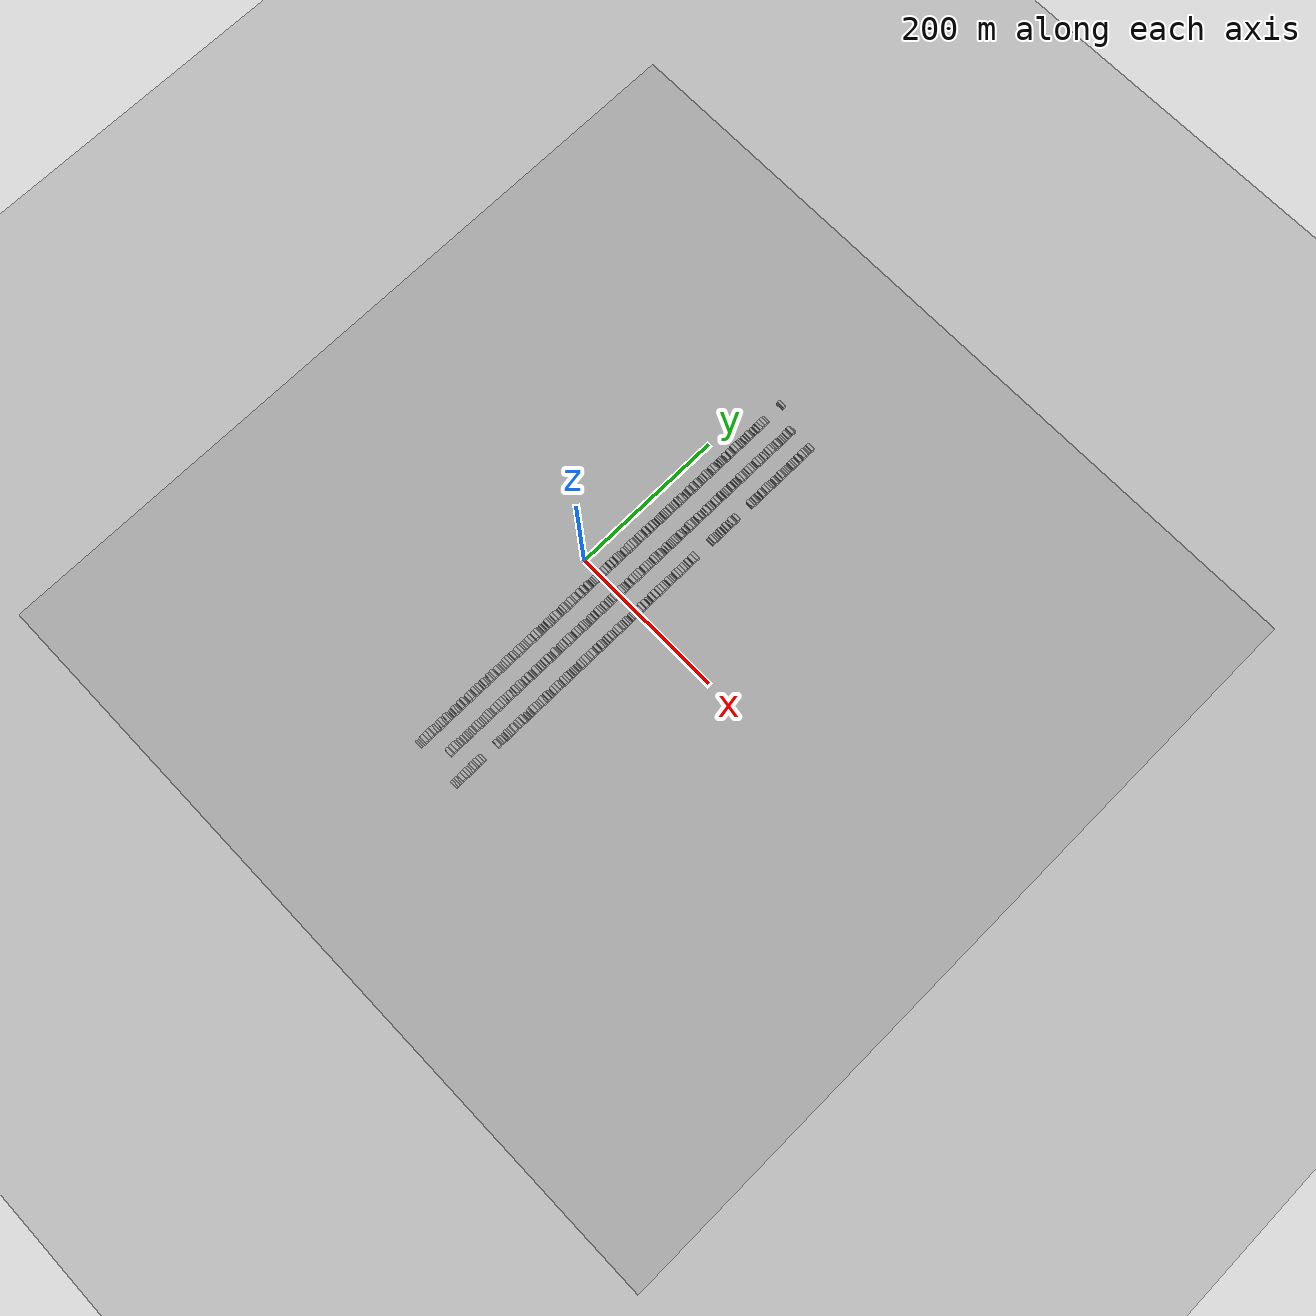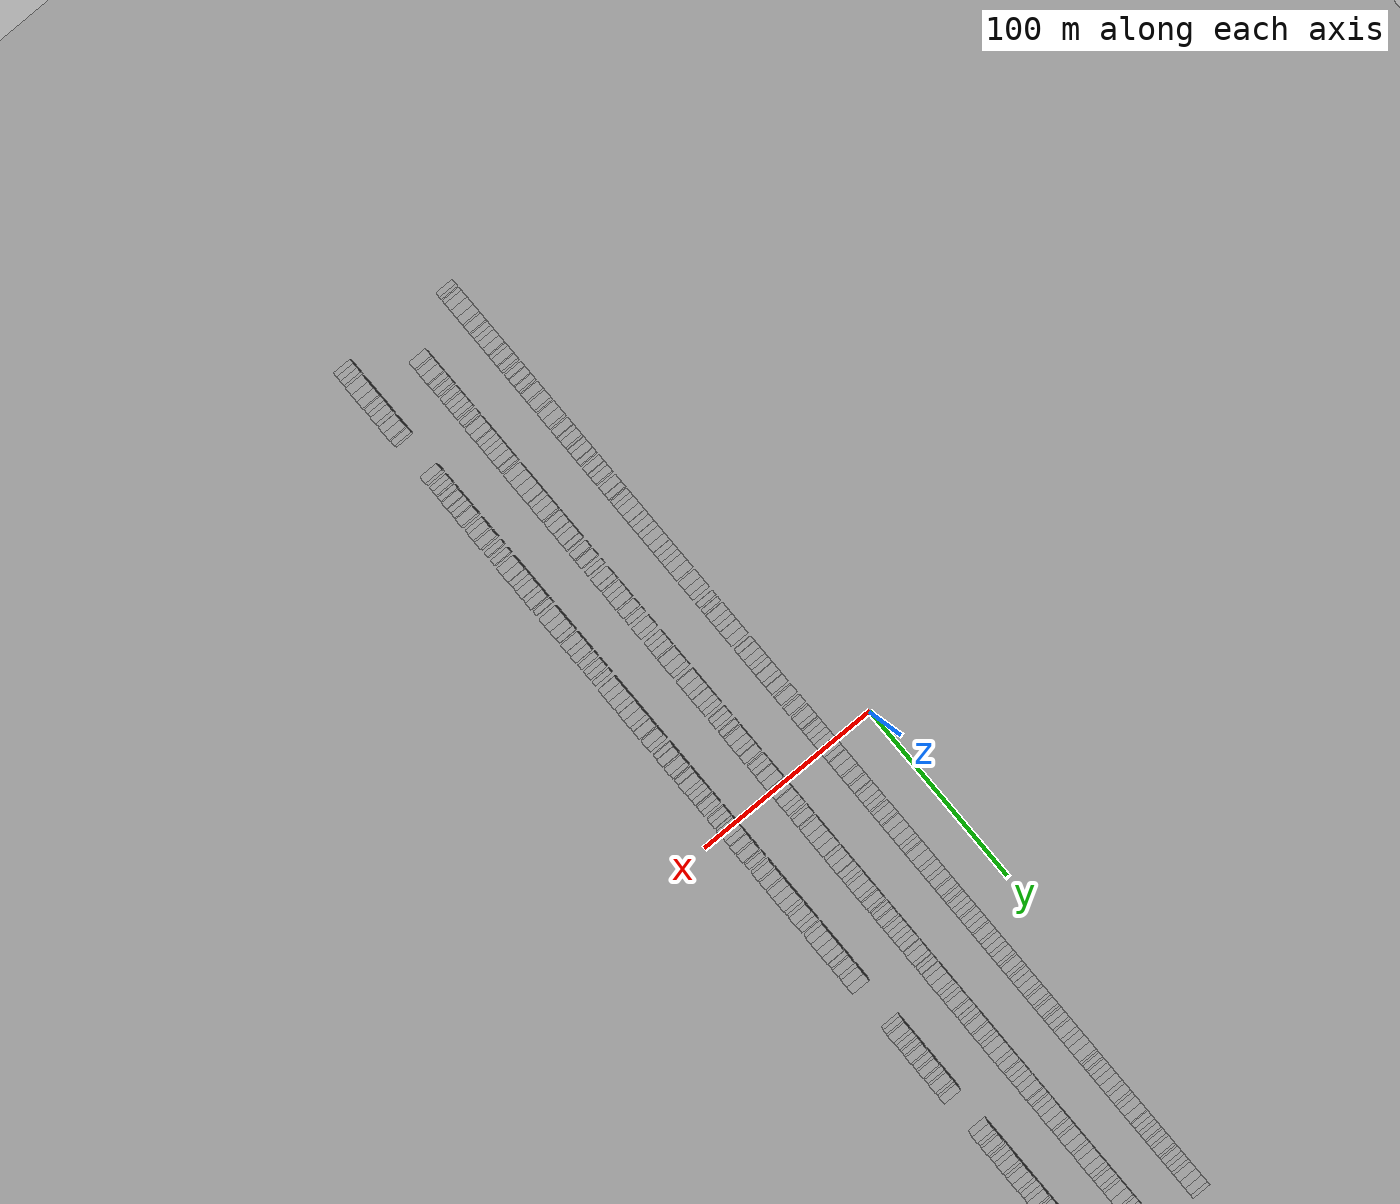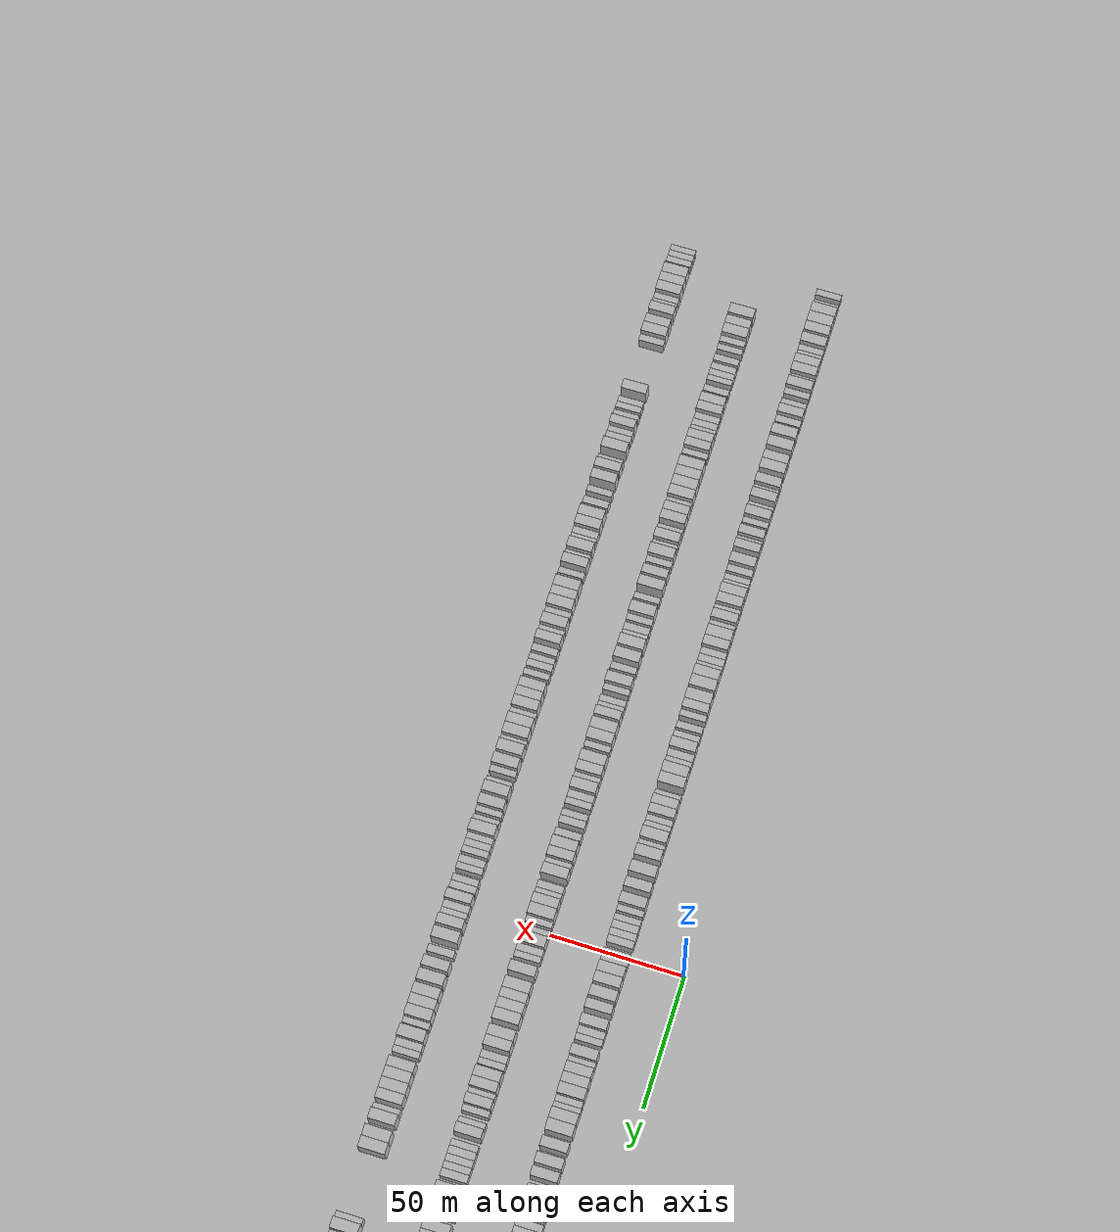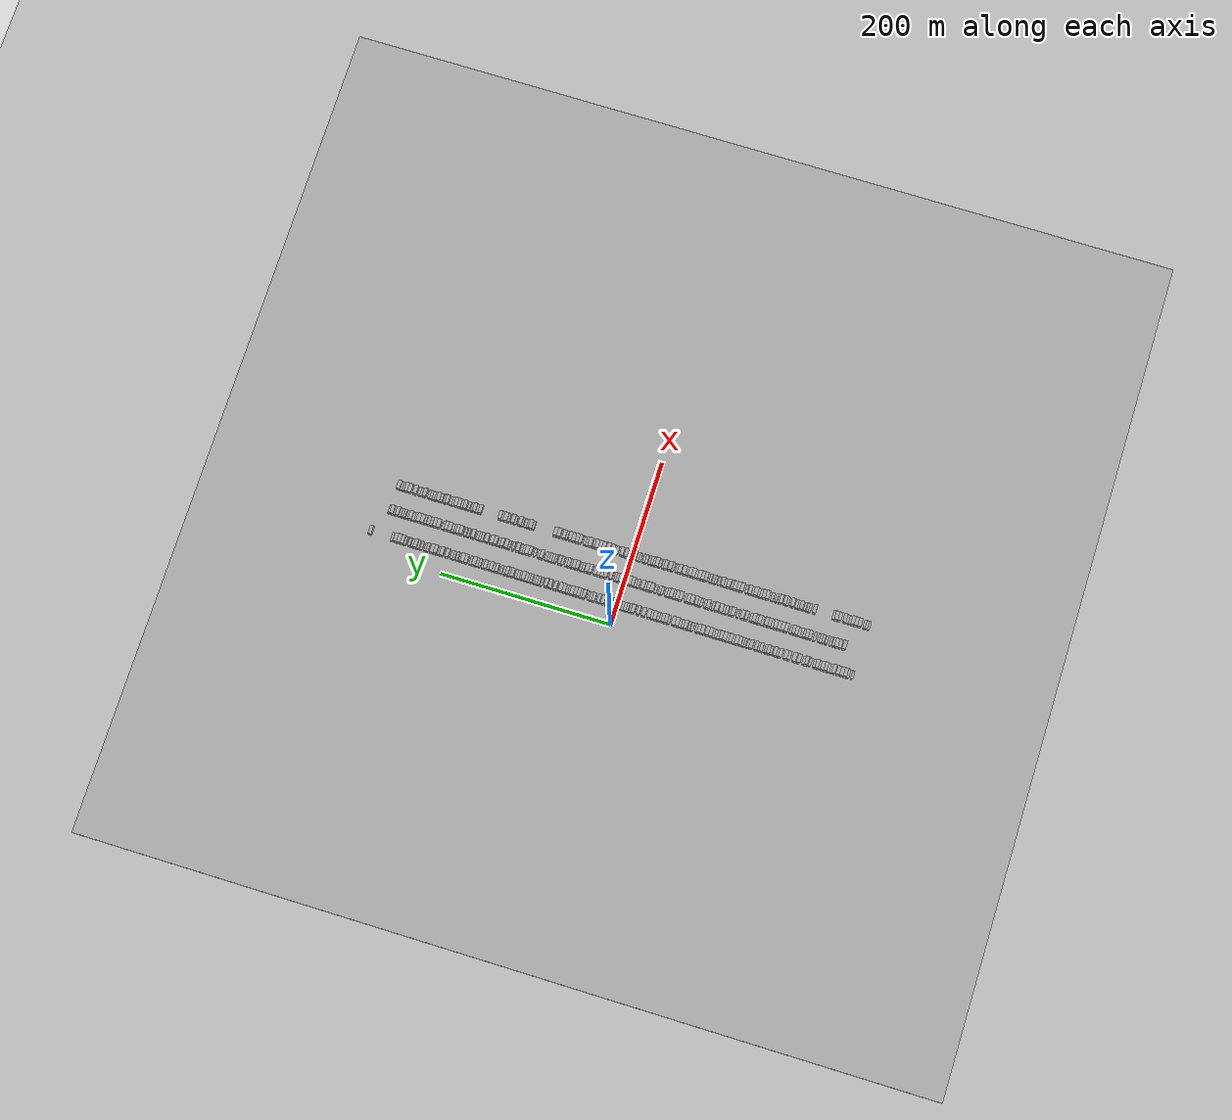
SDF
<?xml version="1.0" encoding="utf-8"?>

<sdf version="1.6">

   <world name="default">

      <gui fullscreen="0">

         <camera name="user_camera">

            <pose>-15 0 4.57585 0 0 0</pose>

            <view_controller>orbit</view_controller>

         </camera>

      </gui>

      <scene>

         <sky>

           <clouds>

             <speed>12</speed>

           </clouds>

         </sky>

         <ambient>0.4 0.4 0.4 1</ambient>

         <background>0.7 0.7 0.7 1</background>

         <shadows>1</shadows>

      </scene>

      <gravity>0 0 -9.8066</gravity>

      <magnetic_field>6e-06 2.3e-05 -4.2e-05</magnetic_field>

      <physics default="0" name="default_physics" type="ode">

         <ode>

            <solver>

               <type>quick</type>

               <iters>10</iters>

               <sor>1.0</sor>

               <use_dynamic_moi_rescaling>0</use_dynamic_moi_rescaling>

            </solver>

            <constraints>

               <cfm>0</cfm>

               <erp>0.2</erp>

               <contact_max_correcting_vel>100</contact_max_correcting_vel>

               <contact_surface_layer>0.001</contact_surface_layer>

            </constraints>

         </ode>

         <max_step_size>0.004</max_step_size>

         <real_time_factor>1</real_time_factor>

         <real_time_update_rate>250</real_time_update_rate>

      </physics>

      <light name="sun" type="directional">

         <cast_shadows>1</cast_shadows>

         <pose>0 0 10 0 0 0</pose>

         <diffuse>0.8 0.8 0.8 1</diffuse>

         <specular>0.2 0.2 0.2 1</specular>

         <attenuation>

            <range>1000</range>

            <constant>0.9</constant>

            <linear>0.01</linear>

            <quadratic>0.001</quadratic>

         </attenuation>

         <direction>-0.5 0.1 -0.9</direction>

      </light>

      <include>

         <name>ground_plane_1</name>

         <uri>model://HANNAS_ground_plane</uri>

         <pose>0 0 0  0 0 0</pose>

      </include>

      <include>

         <name>ground_plane_2</name>

         <uri>model://HANNAS_ground_plane</uri>

         <pose>100 0 0  0 0 0</pose>

      </include>

      <model name="building_1">

         <static>1</static>

         <pose frame="">25.0000 -276.6459 0 0.000000 0.000000 0.000000</pose>

         <link name="link">

            <pose frame="">0 0 3.00 0 0 0</pose>

            <collision name="collision">

               <geometry>

                  <box>

                     <size>10.0000 2.7081 6.0000</size>

                  </box>

               </geometry>

               <max_contacts>10</max_contacts>

               <surface>

                  <contact>

                     <ode/>

                  </contact>

                  <bounce/>

                  <friction>

                     <torsional>

                        <ode/>

                     </torsional>

                     <ode/>

                  </friction>

               </surface>

            </collision>

            <visual name="visual">

               <cast_shadows>0</cast_shadows>

               <geometry>

                  <box>

                     <size>10.0000 2.7081 6.0000</size>

                  </box>

               </geometry>

               <material>

                  <script>

                     <uri>model://HANNAS_wall/materials/scripts</uri>

                     <uri>model://HANNAS_wall/materials/textures</uri>

                     <name>vrc/HANNAS_wall</name>

                  </script>

               </material>

            </visual>

            <self_collide>0</self_collide>

            <enable_wind>0</enable_wind>

            <kinematic>0</kinematic>

         </link>

      </model>

      <model name="building_2">

         <static>1</static>

         <pose frame="">25.0000 -271.9616 0 0.000000 0.000000 0.000000</pose>

         <link name="link">

            <pose frame="">0 0 3.00 0 0 0</pose>

            <collision name="collision">

               <geometry>

                  <box>

                     <size>10.0000 2.6605 6.0000</size>

                  </box>

               </geometry>

               <max_contacts>10</max_contacts>

               <surface>

                  <contact>

                     <ode/>

                  </contact>

                  <bounce/>

                  <friction>

                     <torsional>

                        <ode/>

                     </torsional>

                     <ode/>

                  </friction>

               </surface>

            </collision>

            <visual name="visual">

               <cast_shadows>0</cast_shadows>

               <geometry>

                  <box>

                     <size>10.0000 2.6605 6.0000</size>

                  </box>

               </geometry>

               <material>

                  <script>

                     <uri>model://HANNAS_wall/materials/scripts</uri>

                     <uri>model://HANNAS_wall/materials/textures</uri>

                     <name>vrc/HANNAS_wall</name>

                  </script>

               </material>

            </visual>

            <self_collide>0</self_collide>

            <enable_wind>0</enable_wind>

            <kinematic>0</kinematic>

         </link>

      </model>

      <model name="building_3">

         <static>1</static>

         <pose frame="">25.0000 -268.5851 0 0.000000 0.000000 0.000000</pose>

         <link name="link">

            <pose frame="">0 0 4.50 0 0 0</pose>

            <collision name="collision">

               <geometry>

                  <box>

                     <size>10.0000 4.0925 9.0000</size>

                  </box>

               </geometry>

               <max_contacts>10</max_contacts>

               <surface>

                  <contact>

                     <ode/>

                  </contact>

                  <bounce/>

                  <friction>

                     <torsional>

                        <ode/>

                     </torsional>

                     <ode/>

                  </friction>

               </surface>

            </collision>

            <visual name="visual">

               <cast_shadows>0</cast_shadows>

               <geometry>

                  <box>

                     <size>10.0000 4.0925 9.0000</size>

                  </box>

               </geometry>

               <material>

                  <script>

                     <uri>model://HANNAS_wall/materials/scripts</uri>

                     <uri>model://HANNAS_wall/materials/textures</uri>

                     <name>vrc/HANNAS_wall</name>

                  </script>

               </material>

            </visual>

            <self_collide>0</self_collide>

            <enable_wind>0</enable_wind>

            <kinematic>0</kinematic>

         </link>

      </model>

      <model name="building_4">

         <static>1</static>

         <pose frame="">25.0000 -264.3057 0 0.000000 0.000000 0.000000</pose>

         <link name="link">

            <pose frame="">0 0 4.50 0 0 0</pose>

            <collision name="collision">

               <geometry>

                  <box>

                     <size>10.0000 4.4662 9.0000</size>

                  </box>

               </geometry>

               <max_contacts>10</max_contacts>

               <surface>

                  <contact>

                     <ode/>

                  </contact>

                  <bounce/>

                  <friction>

                     <torsional>

                        <ode/>

                     </torsional>

                     <ode/>

                  </friction>

               </surface>

            </collision>

            <visual name="visual">

               <cast_shadows>0</cast_shadows>

               <geometry>

                  <box>

                     <size>10.0000 4.4662 9.0000</size>

                  </box>

               </geometry>

               <material>

                  <script>

                     <uri>model://HANNAS_wall/materials/scripts</uri>

                     <uri>model://HANNAS_wall/materials/textures</uri>

                     <name>vrc/HANNAS_wall</name>

                  </script>

               </material>

            </visual>

            <self_collide>0</self_collide>

            <enable_wind>0</enable_wind>

            <kinematic>0</kinematic>

         </link>

      </model>

      <model name="building_5">

         <static>1</static>

         <pose frame="">25.0000 -260.0190 0 0.000000 0.000000 0.000000</pose>

         <link name="link">

            <pose frame="">0 0 4.50 0 0 0</pose>

            <collision name="collision">

               <geometry>

                  <box>

                     <size>10.0000 4.1072 9.0000</size>

                  </box>

               </geometry>

               <max_contacts>10</max_contacts>

               <surface>

                  <contact>

                     <ode/>

                  </contact>

                  <bounce/>

                  <friction>

                     <torsional>

                        <ode/>

                     </torsional>

                     <ode/>

                  </friction>

               </surface>

            </collision>

            <visual name="visual">

               <cast_shadows>0</cast_shadows>

               <geometry>

                  <box>

                     <size>10.0000 4.1072 9.0000</size>

                  </box>

               </geometry>

               <material>

                  <script>

                     <uri>model://HANNAS_wall/materials/scripts</uri>

                     <uri>model://HANNAS_wall/materials/textures</uri>

                     <name>vrc/HANNAS_wall</name>

                  </script>

               </material>

            </visual>

            <self_collide>0</self_collide>

            <enable_wind>0</enable_wind>

            <kinematic>0</kinematic>

         </link>

      </model>

      <model name="building_6">

         <static>1</static>

         <pose frame="">25.0000 -254.9210 0 0.000000 0.000000 0.000000</pose>

         <link name="link">

            <pose frame="">0 0 4.50 0 0 0</pose>

            <collision name="collision">

               <geometry>

                  <box>

                     <size>10.0000 4.0887 9.0000</size>

                  </box>

               </geometry>

               <max_contacts>10</max_contacts>

               <surface>

                  <contact>

                     <ode/>

                  </contact>

                  <bounce/>

                  <friction>

                     <torsional>

                        <ode/>

                     </torsional>

                     <ode/>

                  </friction>

               </surface>

            </collision>

            <visual name="visual">

               <cast_shadows>0</cast_shadows>

               <geometry>

                  <box>

                     <size>10.0000 4.0887 9.0000</size>

                  </box>

               </geometry>

               <material>

                  <script>

                     <uri>model://HANNAS_wall/materials/scripts</uri>

                     <uri>model://HANNAS_wall/materials/textures</uri>

                     <name>vrc/HANNAS_wall</name>

                  </script>

               </material>

            </visual>

            <self_collide>0</self_collide>

            <enable_wind>0</enable_wind>

            <kinematic>0</kinematic>

         </link>

      </model>

      <model name="building_7">

         <static>1</static>

         <pose frame="">25.0000 -251.5655 0 0.000000 0.000000 0.000000</pose>

         <link name="link">

            <pose frame="">0 0 3.00 0 0 0</pose>

            <collision name="collision">

               <geometry>

                  <box>

                     <size>10.0000 2.6223 6.0000</size>

                  </box>

               </geometry>

               <max_contacts>10</max_contacts>

               <surface>

                  <contact>

                     <ode/>

                  </contact>

                  <bounce/>

                  <friction>

                     <torsional>

                        <ode/>

                     </torsional>

                     <ode/>

                  </friction>

               </surface>

            </collision>

            <visual name="visual">

               <cast_shadows>0</cast_shadows>

               <geometry>

                  <box>

                     <size>10.0000 2.6223 6.0000</size>

                  </box>

               </geometry>

               <material>

                  <script>

                     <uri>model://HANNAS_wall/materials/scripts</uri>

                     <uri>model://HANNAS_wall/materials/textures</uri>

                     <name>vrc/HANNAS_wall</name>

                  </script>

               </material>

            </visual>

            <self_collide>0</self_collide>

            <enable_wind>0</enable_wind>

            <kinematic>0</kinematic>

         </link>

      </model>

      <model name="building_8">

         <static>1</static>

         <pose frame="">25.0000 -248.7749 0 0.000000 0.000000 0.000000</pose>

         <link name="link">

            <pose frame="">0 0 3.00 0 0 0</pose>

            <collision name="collision">

               <geometry>

                  <box>

                     <size>10.0000 2.9590 6.0000</size>

                  </box>

               </geometry>

               <max_contacts>10</max_contacts>

               <surface>

                  <contact>

                     <ode/>

                  </contact>

                  <bounce/>

                  <friction>

                     <torsional>

                        <ode/>

                     </torsional>

                     <ode/>

                  </friction>

               </surface>

            </collision>

            <visual name="visual">

               <cast_shadows>0</cast_shadows>

               <geometry>

                  <box>

                     <size>10.0000 2.9590 6.0000</size>

                  </box>

               </geometry>

               <material>

                  <script>

                     <uri>model://HANNAS_wall/materials/scripts</uri>

                     <uri>model://HANNAS_wall/materials/textures</uri>

                     <name>vrc/HANNAS_wall</name>

                  </script>

               </material>

            </visual>

            <self_collide>0</self_collide>

            <enable_wind>0</enable_wind>

            <kinematic>0</kinematic>

         </link>

      </model>

      <model name="building_9">

         <static>1</static>

         <pose frame="">25.0000 -245.4770 0 0.000000 0.000000 0.000000</pose>

         <link name="link">

            <pose frame="">0 0 4.50 0 0 0</pose>

            <collision name="collision">

               <geometry>

                  <box>

                     <size>10.0000 3.6368 9.0000</size>

                  </box>

               </geometry>

               <max_contacts>10</max_contacts>

               <surface>

                  <contact>

                     <ode/>

                  </contact>

                  <bounce/>

                  <friction>

                     <torsional>

                        <ode/>

                     </torsional>

                     <ode/>

                  </friction>

               </surface>

            </collision>

            <visual name="visual">

               <cast_shadows>0</cast_shadows>

               <geometry>

                  <box>

                     <size>10.0000 3.6368 9.0000</size>

                  </box>

               </geometry>

               <material>

                  <script>

                     <uri>model://HANNAS_wall/materials/scripts</uri>

                     <uri>model://HANNAS_wall/materials/textures</uri>

                     <name>vrc/HANNAS_wall</name>

                  </script>

               </material>

            </visual>

            <self_collide>0</self_collide>

            <enable_wind>0</enable_wind>

            <kinematic>0</kinematic>

         </link>

      </model>

      <model name="building_10">

         <static>1</static>

         <pose frame="">25.0000 -241.6907 0 0.000000 0.000000 0.000000</pose>

         <link name="link">

            <pose frame="">0 0 4.50 0 0 0</pose>

            <collision name="collision">

               <geometry>

                  <box>

                     <size>10.0000 3.9358 9.0000</size>

                  </box>

               </geometry>

               <max_contacts>10</max_contacts>

               <surface>

                  <contact>

                     <ode/>

                  </contact>

                  <bounce/>

                  <friction>

                     <torsional>

                        <ode/>

                     </torsional>

                     <ode/>

                  </friction>

               </surface>

            </collision>

            <visual name="visual">

               <cast_shadows>0</cast_shadows>

               <geometry>

                  <box>

                     <size>10.0000 3.9358 9.0000</size>

                  </box>

               </geometry>

               <material>

                  <script>

                     <uri>model://HANNAS_wall/materials/scripts</uri>

                     <uri>model://HANNAS_wall/materials/textures</uri>

                     <name>vrc/HANNAS_wall</name>

                  </script>

               </material>

            </visual>

            <self_collide>0</self_collide>

            <enable_wind>0</enable_wind>

            <kinematic>0</kinematic>

         </link>

      </model>

      <model name="building_11">

         <static>1</static>

         <pose frame="">25.0000 -238.5181 0 0.000000 0.000000 0.000000</pose>

         <link name="link">

            <pose frame="">0 0 3.00 0 0 0</pose>

            <collision name="collision">

               <geometry>

                  <box>

                     <size>10.0000 2.4093 6.0000</size>

                  </box>

               </geometry>

               <max_contacts>10</max_contacts>

               <surface>

                  <contact>

                     <ode/>

                  </contact>

                  <bounce/>

                  <friction>

                     <torsional>

                        <ode/>

                     </torsional>

                     <ode/>

                  </friction>

               </surface>

            </collision>

            <visual name="visual">

               <cast_shadows>0</cast_shadows>

               <geometry>

                  <box>

                     <size>10.0000 2.4093 6.0000</size>

                  </box>

               </geometry>

               <material>

                  <script>

                     <uri>model://HANNAS_wall/materials/scripts</uri>

                     <uri>model://HANNAS_wall/materials/textures</uri>

                     <name>vrc/HANNAS_wall</name>

                  </script>

               </material>

            </visual>

            <self_collide>0</self_collide>

            <enable_wind>0</enable_wind>

            <kinematic>0</kinematic>

         </link>

      </model>

      <model name="building_12">

         <static>1</static>

         <pose frame="">25.0000 -235.2913 0 0.000000 0.000000 0.000000</pose>

         <link name="link">

            <pose frame="">0 0 4.50 0 0 0</pose>

            <collision name="collision">

               <geometry>

                  <box>

                     <size>10.0000 4.0443 9.0000</size>

                  </box>

               </geometry>

               <max_contacts>10</max_contacts>

               <surface>

                  <contact>

                     <ode/>

                  </contact>

                  <bounce/>

                  <friction>

                     <torsional>

                        <ode/>

                     </torsional>

                     <ode/>

                  </friction>

               </surface>

            </collision>

            <visual name="visual">

               <cast_shadows>0</cast_shadows>

               <geometry>

                  <box>

                     <size>10.0000 4.0443 9.0000</size>

                  </box>

               </geometry>

               <material>

                  <script>

                     <uri>model://HANNAS_wall/materials/scripts</uri>

                     <uri>model://HANNAS_wall/materials/textures</uri>

                     <name>vrc/HANNAS_wall</name>

                  </script>

               </material>

            </visual>

            <self_collide>0</self_collide>

            <enable_wind>0</enable_wind>

            <kinematic>0</kinematic>

         </link>

      </model>

      <model name="building_13">

         <static>1</static>

         <pose frame="">25.0000 -231.9161 0 0.000000 0.000000 0.000000</pose>

         <link name="link">

            <pose frame="">0 0 3.00 0 0 0</pose>

            <collision name="collision">

               <geometry>

                  <box>

                     <size>10.0000 2.7061 6.0000</size>

                  </box>

               </geometry>

               <max_contacts>10</max_contacts>

               <surface>

                  <contact>

                     <ode/>

                  </contact>

                  <bounce/>

                  <friction>

                     <torsional>

                        <ode/>

                     </torsional>

                     <ode/>

                  </friction>

               </surface>

            </collision>

            <visual name="visual">

               <cast_shadows>0</cast_shadows>

               <geometry>

                  <box>

                     <size>10.0000 2.7061 6.0000</size>

                  </box>

               </geometry>

               <material>

                  <script>

                     <uri>model://HANNAS_wall/materials/scripts</uri>

                     <uri>model://HANNAS_wall/materials/textures</uri>

                     <name>vrc/HANNAS_wall</name>

                  </script>

               </material>

            </visual>

            <self_collide>0</self_collide>

            <enable_wind>0</enable_wind>

            <kinematic>0</kinematic>

         </link>

      </model>

      <model name="building_14">

         <static>1</static>

         <pose frame="">25.0000 -227.2116 0 0.000000 0.000000 0.000000</pose>

         <link name="link">

            <pose frame="">0 0 3.00 0 0 0</pose>

            <collision name="collision">

               <geometry>

                  <box>

                     <size>10.0000 2.7027 6.0000</size>

                  </box>

               </geometry>

               <max_contacts>10</max_contacts>

               <surface>

                  <contact>

                     <ode/>

                  </contact>

                  <bounce/>

                  <friction>

                     <torsional>

                        <ode/>

                     </torsional>

                     <ode/>

                  </friction>

               </surface>

            </collision>

            <visual name="visual">

               <cast_shadows>0</cast_shadows>

               <geometry>

                  <box>

                     <size>10.0000 2.7027 6.0000</size>

                  </box>

               </geometry>

               <material>

                  <script>

                     <uri>model://HANNAS_wall/materials/scripts</uri>

                     <uri>model://HANNAS_wall/materials/textures</uri>

                     <name>vrc/HANNAS_wall</name>

                  </script>

               </material>

            </visual>

            <self_collide>0</self_collide>

            <enable_wind>0</enable_wind>

            <kinematic>0</kinematic>

         </link>

      </model>

      <model name="building_15">

         <static>1</static>

         <pose frame="">25.0000 -222.9976 0 0.000000 0.000000 0.000000</pose>

         <link name="link">

            <pose frame="">0 0 4.50 0 0 0</pose>

            <collision name="collision">

               <geometry>

                  <box>

                     <size>10.0000 3.7254 9.0000</size>

                  </box>

               </geometry>

               <max_contacts>10</max_contacts>

               <surface>

                  <contact>

                     <ode/>

                  </contact>

                  <bounce/>

                  <friction>

                     <torsional>

                        <ode/>

                     </torsional>

                     <ode/>

                  </friction>

               </surface>

            </collision>

            <visual name="visual">

               <cast_shadows>0</cast_shadows>

               <geometry>

                  <box>

                     <size>10.0000 3.7254 9.0000</size>

                  </box>

               </geometry>

               <material>

                  <script>

                     <uri>model://HANNAS_wall/materials/scripts</uri>

                     <uri>model://HANNAS_wall/materials/textures</uri>

                     <name>vrc/HANNAS_wall</name>

                  </script>

               </material>

            </visual>

            <self_collide>0</self_collide>

            <enable_wind>0</enable_wind>

            <kinematic>0</kinematic>

         </link>

      </model>

      <model name="building_16">

         <static>1</static>

         <pose frame="">25.0000 -219.6483 0 0.000000 0.000000 0.000000</pose>

         <link name="link">

            <pose frame="">0 0 3.00 0 0 0</pose>

            <collision name="collision">

               <geometry>

                  <box>

                     <size>10.0000 2.9733 6.0000</size>

                  </box>

               </geometry>

               <max_contacts>10</max_contacts>

               <surface>

                  <contact>

                     <ode/>

                  </contact>

                  <bounce/>

                  <friction>

                     <torsional>

                        <ode/>

                     </torsional>

                     <ode/>

                  </friction>

               </surface>

            </collision>

            <visual name="visual">

               <cast_shadows>0</cast_shadows>

               <geometry>

                  <box>

                     <size>10.0000 2.9733 6.0000</size>

                  </box>

               </geometry>

               <material>

                  <script>

                     <uri>model://HANNAS_wall/materials/scripts</uri>

                     <uri>model://HANNAS_wall/materials/textures</uri>

                     <name>vrc/HANNAS_wall</name>

                  </script>

               </material>

            </visual>

            <self_collide>0</self_collide>

            <enable_wind>0</enable_wind>

            <kinematic>0</kinematic>

         </link>

      </model>

      <model name="building_17">

         <static>1</static>

         <pose frame="">25.0000 -214.0251 0 0.000000 0.000000 0.000000</pose>

         <link name="link">

            <pose frame="">0 0 4.50 0 0 0</pose>

            <collision name="collision">

               <geometry>

                  <box>

                     <size>10.0000 4.2729 9.0000</size>

                  </box>

               </geometry>

               <max_contacts>10</max_contacts>

               <surface>

                  <contact>

                     <ode/>

                  </contact>

                  <bounce/>

                  <friction>

                     <torsional>

                        <ode/>

                     </torsional>

                     <ode/>

                  </friction>

               </surface>

            </collision>

            <visual name="visual">

               <cast_shadows>0</cast_shadows>

               <geometry>

                  <box>

                     <size>10.0000 4.2729 9.0000</size>

                  </box>

               </geometry>

               <material>

                  <script>

                     <uri>model://HANNAS_wall/materials/scripts</uri>

                     <uri>model://HANNAS_wall/materials/textures</uri>

                     <name>vrc/HANNAS_wall</name>

                  </script>

               </material>

            </visual>

            <self_collide>0</self_collide>

            <enable_wind>0</enable_wind>

            <kinematic>0</kinematic>

         </link>

      </model>

      <model name="building_18">

         <static>1</static>

         <pose frame="">25.0000 -208.6609 0 0.000000 0.000000 0.000000</pose>

         <link name="link">

            <pose frame="">0 0 4.50 0 0 0</pose>

            <collision name="collision">

               <geometry>

                  <box>

                     <size>10.0000 4.4556 9.0000</size>

                  </box>

               </geometry>

               <max_contacts>10</max_contacts>

               <surface>

                  <contact>

                     <ode/>

                  </contact>

                  <bounce/>

                  <friction>

                     <torsional>

                        <ode/>

                     </torsional>

                     <ode/>

                  </friction>

               </surface>

            </collision>

            <visual name="visual">

               <cast_shadows>0</cast_shadows>

               <geometry>

                  <box>

                     <size>10.0000 4.4556 9.0000</size>

                  </box>

               </geometry>

               <material>

                  <script>

                     <uri>model://HANNAS_wall/materials/scripts</uri>

                     <uri>model://HANNAS_wall/materials/textures</uri>

                     <name>vrc/HANNAS_wall</name>

                  </script>

               </material>

            </visual>

            <self_collide>0</self_collide>

            <enable_wind>0</enable_wind>

            <kinematic>0</kinematic>

         </link>

      </model>

      <model name="building_19">

         <static>1</static>

         <pose frame="">25.0000 -202.5923 0 0.000000 0.000000 0.000000</pose>

         <link name="link">

            <pose frame="">0 0 4.50 0 0 0</pose>

            <collision name="collision">

               <geometry>

                  <box>

                     <size>10.0000 3.6817 9.0000</size>

                  </box>

               </geometry>

               <max_contacts>10</max_contacts>

               <surface>

                  <contact>

                     <ode/>

                  </contact>

                  <bounce/>

                  <friction>

                     <torsional>

                        <ode/>

                     </torsional>

                     <ode/>

                  </friction>

               </surface>

            </collision>

            <visual name="visual">

               <cast_shadows>0</cast_shadows>

               <geometry>

                  <box>

                     <size>10.0000 3.6817 9.0000</size>

                  </box>

               </geometry>

               <material>

                  <script>

                     <uri>model://HANNAS_wall/materials/scripts</uri>

                     <uri>model://HANNAS_wall/materials/textures</uri>

                     <name>vrc/HANNAS_wall</name>

                  </script>

               </material>

            </visual>

            <self_collide>0</self_collide>

            <enable_wind>0</enable_wind>

            <kinematic>0</kinematic>

         </link>

      </model>

      <model name="building_20">

         <static>1</static>

         <pose frame="">25.0000 -198.5943 0 0.000000 0.000000 0.000000</pose>

         <link name="link">

            <pose frame="">0 0 4.50 0 0 0</pose>

            <collision name="collision">

               <geometry>

                  <box>

                     <size>10.0000 4.3144 9.0000</size>

                  </box>

               </geometry>

               <max_contacts>10</max_contacts>

               <surface>

                  <contact>

                     <ode/>

                  </contact>

                  <bounce/>

                  <friction>

                     <torsional>

                        <ode/>

                     </torsional>

                     <ode/>

                  </friction>

               </surface>

            </collision>

            <visual name="visual">

               <cast_shadows>0</cast_shadows>

               <geometry>

                  <box>

                     <size>10.0000 4.3144 9.0000</size>

                  </box>

               </geometry>

               <material>

                  <script>

                     <uri>model://HANNAS_wall/materials/scripts</uri>

                     <uri>model://HANNAS_wall/materials/textures</uri>

                     <name>vrc/HANNAS_wall</name>

                  </script>

               </material>

            </visual>

            <self_collide>0</self_collide>

            <enable_wind>0</enable_wind>

            <kinematic>0</kinematic>

         </link>

      </model>

      <model name="building_21">

         <static>1</static>

         <pose frame="">25.0000 -192.4441 0 0.000000 0.000000 0.000000</pose>

         <link name="link">

            <pose frame="">0 0 4.50 0 0 0</pose>

            <collision name="collision">

               <geometry>

                  <box>

                     <size>10.0000 3.9859 9.0000</size>

                  </box>

               </geometry>

               <max_contacts>10</max_contacts>

               <surface>

                  <contact>

                     <ode/>

                  </contact>

                  <bounce/>

                  <friction>

                     <torsional>

                        <ode/>

                     </torsional>

                     <ode/>

                  </friction>

               </surface>

            </collision>

            <visual name="visual">

               <cast_shadows>0</cast_shadows>

               <geometry>

                  <box>

                     <size>10.0000 3.9859 9.0000</size>

                  </box>

               </geometry>

               <material>

                  <script>

                     <uri>model://HANNAS_wall/materials/scripts</uri>

                     <uri>model://HANNAS_wall/materials/textures</uri>

                     <name>vrc/HANNAS_wall</name>

                  </script>

               </material>

            </visual>

            <self_collide>0</self_collide>

            <enable_wind>0</enable_wind>

            <kinematic>0</kinematic>

         </link>

      </model>

      <model name="building_22">

         <static>1</static>

         <pose frame="">25.0000 -189.2357 0 0.000000 0.000000 0.000000</pose>

         <link name="link">

            <pose frame="">0 0 3.00 0 0 0</pose>

            <collision name="collision">

               <geometry>

                  <box>

                     <size>10.0000 2.4310 6.0000</size>

                  </box>

               </geometry>

               <max_contacts>10</max_contacts>

               <surface>

                  <contact>

                     <ode/>

                  </contact>

                  <bounce/>

                  <friction>

                     <torsional>

                        <ode/>

                     </torsional>

                     <ode/>

                  </friction>

               </surface>

            </collision>

            <visual name="visual">

               <cast_shadows>0</cast_shadows>

               <geometry>

                  <box>

                     <size>10.0000 2.4310 6.0000</size>

                  </box>

               </geometry>

               <material>

                  <script>

                     <uri>model://HANNAS_wall/materials/scripts</uri>

                     <uri>model://HANNAS_wall/materials/textures</uri>

                     <name>vrc/HANNAS_wall</name>

                  </script>

               </material>

            </visual>

            <self_collide>0</self_collide>

            <enable_wind>0</enable_wind>

            <kinematic>0</kinematic>

         </link>

      </model>

      <model name="building_23">

         <static>1</static>

         <pose frame="">25.0000 -186.0730 0 0.000000 0.000000 0.000000</pose>

         <link name="link">

            <pose frame="">0 0 4.50 0 0 0</pose>

            <collision name="collision">

               <geometry>

                  <box>

                     <size>10.0000 3.8945 9.0000</size>

                  </box>

               </geometry>

               <max_contacts>10</max_contacts>

               <surface>

                  <contact>

                     <ode/>

                  </contact>

                  <bounce/>

                  <friction>

                     <torsional>

                        <ode/>

                     </torsional>

                     <ode/>

                  </friction>

               </surface>

            </collision>

            <visual name="visual">

               <cast_shadows>0</cast_shadows>

               <geometry>

                  <box>

                     <size>10.0000 3.8945 9.0000</size>

                  </box>

               </geometry>

               <material>

                  <script>

                     <uri>model://HANNAS_wall/materials/scripts</uri>

                     <uri>model://HANNAS_wall/materials/textures</uri>

                     <name>vrc/HANNAS_wall</name>

                  </script>

               </material>

            </visual>

            <self_collide>0</self_collide>

            <enable_wind>0</enable_wind>

            <kinematic>0</kinematic>

         </link>

      </model>

      <model name="building_24">

         <static>1</static>

         <pose frame="">25.0000 -181.7934 0 0.000000 0.000000 0.000000</pose>

         <link name="link">

            <pose frame="">0 0 3.00 0 0 0</pose>

            <collision name="collision">

               <geometry>

                  <box>

                     <size>10.0000 2.6648 6.0000</size>

                  </box>

               </geometry>

               <max_contacts>10</max_contacts>

               <surface>

                  <contact>

                     <ode/>

                  </contact>

                  <bounce/>

                  <friction>

                     <torsional>

                        <ode/>

                     </torsional>

                     <ode/>

                  </friction>

               </surface>

            </collision>

            <visual name="visual">

               <cast_shadows>0</cast_shadows>

               <geometry>

                  <box>

                     <size>10.0000 2.6648 6.0000</size>

                  </box>

               </geometry>

               <material>

                  <script>

                     <uri>model://HANNAS_wall/materials/scripts</uri>

                     <uri>model://HANNAS_wall/materials/textures</uri>

                     <name>vrc/HANNAS_wall</name>

                  </script>

               </material>

            </visual>

            <self_collide>0</self_collide>

            <enable_wind>0</enable_wind>

            <kinematic>0</kinematic>

         </link>

      </model>

      <model name="building_25">

         <static>1</static>

         <pose frame="">25.0000 -178.4690 0 0.000000 0.000000 0.000000</pose>

         <link name="link">

            <pose frame="">0 0 4.50 0 0 0</pose>

            <collision name="collision">

               <geometry>

                  <box>

                     <size>10.0000 3.9839 9.0000</size>

                  </box>

               </geometry>

               <max_contacts>10</max_contacts>

               <surface>

                  <contact>

                     <ode/>

                  </contact>

                  <bounce/>

                  <friction>

                     <torsional>

                        <ode/>

                     </torsional>

                     <ode/>

                  </friction>

               </surface>

            </collision>

            <visual name="visual">

               <cast_shadows>0</cast_shadows>

               <geometry>

                  <box>

                     <size>10.0000 3.9839 9.0000</size>

                  </box>

               </geometry>

               <material>

                  <script>

                     <uri>model://HANNAS_wall/materials/scripts</uri>

                     <uri>model://HANNAS_wall/materials/textures</uri>

                     <name>vrc/HANNAS_wall</name>

                  </script>

               </material>

            </visual>

            <self_collide>0</self_collide>

            <enable_wind>0</enable_wind>

            <kinematic>0</kinematic>

         </link>

      </model>

      <model name="building_26">

         <static>1</static>

         <pose frame="">25.0000 -175.1962 0 0.000000 0.000000 0.000000</pose>

         <link name="link">

            <pose frame="">0 0 3.00 0 0 0</pose>

            <collision name="collision">

               <geometry>

                  <box>

                     <size>10.0000 2.5617 6.0000</size>

                  </box>

               </geometry>

               <max_contacts>10</max_contacts>

               <surface>

                  <contact>

                     <ode/>

                  </contact>

                  <bounce/>

                  <friction>

                     <torsional>

                        <ode/>

                     </torsional>

                     <ode/>

                  </friction>

               </surface>

            </collision>

            <visual name="visual">

               <cast_shadows>0</cast_shadows>

               <geometry>

                  <box>

                     <size>10.0000 2.5617 6.0000</size>

                  </box>

               </geometry>

               <material>

                  <script>

                     <uri>model://HANNAS_wall/materials/scripts</uri>

                     <uri>model://HANNAS_wall/materials/textures</uri>

                     <name>vrc/HANNAS_wall</name>

                  </script>

               </material>

            </visual>

            <self_collide>0</self_collide>

            <enable_wind>0</enable_wind>

            <kinematic>0</kinematic>

         </link>

      </model>

      <model name="building_27">

         <static>1</static>

         <pose frame="">25.0000 -170.1131 0 0.000000 0.000000 0.000000</pose>

         <link name="link">

            <pose frame="">0 0 4.50 0 0 0</pose>

            <collision name="collision">

               <geometry>

                  <box>

                     <size>10.0000 3.6046 9.0000</size>

                  </box>

               </geometry>

               <max_contacts>10</max_contacts>

               <surface>

                  <contact>

                     <ode/>

                  </contact>

                  <bounce/>

                  <friction>

                     <torsional>

                        <ode/>

                     </torsional>

                     <ode/>

                  </friction>

               </surface>

            </collision>

            <visual name="visual">

               <cast_shadows>0</cast_shadows>

               <geometry>

                  <box>

                     <size>10.0000 3.6046 9.0000</size>

                  </box>

               </geometry>

               <material>

                  <script>

                     <uri>model://HANNAS_wall/materials/scripts</uri>

                     <uri>model://HANNAS_wall/materials/textures</uri>

                     <name>vrc/HANNAS_wall</name>

                  </script>

               </material>

            </visual>

            <self_collide>0</self_collide>

            <enable_wind>0</enable_wind>

            <kinematic>0</kinematic>

         </link>

      </model>

      <model name="building_28">

         <static>1</static>

         <pose frame="">25.0000 -167.1066 0 0.000000 0.000000 0.000000</pose>

         <link name="link">

            <pose frame="">0 0 3.00 0 0 0</pose>

            <collision name="collision">

               <geometry>

                  <box>

                     <size>10.0000 2.4084 6.0000</size>

                  </box>

               </geometry>

               <max_contacts>10</max_contacts>

               <surface>

                  <contact>

                     <ode/>

                  </contact>

                  <bounce/>

                  <friction>

                     <torsional>

                        <ode/>

                     </torsional>

                     <ode/>

                  </friction>

               </surface>

            </collision>

            <visual name="visual">

               <cast_shadows>0</cast_shadows>

               <geometry>

                  <box>

                     <size>10.0000 2.4084 6.0000</size>

                  </box>

               </geometry>

               <material>

                  <script>

                     <uri>model://HANNAS_wall/materials/scripts</uri>

                     <uri>model://HANNAS_wall/materials/textures</uri>

                     <name>vrc/HANNAS_wall</name>

                  </script>

               </material>

            </visual>

            <self_collide>0</self_collide>

            <enable_wind>0</enable_wind>

            <kinematic>0</kinematic>

         </link>

      </model>

      <model name="building_29">

         <static>1</static>

         <pose frame="">25.0000 -164.0829 0 0.000000 0.000000 0.000000</pose>

         <link name="link">

            <pose frame="">0 0 4.50 0 0 0</pose>

            <collision name="collision">

               <geometry>

                  <box>

                     <size>10.0000 3.6389 9.0000</size>

                  </box>

               </geometry>

               <max_contacts>10</max_contacts>

               <surface>

                  <contact>

                     <ode/>

                  </contact>

                  <bounce/>

                  <friction>

                     <torsional>

                        <ode/>

                     </torsional>

                     <ode/>

                  </friction>

               </surface>

            </collision>

            <visual name="visual">

               <cast_shadows>0</cast_shadows>

               <geometry>

                  <box>

                     <size>10.0000 3.6389 9.0000</size>

                  </box>

               </geometry>

               <material>

                  <script>

                     <uri>model://HANNAS_wall/materials/scripts</uri>

                     <uri>model://HANNAS_wall/materials/textures</uri>

                     <name>vrc/HANNAS_wall</name>

                  </script>

               </material>

            </visual>

            <self_collide>0</self_collide>

            <enable_wind>0</enable_wind>

            <kinematic>0</kinematic>

         </link>

      </model>

      <model name="building_30">

         <static>1</static>

         <pose frame="">25.0000 -158.1772 0 0.000000 0.000000 0.000000</pose>

         <link name="link">

            <pose frame="">0 0 4.50 0 0 0</pose>

            <collision name="collision">

               <geometry>

                  <box>

                     <size>10.0000 4.1725 9.0000</size>

                  </box>

               </geometry>

               <max_contacts>10</max_contacts>

               <surface>

                  <contact>

                     <ode/>

                  </contact>

                  <bounce/>

                  <friction>

                     <torsional>

                        <ode/>

                     </torsional>

                     <ode/>

                  </friction>

               </surface>

            </collision>

            <visual name="visual">

               <cast_shadows>0</cast_shadows>

               <geometry>

                  <box>

                     <size>10.0000 4.1725 9.0000</size>

                  </box>

               </geometry>

               <material>

                  <script>

                     <uri>model://HANNAS_wall/materials/scripts</uri>

                     <uri>model://HANNAS_wall/materials/textures</uri>

                     <name>vrc/HANNAS_wall</name>

                  </script>

               </material>

            </visual>

            <self_collide>0</self_collide>

            <enable_wind>0</enable_wind>

            <kinematic>0</kinematic>

         </link>

      </model>

      <model name="building_31">

         <static>1</static>

         <pose frame="">25.0000 -154.6167 0 0.000000 0.000000 0.000000</pose>

         <link name="link">

            <pose frame="">0 0 3.00 0 0 0</pose>

            <collision name="collision">

               <geometry>

                  <box>

                     <size>10.0000 2.9485 6.0000</size>

                  </box>

               </geometry>

               <max_contacts>10</max_contacts>

               <surface>

                  <contact>

                     <ode/>

                  </contact>

                  <bounce/>

                  <friction>

                     <torsional>

                        <ode/>

                     </torsional>

                     <ode/>

                  </friction>

               </surface>

            </collision>

            <visual name="visual">

               <cast_shadows>0</cast_shadows>

               <geometry>

                  <box>

                     <size>10.0000 2.9485 6.0000</size>

                  </box>

               </geometry>

               <material>

                  <script>

                     <uri>model://HANNAS_wall/materials/scripts</uri>

                     <uri>model://HANNAS_wall/materials/textures</uri>

                     <name>vrc/HANNAS_wall</name>

                  </script>

               </material>

            </visual>

            <self_collide>0</self_collide>

            <enable_wind>0</enable_wind>

            <kinematic>0</kinematic>

         </link>

      </model>

      <model name="building_32">

         <static>1</static>

         <pose frame="">25.0000 -150.9131 0 0.000000 0.000000 0.000000</pose>

         <link name="link">

            <pose frame="">0 0 3.00 0 0 0</pose>

            <collision name="collision">

               <geometry>

                  <box>

                     <size>10.0000 2.4588 6.0000</size>

                  </box>

               </geometry>

               <max_contacts>10</max_contacts>

               <surface>

                  <contact>

                     <ode/>

                  </contact>

                  <bounce/>

                  <friction>

                     <torsional>

                        <ode/>

                     </torsional>

                     <ode/>

                  </friction>

               </surface>

            </collision>

            <visual name="visual">

               <cast_shadows>0</cast_shadows>

               <geometry>

                  <box>

                     <size>10.0000 2.4588 6.0000</size>

                  </box>

               </geometry>

               <material>

                  <script>

                     <uri>model://HANNAS_wall/materials/scripts</uri>

                     <uri>model://HANNAS_wall/materials/textures</uri>

                     <name>vrc/HANNAS_wall</name>

                  </script>

               </material>

            </visual>

            <self_collide>0</self_collide>

            <enable_wind>0</enable_wind>

            <kinematic>0</kinematic>

         </link>

      </model>

      <model name="building_33">

         <static>1</static>

         <pose frame="">25.0000 -148.4182 0 0.000000 0.000000 0.000000</pose>

         <link name="link">

            <pose frame="">0 0 3.00 0 0 0</pose>

            <collision name="collision">

               <geometry>

                  <box>

                     <size>10.0000 2.5310 6.0000</size>

                  </box>

               </geometry>

               <max_contacts>10</max_contacts>

               <surface>

                  <contact>

                     <ode/>

                  </contact>

                  <bounce/>

                  <friction>

                     <torsional>

                        <ode/>

                     </torsional>

                     <ode/>

                  </friction>

               </surface>

            </collision>

            <visual name="visual">

               <cast_shadows>0</cast_shadows>

               <geometry>

                  <box>

                     <size>10.0000 2.5310 6.0000</size>

                  </box>

               </geometry>

               <material>

                  <script>

                     <uri>model://HANNAS_wall/materials/scripts</uri>

                     <uri>model://HANNAS_wall/materials/textures</uri>

                     <name>vrc/HANNAS_wall</name>

                  </script>

               </material>

            </visual>

            <self_collide>0</self_collide>

            <enable_wind>0</enable_wind>

            <kinematic>0</kinematic>

         </link>

      </model>

      <model name="building_34">

         <static>1</static>

         <pose frame="">25.0000 -145.1649 0 0.000000 0.000000 0.000000</pose>

         <link name="link">

            <pose frame="">0 0 4.50 0 0 0</pose>

            <collision name="collision">

               <geometry>

                  <box>

                     <size>10.0000 3.9757 9.0000</size>

                  </box>

               </geometry>

               <max_contacts>10</max_contacts>

               <surface>

                  <contact>

                     <ode/>

                  </contact>

                  <bounce/>

                  <friction>

                     <torsional>

                        <ode/>

                     </torsional>

                     <ode/>

                  </friction>

               </surface>

            </collision>

            <visual name="visual">

               <cast_shadows>0</cast_shadows>

               <geometry>

                  <box>

                     <size>10.0000 3.9757 9.0000</size>

                  </box>

               </geometry>

               <material>

                  <script>

                     <uri>model://HANNAS_wall/materials/scripts</uri>

                     <uri>model://HANNAS_wall/materials/textures</uri>

                     <name>vrc/HANNAS_wall</name>

                  </script>

               </material>

            </visual>

            <self_collide>0</self_collide>

            <enable_wind>0</enable_wind>

            <kinematic>0</kinematic>

         </link>

      </model>

      <model name="building_35">

         <static>1</static>

         <pose frame="">25.0000 -141.1430 0 0.000000 0.000000 0.000000</pose>

         <link name="link">

            <pose frame="">0 0 4.50 0 0 0</pose>

            <collision name="collision">

               <geometry>

                  <box>

                     <size>10.0000 4.0681 9.0000</size>

                  </box>

               </geometry>

               <max_contacts>10</max_contacts>

               <surface>

                  <contact>

                     <ode/>

                  </contact>

                  <bounce/>

                  <friction>

                     <torsional>

                        <ode/>

                     </torsional>

                     <ode/>

                  </friction>

               </surface>

            </collision>

            <visual name="visual">

               <cast_shadows>0</cast_shadows>

               <geometry>

                  <box>

                     <size>10.0000 4.0681 9.0000</size>

                  </box>

               </geometry>

               <material>

                  <script>

                     <uri>model://HANNAS_wall/materials/scripts</uri>

                     <uri>model://HANNAS_wall/materials/textures</uri>

                     <name>vrc/HANNAS_wall</name>

                  </script>

               </material>

            </visual>

            <self_collide>0</self_collide>

            <enable_wind>0</enable_wind>

            <kinematic>0</kinematic>

         </link>

      </model>

      <model name="building_36">

         <static>1</static>

         <pose frame="">25.0000 -137.6961 0 0.000000 0.000000 0.000000</pose>

         <link name="link">

            <pose frame="">0 0 3.00 0 0 0</pose>

            <collision name="collision">

               <geometry>

                  <box>

                     <size>10.0000 2.8258 6.0000</size>

                  </box>

               </geometry>

               <max_contacts>10</max_contacts>

               <surface>

                  <contact>

                     <ode/>

                  </contact>

                  <bounce/>

                  <friction>

                     <torsional>

                        <ode/>

                     </torsional>

                     <ode/>

                  </friction>

               </surface>

            </collision>

            <visual name="visual">

               <cast_shadows>0</cast_shadows>

               <geometry>

                  <box>

                     <size>10.0000 2.8258 6.0000</size>

                  </box>

               </geometry>

               <material>

                  <script>

                     <uri>model://HANNAS_wall/materials/scripts</uri>

                     <uri>model://HANNAS_wall/materials/textures</uri>

                     <name>vrc/HANNAS_wall</name>

                  </script>

               </material>

            </visual>

            <self_collide>0</self_collide>

            <enable_wind>0</enable_wind>

            <kinematic>0</kinematic>

         </link>

      </model>

      <model name="building_37">

         <static>1</static>

         <pose frame="">25.0000 -134.3732 0 0.000000 0.000000 0.000000</pose>

         <link name="link">

            <pose frame="">0 0 4.50 0 0 0</pose>

            <collision name="collision">

               <geometry>

                  <box>

                     <size>10.0000 3.8199 9.0000</size>

                  </box>

               </geometry>

               <max_contacts>10</max_contacts>

               <surface>

                  <contact>

                     <ode/>

                  </contact>

                  <bounce/>

                  <friction>

                     <torsional>

                        <ode/>

                     </torsional>

                     <ode/>

                  </friction>

               </surface>

            </collision>

            <visual name="visual">

               <cast_shadows>0</cast_shadows>

               <geometry>

                  <box>

                     <size>10.0000 3.8199 9.0000</size>

                  </box>

               </geometry>

               <material>

                  <script>

                     <uri>model://HANNAS_wall/materials/scripts</uri>

                     <uri>model://HANNAS_wall/materials/textures</uri>

                     <name>vrc/HANNAS_wall</name>

                  </script>

               </material>

            </visual>

            <self_collide>0</self_collide>

            <enable_wind>0</enable_wind>

            <kinematic>0</kinematic>

         </link>

      </model>

      <model name="building_38">

         <static>1</static>

         <pose frame="">25.0000 -130.9927 0 0.000000 0.000000 0.000000</pose>

         <link name="link">

            <pose frame="">0 0 3.00 0 0 0</pose>

            <collision name="collision">

               <geometry>

                  <box>

                     <size>10.0000 2.9412 6.0000</size>

                  </box>

               </geometry>

               <max_contacts>10</max_contacts>

               <surface>

                  <contact>

                     <ode/>

                  </contact>

                  <bounce/>

                  <friction>

                     <torsional>

                        <ode/>

                     </torsional>

                     <ode/>

                  </friction>

               </surface>

            </collision>

            <visual name="visual">

               <cast_shadows>0</cast_shadows>

               <geometry>

                  <box>

                     <size>10.0000 2.9412 6.0000</size>

                  </box>

               </geometry>

               <material>

                  <script>

                     <uri>model://HANNAS_wall/materials/scripts</uri>

                     <uri>model://HANNAS_wall/materials/textures</uri>

                     <name>vrc/HANNAS_wall</name>

                  </script>

               </material>

            </visual>

            <self_collide>0</self_collide>

            <enable_wind>0</enable_wind>

            <kinematic>0</kinematic>

         </link>

      </model>

      <model name="building_39">

         <static>1</static>

         <pose frame="">25.0000 -127.3093 0 0.000000 0.000000 0.000000</pose>

         <link name="link">

            <pose frame="">0 0 4.50 0 0 0</pose>

            <collision name="collision">

               <geometry>

                  <box>

                     <size>10.0000 4.4257 9.0000</size>

                  </box>

               </geometry>

               <max_contacts>10</max_contacts>

               <surface>

                  <contact>

                     <ode/>

                  </contact>

                  <bounce/>

                  <friction>

                     <torsional>

                        <ode/>

                     </torsional>

                     <ode/>

                  </friction>

               </surface>

            </collision>

            <visual name="visual">

               <cast_shadows>0</cast_shadows>

               <geometry>

                  <box>

                     <size>10.0000 4.4257 9.0000</size>

                  </box>

               </geometry>

               <material>

                  <script>

                     <uri>model://HANNAS_wall/materials/scripts</uri>

                     <uri>model://HANNAS_wall/materials/textures</uri>

                     <name>vrc/HANNAS_wall</name>

                  </script>

               </material>

            </visual>

            <self_collide>0</self_collide>

            <enable_wind>0</enable_wind>

            <kinematic>0</kinematic>

         </link>

      </model>

      <model name="building_40">

         <static>1</static>

         <pose frame="">25.0000 -123.1320 0 0.000000 0.000000 0.000000</pose>

         <link name="link">

            <pose frame="">0 0 4.50 0 0 0</pose>

            <collision name="collision">

               <geometry>

                  <box>

                     <size>10.0000 3.9288 9.0000</size>

                  </box>

               </geometry>

               <max_contacts>10</max_contacts>

               <surface>

                  <contact>

                     <ode/>

                  </contact>

                  <bounce/>

                  <friction>

                     <torsional>

                        <ode/>

                     </torsional>

                     <ode/>

                  </friction>

               </surface>

            </collision>

            <visual name="visual">

               <cast_shadows>0</cast_shadows>

               <geometry>

                  <box>

                     <size>10.0000 3.9288 9.0000</size>

                  </box>

               </geometry>

               <material>

                  <script>

                     <uri>model://HANNAS_wall/materials/scripts</uri>

                     <uri>model://HANNAS_wall/materials/textures</uri>

                     <name>vrc/HANNAS_wall</name>

                  </script>

               </material>

            </visual>

            <self_collide>0</self_collide>

            <enable_wind>0</enable_wind>

            <kinematic>0</kinematic>

         </link>

      </model>

      <model name="building_41">

         <static>1</static>

         <pose frame="">25.0000 -119.7673 0 0.000000 0.000000 0.000000</pose>

         <link name="link">

            <pose frame="">0 0 3.00 0 0 0</pose>

            <collision name="collision">

               <geometry>

                  <box>

                     <size>10.0000 2.8007 6.0000</size>

                  </box>

               </geometry>

               <max_contacts>10</max_contacts>

               <surface>

                  <contact>

                     <ode/>

                  </contact>

                  <bounce/>

                  <friction>

                     <torsional>

                        <ode/>

                     </torsional>

                     <ode/>

                  </friction>

               </surface>

            </collision>

            <visual name="visual">

               <cast_shadows>0</cast_shadows>

               <geometry>

                  <box>

                     <size>10.0000 2.8007 6.0000</size>

                  </box>

               </geometry>

               <material>

                  <script>

                     <uri>model://HANNAS_wall/materials/scripts</uri>

                     <uri>model://HANNAS_wall/materials/textures</uri>

                     <name>vrc/HANNAS_wall</name>

                  </script>

               </material>

            </visual>

            <self_collide>0</self_collide>

            <enable_wind>0</enable_wind>

            <kinematic>0</kinematic>

         </link>

      </model>

      <model name="building_42">

         <static>1</static>

         <pose frame="">25.0000 -116.8925 0 0.000000 0.000000 0.000000</pose>

         <link name="link">

            <pose frame="">0 0 3.00 0 0 0</pose>

            <collision name="collision">

               <geometry>

                  <box>

                     <size>10.0000 2.9489 6.0000</size>

                  </box>

               </geometry>

               <max_contacts>10</max_contacts>

               <surface>

                  <contact>

                     <ode/>

                  </contact>

                  <bounce/>

                  <friction>

                     <torsional>

                        <ode/>

                     </torsional>

                     <ode/>

                  </friction>

               </surface>

            </collision>

            <visual name="visual">

               <cast_shadows>0</cast_shadows>

               <geometry>

                  <box>

                     <size>10.0000 2.9489 6.0000</size>

                  </box>

               </geometry>

               <material>

                  <script>

                     <uri>model://HANNAS_wall/materials/scripts</uri>

                     <uri>model://HANNAS_wall/materials/textures</uri>

                     <name>vrc/HANNAS_wall</name>

                  </script>

               </material>

            </visual>

            <self_collide>0</self_collide>

            <enable_wind>0</enable_wind>

            <kinematic>0</kinematic>

         </link>

      </model>

      <model name="building_43">

         <static>1</static>

         <pose frame="">25.0000 -114.1610 0 0.000000 0.000000 0.000000</pose>

         <link name="link">

            <pose frame="">0 0 3.00 0 0 0</pose>

            <collision name="collision">

               <geometry>

                  <box>

                     <size>10.0000 2.5140 6.0000</size>

                  </box>

               </geometry>

               <max_contacts>10</max_contacts>

               <surface>

                  <contact>

                     <ode/>

                  </contact>

                  <bounce/>

                  <friction>

                     <torsional>

                        <ode/>

                     </torsional>

                     <ode/>

                  </friction>

               </surface>

            </collision>

            <visual name="visual">

               <cast_shadows>0</cast_shadows>

               <geometry>

                  <box>

                     <size>10.0000 2.5140 6.0000</size>

                  </box>

               </geometry>

               <material>

                  <script>

                     <uri>model://HANNAS_wall/materials/scripts</uri>

                     <uri>model://HANNAS_wall/materials/textures</uri>

                     <name>vrc/HANNAS_wall</name>

                  </script>

               </material>

            </visual>

            <self_collide>0</self_collide>

            <enable_wind>0</enable_wind>

            <kinematic>0</kinematic>

         </link>

      </model>

      <model name="building_44">

         <static>1</static>

         <pose frame="">25.0000 -110.8469 0 0.000000 0.000000 0.000000</pose>

         <link name="link">

            <pose frame="">0 0 4.50 0 0 0</pose>

            <collision name="collision">

               <geometry>

                  <box>

                     <size>10.0000 4.1142 9.0000</size>

                  </box>

               </geometry>

               <max_contacts>10</max_contacts>

               <surface>

                  <contact>

                     <ode/>

                  </contact>

                  <bounce/>

                  <friction>

                     <torsional>

                        <ode/>

                     </torsional>

                     <ode/>

                  </friction>

               </surface>

            </collision>

            <visual name="visual">

               <cast_shadows>0</cast_shadows>

               <geometry>

                  <box>

                     <size>10.0000 4.1142 9.0000</size>

                  </box>

               </geometry>

               <material>

                  <script>

                     <uri>model://HANNAS_wall/materials/scripts</uri>

                     <uri>model://HANNAS_wall/materials/textures</uri>

                     <name>vrc/HANNAS_wall</name>

                  </script>

               </material>

            </visual>

            <self_collide>0</self_collide>

            <enable_wind>0</enable_wind>

            <kinematic>0</kinematic>

         </link>

      </model>

      <model name="building_45">

         <static>1</static>

         <pose frame="">25.0000 -106.5498 0 0.000000 0.000000 0.000000</pose>

         <link name="link">

            <pose frame="">0 0 4.50 0 0 0</pose>

            <collision name="collision">

               <geometry>

                  <box>

                     <size>10.0000 4.4800 9.0000</size>

                  </box>

               </geometry>

               <max_contacts>10</max_contacts>

               <surface>

                  <contact>

                     <ode/>

                  </contact>

                  <bounce/>

                  <friction>

                     <torsional>

                        <ode/>

                     </torsional>

                     <ode/>

                  </friction>

               </surface>

            </collision>

            <visual name="visual">

               <cast_shadows>0</cast_shadows>

               <geometry>

                  <box>

                     <size>10.0000 4.4800 9.0000</size>

                  </box>

               </geometry>

               <material>

                  <script>

                     <uri>model://HANNAS_wall/materials/scripts</uri>

                     <uri>model://HANNAS_wall/materials/textures</uri>

                     <name>vrc/HANNAS_wall</name>

                  </script>

               </material>

            </visual>

            <self_collide>0</self_collide>

            <enable_wind>0</enable_wind>

            <kinematic>0</kinematic>

         </link>

      </model>

      <model name="building_46">

         <static>1</static>

         <pose frame="">25.0000 -101.0935 0 0.000000 0.000000 0.000000</pose>

         <link name="link">

            <pose frame="">0 0 4.50 0 0 0</pose>

            <collision name="collision">

               <geometry>

                  <box>

                     <size>10.0000 4.4326 9.0000</size>

                  </box>

               </geometry>

               <max_contacts>10</max_contacts>

               <surface>

                  <contact>

                     <ode/>

                  </contact>

                  <bounce/>

                  <friction>

                     <torsional>

                        <ode/>

                     </torsional>

                     <ode/>

                  </friction>

               </surface>

            </collision>

            <visual name="visual">

               <cast_shadows>0</cast_shadows>

               <geometry>

                  <box>

                     <size>10.0000 4.4326 9.0000</size>

                  </box>

               </geometry>

               <material>

                  <script>

                     <uri>model://HANNAS_wall/materials/scripts</uri>

                     <uri>model://HANNAS_wall/materials/textures</uri>

                     <name>vrc/HANNAS_wall</name>

                  </script>

               </material>

            </visual>

            <self_collide>0</self_collide>

            <enable_wind>0</enable_wind>

            <kinematic>0</kinematic>

         </link>

      </model>

      <model name="building_47">

         <static>1</static>

         <pose frame="">25.0000 -97.0683 0 0.000000 0.000000 0.000000</pose>

         <link name="link">

            <pose frame="">0 0 4.50 0 0 0</pose>

            <collision name="collision">

               <geometry>

                  <box>

                     <size>10.0000 3.6176 9.0000</size>

                  </box>

               </geometry>

               <max_contacts>10</max_contacts>

               <surface>

                  <contact>

                     <ode/>

                  </contact>

                  <bounce/>

                  <friction>

                     <torsional>

                        <ode/>

                     </torsional>

                     <ode/>

                  </friction>

               </surface>

            </collision>

            <visual name="visual">

               <cast_shadows>0</cast_shadows>

               <geometry>

                  <box>

                     <size>10.0000 3.6176 9.0000</size>

                  </box>

               </geometry>

               <material>

                  <script>

                     <uri>model://HANNAS_wall/materials/scripts</uri>

                     <uri>model://HANNAS_wall/materials/textures</uri>

                     <name>vrc/HANNAS_wall</name>

                  </script>

               </material>

            </visual>

            <self_collide>0</self_collide>

            <enable_wind>0</enable_wind>

            <kinematic>0</kinematic>

         </link>

      </model>

      <model name="building_48">

         <static>1</static>

         <pose frame="">25.0000 -93.9503 0 0.000000 0.000000 0.000000</pose>

         <link name="link">

            <pose frame="">0 0 3.00 0 0 0</pose>

            <collision name="collision">

               <geometry>

                  <box>

                     <size>10.0000 2.6184 6.0000</size>

                  </box>

               </geometry>

               <max_contacts>10</max_contacts>

               <surface>

                  <contact>

                     <ode/>

                  </contact>

                  <bounce/>

                  <friction>

                     <torsional>

                        <ode/>

                     </torsional>

                     <ode/>

                  </friction>

               </surface>

            </collision>

            <visual name="visual">

               <cast_shadows>0</cast_shadows>

               <geometry>

                  <box>

                     <size>10.0000 2.6184 6.0000</size>

                  </box>

               </geometry>

               <material>

                  <script>

                     <uri>model://HANNAS_wall/materials/scripts</uri>

                     <uri>model://HANNAS_wall/materials/textures</uri>

                     <name>vrc/HANNAS_wall</name>

                  </script>

               </material>

            </visual>

            <self_collide>0</self_collide>

            <enable_wind>0</enable_wind>

            <kinematic>0</kinematic>

         </link>

      </model>

      <model name="building_49">

         <static>1</static>

         <pose frame="">25.0000 -89.2259 0 0.000000 0.000000 0.000000</pose>

         <link name="link">

            <pose frame="">0 0 3.00 0 0 0</pose>

            <collision name="collision">

               <geometry>

                  <box>

                     <size>10.0000 2.8306 6.0000</size>

                  </box>

               </geometry>

               <max_contacts>10</max_contacts>

               <surface>

                  <contact>

                     <ode/>

                  </contact>

                  <bounce/>

                  <friction>

                     <torsional>

                        <ode/>

                     </torsional>

                     <ode/>

                  </friction>

               </surface>

            </collision>

            <visual name="visual">

               <cast_shadows>0</cast_shadows>

               <geometry>

                  <box>

                     <size>10.0000 2.8306 6.0000</size>

                  </box>

               </geometry>

               <material>

                  <script>

                     <uri>model://HANNAS_wall/materials/scripts</uri>

                     <uri>model://HANNAS_wall/materials/textures</uri>

                     <name>vrc/HANNAS_wall</name>

                  </script>

               </material>

            </visual>

            <self_collide>0</self_collide>

            <enable_wind>0</enable_wind>

            <kinematic>0</kinematic>

         </link>

      </model>

      <model name="building_50">

         <static>1</static>

         <pose frame="">25.0000 -85.5815 0 0.000000 0.000000 0.000000</pose>

         <link name="link">

            <pose frame="">0 0 3.00 0 0 0</pose>

            <collision name="collision">

               <geometry>

                  <box>

                     <size>10.0000 2.4582 6.0000</size>

                  </box>

               </geometry>

               <max_contacts>10</max_contacts>

               <surface>

                  <contact>

                     <ode/>

                  </contact>

                  <bounce/>

                  <friction>

                     <torsional>

                        <ode/>

                     </torsional>

                     <ode/>

                  </friction>

               </surface>

            </collision>

            <visual name="visual">

               <cast_shadows>0</cast_shadows>

               <geometry>

                  <box>

                     <size>10.0000 2.4582 6.0000</size>

                  </box>

               </geometry>

               <material>

                  <script>

                     <uri>model://HANNAS_wall/materials/scripts</uri>

                     <uri>model://HANNAS_wall/materials/textures</uri>

                     <name>vrc/HANNAS_wall</name>

                  </script>

               </material>

            </visual>

            <self_collide>0</self_collide>

            <enable_wind>0</enable_wind>

            <kinematic>0</kinematic>

         </link>

      </model>

      <model name="building_51">

         <static>1</static>

         <pose frame="">25.0000 -81.3467 0 0.000000 0.000000 0.000000</pose>

         <link name="link">

            <pose frame="">0 0 4.50 0 0 0</pose>

            <collision name="collision">

               <geometry>

                  <box>

                     <size>10.0000 4.0113 9.0000</size>

                  </box>

               </geometry>

               <max_contacts>10</max_contacts>

               <surface>

                  <contact>

                     <ode/>

                  </contact>

                  <bounce/>

                  <friction>

                     <torsional>

                        <ode/>

                     </torsional>

                     <ode/>

                  </friction>

               </surface>

            </collision>

            <visual name="visual">

               <cast_shadows>0</cast_shadows>

               <geometry>

                  <box>

                     <size>10.0000 4.0113 9.0000</size>

                  </box>

               </geometry>

               <material>

                  <script>

                     <uri>model://HANNAS_wall/materials/scripts</uri>

                     <uri>model://HANNAS_wall/materials/textures</uri>

                     <name>vrc/HANNAS_wall</name>

                  </script>

               </material>

            </visual>

            <self_collide>0</self_collide>

            <enable_wind>0</enable_wind>

            <kinematic>0</kinematic>

         </link>

      </model>

      <model name="building_52">

         <static>1</static>

         <pose frame="">25.0000 -77.8448 0 0.000000 0.000000 0.000000</pose>

         <link name="link">

            <pose frame="">0 0 3.00 0 0 0</pose>

            <collision name="collision">

               <geometry>

                  <box>

                     <size>10.0000 2.9925 6.0000</size>

                  </box>

               </geometry>

               <max_contacts>10</max_contacts>

               <surface>

                  <contact>

                     <ode/>

                  </contact>

                  <bounce/>

                  <friction>

                     <torsional>

                        <ode/>

                     </torsional>

                     <ode/>

                  </friction>

               </surface>

            </collision>

            <visual name="visual">

               <cast_shadows>0</cast_shadows>

               <geometry>

                  <box>

                     <size>10.0000 2.9925 6.0000</size>

                  </box>

               </geometry>

               <material>

                  <script>

                     <uri>model://HANNAS_wall/materials/scripts</uri>

                     <uri>model://HANNAS_wall/materials/textures</uri>

                     <name>vrc/HANNAS_wall</name>

                  </script>

               </material>

            </visual>

            <self_collide>0</self_collide>

            <enable_wind>0</enable_wind>

            <kinematic>0</kinematic>

         </link>

      </model>

      <model name="building_53">

         <static>1</static>

         <pose frame="">25.0000 -74.8836 0 0.000000 0.000000 0.000000</pose>

         <link name="link">

            <pose frame="">0 0 3.00 0 0 0</pose>

            <collision name="collision">

               <geometry>

                  <box>

                     <size>10.0000 2.9299 6.0000</size>

                  </box>

               </geometry>

               <max_contacts>10</max_contacts>

               <surface>

                  <contact>

                     <ode/>

                  </contact>

                  <bounce/>

                  <friction>

                     <torsional>

                        <ode/>

                     </torsional>

                     <ode/>

                  </friction>

               </surface>

            </collision>

            <visual name="visual">

               <cast_shadows>0</cast_shadows>

               <geometry>

                  <box>

                     <size>10.0000 2.9299 6.0000</size>

                  </box>

               </geometry>

               <material>

                  <script>

                     <uri>model://HANNAS_wall/materials/scripts</uri>

                     <uri>model://HANNAS_wall/materials/textures</uri>

                     <name>vrc/HANNAS_wall</name>

                  </script>

               </material>

            </visual>

            <self_collide>0</self_collide>

            <enable_wind>0</enable_wind>

            <kinematic>0</kinematic>

         </link>

      </model>

      <model name="building_54">

         <static>1</static>

         <pose frame="">25.0000 -71.2896 0 0.000000 0.000000 0.000000</pose>

         <link name="link">

            <pose frame="">0 0 4.50 0 0 0</pose>

            <collision name="collision">

               <geometry>

                  <box>

                     <size>10.0000 4.2580 9.0000</size>

                  </box>

               </geometry>

               <max_contacts>10</max_contacts>

               <surface>

                  <contact>

                     <ode/>

                  </contact>

                  <bounce/>

                  <friction>

                     <torsional>

                        <ode/>

                     </torsional>

                     <ode/>

                  </friction>

               </surface>

            </collision>

            <visual name="visual">

               <cast_shadows>0</cast_shadows>

               <geometry>

                  <box>

                     <size>10.0000 4.2580 9.0000</size>

                  </box>

               </geometry>

               <material>

                  <script>

                     <uri>model://HANNAS_wall/materials/scripts</uri>

                     <uri>model://HANNAS_wall/materials/textures</uri>

                     <name>vrc/HANNAS_wall</name>

                  </script>

               </material>

            </visual>

            <self_collide>0</self_collide>

            <enable_wind>0</enable_wind>

            <kinematic>0</kinematic>

         </link>

      </model>

      <model name="building_55">

         <static>1</static>

         <pose frame="">25.0000 -67.0277 0 0.000000 0.000000 0.000000</pose>

         <link name="link">

            <pose frame="">0 0 4.50 0 0 0</pose>

            <collision name="collision">

               <geometry>

                  <box>

                     <size>10.0000 4.2658 9.0000</size>

                  </box>

               </geometry>

               <max_contacts>10</max_contacts>

               <surface>

                  <contact>

                     <ode/>

                  </contact>

                  <bounce/>

                  <friction>

                     <torsional>

                        <ode/>

                     </torsional>

                     <ode/>

                  </friction>

               </surface>

            </collision>

            <visual name="visual">

               <cast_shadows>0</cast_shadows>

               <geometry>

                  <box>

                     <size>10.0000 4.2658 9.0000</size>

                  </box>

               </geometry>

               <material>

                  <script>

                     <uri>model://HANNAS_wall/materials/scripts</uri>

                     <uri>model://HANNAS_wall/materials/textures</uri>

                     <name>vrc/HANNAS_wall</name>

                  </script>

               </material>

            </visual>

            <self_collide>0</self_collide>

            <enable_wind>0</enable_wind>

            <kinematic>0</kinematic>

         </link>

      </model>

      <model name="building_56">

         <static>1</static>

         <pose frame="">25.0000 -61.5255 0 0.000000 0.000000 0.000000</pose>

         <link name="link">

            <pose frame="">0 0 3.00 0 0 0</pose>

            <collision name="collision">

               <geometry>

                  <box>

                     <size>10.0000 2.7386 6.0000</size>

                  </box>

               </geometry>

               <max_contacts>10</max_contacts>

               <surface>

                  <contact>

                     <ode/>

                  </contact>

                  <bounce/>

                  <friction>

                     <torsional>

                        <ode/>

                     </torsional>

                     <ode/>

                  </friction>

               </surface>

            </collision>

            <visual name="visual">

               <cast_shadows>0</cast_shadows>

               <geometry>

                  <box>

                     <size>10.0000 2.7386 6.0000</size>

                  </box>

               </geometry>

               <material>

                  <script>

                     <uri>model://HANNAS_wall/materials/scripts</uri>

                     <uri>model://HANNAS_wall/materials/textures</uri>

                     <name>vrc/HANNAS_wall</name>

                  </script>

               </material>

            </visual>

            <self_collide>0</self_collide>

            <enable_wind>0</enable_wind>

            <kinematic>0</kinematic>

         </link>

      </model>

      <model name="building_57">

         <static>1</static>

         <pose frame="">25.0000 -58.3049 0 0.000000 0.000000 0.000000</pose>

         <link name="link">

            <pose frame="">0 0 4.50 0 0 0</pose>

            <collision name="collision">

               <geometry>

                  <box>

                     <size>10.0000 3.7026 9.0000</size>

                  </box>

               </geometry>

               <max_contacts>10</max_contacts>

               <surface>

                  <contact>

                     <ode/>

                  </contact>

                  <bounce/>

                  <friction>

                     <torsional>

                        <ode/>

                     </torsional>

                     <ode/>

                  </friction>

               </surface>

            </collision>

            <visual name="visual">

               <cast_shadows>0</cast_shadows>

               <geometry>

                  <box>

                     <size>10.0000 3.7026 9.0000</size>

                  </box>

               </geometry>

               <material>

                  <script>

                     <uri>model://HANNAS_wall/materials/scripts</uri>

                     <uri>model://HANNAS_wall/materials/textures</uri>

                     <name>vrc/HANNAS_wall</name>

                  </script>

               </material>

            </visual>

            <self_collide>0</self_collide>

            <enable_wind>0</enable_wind>

            <kinematic>0</kinematic>

         </link>

      </model>

      <model name="building_58">

         <static>1</static>

         <pose frame="">25.0000 -54.6498 0 0.000000 0.000000 0.000000</pose>

         <link name="link">

            <pose frame="">0 0 4.50 0 0 0</pose>

            <collision name="collision">

               <geometry>

                  <box>

                     <size>10.0000 3.6076 9.0000</size>

                  </box>

               </geometry>

               <max_contacts>10</max_contacts>

               <surface>

                  <contact>

                     <ode/>

                  </contact>

                  <bounce/>

                  <friction>

                     <torsional>

                        <ode/>

                     </torsional>

                     <ode/>

                  </friction>

               </surface>

            </collision>

            <visual name="visual">

               <cast_shadows>0</cast_shadows>

               <geometry>

                  <box>

                     <size>10.0000 3.6076 9.0000</size>

                  </box>

               </geometry>

               <material>

                  <script>

                     <uri>model://HANNAS_wall/materials/scripts</uri>

                     <uri>model://HANNAS_wall/materials/textures</uri>

                     <name>vrc/HANNAS_wall</name>

                  </script>

               </material>

            </visual>

            <self_collide>0</self_collide>

            <enable_wind>0</enable_wind>

            <kinematic>0</kinematic>

         </link>

      </model>

      <model name="building_59">

         <static>1</static>

         <pose frame="">25.0000 -51.6305 0 0.000000 0.000000 0.000000</pose>

         <link name="link">

            <pose frame="">0 0 3.00 0 0 0</pose>

            <collision name="collision">

               <geometry>

                  <box>

                     <size>10.0000 2.4311 6.0000</size>

                  </box>

               </geometry>

               <max_contacts>10</max_contacts>

               <surface>

                  <contact>

                     <ode/>

                  </contact>

                  <bounce/>

                  <friction>

                     <torsional>

                        <ode/>

                     </torsional>

                     <ode/>

                  </friction>

               </surface>

            </collision>

            <visual name="visual">

               <cast_shadows>0</cast_shadows>

               <geometry>

                  <box>

                     <size>10.0000 2.4311 6.0000</size>

                  </box>

               </geometry>

               <material>

                  <script>

                     <uri>model://HANNAS_wall/materials/scripts</uri>

                     <uri>model://HANNAS_wall/materials/textures</uri>

                     <name>vrc/HANNAS_wall</name>

                  </script>

               </material>

            </visual>

            <self_collide>0</self_collide>

            <enable_wind>0</enable_wind>

            <kinematic>0</kinematic>

         </link>

      </model>

      <model name="building_60">

         <static>1</static>

         <pose frame="">25.0000 -48.9285 0 0.000000 0.000000 0.000000</pose>

         <link name="link">

            <pose frame="">0 0 3.00 0 0 0</pose>

            <collision name="collision">

               <geometry>

                  <box>

                     <size>10.0000 2.9728 6.0000</size>

                  </box>

               </geometry>

               <max_contacts>10</max_contacts>

               <surface>

                  <contact>

                     <ode/>

                  </contact>

                  <bounce/>

                  <friction>

                     <torsional>

                        <ode/>

                     </torsional>

                     <ode/>

                  </friction>

               </surface>

            </collision>

            <visual name="visual">

               <cast_shadows>0</cast_shadows>

               <geometry>

                  <box>

                     <size>10.0000 2.9728 6.0000</size>

                  </box>

               </geometry>

               <material>

                  <script>

                     <uri>model://HANNAS_wall/materials/scripts</uri>

                     <uri>model://HANNAS_wall/materials/textures</uri>

                     <name>vrc/HANNAS_wall</name>

                  </script>

               </material>

            </visual>

            <self_collide>0</self_collide>

            <enable_wind>0</enable_wind>

            <kinematic>0</kinematic>

         </link>

      </model>

      <model name="building_61">

         <static>1</static>

         <pose frame="">25.0000 -45.2490 0 0.000000 0.000000 0.000000</pose>

         <link name="link">

            <pose frame="">0 0 4.50 0 0 0</pose>

            <collision name="collision">

               <geometry>

                  <box>

                     <size>10.0000 4.3862 9.0000</size>

                  </box>

               </geometry>

               <max_contacts>10</max_contacts>

               <surface>

                  <contact>

                     <ode/>

                  </contact>

                  <bounce/>

                  <friction>

                     <torsional>

                        <ode/>

                     </torsional>

                     <ode/>

                  </friction>

               </surface>

            </collision>

            <visual name="visual">

               <cast_shadows>0</cast_shadows>

               <geometry>

                  <box>

                     <size>10.0000 4.3862 9.0000</size>

                  </box>

               </geometry>

               <material>

                  <script>

                     <uri>model://HANNAS_wall/materials/scripts</uri>

                     <uri>model://HANNAS_wall/materials/textures</uri>

                     <name>vrc/HANNAS_wall</name>

                  </script>

               </material>

            </visual>

            <self_collide>0</self_collide>

            <enable_wind>0</enable_wind>

            <kinematic>0</kinematic>

         </link>

      </model>

      <model name="building_62">

         <static>1</static>

         <pose frame="">25.0000 -41.6981 0 0.000000 0.000000 0.000000</pose>

         <link name="link">

            <pose frame="">0 0 3.00 0 0 0</pose>

            <collision name="collision">

               <geometry>

                  <box>

                     <size>10.0000 2.7156 6.0000</size>

                  </box>

               </geometry>

               <max_contacts>10</max_contacts>

               <surface>

                  <contact>

                     <ode/>

                  </contact>

                  <bounce/>

                  <friction>

                     <torsional>

                        <ode/>

                     </torsional>

                     <ode/>

                  </friction>

               </surface>

            </collision>

            <visual name="visual">

               <cast_shadows>0</cast_shadows>

               <geometry>

                  <box>

                     <size>10.0000 2.7156 6.0000</size>

                  </box>

               </geometry>

               <material>

                  <script>

                     <uri>model://HANNAS_wall/materials/scripts</uri>

                     <uri>model://HANNAS_wall/materials/textures</uri>

                     <name>vrc/HANNAS_wall</name>

                  </script>

               </material>

            </visual>

            <self_collide>0</self_collide>

            <enable_wind>0</enable_wind>

            <kinematic>0</kinematic>

         </link>

      </model>

      <model name="building_63">

         <static>1</static>

         <pose frame="">25.0000 -38.1528 0 0.000000 0.000000 0.000000</pose>

         <link name="link">

            <pose frame="">0 0 4.50 0 0 0</pose>

            <collision name="collision">

               <geometry>

                  <box>

                     <size>10.0000 4.3749 9.0000</size>

                  </box>

               </geometry>

               <max_contacts>10</max_contacts>

               <surface>

                  <contact>

                     <ode/>

                  </contact>

                  <bounce/>

                  <friction>

                     <torsional>

                        <ode/>

                     </torsional>

                     <ode/>

                  </friction>

               </surface>

            </collision>

            <visual name="visual">

               <cast_shadows>0</cast_shadows>

               <geometry>

                  <box>

                     <size>10.0000 4.3749 9.0000</size>

                  </box>

               </geometry>

               <material>

                  <script>

                     <uri>model://HANNAS_wall/materials/scripts</uri>

                     <uri>model://HANNAS_wall/materials/textures</uri>

                     <name>vrc/HANNAS_wall</name>

                  </script>

               </material>

            </visual>

            <self_collide>0</self_collide>

            <enable_wind>0</enable_wind>

            <kinematic>0</kinematic>

         </link>

      </model>

      <model name="building_64">

         <static>1</static>

         <pose frame="">25.0000 -31.7275 0 0.000000 0.000000 0.000000</pose>

         <link name="link">

            <pose frame="">0 0 4.50 0 0 0</pose>

            <collision name="collision">

               <geometry>

                  <box>

                     <size>10.0000 4.4757 9.0000</size>

                  </box>

               </geometry>

               <max_contacts>10</max_contacts>

               <surface>

                  <contact>

                     <ode/>

                  </contact>

                  <bounce/>

                  <friction>

                     <torsional>

                        <ode/>

                     </torsional>

                     <ode/>

                  </friction>

               </surface>

            </collision>

            <visual name="visual">

               <cast_shadows>0</cast_shadows>

               <geometry>

                  <box>

                     <size>10.0000 4.4757 9.0000</size>

                  </box>

               </geometry>

               <material>

                  <script>

                     <uri>model://HANNAS_wall/materials/scripts</uri>

                     <uri>model://HANNAS_wall/materials/textures</uri>

                     <name>vrc/HANNAS_wall</name>

                  </script>

               </material>

            </visual>

            <self_collide>0</self_collide>

            <enable_wind>0</enable_wind>

            <kinematic>0</kinematic>

         </link>

      </model>

      <model name="building_65">

         <static>1</static>

         <pose frame="">25.0000 -25.5301 0 0.000000 0.000000 0.000000</pose>

         <link name="link">

            <pose frame="">0 0 4.50 0 0 0</pose>

            <collision name="collision">

               <geometry>

                  <box>

                     <size>10.0000 3.9191 9.0000</size>

                  </box>

               </geometry>

               <max_contacts>10</max_contacts>

               <surface>

                  <contact>

                     <ode/>

                  </contact>

                  <bounce/>

                  <friction>

                     <torsional>

                        <ode/>

                     </torsional>

                     <ode/>

                  </friction>

               </surface>

            </collision>

            <visual name="visual">

               <cast_shadows>0</cast_shadows>

               <geometry>

                  <box>

                     <size>10.0000 3.9191 9.0000</size>

                  </box>

               </geometry>

               <material>

                  <script>

                     <uri>model://HANNAS_wall/materials/scripts</uri>

                     <uri>model://HANNAS_wall/materials/textures</uri>

                     <name>vrc/HANNAS_wall</name>

                  </script>

               </material>

            </visual>

            <self_collide>0</self_collide>

            <enable_wind>0</enable_wind>

            <kinematic>0</kinematic>

         </link>

      </model>

      <model name="building_66">

         <static>1</static>

         <pose frame="">25.0000 -19.4896 0 0.000000 0.000000 0.000000</pose>

         <link name="link">

            <pose frame="">0 0 4.50 0 0 0</pose>

            <collision name="collision">

               <geometry>

                  <box>

                     <size>10.0000 4.1618 9.0000</size>

                  </box>

               </geometry>

               <max_contacts>10</max_contacts>

               <surface>

                  <contact>

                     <ode/>

                  </contact>

                  <bounce/>

                  <friction>

                     <torsional>

                        <ode/>

                     </torsional>

                     <ode/>

                  </friction>

               </surface>

            </collision>

            <visual name="visual">

               <cast_shadows>0</cast_shadows>

               <geometry>

                  <box>

                     <size>10.0000 4.1618 9.0000</size>

                  </box>

               </geometry>

               <material>

                  <script>

                     <uri>model://HANNAS_wall/materials/scripts</uri>

                     <uri>model://HANNAS_wall/materials/textures</uri>

                     <name>vrc/HANNAS_wall</name>

                  </script>

               </material>

            </visual>

            <self_collide>0</self_collide>

            <enable_wind>0</enable_wind>

            <kinematic>0</kinematic>

         </link>

      </model>

      <model name="building_67">

         <static>1</static>

         <pose frame="">25.0000 -16.1266 0 0.000000 0.000000 0.000000</pose>

         <link name="link">

            <pose frame="">0 0 3.00 0 0 0</pose>

            <collision name="collision">

               <geometry>

                  <box>

                     <size>10.0000 2.5642 6.0000</size>

                  </box>

               </geometry>

               <max_contacts>10</max_contacts>

               <surface>

                  <contact>

                     <ode/>

                  </contact>

                  <bounce/>

                  <friction>

                     <torsional>

                        <ode/>

                     </torsional>

                     <ode/>

                  </friction>

               </surface>

            </collision>

            <visual name="visual">

               <cast_shadows>0</cast_shadows>

               <geometry>

                  <box>

                     <size>10.0000 2.5642 6.0000</size>

                  </box>

               </geometry>

               <material>

                  <script>

                     <uri>model://HANNAS_wall/materials/scripts</uri>

                     <uri>model://HANNAS_wall/materials/textures</uri>

                     <name>vrc/HANNAS_wall</name>

                  </script>

               </material>

            </visual>

            <self_collide>0</self_collide>

            <enable_wind>0</enable_wind>

            <kinematic>0</kinematic>

         </link>

      </model>

      <model name="building_68">

         <static>1</static>

         <pose frame="">25.0000 -12.6173 0 0.000000 0.000000 0.000000</pose>

         <link name="link">

            <pose frame="">0 0 3.00 0 0 0</pose>

            <collision name="collision">

               <geometry>

                  <box>

                     <size>10.0000 2.4545 6.0000</size>

                  </box>

               </geometry>

               <max_contacts>10</max_contacts>

               <surface>

                  <contact>

                     <ode/>

                  </contact>

                  <bounce/>

                  <friction>

                     <torsional>

                        <ode/>

                     </torsional>

                     <ode/>

                  </friction>

               </surface>

            </collision>

            <visual name="visual">

               <cast_shadows>0</cast_shadows>

               <geometry>

                  <box>

                     <size>10.0000 2.4545 6.0000</size>

                  </box>

               </geometry>

               <material>

                  <script>

                     <uri>model://HANNAS_wall/materials/scripts</uri>

                     <uri>model://HANNAS_wall/materials/textures</uri>

                     <name>vrc/HANNAS_wall</name>

                  </script>

               </material>

            </visual>

            <self_collide>0</self_collide>

            <enable_wind>0</enable_wind>

            <kinematic>0</kinematic>

         </link>

      </model>

      <model name="building_69">

         <static>1</static>

         <pose frame="">25.0000 -9.8904 0 0.000000 0.000000 0.000000</pose>

         <link name="link">

            <pose frame="">0 0 3.00 0 0 0</pose>

            <collision name="collision">

               <geometry>

                  <box>

                     <size>10.0000 2.9993 6.0000</size>

                  </box>

               </geometry>

               <max_contacts>10</max_contacts>

               <surface>

                  <contact>

                     <ode/>

                  </contact>

                  <bounce/>

                  <friction>

                     <torsional>

                        <ode/>

                     </torsional>

                     <ode/>

                  </friction>

               </surface>

            </collision>

            <visual name="visual">

               <cast_shadows>0</cast_shadows>

               <geometry>

                  <box>

                     <size>10.0000 2.9993 6.0000</size>

                  </box>

               </geometry>

               <material>

                  <script>

                     <uri>model://HANNAS_wall/materials/scripts</uri>

                     <uri>model://HANNAS_wall/materials/textures</uri>

                     <name>vrc/HANNAS_wall</name>

                  </script>

               </material>

            </visual>

            <self_collide>0</self_collide>

            <enable_wind>0</enable_wind>

            <kinematic>0</kinematic>

         </link>

      </model>

      <model name="building_70">

         <static>1</static>

         <pose frame="">25.0000 -7.0107 0 0.000000 0.000000 0.000000</pose>

         <link name="link">

            <pose frame="">0 0 3.00 0 0 0</pose>

            <collision name="collision">

               <geometry>

                  <box>

                     <size>10.0000 2.7602 6.0000</size>

                  </box>

               </geometry>

               <max_contacts>10</max_contacts>

               <surface>

                  <contact>

                     <ode/>

                  </contact>

                  <bounce/>

                  <friction>

                     <torsional>

                        <ode/>

                     </torsional>

                     <ode/>

                  </friction>

               </surface>

            </collision>

            <visual name="visual">

               <cast_shadows>0</cast_shadows>

               <geometry>

                  <box>

                     <size>10.0000 2.7602 6.0000</size>

                  </box>

               </geometry>

               <material>

                  <script>

                     <uri>model://HANNAS_wall/materials/scripts</uri>

                     <uri>model://HANNAS_wall/materials/textures</uri>

                     <name>vrc/HANNAS_wall</name>

                  </script>

               </material>

            </visual>

            <self_collide>0</self_collide>

            <enable_wind>0</enable_wind>

            <kinematic>0</kinematic>

         </link>

      </model>

      <model name="building_71">

         <static>1</static>

         <pose frame="">25.0000 -4.1523 0 0.000000 0.000000 0.000000</pose>

         <link name="link">

            <pose frame="">0 0 3.00 0 0 0</pose>

            <collision name="collision">

               <geometry>

                  <box>

                     <size>10.0000 2.9565 6.0000</size>

                  </box>

               </geometry>

               <max_contacts>10</max_contacts>

               <surface>

                  <contact>

                     <ode/>

                  </contact>

                  <bounce/>

                  <friction>

                     <torsional>

                        <ode/>

                     </torsional>

                     <ode/>

                  </friction>

               </surface>

            </collision>

            <visual name="visual">

               <cast_shadows>0</cast_shadows>

               <geometry>

                  <box>

                     <size>10.0000 2.9565 6.0000</size>

                  </box>

               </geometry>

               <material>

                  <script>

                     <uri>model://HANNAS_wall/materials/scripts</uri>

                     <uri>model://HANNAS_wall/materials/textures</uri>

                     <name>vrc/HANNAS_wall</name>

                  </script>

               </material>

            </visual>

            <self_collide>0</self_collide>

            <enable_wind>0</enable_wind>

            <kinematic>0</kinematic>

         </link>

      </model>

      <model name="building_72">

         <static>1</static>

         <pose frame="">25.0000 0.7263 0 0.000000 0.000000 0.000000</pose>

         <link name="link">

            <pose frame="">0 0 3.00 0 0 0</pose>

            <collision name="collision">

               <geometry>

                  <box>

                     <size>10.0000 2.8007 6.0000</size>

                  </box>

               </geometry>

               <max_contacts>10</max_contacts>

               <surface>

                  <contact>

                     <ode/>

                  </contact>

                  <bounce/>

                  <friction>

                     <torsional>

                        <ode/>

                     </torsional>

                     <ode/>

                  </friction>

               </surface>

            </collision>

            <visual name="visual">

               <cast_shadows>0</cast_shadows>

               <geometry>

                  <box>

                     <size>10.0000 2.8007 6.0000</size>

                  </box>

               </geometry>

               <material>

                  <script>

                     <uri>model://HANNAS_wall/materials/scripts</uri>

                     <uri>model://HANNAS_wall/materials/textures</uri>

                     <name>vrc/HANNAS_wall</name>

                  </script>

               </material>

            </visual>

            <self_collide>0</self_collide>

            <enable_wind>0</enable_wind>

            <kinematic>0</kinematic>

         </link>

      </model>

      <model name="building_73">

         <static>1</static>

         <pose frame="">25.0000 3.5335 0 0.000000 0.000000 0.000000</pose>

         <link name="link">

            <pose frame="">0 0 3.00 0 0 0</pose>

            <collision name="collision">

               <geometry>

                  <box>

                     <size>10.0000 2.8138 6.0000</size>

                  </box>

               </geometry>

               <max_contacts>10</max_contacts>

               <surface>

                  <contact>

                     <ode/>

                  </contact>

                  <bounce/>

                  <friction>

                     <torsional>

                        <ode/>

                     </torsional>

                     <ode/>

                  </friction>

               </surface>

            </collision>

            <visual name="visual">

               <cast_shadows>0</cast_shadows>

               <geometry>

                  <box>

                     <size>10.0000 2.8138 6.0000</size>

                  </box>

               </geometry>

               <material>

                  <script>

                     <uri>model://HANNAS_wall/materials/scripts</uri>

                     <uri>model://HANNAS_wall/materials/textures</uri>

                     <name>vrc/HANNAS_wall</name>

                  </script>

               </material>

            </visual>

            <self_collide>0</self_collide>

            <enable_wind>0</enable_wind>

            <kinematic>0</kinematic>

         </link>

      </model>

      <model name="building_74">

         <static>1</static>

         <pose frame="">25.0000 6.9694 0 0.000000 0.000000 0.000000</pose>

         <link name="link">

            <pose frame="">0 0 4.50 0 0 0</pose>

            <collision name="collision">

               <geometry>

                  <box>

                     <size>10.0000 4.0579 9.0000</size>

                  </box>

               </geometry>

               <max_contacts>10</max_contacts>

               <surface>

                  <contact>

                     <ode/>

                  </contact>

                  <bounce/>

                  <friction>

                     <torsional>

                        <ode/>

                     </torsional>

                     <ode/>

                  </friction>

               </surface>

            </collision>

            <visual name="visual">

               <cast_shadows>0</cast_shadows>

               <geometry>

                  <box>

                     <size>10.0000 4.0579 9.0000</size>

                  </box>

               </geometry>

               <material>

                  <script>

                     <uri>model://HANNAS_wall/materials/scripts</uri>

                     <uri>model://HANNAS_wall/materials/textures</uri>

                     <name>vrc/HANNAS_wall</name>

                  </script>

               </material>

            </visual>

            <self_collide>0</self_collide>

            <enable_wind>0</enable_wind>

            <kinematic>0</kinematic>

         </link>

      </model>

      <model name="building_75">

         <static>1</static>

         <pose frame="">25.0000 11.0529 0 0.000000 0.000000 0.000000</pose>

         <link name="link">

            <pose frame="">0 0 4.50 0 0 0</pose>

            <collision name="collision">

               <geometry>

                  <box>

                     <size>10.0000 4.1092 9.0000</size>

                  </box>

               </geometry>

               <max_contacts>10</max_contacts>

               <surface>

                  <contact>

                     <ode/>

                  </contact>

                  <bounce/>

                  <friction>

                     <torsional>

                        <ode/>

                     </torsional>

                     <ode/>

                  </friction>

               </surface>

            </collision>

            <visual name="visual">

               <cast_shadows>0</cast_shadows>

               <geometry>

                  <box>

                     <size>10.0000 4.1092 9.0000</size>

                  </box>

               </geometry>

               <material>

                  <script>

                     <uri>model://HANNAS_wall/materials/scripts</uri>

                     <uri>model://HANNAS_wall/materials/textures</uri>

                     <name>vrc/HANNAS_wall</name>

                  </script>

               </material>

            </visual>

            <self_collide>0</self_collide>

            <enable_wind>0</enable_wind>

            <kinematic>0</kinematic>

         </link>

      </model>

      <model name="building_76">

         <static>1</static>

         <pose frame="">25.0000 16.2269 0 0.000000 0.000000 0.000000</pose>

         <link name="link">

            <pose frame="">0 0 4.50 0 0 0</pose>

            <collision name="collision">

               <geometry>

                  <box>

                     <size>10.0000 4.2388 9.0000</size>

                  </box>

               </geometry>

               <max_contacts>10</max_contacts>

               <surface>

                  <contact>

                     <ode/>

                  </contact>

                  <bounce/>

                  <friction>

                     <torsional>

                        <ode/>

                     </torsional>

                     <ode/>

                  </friction>

               </surface>

            </collision>

            <visual name="visual">

               <cast_shadows>0</cast_shadows>

               <geometry>

                  <box>

                     <size>10.0000 4.2388 9.0000</size>

                  </box>

               </geometry>

               <material>

                  <script>

                     <uri>model://HANNAS_wall/materials/scripts</uri>

                     <uri>model://HANNAS_wall/materials/textures</uri>

                     <name>vrc/HANNAS_wall</name>

                  </script>

               </material>

            </visual>

            <self_collide>0</self_collide>

            <enable_wind>0</enable_wind>

            <kinematic>0</kinematic>

         </link>

      </model>

      <model name="building_77">

         <static>1</static>

         <pose frame="">25.0000 21.2065 0 0.000000 0.000000 0.000000</pose>

         <link name="link">

            <pose frame="">0 0 4.50 0 0 0</pose>

            <collision name="collision">

               <geometry>

                  <box>

                     <size>10.0000 3.7204 9.0000</size>

                  </box>

               </geometry>

               <max_contacts>10</max_contacts>

               <surface>

                  <contact>

                     <ode/>

                  </contact>

                  <bounce/>

                  <friction>

                     <torsional>

                        <ode/>

                     </torsional>

                     <ode/>

                  </friction>

               </surface>

            </collision>

            <visual name="visual">

               <cast_shadows>0</cast_shadows>

               <geometry>

                  <box>

                     <size>10.0000 3.7204 9.0000</size>

                  </box>

               </geometry>

               <material>

                  <script>

                     <uri>model://HANNAS_wall/materials/scripts</uri>

                     <uri>model://HANNAS_wall/materials/textures</uri>

                     <name>vrc/HANNAS_wall</name>

                  </script>

               </material>

            </visual>

            <self_collide>0</self_collide>

            <enable_wind>0</enable_wind>

            <kinematic>0</kinematic>

         </link>

      </model>

      <model name="building_78">

         <static>1</static>

         <pose frame="">25.0000 27.0637 0 0.000000 0.000000 0.000000</pose>

         <link name="link">

            <pose frame="">0 0 4.50 0 0 0</pose>

            <collision name="collision">

               <geometry>

                  <box>

                     <size>10.0000 3.9941 9.0000</size>

                  </box>

               </geometry>

               <max_contacts>10</max_contacts>

               <surface>

                  <contact>

                     <ode/>

                  </contact>

                  <bounce/>

                  <friction>

                     <torsional>

                        <ode/>

                     </torsional>

                     <ode/>

                  </friction>

               </surface>

            </collision>

            <visual name="visual">

               <cast_shadows>0</cast_shadows>

               <geometry>

                  <box>

                     <size>10.0000 3.9941 9.0000</size>

                  </box>

               </geometry>

               <material>

                  <script>

                     <uri>model://HANNAS_wall/materials/scripts</uri>

                     <uri>model://HANNAS_wall/materials/textures</uri>

                     <name>vrc/HANNAS_wall</name>

                  </script>

               </material>

            </visual>

            <self_collide>0</self_collide>

            <enable_wind>0</enable_wind>

            <kinematic>0</kinematic>

         </link>

      </model>

      <model name="building_79">

         <static>1</static>

         <pose frame="">25.0000 30.4862 0 0.000000 0.000000 0.000000</pose>

         <link name="link">

            <pose frame="">0 0 3.00 0 0 0</pose>

            <collision name="collision">

               <geometry>

                  <box>

                     <size>10.0000 2.8509 6.0000</size>

                  </box>

               </geometry>

               <max_contacts>10</max_contacts>

               <surface>

                  <contact>

                     <ode/>

                  </contact>

                  <bounce/>

                  <friction>

                     <torsional>

                        <ode/>

                     </torsional>

                     <ode/>

                  </friction>

               </surface>

            </collision>

            <visual name="visual">

               <cast_shadows>0</cast_shadows>

               <geometry>

                  <box>

                     <size>10.0000 2.8509 6.0000</size>

                  </box>

               </geometry>

               <material>

                  <script>

                     <uri>model://HANNAS_wall/materials/scripts</uri>

                     <uri>model://HANNAS_wall/materials/textures</uri>

                     <name>vrc/HANNAS_wall</name>

                  </script>

               </material>

            </visual>

            <self_collide>0</self_collide>

            <enable_wind>0</enable_wind>

            <kinematic>0</kinematic>

         </link>

      </model>

      <model name="building_80">

         <static>1</static>

         <pose frame="">25.0000 33.2006 0 0.000000 0.000000 0.000000</pose>

         <link name="link">

            <pose frame="">0 0 3.00 0 0 0</pose>

            <collision name="collision">

               <geometry>

                  <box>

                     <size>10.0000 2.5778 6.0000</size>

                  </box>

               </geometry>

               <max_contacts>10</max_contacts>

               <surface>

                  <contact>

                     <ode/>

                  </contact>

                  <bounce/>

                  <friction>

                     <torsional>

                        <ode/>

                     </torsional>

                     <ode/>

                  </friction>

               </surface>

            </collision>

            <visual name="visual">

               <cast_shadows>0</cast_shadows>

               <geometry>

                  <box>

                     <size>10.0000 2.5778 6.0000</size>

                  </box>

               </geometry>

               <material>

                  <script>

                     <uri>model://HANNAS_wall/materials/scripts</uri>

                     <uri>model://HANNAS_wall/materials/textures</uri>

                     <name>vrc/HANNAS_wall</name>

                  </script>

               </material>

            </visual>

            <self_collide>0</self_collide>

            <enable_wind>0</enable_wind>

            <kinematic>0</kinematic>

         </link>

      </model>

      <model name="building_81">

         <static>1</static>

         <pose frame="">25.0000 38.4661 0 0.000000 0.000000 0.000000</pose>

         <link name="link">

            <pose frame="">0 0 4.50 0 0 0</pose>

            <collision name="collision">

               <geometry>

                  <box>

                     <size>10.0000 3.9533 9.0000</size>

                  </box>

               </geometry>

               <max_contacts>10</max_contacts>

               <surface>

                  <contact>

                     <ode/>

                  </contact>

                  <bounce/>

                  <friction>

                     <torsional>

                        <ode/>

                     </torsional>

                     <ode/>

                  </friction>

               </surface>

            </collision>

            <visual name="visual">

               <cast_shadows>0</cast_shadows>

               <geometry>

                  <box>

                     <size>10.0000 3.9533 9.0000</size>

                  </box>

               </geometry>

               <material>

                  <script>

                     <uri>model://HANNAS_wall/materials/scripts</uri>

                     <uri>model://HANNAS_wall/materials/textures</uri>

                     <name>vrc/HANNAS_wall</name>

                  </script>

               </material>

            </visual>

            <self_collide>0</self_collide>

            <enable_wind>0</enable_wind>

            <kinematic>0</kinematic>

         </link>

      </model>

      <model name="building_82">

         <static>1</static>

         <pose frame="">25.0000 41.7570 0 0.000000 0.000000 0.000000</pose>

         <link name="link">

            <pose frame="">0 0 3.00 0 0 0</pose>

            <collision name="collision">

               <geometry>

                  <box>

                     <size>10.0000 2.6285 6.0000</size>

                  </box>

               </geometry>

               <max_contacts>10</max_contacts>

               <surface>

                  <contact>

                     <ode/>

                  </contact>

                  <bounce/>

                  <friction>

                     <torsional>

                        <ode/>

                     </torsional>

                     <ode/>

                  </friction>

               </surface>

            </collision>

            <visual name="visual">

               <cast_shadows>0</cast_shadows>

               <geometry>

                  <box>

                     <size>10.0000 2.6285 6.0000</size>

                  </box>

               </geometry>

               <material>

                  <script>

                     <uri>model://HANNAS_wall/materials/scripts</uri>

                     <uri>model://HANNAS_wall/materials/textures</uri>

                     <name>vrc/HANNAS_wall</name>

                  </script>

               </material>

            </visual>

            <self_collide>0</self_collide>

            <enable_wind>0</enable_wind>

            <kinematic>0</kinematic>

         </link>

      </model>

      <model name="building_83">

         <static>1</static>

         <pose frame="">25.0000 44.9753 0 0.000000 0.000000 0.000000</pose>

         <link name="link">

            <pose frame="">0 0 4.50 0 0 0</pose>

            <collision name="collision">

               <geometry>

                  <box>

                     <size>10.0000 3.8082 9.0000</size>

                  </box>

               </geometry>

               <max_contacts>10</max_contacts>

               <surface>

                  <contact>

                     <ode/>

                  </contact>

                  <bounce/>

                  <friction>

                     <torsional>

                        <ode/>

                     </torsional>

                     <ode/>

                  </friction>

               </surface>

            </collision>

            <visual name="visual">

               <cast_shadows>0</cast_shadows>

               <geometry>

                  <box>

                     <size>10.0000 3.8082 9.0000</size>

                  </box>

               </geometry>

               <material>

                  <script>

                     <uri>model://HANNAS_wall/materials/scripts</uri>

                     <uri>model://HANNAS_wall/materials/textures</uri>

                     <name>vrc/HANNAS_wall</name>

                  </script>

               </material>

            </visual>

            <self_collide>0</self_collide>

            <enable_wind>0</enable_wind>

            <kinematic>0</kinematic>

         </link>

      </model>

      <model name="building_84">

         <static>1</static>

         <pose frame="">25.0000 48.8112 0 0.000000 0.000000 0.000000</pose>

         <link name="link">

            <pose frame="">0 0 4.50 0 0 0</pose>

            <collision name="collision">

               <geometry>

                  <box>

                     <size>10.0000 3.8636 9.0000</size>

                  </box>

               </geometry>

               <max_contacts>10</max_contacts>

               <surface>

                  <contact>

                     <ode/>

                  </contact>

                  <bounce/>

                  <friction>

                     <torsional>

                        <ode/>

                     </torsional>

                     <ode/>

                  </friction>

               </surface>

            </collision>

            <visual name="visual">

               <cast_shadows>0</cast_shadows>

               <geometry>

                  <box>

                     <size>10.0000 3.8636 9.0000</size>

                  </box>

               </geometry>

               <material>

                  <script>

                     <uri>model://HANNAS_wall/materials/scripts</uri>

                     <uri>model://HANNAS_wall/materials/textures</uri>

                     <name>vrc/HANNAS_wall</name>

                  </script>

               </material>

            </visual>

            <self_collide>0</self_collide>

            <enable_wind>0</enable_wind>

            <kinematic>0</kinematic>

         </link>

      </model>

      <model name="building_85">

         <static>1</static>

         <pose frame="">25.0000 52.8440 0 0.000000 0.000000 0.000000</pose>

         <link name="link">

            <pose frame="">0 0 4.50 0 0 0</pose>

            <collision name="collision">

               <geometry>

                  <box>

                     <size>10.0000 4.2020 9.0000</size>

                  </box>

               </geometry>

               <max_contacts>10</max_contacts>

               <surface>

                  <contact>

                     <ode/>

                  </contact>

                  <bounce/>

                  <friction>

                     <torsional>

                        <ode/>

                     </torsional>

                     <ode/>

                  </friction>

               </surface>

            </collision>

            <visual name="visual">

               <cast_shadows>0</cast_shadows>

               <geometry>

                  <box>

                     <size>10.0000 4.2020 9.0000</size>

                  </box>

               </geometry>

               <material>

                  <script>

                     <uri>model://HANNAS_wall/materials/scripts</uri>

                     <uri>model://HANNAS_wall/materials/textures</uri>

                     <name>vrc/HANNAS_wall</name>

                  </script>

               </material>

            </visual>

            <self_collide>0</self_collide>

            <enable_wind>0</enable_wind>

            <kinematic>0</kinematic>

         </link>

      </model>

      <model name="building_86">

         <static>1</static>

         <pose frame="">25.0000 56.1912 0 0.000000 0.000000 0.000000</pose>

         <link name="link">

            <pose frame="">0 0 3.00 0 0 0</pose>

            <collision name="collision">

               <geometry>

                  <box>

                     <size>10.0000 2.4923 6.0000</size>

                  </box>

               </geometry>

               <max_contacts>10</max_contacts>

               <surface>

                  <contact>

                     <ode/>

                  </contact>

                  <bounce/>

                  <friction>

                     <torsional>

                        <ode/>

                     </torsional>

                     <ode/>

                  </friction>

               </surface>

            </collision>

            <visual name="visual">

               <cast_shadows>0</cast_shadows>

               <geometry>

                  <box>

                     <size>10.0000 2.4923 6.0000</size>

                  </box>

               </geometry>

               <material>

                  <script>

                     <uri>model://HANNAS_wall/materials/scripts</uri>

                     <uri>model://HANNAS_wall/materials/textures</uri>

                     <name>vrc/HANNAS_wall</name>

                  </script>

               </material>

            </visual>

            <self_collide>0</self_collide>

            <enable_wind>0</enable_wind>

            <kinematic>0</kinematic>

         </link>

      </model>

      <model name="building_87">

         <static>1</static>

         <pose frame="">25.0000 58.7335 0 0.000000 0.000000 0.000000</pose>

         <link name="link">

            <pose frame="">0 0 3.00 0 0 0</pose>

            <collision name="collision">

               <geometry>

                  <box>

                     <size>10.0000 2.5922 6.0000</size>

                  </box>

               </geometry>

               <max_contacts>10</max_contacts>

               <surface>

                  <contact>

                     <ode/>

                  </contact>

                  <bounce/>

                  <friction>

                     <torsional>

                        <ode/>

                     </torsional>

                     <ode/>

                  </friction>

               </surface>

            </collision>

            <visual name="visual">

               <cast_shadows>0</cast_shadows>

               <geometry>

                  <box>

                     <size>10.0000 2.5922 6.0000</size>

                  </box>

               </geometry>

               <material>

                  <script>

                     <uri>model://HANNAS_wall/materials/scripts</uri>

                     <uri>model://HANNAS_wall/materials/textures</uri>

                     <name>vrc/HANNAS_wall</name>

                  </script>

               </material>

            </visual>

            <self_collide>0</self_collide>

            <enable_wind>0</enable_wind>

            <kinematic>0</kinematic>

         </link>

      </model>

      <model name="building_88">

         <static>1</static>

         <pose frame="">25.0000 62.0854 0 0.000000 0.000000 0.000000</pose>

         <link name="link">

            <pose frame="">0 0 4.50 0 0 0</pose>

            <collision name="collision">

               <geometry>

                  <box>

                     <size>10.0000 4.1117 9.0000</size>

                  </box>

               </geometry>

               <max_contacts>10</max_contacts>

               <surface>

                  <contact>

                     <ode/>

                  </contact>

                  <bounce/>

                  <friction>

                     <torsional>

                        <ode/>

                     </torsional>

                     <ode/>

                  </friction>

               </surface>

            </collision>

            <visual name="visual">

               <cast_shadows>0</cast_shadows>

               <geometry>

                  <box>

                     <size>10.0000 4.1117 9.0000</size>

                  </box>

               </geometry>

               <material>

                  <script>

                     <uri>model://HANNAS_wall/materials/scripts</uri>

                     <uri>model://HANNAS_wall/materials/textures</uri>

                     <name>vrc/HANNAS_wall</name>

                  </script>

               </material>

            </visual>

            <self_collide>0</self_collide>

            <enable_wind>0</enable_wind>

            <kinematic>0</kinematic>

         </link>

      </model>

      <model name="building_89">

         <static>1</static>

         <pose frame="">25.0000 66.3556 0 0.000000 0.000000 0.000000</pose>

         <link name="link">

            <pose frame="">0 0 4.50 0 0 0</pose>

            <collision name="collision">

               <geometry>

                  <box>

                     <size>10.0000 4.4288 9.0000</size>

                  </box>

               </geometry>

               <max_contacts>10</max_contacts>

               <surface>

                  <contact>

                     <ode/>

                  </contact>

                  <bounce/>

                  <friction>

                     <torsional>

                        <ode/>

                     </torsional>

                     <ode/>

                  </friction>

               </surface>

            </collision>

            <visual name="visual">

               <cast_shadows>0</cast_shadows>

               <geometry>

                  <box>

                     <size>10.0000 4.4288 9.0000</size>

                  </box>

               </geometry>

               <material>

                  <script>

                     <uri>model://HANNAS_wall/materials/scripts</uri>

                     <uri>model://HANNAS_wall/materials/textures</uri>

                     <name>vrc/HANNAS_wall</name>

                  </script>

               </material>

            </visual>

            <self_collide>0</self_collide>

            <enable_wind>0</enable_wind>

            <kinematic>0</kinematic>

         </link>

      </model>

      <model name="building_90">

         <static>1</static>

         <pose frame="">25.0000 72.5190 0 0.000000 0.000000 0.000000</pose>

         <link name="link">

            <pose frame="">0 0 4.50 0 0 0</pose>

            <collision name="collision">

               <geometry>

                  <box>

                     <size>10.0000 3.8980 9.0000</size>

                  </box>

               </geometry>

               <max_contacts>10</max_contacts>

               <surface>

                  <contact>

                     <ode/>

                  </contact>

                  <bounce/>

                  <friction>

                     <torsional>

                        <ode/>

                     </torsional>

                     <ode/>

                  </friction>

               </surface>

            </collision>

            <visual name="visual">

               <cast_shadows>0</cast_shadows>

               <geometry>

                  <box>

                     <size>10.0000 3.8980 9.0000</size>

                  </box>

               </geometry>

               <material>

                  <script>

                     <uri>model://HANNAS_wall/materials/scripts</uri>

                     <uri>model://HANNAS_wall/materials/textures</uri>

                     <name>vrc/HANNAS_wall</name>

                  </script>

               </material>

            </visual>

            <self_collide>0</self_collide>

            <enable_wind>0</enable_wind>

            <kinematic>0</kinematic>

         </link>

      </model>

      <model name="building_91">

         <static>1</static>

         <pose frame="">25.0000 78.4902 0 0.000000 0.000000 0.000000</pose>

         <link name="link">

            <pose frame="">0 0 4.50 0 0 0</pose>

            <collision name="collision">

               <geometry>

                  <box>

                     <size>10.0000 4.0445 9.0000</size>

                  </box>

               </geometry>

               <max_contacts>10</max_contacts>

               <surface>

                  <contact>

                     <ode/>

                  </contact>

                  <bounce/>

                  <friction>

                     <torsional>

                        <ode/>

                     </torsional>

                     <ode/>

                  </friction>

               </surface>

            </collision>

            <visual name="visual">

               <cast_shadows>0</cast_shadows>

               <geometry>

                  <box>

                     <size>10.0000 4.0445 9.0000</size>

                  </box>

               </geometry>

               <material>

                  <script>

                     <uri>model://HANNAS_wall/materials/scripts</uri>

                     <uri>model://HANNAS_wall/materials/textures</uri>

                     <name>vrc/HANNAS_wall</name>

                  </script>

               </material>

            </visual>

            <self_collide>0</self_collide>

            <enable_wind>0</enable_wind>

            <kinematic>0</kinematic>

         </link>

      </model>

      <model name="building_92">

         <static>1</static>

         <pose frame="">25.0000 83.3860 0 0.000000 0.000000 0.000000</pose>

         <link name="link">

            <pose frame="">0 0 4.50 0 0 0</pose>

            <collision name="collision">

               <geometry>

                  <box>

                     <size>10.0000 3.7471 9.0000</size>

                  </box>

               </geometry>

               <max_contacts>10</max_contacts>

               <surface>

                  <contact>

                     <ode/>

                  </contact>

                  <bounce/>

                  <friction>

                     <torsional>

                        <ode/>

                     </torsional>

                     <ode/>

                  </friction>

               </surface>

            </collision>

            <visual name="visual">

               <cast_shadows>0</cast_shadows>

               <geometry>

                  <box>

                     <size>10.0000 3.7471 9.0000</size>

                  </box>

               </geometry>

               <material>

                  <script>

                     <uri>model://HANNAS_wall/materials/scripts</uri>

                     <uri>model://HANNAS_wall/materials/textures</uri>

                     <name>vrc/HANNAS_wall</name>

                  </script>

               </material>

            </visual>

            <self_collide>0</self_collide>

            <enable_wind>0</enable_wind>

            <kinematic>0</kinematic>

         </link>

      </model>

      <model name="building_93">

         <static>1</static>

         <pose frame="">25.0000 88.4916 0 0.000000 0.000000 0.000000</pose>

         <link name="link">

            <pose frame="">0 0 3.00 0 0 0</pose>

            <collision name="collision">

               <geometry>

                  <box>

                     <size>10.0000 2.4641 6.0000</size>

                  </box>

               </geometry>

               <max_contacts>10</max_contacts>

               <surface>

                  <contact>

                     <ode/>

                  </contact>

                  <bounce/>

                  <friction>

                     <torsional>

                        <ode/>

                     </torsional>

                     <ode/>

                  </friction>

               </surface>

            </collision>

            <visual name="visual">

               <cast_shadows>0</cast_shadows>

               <geometry>

                  <box>

                     <size>10.0000 2.4641 6.0000</size>

                  </box>

               </geometry>

               <material>

                  <script>

                     <uri>model://HANNAS_wall/materials/scripts</uri>

                     <uri>model://HANNAS_wall/materials/textures</uri>

                     <name>vrc/HANNAS_wall</name>

                  </script>

               </material>

            </visual>

            <self_collide>0</self_collide>

            <enable_wind>0</enable_wind>

            <kinematic>0</kinematic>

         </link>

      </model>

      <model name="building_94">

         <static>1</static>

         <pose frame="">25.0000 92.1856 0 0.000000 0.000000 0.000000</pose>

         <link name="link">

            <pose frame="">0 0 3.00 0 0 0</pose>

            <collision name="collision">

               <geometry>

                  <box>

                     <size>10.0000 2.9241 6.0000</size>

                  </box>

               </geometry>

               <max_contacts>10</max_contacts>

               <surface>

                  <contact>

                     <ode/>

                  </contact>

                  <bounce/>

                  <friction>

                     <torsional>

                        <ode/>

                     </torsional>

                     <ode/>

                  </friction>

               </surface>

            </collision>

            <visual name="visual">

               <cast_shadows>0</cast_shadows>

               <geometry>

                  <box>

                     <size>10.0000 2.9241 6.0000</size>

                  </box>

               </geometry>

               <material>

                  <script>

                     <uri>model://HANNAS_wall/materials/scripts</uri>

                     <uri>model://HANNAS_wall/materials/textures</uri>

                     <name>vrc/HANNAS_wall</name>

                  </script>

               </material>

            </visual>

            <self_collide>0</self_collide>

            <enable_wind>0</enable_wind>

            <kinematic>0</kinematic>

         </link>

      </model>

      <model name="building_95">

         <static>1</static>

         <pose frame="">25.0000 94.9043 0 0.000000 0.000000 0.000000</pose>

         <link name="link">

            <pose frame="">0 0 3.00 0 0 0</pose>

            <collision name="collision">

               <geometry>

                  <box>

                     <size>10.0000 2.5131 6.0000</size>

                  </box>

               </geometry>

               <max_contacts>10</max_contacts>

               <surface>

                  <contact>

                     <ode/>

                  </contact>

                  <bounce/>

                  <friction>

                     <torsional>

                        <ode/>

                     </torsional>

                     <ode/>

                  </friction>

               </surface>

            </collision>

            <visual name="visual">

               <cast_shadows>0</cast_shadows>

               <geometry>

                  <box>

                     <size>10.0000 2.5131 6.0000</size>

                  </box>

               </geometry>

               <material>

                  <script>

                     <uri>model://HANNAS_wall/materials/scripts</uri>

                     <uri>model://HANNAS_wall/materials/textures</uri>

                     <name>vrc/HANNAS_wall</name>

                  </script>

               </material>

            </visual>

            <self_collide>0</self_collide>

            <enable_wind>0</enable_wind>

            <kinematic>0</kinematic>

         </link>

      </model>

      <model name="building_96">

         <static>1</static>

         <pose frame="">25.0000 97.5082 0 0.000000 0.000000 0.000000</pose>

         <link name="link">

            <pose frame="">0 0 3.00 0 0 0</pose>

            <collision name="collision">

               <geometry>

                  <box>

                     <size>10.0000 2.6948 6.0000</size>

                  </box>

               </geometry>

               <max_contacts>10</max_contacts>

               <surface>

                  <contact>

                     <ode/>

                  </contact>

                  <bounce/>

                  <friction>

                     <torsional>

                        <ode/>

                     </torsional>

                     <ode/>

                  </friction>

               </surface>

            </collision>

            <visual name="visual">

               <cast_shadows>0</cast_shadows>

               <geometry>

                  <box>

                     <size>10.0000 2.6948 6.0000</size>

                  </box>

               </geometry>

               <material>

                  <script>

                     <uri>model://HANNAS_wall/materials/scripts</uri>

                     <uri>model://HANNAS_wall/materials/textures</uri>

                     <name>vrc/HANNAS_wall</name>

                  </script>

               </material>

            </visual>

            <self_collide>0</self_collide>

            <enable_wind>0</enable_wind>

            <kinematic>0</kinematic>

         </link>

      </model>

      <model name="building_97">

         <static>1</static>

         <pose frame="">25.0000 101.2885 0 0.000000 0.000000 0.000000</pose>

         <link name="link">

            <pose frame="">0 0 3.00 0 0 0</pose>

            <collision name="collision">

               <geometry>

                  <box>

                     <size>10.0000 2.8658 6.0000</size>

                  </box>

               </geometry>

               <max_contacts>10</max_contacts>

               <surface>

                  <contact>

                     <ode/>

                  </contact>

                  <bounce/>

                  <friction>

                     <torsional>

                        <ode/>

                     </torsional>

                     <ode/>

                  </friction>

               </surface>

            </collision>

            <visual name="visual">

               <cast_shadows>0</cast_shadows>

               <geometry>

                  <box>

                     <size>10.0000 2.8658 6.0000</size>

                  </box>

               </geometry>

               <material>

                  <script>

                     <uri>model://HANNAS_wall/materials/scripts</uri>

                     <uri>model://HANNAS_wall/materials/textures</uri>

                     <name>vrc/HANNAS_wall</name>

                  </script>

               </material>

            </visual>

            <self_collide>0</self_collide>

            <enable_wind>0</enable_wind>

            <kinematic>0</kinematic>

         </link>

      </model>

      <model name="building_98">

         <static>1</static>

         <pose frame="">25.0000 103.9885 0 0.000000 0.000000 0.000000</pose>

         <link name="link">

            <pose frame="">0 0 3.00 0 0 0</pose>

            <collision name="collision">

               <geometry>

                  <box>

                     <size>10.0000 2.5341 6.0000</size>

                  </box>

               </geometry>

               <max_contacts>10</max_contacts>

               <surface>

                  <contact>

                     <ode/>

                  </contact>

                  <bounce/>

                  <friction>

                     <torsional>

                        <ode/>

                     </torsional>

                     <ode/>

                  </friction>

               </surface>

            </collision>

            <visual name="visual">

               <cast_shadows>0</cast_shadows>

               <geometry>

                  <box>

                     <size>10.0000 2.5341 6.0000</size>

                  </box>

               </geometry>

               <material>

                  <script>

                     <uri>model://HANNAS_wall/materials/scripts</uri>

                     <uri>model://HANNAS_wall/materials/textures</uri>

                     <name>vrc/HANNAS_wall</name>

                  </script>

               </material>

            </visual>

            <self_collide>0</self_collide>

            <enable_wind>0</enable_wind>

            <kinematic>0</kinematic>

         </link>

      </model>

      <model name="building_99">

         <static>1</static>

         <pose frame="">25.0000 106.7309 0 0.000000 0.000000 0.000000</pose>

         <link name="link">

            <pose frame="">0 0 3.00 0 0 0</pose>

            <collision name="collision">

               <geometry>

                  <box>

                     <size>10.0000 2.9508 6.0000</size>

                  </box>

               </geometry>

               <max_contacts>10</max_contacts>

               <surface>

                  <contact>

                     <ode/>

                  </contact>

                  <bounce/>

                  <friction>

                     <torsional>

                        <ode/>

                     </torsional>

                     <ode/>

                  </friction>

               </surface>

            </collision>

            <visual name="visual">

               <cast_shadows>0</cast_shadows>

               <geometry>

                  <box>

                     <size>10.0000 2.9508 6.0000</size>

                  </box>

               </geometry>

               <material>

                  <script>

                     <uri>model://HANNAS_wall/materials/scripts</uri>

                     <uri>model://HANNAS_wall/materials/textures</uri>

                     <name>vrc/HANNAS_wall</name>

                  </script>

               </material>

            </visual>

            <self_collide>0</self_collide>

            <enable_wind>0</enable_wind>

            <kinematic>0</kinematic>

         </link>

      </model>

      <model name="building_100">

         <static>1</static>

         <pose frame="">25.0000 110.2745 0 0.000000 0.000000 0.000000</pose>

         <link name="link">

            <pose frame="">0 0 4.50 0 0 0</pose>

            <collision name="collision">

               <geometry>

                  <box>

                     <size>10.0000 4.1362 9.0000</size>

                  </box>

               </geometry>

               <max_contacts>10</max_contacts>

               <surface>

                  <contact>

                     <ode/>

                  </contact>

                  <bounce/>

                  <friction>

                     <torsional>

                        <ode/>

                     </torsional>

                     <ode/>

                  </friction>

               </surface>

            </collision>

            <visual name="visual">

               <cast_shadows>0</cast_shadows>

               <geometry>

                  <box>

                     <size>10.0000 4.1362 9.0000</size>

                  </box>

               </geometry>

               <material>

                  <script>

                     <uri>model://HANNAS_wall/materials/scripts</uri>

                     <uri>model://HANNAS_wall/materials/textures</uri>

                     <name>vrc/HANNAS_wall</name>

                  </script>

               </material>

            </visual>

            <self_collide>0</self_collide>

            <enable_wind>0</enable_wind>

            <kinematic>0</kinematic>

         </link>

      </model>

      <model name="building_101">

         <static>1</static>

         <pose frame="">25.0000 113.5658 0 0.000000 0.000000 0.000000</pose>

         <link name="link">

            <pose frame="">0 0 3.00 0 0 0</pose>

            <collision name="collision">

               <geometry>

                  <box>

                     <size>10.0000 2.4465 6.0000</size>

                  </box>

               </geometry>

               <max_contacts>10</max_contacts>

               <surface>

                  <contact>

                     <ode/>

                  </contact>

                  <bounce/>

                  <friction>

                     <torsional>

                        <ode/>

                     </torsional>

                     <ode/>

                  </friction>

               </surface>

            </collision>

            <visual name="visual">

               <cast_shadows>0</cast_shadows>

               <geometry>

                  <box>

                     <size>10.0000 2.4465 6.0000</size>

                  </box>

               </geometry>

               <material>

                  <script>

                     <uri>model://HANNAS_wall/materials/scripts</uri>

                     <uri>model://HANNAS_wall/materials/textures</uri>

                     <name>vrc/HANNAS_wall</name>

                  </script>

               </material>

            </visual>

            <self_collide>0</self_collide>

            <enable_wind>0</enable_wind>

            <kinematic>0</kinematic>

         </link>

      </model>

      <model name="building_102">

         <static>1</static>

         <pose frame="">25.0000 116.2530 0 0.000000 0.000000 0.000000</pose>

         <link name="link">

            <pose frame="">0 0 3.00 0 0 0</pose>

            <collision name="collision">

               <geometry>

                  <box>

                     <size>10.0000 2.9277 6.0000</size>

                  </box>

               </geometry>

               <max_contacts>10</max_contacts>

               <surface>

                  <contact>

                     <ode/>

                  </contact>

                  <bounce/>

                  <friction>

                     <torsional>

                        <ode/>

                     </torsional>

                     <ode/>

                  </friction>

               </surface>

            </collision>

            <visual name="visual">

               <cast_shadows>0</cast_shadows>

               <geometry>

                  <box>

                     <size>10.0000 2.9277 6.0000</size>

                  </box>

               </geometry>

               <material>

                  <script>

                     <uri>model://HANNAS_wall/materials/scripts</uri>

                     <uri>model://HANNAS_wall/materials/textures</uri>

                     <name>vrc/HANNAS_wall</name>

                  </script>

               </material>

            </visual>

            <self_collide>0</self_collide>

            <enable_wind>0</enable_wind>

            <kinematic>0</kinematic>

         </link>

      </model>

      <model name="building_103">

         <static>1</static>

         <pose frame="">25.0000 119.1795 0 0.000000 0.000000 0.000000</pose>

         <link name="link">

            <pose frame="">0 0 3.00 0 0 0</pose>

            <collision name="collision">

               <geometry>

                  <box>

                     <size>10.0000 2.9253 6.0000</size>

                  </box>

               </geometry>

               <max_contacts>10</max_contacts>

               <surface>

                  <contact>

                     <ode/>

                  </contact>

                  <bounce/>

                  <friction>

                     <torsional>

                        <ode/>

                     </torsional>

                     <ode/>

                  </friction>

               </surface>

            </collision>

            <visual name="visual">

               <cast_shadows>0</cast_shadows>

               <geometry>

                  <box>

                     <size>10.0000 2.9253 6.0000</size>

                  </box>

               </geometry>

               <material>

                  <script>

                     <uri>model://HANNAS_wall/materials/scripts</uri>

                     <uri>model://HANNAS_wall/materials/textures</uri>

                     <name>vrc/HANNAS_wall</name>

                  </script>

               </material>

            </visual>

            <self_collide>0</self_collide>

            <enable_wind>0</enable_wind>

            <kinematic>0</kinematic>

         </link>

      </model>

      <model name="building_104">

         <static>1</static>

         <pose frame="">25.0000 123.5432 0 0.000000 0.000000 0.000000</pose>

         <link name="link">

            <pose frame="">0 0 4.50 0 0 0</pose>

            <collision name="collision">

               <geometry>

                  <box>

                     <size>10.0000 3.8021 9.0000</size>

                  </box>

               </geometry>

               <max_contacts>10</max_contacts>

               <surface>

                  <contact>

                     <ode/>

                  </contact>

                  <bounce/>

                  <friction>

                     <torsional>

                        <ode/>

                     </torsional>

                     <ode/>

                  </friction>

               </surface>

            </collision>

            <visual name="visual">

               <cast_shadows>0</cast_shadows>

               <geometry>

                  <box>

                     <size>10.0000 3.8021 9.0000</size>

                  </box>

               </geometry>

               <material>

                  <script>

                     <uri>model://HANNAS_wall/materials/scripts</uri>

                     <uri>model://HANNAS_wall/materials/textures</uri>

                     <name>vrc/HANNAS_wall</name>

                  </script>

               </material>

            </visual>

            <self_collide>0</self_collide>

            <enable_wind>0</enable_wind>

            <kinematic>0</kinematic>

         </link>

      </model>

      <model name="building_105">

         <static>1</static>

         <pose frame="">25.0000 126.6837 0 0.000000 0.000000 0.000000</pose>

         <link name="link">

            <pose frame="">0 0 3.00 0 0 0</pose>

            <collision name="collision">

               <geometry>

                  <box>

                     <size>10.0000 2.4789 6.0000</size>

                  </box>

               </geometry>

               <max_contacts>10</max_contacts>

               <surface>

                  <contact>

                     <ode/>

                  </contact>

                  <bounce/>

                  <friction>

                     <torsional>

                        <ode/>

                     </torsional>

                     <ode/>

                  </friction>

               </surface>

            </collision>

            <visual name="visual">

               <cast_shadows>0</cast_shadows>

               <geometry>

                  <box>

                     <size>10.0000 2.4789 6.0000</size>

                  </box>

               </geometry>

               <material>

                  <script>

                     <uri>model://HANNAS_wall/materials/scripts</uri>

                     <uri>model://HANNAS_wall/materials/textures</uri>

                     <name>vrc/HANNAS_wall</name>

                  </script>

               </material>

            </visual>

            <self_collide>0</self_collide>

            <enable_wind>0</enable_wind>

            <kinematic>0</kinematic>

         </link>

      </model>

      <model name="building_106">

         <static>1</static>

         <pose frame="">25.0000 129.7992 0 0.000000 0.000000 0.000000</pose>

         <link name="link">

            <pose frame="">0 0 4.50 0 0 0</pose>

            <collision name="collision">

               <geometry>

                  <box>

                     <size>10.0000 3.7522 9.0000</size>

                  </box>

               </geometry>

               <max_contacts>10</max_contacts>

               <surface>

                  <contact>

                     <ode/>

                  </contact>

                  <bounce/>

                  <friction>

                     <torsional>

                        <ode/>

                     </torsional>

                     <ode/>

                  </friction>

               </surface>

            </collision>

            <visual name="visual">

               <cast_shadows>0</cast_shadows>

               <geometry>

                  <box>

                     <size>10.0000 3.7522 9.0000</size>

                  </box>

               </geometry>

               <material>

                  <script>

                     <uri>model://HANNAS_wall/materials/scripts</uri>

                     <uri>model://HANNAS_wall/materials/textures</uri>

                     <name>vrc/HANNAS_wall</name>

                  </script>

               </material>

            </visual>

            <self_collide>0</self_collide>

            <enable_wind>0</enable_wind>

            <kinematic>0</kinematic>

         </link>

      </model>

      <model name="building_107">

         <static>1</static>

         <pose frame="">25.0000 133.1132 0 0.000000 0.000000 0.000000</pose>

         <link name="link">

            <pose frame="">0 0 3.00 0 0 0</pose>

            <collision name="collision">

               <geometry>

                  <box>

                     <size>10.0000 2.8758 6.0000</size>

                  </box>

               </geometry>

               <max_contacts>10</max_contacts>

               <surface>

                  <contact>

                     <ode/>

                  </contact>

                  <bounce/>

                  <friction>

                     <torsional>

                        <ode/>

                     </torsional>

                     <ode/>

                  </friction>

               </surface>

            </collision>

            <visual name="visual">

               <cast_shadows>0</cast_shadows>

               <geometry>

                  <box>

                     <size>10.0000 2.8758 6.0000</size>

                  </box>

               </geometry>

               <material>

                  <script>

                     <uri>model://HANNAS_wall/materials/scripts</uri>

                     <uri>model://HANNAS_wall/materials/textures</uri>

                     <name>vrc/HANNAS_wall</name>

                  </script>

               </material>

            </visual>

            <self_collide>0</self_collide>

            <enable_wind>0</enable_wind>

            <kinematic>0</kinematic>

         </link>

      </model>

      <model name="building_108">

         <static>1</static>

         <pose frame="">25.0000 136.8943 0 0.000000 0.000000 0.000000</pose>

         <link name="link">

            <pose frame="">0 0 3.00 0 0 0</pose>

            <collision name="collision">

               <geometry>

                  <box>

                     <size>10.0000 2.6863 6.0000</size>

                  </box>

               </geometry>

               <max_contacts>10</max_contacts>

               <surface>

                  <contact>

                     <ode/>

                  </contact>

                  <bounce/>

                  <friction>

                     <torsional>

                        <ode/>

                     </torsional>

                     <ode/>

                  </friction>

               </surface>

            </collision>

            <visual name="visual">

               <cast_shadows>0</cast_shadows>

               <geometry>

                  <box>

                     <size>10.0000 2.6863 6.0000</size>

                  </box>

               </geometry>

               <material>

                  <script>

                     <uri>model://HANNAS_wall/materials/scripts</uri>

                     <uri>model://HANNAS_wall/materials/textures</uri>

                     <name>vrc/HANNAS_wall</name>

                  </script>

               </material>

            </visual>

            <self_collide>0</self_collide>

            <enable_wind>0</enable_wind>

            <kinematic>0</kinematic>

         </link>

      </model>

      <model name="building_109">

         <static>1</static>

         <pose frame="">25.0000 142.0820 0 0.000000 0.000000 0.000000</pose>

         <link name="link">

            <pose frame="">0 0 4.50 0 0 0</pose>

            <collision name="collision">

               <geometry>

                  <box>

                     <size>10.0000 3.6891 9.0000</size>

                  </box>

               </geometry>

               <max_contacts>10</max_contacts>

               <surface>

                  <contact>

                     <ode/>

                  </contact>

                  <bounce/>

                  <friction>

                     <torsional>

                        <ode/>

                     </torsional>

                     <ode/>

                  </friction>

               </surface>

            </collision>

            <visual name="visual">

               <cast_shadows>0</cast_shadows>

               <geometry>

                  <box>

                     <size>10.0000 3.6891 9.0000</size>

                  </box>

               </geometry>

               <material>

                  <script>

                     <uri>model://HANNAS_wall/materials/scripts</uri>

                     <uri>model://HANNAS_wall/materials/textures</uri>

                     <name>vrc/HANNAS_wall</name>

                  </script>

               </material>

            </visual>

            <self_collide>0</self_collide>

            <enable_wind>0</enable_wind>

            <kinematic>0</kinematic>

         </link>

      </model>

      <model name="building_110">

         <static>1</static>

         <pose frame="">25.0000 145.3832 0 0.000000 0.000000 0.000000</pose>

         <link name="link">

            <pose frame="">0 0 3.00 0 0 0</pose>

            <collision name="collision">

               <geometry>

                  <box>

                     <size>10.0000 2.9133 6.0000</size>

                  </box>

               </geometry>

               <max_contacts>10</max_contacts>

               <surface>

                  <contact>

                     <ode/>

                  </contact>

                  <bounce/>

                  <friction>

                     <torsional>

                        <ode/>

                     </torsional>

                     <ode/>

                  </friction>

               </surface>

            </collision>

            <visual name="visual">

               <cast_shadows>0</cast_shadows>

               <geometry>

                  <box>

                     <size>10.0000 2.9133 6.0000</size>

                  </box>

               </geometry>

               <material>

                  <script>

                     <uri>model://HANNAS_wall/materials/scripts</uri>

                     <uri>model://HANNAS_wall/materials/textures</uri>

                     <name>vrc/HANNAS_wall</name>

                  </script>

               </material>

            </visual>

            <self_collide>0</self_collide>

            <enable_wind>0</enable_wind>

            <kinematic>0</kinematic>

         </link>

      </model>

      <model name="building_111">

         <static>1</static>

         <pose frame="">25.0000 148.7778 0 0.000000 0.000000 0.000000</pose>

         <link name="link">

            <pose frame="">0 0 4.50 0 0 0</pose>

            <collision name="collision">

               <geometry>

                  <box>

                     <size>10.0000 3.8758 9.0000</size>

                  </box>

               </geometry>

               <max_contacts>10</max_contacts>

               <surface>

                  <contact>

                     <ode/>

                  </contact>

                  <bounce/>

                  <friction>

                     <torsional>

                        <ode/>

                     </torsional>

                     <ode/>

                  </friction>

               </surface>

            </collision>

            <visual name="visual">

               <cast_shadows>0</cast_shadows>

               <geometry>

                  <box>

                     <size>10.0000 3.8758 9.0000</size>

                  </box>

               </geometry>

               <material>

                  <script>

                     <uri>model://HANNAS_wall/materials/scripts</uri>

                     <uri>model://HANNAS_wall/materials/textures</uri>

                     <name>vrc/HANNAS_wall</name>

                  </script>

               </material>

            </visual>

            <self_collide>0</self_collide>

            <enable_wind>0</enable_wind>

            <kinematic>0</kinematic>

         </link>

      </model>

      <model name="building_112">

         <static>1</static>

         <pose frame="">25.0000 152.0493 0 0.000000 0.000000 0.000000</pose>

         <link name="link">

            <pose frame="">0 0 3.00 0 0 0</pose>

            <collision name="collision">

               <geometry>

                  <box>

                     <size>10.0000 2.6670 6.0000</size>

                  </box>

               </geometry>

               <max_contacts>10</max_contacts>

               <surface>

                  <contact>

                     <ode/>

                  </contact>

                  <bounce/>

                  <friction>

                     <torsional>

                        <ode/>

                     </torsional>

                     <ode/>

                  </friction>

               </surface>

            </collision>

            <visual name="visual">

               <cast_shadows>0</cast_shadows>

               <geometry>

                  <box>

                     <size>10.0000 2.6670 6.0000</size>

                  </box>

               </geometry>

               <material>

                  <script>

                     <uri>model://HANNAS_wall/materials/scripts</uri>

                     <uri>model://HANNAS_wall/materials/textures</uri>

                     <name>vrc/HANNAS_wall</name>

                  </script>

               </material>

            </visual>

            <self_collide>0</self_collide>

            <enable_wind>0</enable_wind>

            <kinematic>0</kinematic>

         </link>

      </model>

      <model name="building_113">

         <static>1</static>

         <pose frame="">25.0000 155.3504 0 0.000000 0.000000 0.000000</pose>

         <link name="link">

            <pose frame="">0 0 4.50 0 0 0</pose>

            <collision name="collision">

               <geometry>

                  <box>

                     <size>10.0000 3.9352 9.0000</size>

                  </box>

               </geometry>

               <max_contacts>10</max_contacts>

               <surface>

                  <contact>

                     <ode/>

                  </contact>

                  <bounce/>

                  <friction>

                     <torsional>

                        <ode/>

                     </torsional>

                     <ode/>

                  </friction>

               </surface>

            </collision>

            <visual name="visual">

               <cast_shadows>0</cast_shadows>

               <geometry>

                  <box>

                     <size>10.0000 3.9352 9.0000</size>

                  </box>

               </geometry>

               <material>

                  <script>

                     <uri>model://HANNAS_wall/materials/scripts</uri>

                     <uri>model://HANNAS_wall/materials/textures</uri>

                     <name>vrc/HANNAS_wall</name>

                  </script>

               </material>

            </visual>

            <self_collide>0</self_collide>

            <enable_wind>0</enable_wind>

            <kinematic>0</kinematic>

         </link>

      </model>

      <model name="building_114">

         <static>1</static>

         <pose frame="">25.0000 158.5378 0 0.000000 0.000000 0.000000</pose>

         <link name="link">

            <pose frame="">0 0 3.00 0 0 0</pose>

            <collision name="collision">

               <geometry>

                  <box>

                     <size>10.0000 2.4395 6.0000</size>

                  </box>

               </geometry>

               <max_contacts>10</max_contacts>

               <surface>

                  <contact>

                     <ode/>

                  </contact>

                  <bounce/>

                  <friction>

                     <torsional>

                        <ode/>

                     </torsional>

                     <ode/>

                  </friction>

               </surface>

            </collision>

            <visual name="visual">

               <cast_shadows>0</cast_shadows>

               <geometry>

                  <box>

                     <size>10.0000 2.4395 6.0000</size>

                  </box>

               </geometry>

               <material>

                  <script>

                     <uri>model://HANNAS_wall/materials/scripts</uri>

                     <uri>model://HANNAS_wall/materials/textures</uri>

                     <name>vrc/HANNAS_wall</name>

                  </script>

               </material>

            </visual>

            <self_collide>0</self_collide>

            <enable_wind>0</enable_wind>

            <kinematic>0</kinematic>

         </link>

      </model>

      <model name="building_115">

         <static>1</static>

         <pose frame="">25.0000 162.1688 0 0.000000 0.000000 0.000000</pose>

         <link name="link">

            <pose frame="">0 0 3.00 0 0 0</pose>

            <collision name="collision">

               <geometry>

                  <box>

                     <size>10.0000 2.8226 6.0000</size>

                  </box>

               </geometry>

               <max_contacts>10</max_contacts>

               <surface>

                  <contact>

                     <ode/>

                  </contact>

                  <bounce/>

                  <friction>

                     <torsional>

                        <ode/>

                     </torsional>

                     <ode/>

                  </friction>

               </surface>

            </collision>

            <visual name="visual">

               <cast_shadows>0</cast_shadows>

               <geometry>

                  <box>

                     <size>10.0000 2.8226 6.0000</size>

                  </box>

               </geometry>

               <material>

                  <script>

                     <uri>model://HANNAS_wall/materials/scripts</uri>

                     <uri>model://HANNAS_wall/materials/textures</uri>

                     <name>vrc/HANNAS_wall</name>

                  </script>

               </material>

            </visual>

            <self_collide>0</self_collide>

            <enable_wind>0</enable_wind>

            <kinematic>0</kinematic>

         </link>

      </model>

      <model name="building_116">

         <static>1</static>

         <pose frame="">25.0000 165.0197 0 0.000000 0.000000 0.000000</pose>

         <link name="link">

            <pose frame="">0 0 3.00 0 0 0</pose>

            <collision name="collision">

               <geometry>

                  <box>

                     <size>10.0000 2.8792 6.0000</size>

                  </box>

               </geometry>

               <max_contacts>10</max_contacts>

               <surface>

                  <contact>

                     <ode/>

                  </contact>

                  <bounce/>

                  <friction>

                     <torsional>

                        <ode/>

                     </torsional>

                     <ode/>

                  </friction>

               </surface>

            </collision>

            <visual name="visual">

               <cast_shadows>0</cast_shadows>

               <geometry>

                  <box>

                     <size>10.0000 2.8792 6.0000</size>

                  </box>

               </geometry>

               <material>

                  <script>

                     <uri>model://HANNAS_wall/materials/scripts</uri>

                     <uri>model://HANNAS_wall/materials/textures</uri>

                     <name>vrc/HANNAS_wall</name>

                  </script>

               </material>

            </visual>

            <self_collide>0</self_collide>

            <enable_wind>0</enable_wind>

            <kinematic>0</kinematic>

         </link>

      </model>

      <model name="building_117">

         <static>1</static>

         <pose frame="">25.0000 168.6905 0 0.000000 0.000000 0.000000</pose>

         <link name="link">

            <pose frame="">0 0 4.50 0 0 0</pose>

            <collision name="collision">

               <geometry>

                  <box>

                     <size>10.0000 4.4623 9.0000</size>

                  </box>

               </geometry>

               <max_contacts>10</max_contacts>

               <surface>

                  <contact>

                     <ode/>

                  </contact>

                  <bounce/>

                  <friction>

                     <torsional>

                        <ode/>

                     </torsional>

                     <ode/>

                  </friction>

               </surface>

            </collision>

            <visual name="visual">

               <cast_shadows>0</cast_shadows>

               <geometry>

                  <box>

                     <size>10.0000 4.4623 9.0000</size>

                  </box>

               </geometry>

               <material>

                  <script>

                     <uri>model://HANNAS_wall/materials/scripts</uri>

                     <uri>model://HANNAS_wall/materials/textures</uri>

                     <name>vrc/HANNAS_wall</name>

                  </script>

               </material>

            </visual>

            <self_collide>0</self_collide>

            <enable_wind>0</enable_wind>

            <kinematic>0</kinematic>

         </link>

      </model>

      <model name="building_118">

         <static>1</static>

         <pose frame="">25.0000 173.1376 0 0.000000 0.000000 0.000000</pose>

         <link name="link">

            <pose frame="">0 0 3.00 0 0 0</pose>

            <collision name="collision">

               <geometry>

                  <box>

                     <size>10.0000 2.4320 6.0000</size>

                  </box>

               </geometry>

               <max_contacts>10</max_contacts>

               <surface>

                  <contact>

                     <ode/>

                  </contact>

                  <bounce/>

                  <friction>

                     <torsional>

                        <ode/>

                     </torsional>

                     <ode/>

                  </friction>

               </surface>

            </collision>

            <visual name="visual">

               <cast_shadows>0</cast_shadows>

               <geometry>

                  <box>

                     <size>10.0000 2.4320 6.0000</size>

                  </box>

               </geometry>

               <material>

                  <script>

                     <uri>model://HANNAS_wall/materials/scripts</uri>

                     <uri>model://HANNAS_wall/materials/textures</uri>

                     <name>vrc/HANNAS_wall</name>

                  </script>

               </material>

            </visual>

            <self_collide>0</self_collide>

            <enable_wind>0</enable_wind>

            <kinematic>0</kinematic>

         </link>

      </model>

      <model name="building_119">

         <static>1</static>

         <pose frame="">25.0000 178.2731 0 0.000000 0.000000 0.000000</pose>

         <link name="link">

            <pose frame="">0 0 4.50 0 0 0</pose>

            <collision name="collision">

               <geometry>

                  <box>

                     <size>10.0000 3.8389 9.0000</size>

                  </box>

               </geometry>

               <max_contacts>10</max_contacts>

               <surface>

                  <contact>

                     <ode/>

                  </contact>

                  <bounce/>

                  <friction>

                     <torsional>

                        <ode/>

                     </torsional>

                     <ode/>

                  </friction>

               </surface>

            </collision>

            <visual name="visual">

               <cast_shadows>0</cast_shadows>

               <geometry>

                  <box>

                     <size>10.0000 3.8389 9.0000</size>

                  </box>

               </geometry>

               <material>

                  <script>

                     <uri>model://HANNAS_wall/materials/scripts</uri>

                     <uri>model://HANNAS_wall/materials/textures</uri>

                     <name>vrc/HANNAS_wall</name>

                  </script>

               </material>

            </visual>

            <self_collide>0</self_collide>

            <enable_wind>0</enable_wind>

            <kinematic>0</kinematic>

         </link>

      </model>

      <model name="building_120">

         <static>1</static>

         <pose frame="">25.0000 182.4150 0 0.000000 0.000000 0.000000</pose>

         <link name="link">

            <pose frame="">0 0 4.50 0 0 0</pose>

            <collision name="collision">

               <geometry>

                  <box>

                     <size>10.0000 4.4450 9.0000</size>

                  </box>

               </geometry>

               <max_contacts>10</max_contacts>

               <surface>

                  <contact>

                     <ode/>

                  </contact>

                  <bounce/>

                  <friction>

                     <torsional>

                        <ode/>

                     </torsional>

                     <ode/>

                  </friction>

               </surface>

            </collision>

            <visual name="visual">

               <cast_shadows>0</cast_shadows>

               <geometry>

                  <box>

                     <size>10.0000 4.4450 9.0000</size>

                  </box>

               </geometry>

               <material>

                  <script>

                     <uri>model://HANNAS_wall/materials/scripts</uri>

                     <uri>model://HANNAS_wall/materials/textures</uri>

                     <name>vrc/HANNAS_wall</name>

                  </script>

               </material>

            </visual>

            <self_collide>0</self_collide>

            <enable_wind>0</enable_wind>

            <kinematic>0</kinematic>

         </link>

      </model>

      <model name="building_121">

         <static>1</static>

         <pose frame="">25.0000 185.8435 0 0.000000 0.000000 0.000000</pose>

         <link name="link">

            <pose frame="">0 0 3.00 0 0 0</pose>

            <collision name="collision">

               <geometry>

                  <box>

                     <size>10.0000 2.4121 6.0000</size>

                  </box>

               </geometry>

               <max_contacts>10</max_contacts>

               <surface>

                  <contact>

                     <ode/>

                  </contact>

                  <bounce/>

                  <friction>

                     <torsional>

                        <ode/>

                     </torsional>

                     <ode/>

                  </friction>

               </surface>

            </collision>

            <visual name="visual">

               <cast_shadows>0</cast_shadows>

               <geometry>

                  <box>

                     <size>10.0000 2.4121 6.0000</size>

                  </box>

               </geometry>

               <material>

                  <script>

                     <uri>model://HANNAS_wall/materials/scripts</uri>

                     <uri>model://HANNAS_wall/materials/textures</uri>

                     <name>vrc/HANNAS_wall</name>

                  </script>

               </material>

            </visual>

            <self_collide>0</self_collide>

            <enable_wind>0</enable_wind>

            <kinematic>0</kinematic>

         </link>

      </model>

      <model name="building_122">

         <static>1</static>

         <pose frame="">25.0000 189.3142 0 0.000000 0.000000 0.000000</pose>

         <link name="link">

            <pose frame="">0 0 3.00 0 0 0</pose>

            <collision name="collision">

               <geometry>

                  <box>

                     <size>10.0000 2.5292 6.0000</size>

                  </box>

               </geometry>

               <max_contacts>10</max_contacts>

               <surface>

                  <contact>

                     <ode/>

                  </contact>

                  <bounce/>

                  <friction>

                     <torsional>

                        <ode/>

                     </torsional>

                     <ode/>

                  </friction>

               </surface>

            </collision>

            <visual name="visual">

               <cast_shadows>0</cast_shadows>

               <geometry>

                  <box>

                     <size>10.0000 2.5292 6.0000</size>

                  </box>

               </geometry>

               <material>

                  <script>

                     <uri>model://HANNAS_wall/materials/scripts</uri>

                     <uri>model://HANNAS_wall/materials/textures</uri>

                     <name>vrc/HANNAS_wall</name>

                  </script>

               </material>

            </visual>

            <self_collide>0</self_collide>

            <enable_wind>0</enable_wind>

            <kinematic>0</kinematic>

         </link>

      </model>

      <model name="building_123">

         <static>1</static>

         <pose frame="">25.0000 192.8524 0 0.000000 0.000000 0.000000</pose>

         <link name="link">

            <pose frame="">0 0 3.00 0 0 0</pose>

            <collision name="collision">

               <geometry>

                  <box>

                     <size>10.0000 2.5472 6.0000</size>

                  </box>

               </geometry>

               <max_contacts>10</max_contacts>

               <surface>

                  <contact>

                     <ode/>

                  </contact>

                  <bounce/>

                  <friction>

                     <torsional>

                        <ode/>

                     </torsional>

                     <ode/>

                  </friction>

               </surface>

            </collision>

            <visual name="visual">

               <cast_shadows>0</cast_shadows>

               <geometry>

                  <box>

                     <size>10.0000 2.5472 6.0000</size>

                  </box>

               </geometry>

               <material>

                  <script>

                     <uri>model://HANNAS_wall/materials/scripts</uri>

                     <uri>model://HANNAS_wall/materials/textures</uri>

                     <name>vrc/HANNAS_wall</name>

                  </script>

               </material>

            </visual>

            <self_collide>0</self_collide>

            <enable_wind>0</enable_wind>

            <kinematic>0</kinematic>

         </link>

      </model>

      <model name="building_124">

         <static>1</static>

         <pose frame="">25.0000 195.5474 0 0.000000 0.000000 0.000000</pose>

         <link name="link">

            <pose frame="">0 0 3.00 0 0 0</pose>

            <collision name="collision">

               <geometry>

                  <box>

                     <size>10.0000 2.8428 6.0000</size>

                  </box>

               </geometry>

               <max_contacts>10</max_contacts>

               <surface>

                  <contact>

                     <ode/>

                  </contact>

                  <bounce/>

                  <friction>

                     <torsional>

                        <ode/>

                     </torsional>

                     <ode/>

                  </friction>

               </surface>

            </collision>

            <visual name="visual">

               <cast_shadows>0</cast_shadows>

               <geometry>

                  <box>

                     <size>10.0000 2.8428 6.0000</size>

                  </box>

               </geometry>

               <material>

                  <script>

                     <uri>model://HANNAS_wall/materials/scripts</uri>

                     <uri>model://HANNAS_wall/materials/textures</uri>

                     <name>vrc/HANNAS_wall</name>

                  </script>

               </material>

            </visual>

            <self_collide>0</self_collide>

            <enable_wind>0</enable_wind>

            <kinematic>0</kinematic>

         </link>

      </model>

      <model name="building_125">

         <static>1</static>

         <pose frame="">25.0000 201.1236 0 0.000000 0.000000 0.000000</pose>

         <link name="link">

            <pose frame="">0 0 4.50 0 0 0</pose>

            <collision name="collision">

               <geometry>

                  <box>

                     <size>10.0000 4.3096 9.0000</size>

                  </box>

               </geometry>

               <max_contacts>10</max_contacts>

               <surface>

                  <contact>

                     <ode/>

                  </contact>

                  <bounce/>

                  <friction>

                     <torsional>

                        <ode/>

                     </torsional>

                     <ode/>

                  </friction>

               </surface>

            </collision>

            <visual name="visual">

               <cast_shadows>0</cast_shadows>

               <geometry>

                  <box>

                     <size>10.0000 4.3096 9.0000</size>

                  </box>

               </geometry>

               <material>

                  <script>

                     <uri>model://HANNAS_wall/materials/scripts</uri>

                     <uri>model://HANNAS_wall/materials/textures</uri>

                     <name>vrc/HANNAS_wall</name>

                  </script>

               </material>

            </visual>

            <self_collide>0</self_collide>

            <enable_wind>0</enable_wind>

            <kinematic>0</kinematic>

         </link>

      </model>

      <model name="building_126">

         <static>1</static>

         <pose frame="">25.0000 207.3192 0 0.000000 0.000000 0.000000</pose>

         <link name="link">

            <pose frame="">0 0 4.50 0 0 0</pose>

            <collision name="collision">

               <geometry>

                  <box>

                     <size>10.0000 4.0817 9.0000</size>

                  </box>

               </geometry>

               <max_contacts>10</max_contacts>

               <surface>

                  <contact>

                     <ode/>

                  </contact>

                  <bounce/>

                  <friction>

                     <torsional>

                        <ode/>

                     </torsional>

                     <ode/>

                  </friction>

               </surface>

            </collision>

            <visual name="visual">

               <cast_shadows>0</cast_shadows>

               <geometry>

                  <box>

                     <size>10.0000 4.0817 9.0000</size>

                  </box>

               </geometry>

               <material>

                  <script>

                     <uri>model://HANNAS_wall/materials/scripts</uri>

                     <uri>model://HANNAS_wall/materials/textures</uri>

                     <name>vrc/HANNAS_wall</name>

                  </script>

               </material>

            </visual>

            <self_collide>0</self_collide>

            <enable_wind>0</enable_wind>

            <kinematic>0</kinematic>

         </link>

      </model>

      <model name="building_127">

         <static>1</static>

         <pose frame="">25.0000 210.6829 0 0.000000 0.000000 0.000000</pose>

         <link name="link">

            <pose frame="">0 0 3.00 0 0 0</pose>

            <collision name="collision">

               <geometry>

                  <box>

                     <size>10.0000 2.6455 6.0000</size>

                  </box>

               </geometry>

               <max_contacts>10</max_contacts>

               <surface>

                  <contact>

                     <ode/>

                  </contact>

                  <bounce/>

                  <friction>

                     <torsional>

                        <ode/>

                     </torsional>

                     <ode/>

                  </friction>

               </surface>

            </collision>

            <visual name="visual">

               <cast_shadows>0</cast_shadows>

               <geometry>

                  <box>

                     <size>10.0000 2.6455 6.0000</size>

                  </box>

               </geometry>

               <material>

                  <script>

                     <uri>model://HANNAS_wall/materials/scripts</uri>

                     <uri>model://HANNAS_wall/materials/textures</uri>

                     <name>vrc/HANNAS_wall</name>

                  </script>

               </material>

            </visual>

            <self_collide>0</self_collide>

            <enable_wind>0</enable_wind>

            <kinematic>0</kinematic>

         </link>

      </model>

      <model name="building_128">

         <static>1</static>

         <pose frame="">25.0000 214.9769 0 0.000000 0.000000 0.000000</pose>

         <link name="link">

            <pose frame="">0 0 4.50 0 0 0</pose>

            <collision name="collision">

               <geometry>

                  <box>

                     <size>10.0000 3.9425 9.0000</size>

                  </box>

               </geometry>

               <max_contacts>10</max_contacts>

               <surface>

                  <contact>

                     <ode/>

                  </contact>

                  <bounce/>

                  <friction>

                     <torsional>

                        <ode/>

                     </torsional>

                     <ode/>

                  </friction>

               </surface>

            </collision>

            <visual name="visual">

               <cast_shadows>0</cast_shadows>

               <geometry>

                  <box>

                     <size>10.0000 3.9425 9.0000</size>

                  </box>

               </geometry>

               <material>

                  <script>

                     <uri>model://HANNAS_wall/materials/scripts</uri>

                     <uri>model://HANNAS_wall/materials/textures</uri>

                     <name>vrc/HANNAS_wall</name>

                  </script>

               </material>

            </visual>

            <self_collide>0</self_collide>

            <enable_wind>0</enable_wind>

            <kinematic>0</kinematic>

         </link>

      </model>

      <model name="building_129">

         <static>1</static>

         <pose frame="">25.0000 219.0185 0 0.000000 0.000000 0.000000</pose>

         <link name="link">

            <pose frame="">0 0 4.50 0 0 0</pose>

            <collision name="collision">

               <geometry>

                  <box>

                     <size>10.0000 4.1408 9.0000</size>

                  </box>

               </geometry>

               <max_contacts>10</max_contacts>

               <surface>

                  <contact>

                     <ode/>

                  </contact>

                  <bounce/>

                  <friction>

                     <torsional>

                        <ode/>

                     </torsional>

                     <ode/>

                  </friction>

               </surface>

            </collision>

            <visual name="visual">

               <cast_shadows>0</cast_shadows>

               <geometry>

                  <box>

                     <size>10.0000 4.1408 9.0000</size>

                  </box>

               </geometry>

               <material>

                  <script>

                     <uri>model://HANNAS_wall/materials/scripts</uri>

                     <uri>model://HANNAS_wall/materials/textures</uri>

                     <name>vrc/HANNAS_wall</name>

                  </script>

               </material>

            </visual>

            <self_collide>0</self_collide>

            <enable_wind>0</enable_wind>

            <kinematic>0</kinematic>

         </link>

      </model>

      <model name="building_130">

         <static>1</static>

         <pose frame="">25.0000 224.4036 0 0.000000 0.000000 0.000000</pose>

         <link name="link">

            <pose frame="">0 0 3.00 0 0 0</pose>

            <collision name="collision">

               <geometry>

                  <box>

                     <size>10.0000 2.6294 6.0000</size>

                  </box>

               </geometry>

               <max_contacts>10</max_contacts>

               <surface>

                  <contact>

                     <ode/>

                  </contact>

                  <bounce/>

                  <friction>

                     <torsional>

                        <ode/>

                     </torsional>

                     <ode/>

                  </friction>

               </surface>

            </collision>

            <visual name="visual">

               <cast_shadows>0</cast_shadows>

               <geometry>

                  <box>

                     <size>10.0000 2.6294 6.0000</size>

                  </box>

               </geometry>

               <material>

                  <script>

                     <uri>model://HANNAS_wall/materials/scripts</uri>

                     <uri>model://HANNAS_wall/materials/textures</uri>

                     <name>vrc/HANNAS_wall</name>

                  </script>

               </material>

            </visual>

            <self_collide>0</self_collide>

            <enable_wind>0</enable_wind>

            <kinematic>0</kinematic>

         </link>

      </model>

      <model name="building_131">

         <static>1</static>

         <pose frame="">25.0000 226.9201 0 0.000000 0.000000 0.000000</pose>

         <link name="link">

            <pose frame="">0 0 3.00 0 0 0</pose>

            <collision name="collision">

               <geometry>

                  <box>

                     <size>10.0000 2.4035 6.0000</size>

                  </box>

               </geometry>

               <max_contacts>10</max_contacts>

               <surface>

                  <contact>

                     <ode/>

                  </contact>

                  <bounce/>

                  <friction>

                     <torsional>

                        <ode/>

                     </torsional>

                     <ode/>

                  </friction>

               </surface>

            </collision>

            <visual name="visual">

               <cast_shadows>0</cast_shadows>

               <geometry>

                  <box>

                     <size>10.0000 2.4035 6.0000</size>

                  </box>

               </geometry>

               <material>

                  <script>

                     <uri>model://HANNAS_wall/materials/scripts</uri>

                     <uri>model://HANNAS_wall/materials/textures</uri>

                     <name>vrc/HANNAS_wall</name>

                  </script>

               </material>

            </visual>

            <self_collide>0</self_collide>

            <enable_wind>0</enable_wind>

            <kinematic>0</kinematic>

         </link>

      </model>

      <model name="building_132">

         <static>1</static>

         <pose frame="">25.0000 231.5428 0 0.000000 0.000000 0.000000</pose>

         <link name="link">

            <pose frame="">0 0 3.00 0 0 0</pose>

            <collision name="collision">

               <geometry>

                  <box>

                     <size>10.0000 2.8419 6.0000</size>

                  </box>

               </geometry>

               <max_contacts>10</max_contacts>

               <surface>

                  <contact>

                     <ode/>

                  </contact>

                  <bounce/>

                  <friction>

                     <torsional>

                        <ode/>

                     </torsional>

                     <ode/>

                  </friction>

               </surface>

            </collision>

            <visual name="visual">

               <cast_shadows>0</cast_shadows>

               <geometry>

                  <box>

                     <size>10.0000 2.8419 6.0000</size>

                  </box>

               </geometry>

               <material>

                  <script>

                     <uri>model://HANNAS_wall/materials/scripts</uri>

                     <uri>model://HANNAS_wall/materials/textures</uri>

                     <name>vrc/HANNAS_wall</name>

                  </script>

               </material>

            </visual>

            <self_collide>0</self_collide>

            <enable_wind>0</enable_wind>

            <kinematic>0</kinematic>

         </link>

      </model>

      <model name="building_133">

         <static>1</static>

         <pose frame="">25.0000 235.2946 0 0.000000 0.000000 0.000000</pose>

         <link name="link">

            <pose frame="">0 0 3.00 0 0 0</pose>

            <collision name="collision">

               <geometry>

                  <box>

                     <size>10.0000 2.6617 6.0000</size>

                  </box>

               </geometry>

               <max_contacts>10</max_contacts>

               <surface>

                  <contact>

                     <ode/>

                  </contact>

                  <bounce/>

                  <friction>

                     <torsional>

                        <ode/>

                     </torsional>

                     <ode/>

                  </friction>

               </surface>

            </collision>

            <visual name="visual">

               <cast_shadows>0</cast_shadows>

               <geometry>

                  <box>

                     <size>10.0000 2.6617 6.0000</size>

                  </box>

               </geometry>

               <material>

                  <script>

                     <uri>model://HANNAS_wall/materials/scripts</uri>

                     <uri>model://HANNAS_wall/materials/textures</uri>

                     <name>vrc/HANNAS_wall</name>

                  </script>

               </material>

            </visual>

            <self_collide>0</self_collide>

            <enable_wind>0</enable_wind>

            <kinematic>0</kinematic>

         </link>

      </model>

      <model name="building_134">

         <static>1</static>

         <pose frame="">25.0000 238.7206 0 0.000000 0.000000 0.000000</pose>

         <link name="link">

            <pose frame="">0 0 4.50 0 0 0</pose>

            <collision name="collision">

               <geometry>

                  <box>

                     <size>10.0000 4.1904 9.0000</size>

                  </box>

               </geometry>

               <max_contacts>10</max_contacts>

               <surface>

                  <contact>

                     <ode/>

                  </contact>

                  <bounce/>

                  <friction>

                     <torsional>

                        <ode/>

                     </torsional>

                     <ode/>

                  </friction>

               </surface>

            </collision>

            <visual name="visual">

               <cast_shadows>0</cast_shadows>

               <geometry>

                  <box>

                     <size>10.0000 4.1904 9.0000</size>

                  </box>

               </geometry>

               <material>

                  <script>

                     <uri>model://HANNAS_wall/materials/scripts</uri>

                     <uri>model://HANNAS_wall/materials/textures</uri>

                     <name>vrc/HANNAS_wall</name>

                  </script>

               </material>

            </visual>

            <self_collide>0</self_collide>

            <enable_wind>0</enable_wind>

            <kinematic>0</kinematic>

         </link>

      </model>

      <model name="building_135">

         <static>1</static>

         <pose frame="">25.0000 242.1668 0 0.000000 0.000000 0.000000</pose>

         <link name="link">

            <pose frame="">0 0 3.00 0 0 0</pose>

            <collision name="collision">

               <geometry>

                  <box>

                     <size>10.0000 2.7020 6.0000</size>

                  </box>

               </geometry>

               <max_contacts>10</max_contacts>

               <surface>

                  <contact>

                     <ode/>

                  </contact>

                  <bounce/>

                  <friction>

                     <torsional>

                        <ode/>

                     </torsional>

                     <ode/>

                  </friction>

               </surface>

            </collision>

            <visual name="visual">

               <cast_shadows>0</cast_shadows>

               <geometry>

                  <box>

                     <size>10.0000 2.7020 6.0000</size>

                  </box>

               </geometry>

               <material>

                  <script>

                     <uri>model://HANNAS_wall/materials/scripts</uri>

                     <uri>model://HANNAS_wall/materials/textures</uri>

                     <name>vrc/HANNAS_wall</name>

                  </script>

               </material>

            </visual>

            <self_collide>0</self_collide>

            <enable_wind>0</enable_wind>

            <kinematic>0</kinematic>

         </link>

      </model>

      <model name="building_136">

         <static>1</static>

         <pose frame="">25.0000 246.0083 0 0.000000 0.000000 0.000000</pose>

         <link name="link">

            <pose frame="">0 0 3.00 0 0 0</pose>

            <collision name="collision">

               <geometry>

                  <box>

                     <size>10.0000 2.9809 6.0000</size>

                  </box>

               </geometry>

               <max_contacts>10</max_contacts>

               <surface>

                  <contact>

                     <ode/>

                  </contact>

                  <bounce/>

                  <friction>

                     <torsional>

                        <ode/>

                     </torsional>

                     <ode/>

                  </friction>

               </surface>

            </collision>

            <visual name="visual">

               <cast_shadows>0</cast_shadows>

               <geometry>

                  <box>

                     <size>10.0000 2.9809 6.0000</size>

                  </box>

               </geometry>

               <material>

                  <script>

                     <uri>model://HANNAS_wall/materials/scripts</uri>

                     <uri>model://HANNAS_wall/materials/textures</uri>

                     <name>vrc/HANNAS_wall</name>

                  </script>

               </material>

            </visual>

            <self_collide>0</self_collide>

            <enable_wind>0</enable_wind>

            <kinematic>0</kinematic>

         </link>

      </model>

      <model name="building_137">

         <static>1</static>

         <pose frame="">25.0000 250.8749 0 0.000000 0.000000 0.000000</pose>

         <link name="link">

            <pose frame="">0 0 3.00 0 0 0</pose>

            <collision name="collision">

               <geometry>

                  <box>

                     <size>10.0000 2.7522 6.0000</size>

                  </box>

               </geometry>

               <max_contacts>10</max_contacts>

               <surface>

                  <contact>

                     <ode/>

                  </contact>

                  <bounce/>

                  <friction>

                     <torsional>

                        <ode/>

                     </torsional>

                     <ode/>

                  </friction>

               </surface>

            </collision>

            <visual name="visual">

               <cast_shadows>0</cast_shadows>

               <geometry>

                  <box>

                     <size>10.0000 2.7522 6.0000</size>

                  </box>

               </geometry>

               <material>

                  <script>

                     <uri>model://HANNAS_wall/materials/scripts</uri>

                     <uri>model://HANNAS_wall/materials/textures</uri>

                     <name>vrc/HANNAS_wall</name>

                  </script>

               </material>

            </visual>

            <self_collide>0</self_collide>

            <enable_wind>0</enable_wind>

            <kinematic>0</kinematic>

         </link>

      </model>

      <model name="building_138">

         <static>1</static>

         <pose frame="">25.0000 254.2930 0 0.000000 0.000000 0.000000</pose>

         <link name="link">

            <pose frame="">0 0 4.50 0 0 0</pose>

            <collision name="collision">

               <geometry>

                  <box>

                     <size>10.0000 4.0841 9.0000</size>

                  </box>

               </geometry>

               <max_contacts>10</max_contacts>

               <surface>

                  <contact>

                     <ode/>

                  </contact>

                  <bounce/>

                  <friction>

                     <torsional>

                        <ode/>

                     </torsional>

                     <ode/>

                  </friction>

               </surface>

            </collision>

            <visual name="visual">

               <cast_shadows>0</cast_shadows>

               <geometry>

                  <box>

                     <size>10.0000 4.0841 9.0000</size>

                  </box>

               </geometry>

               <material>

                  <script>

                     <uri>model://HANNAS_wall/materials/scripts</uri>

                     <uri>model://HANNAS_wall/materials/textures</uri>

                     <name>vrc/HANNAS_wall</name>

                  </script>

               </material>

            </visual>

            <self_collide>0</self_collide>

            <enable_wind>0</enable_wind>

            <kinematic>0</kinematic>

         </link>

      </model>

      <model name="building_139">

         <static>1</static>

         <pose frame="">25.0000 258.3640 0 0.000000 0.000000 0.000000</pose>

         <link name="link">

            <pose frame="">0 0 4.50 0 0 0</pose>

            <collision name="collision">

               <geometry>

                  <box>

                     <size>10.0000 4.0578 9.0000</size>

                  </box>

               </geometry>

               <max_contacts>10</max_contacts>

               <surface>

                  <contact>

                     <ode/>

                  </contact>

                  <bounce/>

                  <friction>

                     <torsional>

                        <ode/>

                     </torsional>

                     <ode/>

                  </friction>

               </surface>

            </collision>

            <visual name="visual">

               <cast_shadows>0</cast_shadows>

               <geometry>

                  <box>

                     <size>10.0000 4.0578 9.0000</size>

                  </box>

               </geometry>

               <material>

                  <script>

                     <uri>model://HANNAS_wall/materials/scripts</uri>

                     <uri>model://HANNAS_wall/materials/textures</uri>

                     <name>vrc/HANNAS_wall</name>

                  </script>

               </material>

            </visual>

            <self_collide>0</self_collide>

            <enable_wind>0</enable_wind>

            <kinematic>0</kinematic>

         </link>

      </model>

      <model name="building_140">

         <static>1</static>

         <pose frame="">25.0000 262.3791 0 0.000000 0.000000 0.000000</pose>

         <link name="link">

            <pose frame="">0 0 4.50 0 0 0</pose>

            <collision name="collision">

               <geometry>

                  <box>

                     <size>10.0000 3.9724 9.0000</size>

                  </box>

               </geometry>

               <max_contacts>10</max_contacts>

               <surface>

                  <contact>

                     <ode/>

                  </contact>

                  <bounce/>

                  <friction>

                     <torsional>

                        <ode/>

                     </torsional>

                     <ode/>

                  </friction>

               </surface>

            </collision>

            <visual name="visual">

               <cast_shadows>0</cast_shadows>

               <geometry>

                  <box>

                     <size>10.0000 3.9724 9.0000</size>

                  </box>

               </geometry>

               <material>

                  <script>

                     <uri>model://HANNAS_wall/materials/scripts</uri>

                     <uri>model://HANNAS_wall/materials/textures</uri>

                     <name>vrc/HANNAS_wall</name>

                  </script>

               </material>

            </visual>

            <self_collide>0</self_collide>

            <enable_wind>0</enable_wind>

            <kinematic>0</kinematic>

         </link>

      </model>

      <model name="building_141">

         <static>1</static>

         <pose frame="">25.0000 266.6409 0 0.000000 0.000000 0.000000</pose>

         <link name="link">

            <pose frame="">0 0 3.00 0 0 0</pose>

            <collision name="collision">

               <geometry>

                  <box>

                     <size>10.0000 2.5511 6.0000</size>

                  </box>

               </geometry>

               <max_contacts>10</max_contacts>

               <surface>

                  <contact>

                     <ode/>

                  </contact>

                  <bounce/>

                  <friction>

                     <torsional>

                        <ode/>

                     </torsional>

                     <ode/>

                  </friction>

               </surface>

            </collision>

            <visual name="visual">

               <cast_shadows>0</cast_shadows>

               <geometry>

                  <box>

                     <size>10.0000 2.5511 6.0000</size>

                  </box>

               </geometry>

               <material>

                  <script>

                     <uri>model://HANNAS_wall/materials/scripts</uri>

                     <uri>model://HANNAS_wall/materials/textures</uri>

                     <name>vrc/HANNAS_wall</name>

                  </script>

               </material>

            </visual>

            <self_collide>0</self_collide>

            <enable_wind>0</enable_wind>

            <kinematic>0</kinematic>

         </link>

      </model>

      <model name="building_142">

         <static>1</static>

         <pose frame="">25.0000 292.6372 0 0.000000 0.000000 0.000000</pose>

         <link name="link">

            <pose frame="">0 0 4.50 0 0 0</pose>

            <collision name="collision">

               <geometry>

                  <box>

                     <size>10.0000 3.8138 9.0000</size>

                  </box>

               </geometry>

               <max_contacts>10</max_contacts>

               <surface>

                  <contact>

                     <ode/>

                  </contact>

                  <bounce/>

                  <friction>

                     <torsional>

                        <ode/>

                     </torsional>

                     <ode/>

                  </friction>

               </surface>

            </collision>

            <visual name="visual">

               <cast_shadows>0</cast_shadows>

               <geometry>

                  <box>

                     <size>10.0000 3.8138 9.0000</size>

                  </box>

               </geometry>

               <material>

                  <script>

                     <uri>model://HANNAS_wall/materials/scripts</uri>

                     <uri>model://HANNAS_wall/materials/textures</uri>

                     <name>vrc/HANNAS_wall</name>

                  </script>

               </material>

            </visual>

            <self_collide>0</self_collide>

            <enable_wind>0</enable_wind>

            <kinematic>0</kinematic>

         </link>

      </model>

      <model name="building_143">

         <static>1</static>

         <pose frame="">55.0000 -258.5437 0 0.000000 0.000000 0.000000</pose>

         <link name="link">

            <pose frame="">0 0 4.50 0 0 0</pose>

            <collision name="collision">

               <geometry>

                  <box>

                     <size>10.0000 4.3042 9.0000</size>

                  </box>

               </geometry>

               <max_contacts>10</max_contacts>

               <surface>

                  <contact>

                     <ode/>

                  </contact>

                  <bounce/>

                  <friction>

                     <torsional>

                        <ode/>

                     </torsional>

                     <ode/>

                  </friction>

               </surface>

            </collision>

            <visual name="visual">

               <cast_shadows>0</cast_shadows>

               <geometry>

                  <box>

                     <size>10.0000 4.3042 9.0000</size>

                  </box>

               </geometry>

               <material>

                  <script>

                     <uri>model://HANNAS_wall/materials/scripts</uri>

                     <uri>model://HANNAS_wall/materials/textures</uri>

                     <name>vrc/HANNAS_wall</name>

                  </script>

               </material>

            </visual>

            <self_collide>0</self_collide>

            <enable_wind>0</enable_wind>

            <kinematic>0</kinematic>

         </link>

      </model>

      <model name="building_144">

         <static>1</static>

         <pose frame="">55.0000 -253.5834 0 0.000000 0.000000 0.000000</pose>

         <link name="link">

            <pose frame="">0 0 4.50 0 0 0</pose>

            <collision name="collision">

               <geometry>

                  <box>

                     <size>10.0000 3.6164 9.0000</size>

                  </box>

               </geometry>

               <max_contacts>10</max_contacts>

               <surface>

                  <contact>

                     <ode/>

                  </contact>

                  <bounce/>

                  <friction>

                     <torsional>

                        <ode/>

                     </torsional>

                     <ode/>

                  </friction>

               </surface>

            </collision>

            <visual name="visual">

               <cast_shadows>0</cast_shadows>

               <geometry>

                  <box>

                     <size>10.0000 3.6164 9.0000</size>

                  </box>

               </geometry>

               <material>

                  <script>

                     <uri>model://HANNAS_wall/materials/scripts</uri>

                     <uri>model://HANNAS_wall/materials/textures</uri>

                     <name>vrc/HANNAS_wall</name>

                  </script>

               </material>

            </visual>

            <self_collide>0</self_collide>

            <enable_wind>0</enable_wind>

            <kinematic>0</kinematic>

         </link>

      </model>

      <model name="building_145">

         <static>1</static>

         <pose frame="">55.0000 -249.6335 0 0.000000 0.000000 0.000000</pose>

         <link name="link">

            <pose frame="">0 0 4.50 0 0 0</pose>

            <collision name="collision">

               <geometry>

                  <box>

                     <size>10.0000 4.2835 9.0000</size>

                  </box>

               </geometry>

               <max_contacts>10</max_contacts>

               <surface>

                  <contact>

                     <ode/>

                  </contact>

                  <bounce/>

                  <friction>

                     <torsional>

                        <ode/>

                     </torsional>

                     <ode/>

                  </friction>

               </surface>

            </collision>

            <visual name="visual">

               <cast_shadows>0</cast_shadows>

               <geometry>

                  <box>

                     <size>10.0000 4.2835 9.0000</size>

                  </box>

               </geometry>

               <material>

                  <script>

                     <uri>model://HANNAS_wall/materials/scripts</uri>

                     <uri>model://HANNAS_wall/materials/textures</uri>

                     <name>vrc/HANNAS_wall</name>

                  </script>

               </material>

            </visual>

            <self_collide>0</self_collide>

            <enable_wind>0</enable_wind>

            <kinematic>0</kinematic>

         </link>

      </model>

      <model name="building_146">

         <static>1</static>

         <pose frame="">55.0000 -246.1513 0 0.000000 0.000000 0.000000</pose>

         <link name="link">

            <pose frame="">0 0 3.00 0 0 0</pose>

            <collision name="collision">

               <geometry>

                  <box>

                     <size>10.0000 2.6807 6.0000</size>

                  </box>

               </geometry>

               <max_contacts>10</max_contacts>

               <surface>

                  <contact>

                     <ode/>

                  </contact>

                  <bounce/>

                  <friction>

                     <torsional>

                        <ode/>

                     </torsional>

                     <ode/>

                  </friction>

               </surface>

            </collision>

            <visual name="visual">

               <cast_shadows>0</cast_shadows>

               <geometry>

                  <box>

                     <size>10.0000 2.6807 6.0000</size>

                  </box>

               </geometry>

               <material>

                  <script>

                     <uri>model://HANNAS_wall/materials/scripts</uri>

                     <uri>model://HANNAS_wall/materials/textures</uri>

                     <name>vrc/HANNAS_wall</name>

                  </script>

               </material>

            </visual>

            <self_collide>0</self_collide>

            <enable_wind>0</enable_wind>

            <kinematic>0</kinematic>

         </link>

      </model>

      <model name="building_147">

         <static>1</static>

         <pose frame="">55.0000 -242.5061 0 0.000000 0.000000 0.000000</pose>

         <link name="link">

            <pose frame="">0 0 3.00 0 0 0</pose>

            <collision name="collision">

               <geometry>

                  <box>

                     <size>10.0000 2.6097 6.0000</size>

                  </box>

               </geometry>

               <max_contacts>10</max_contacts>

               <surface>

                  <contact>

                     <ode/>

                  </contact>

                  <bounce/>

                  <friction>

                     <torsional>

                        <ode/>

                     </torsional>

                     <ode/>

                  </friction>

               </surface>

            </collision>

            <visual name="visual">

               <cast_shadows>0</cast_shadows>

               <geometry>

                  <box>

                     <size>10.0000 2.6097 6.0000</size>

                  </box>

               </geometry>

               <material>

                  <script>

                     <uri>model://HANNAS_wall/materials/scripts</uri>

                     <uri>model://HANNAS_wall/materials/textures</uri>

                     <name>vrc/HANNAS_wall</name>

                  </script>

               </material>

            </visual>

            <self_collide>0</self_collide>

            <enable_wind>0</enable_wind>

            <kinematic>0</kinematic>

         </link>

      </model>

      <model name="building_148">

         <static>1</static>

         <pose frame="">55.0000 -237.7639 0 0.000000 0.000000 0.000000</pose>

         <link name="link">

            <pose frame="">0 0 3.00 0 0 0</pose>

            <collision name="collision">

               <geometry>

                  <box>

                     <size>10.0000 2.8748 6.0000</size>

                  </box>

               </geometry>

               <max_contacts>10</max_contacts>

               <surface>

                  <contact>

                     <ode/>

                  </contact>

                  <bounce/>

                  <friction>

                     <torsional>

                        <ode/>

                     </torsional>

                     <ode/>

                  </friction>

               </surface>

            </collision>

            <visual name="visual">

               <cast_shadows>0</cast_shadows>

               <geometry>

                  <box>

                     <size>10.0000 2.8748 6.0000</size>

                  </box>

               </geometry>

               <material>

                  <script>

                     <uri>model://HANNAS_wall/materials/scripts</uri>

                     <uri>model://HANNAS_wall/materials/textures</uri>

                     <name>vrc/HANNAS_wall</name>

                  </script>

               </material>

            </visual>

            <self_collide>0</self_collide>

            <enable_wind>0</enable_wind>

            <kinematic>0</kinematic>

         </link>

      </model>

      <model name="building_149">

         <static>1</static>

         <pose frame="">55.0000 -233.9491 0 0.000000 0.000000 0.000000</pose>

         <link name="link">

            <pose frame="">0 0 3.00 0 0 0</pose>

            <collision name="collision">

               <geometry>

                  <box>

                     <size>10.0000 2.7548 6.0000</size>

                  </box>

               </geometry>

               <max_contacts>10</max_contacts>

               <surface>

                  <contact>

                     <ode/>

                  </contact>

                  <bounce/>

                  <friction>

                     <torsional>

                        <ode/>

                     </torsional>

                     <ode/>

                  </friction>

               </surface>

            </collision>

            <visual name="visual">

               <cast_shadows>0</cast_shadows>

               <geometry>

                  <box>

                     <size>10.0000 2.7548 6.0000</size>

                  </box>

               </geometry>

               <material>

                  <script>

                     <uri>model://HANNAS_wall/materials/scripts</uri>

                     <uri>model://HANNAS_wall/materials/textures</uri>

                     <name>vrc/HANNAS_wall</name>

                  </script>

               </material>

            </visual>

            <self_collide>0</self_collide>

            <enable_wind>0</enable_wind>

            <kinematic>0</kinematic>

         </link>

      </model>

      <model name="building_150">

         <static>1</static>

         <pose frame="">55.0000 -231.2156 0 0.000000 0.000000 0.000000</pose>

         <link name="link">

            <pose frame="">0 0 3.00 0 0 0</pose>

            <collision name="collision">

               <geometry>

                  <box>

                     <size>10.0000 2.7122 6.0000</size>

                  </box>

               </geometry>

               <max_contacts>10</max_contacts>

               <surface>

                  <contact>

                     <ode/>

                  </contact>

                  <bounce/>

                  <friction>

                     <torsional>

                        <ode/>

                     </torsional>

                     <ode/>

                  </friction>

               </surface>

            </collision>

            <visual name="visual">

               <cast_shadows>0</cast_shadows>

               <geometry>

                  <box>

                     <size>10.0000 2.7122 6.0000</size>

                  </box>

               </geometry>

               <material>

                  <script>

                     <uri>model://HANNAS_wall/materials/scripts</uri>

                     <uri>model://HANNAS_wall/materials/textures</uri>

                     <name>vrc/HANNAS_wall</name>

                  </script>

               </material>

            </visual>

            <self_collide>0</self_collide>

            <enable_wind>0</enable_wind>

            <kinematic>0</kinematic>

         </link>

      </model>

      <model name="building_151">

         <static>1</static>

         <pose frame="">55.0000 -228.6480 0 0.000000 0.000000 0.000000</pose>

         <link name="link">

            <pose frame="">0 0 3.00 0 0 0</pose>

            <collision name="collision">

               <geometry>

                  <box>

                     <size>10.0000 2.4229 6.0000</size>

                  </box>

               </geometry>

               <max_contacts>10</max_contacts>

               <surface>

                  <contact>

                     <ode/>

                  </contact>

                  <bounce/>

                  <friction>

                     <torsional>

                        <ode/>

                     </torsional>

                     <ode/>

                  </friction>

               </surface>

            </collision>

            <visual name="visual">

               <cast_shadows>0</cast_shadows>

               <geometry>

                  <box>

                     <size>10.0000 2.4229 6.0000</size>

                  </box>

               </geometry>

               <material>

                  <script>

                     <uri>model://HANNAS_wall/materials/scripts</uri>

                     <uri>model://HANNAS_wall/materials/textures</uri>

                     <name>vrc/HANNAS_wall</name>

                  </script>

               </material>

            </visual>

            <self_collide>0</self_collide>

            <enable_wind>0</enable_wind>

            <kinematic>0</kinematic>

         </link>

      </model>

      <model name="building_152">

         <static>1</static>

         <pose frame="">55.0000 -224.0296 0 0.000000 0.000000 0.000000</pose>

         <link name="link">

            <pose frame="">0 0 3.00 0 0 0</pose>

            <collision name="collision">

               <geometry>

                  <box>

                     <size>10.0000 2.8141 6.0000</size>

                  </box>

               </geometry>

               <max_contacts>10</max_contacts>

               <surface>

                  <contact>

                     <ode/>

                  </contact>

                  <bounce/>

                  <friction>

                     <torsional>

                        <ode/>

                     </torsional>

                     <ode/>

                  </friction>

               </surface>

            </collision>

            <visual name="visual">

               <cast_shadows>0</cast_shadows>

               <geometry>

                  <box>

                     <size>10.0000 2.8141 6.0000</size>

                  </box>

               </geometry>

               <material>

                  <script>

                     <uri>model://HANNAS_wall/materials/scripts</uri>

                     <uri>model://HANNAS_wall/materials/textures</uri>

                     <name>vrc/HANNAS_wall</name>

                  </script>

               </material>

            </visual>

            <self_collide>0</self_collide>

            <enable_wind>0</enable_wind>

            <kinematic>0</kinematic>

         </link>

      </model>

      <model name="building_153">

         <static>1</static>

         <pose frame="">55.0000 -218.7284 0 0.000000 0.000000 0.000000</pose>

         <link name="link">

            <pose frame="">0 0 4.50 0 0 0</pose>

            <collision name="collision">

               <geometry>

                  <box>

                     <size>10.0000 3.7883 9.0000</size>

                  </box>

               </geometry>

               <max_contacts>10</max_contacts>

               <surface>

                  <contact>

                     <ode/>

                  </contact>

                  <bounce/>

                  <friction>

                     <torsional>

                        <ode/>

                     </torsional>

                     <ode/>

                  </friction>

               </surface>

            </collision>

            <visual name="visual">

               <cast_shadows>0</cast_shadows>

               <geometry>

                  <box>

                     <size>10.0000 3.7883 9.0000</size>

                  </box>

               </geometry>

               <material>

                  <script>

                     <uri>model://HANNAS_wall/materials/scripts</uri>

                     <uri>model://HANNAS_wall/materials/textures</uri>

                     <name>vrc/HANNAS_wall</name>

                  </script>

               </material>

            </visual>

            <self_collide>0</self_collide>

            <enable_wind>0</enable_wind>

            <kinematic>0</kinematic>

         </link>

      </model>

      <model name="building_154">

         <static>1</static>

         <pose frame="">55.0000 -214.9421 0 0.000000 0.000000 0.000000</pose>

         <link name="link">

            <pose frame="">0 0 4.50 0 0 0</pose>

            <collision name="collision">

               <geometry>

                  <box>

                     <size>10.0000 3.7843 9.0000</size>

                  </box>

               </geometry>

               <max_contacts>10</max_contacts>

               <surface>

                  <contact>

                     <ode/>

                  </contact>

                  <bounce/>

                  <friction>

                     <torsional>

                        <ode/>

                     </torsional>

                     <ode/>

                  </friction>

               </surface>

            </collision>

            <visual name="visual">

               <cast_shadows>0</cast_shadows>

               <geometry>

                  <box>

                     <size>10.0000 3.7843 9.0000</size>

                  </box>

               </geometry>

               <material>

                  <script>

                     <uri>model://HANNAS_wall/materials/scripts</uri>

                     <uri>model://HANNAS_wall/materials/textures</uri>

                     <name>vrc/HANNAS_wall</name>

                  </script>

               </material>

            </visual>

            <self_collide>0</self_collide>

            <enable_wind>0</enable_wind>

            <kinematic>0</kinematic>

         </link>

      </model>

      <model name="building_155">

         <static>1</static>

         <pose frame="">55.0000 -211.6411 0 0.000000 0.000000 0.000000</pose>

         <link name="link">

            <pose frame="">0 0 3.00 0 0 0</pose>

            <collision name="collision">

               <geometry>

                  <box>

                     <size>10.0000 2.8177 6.0000</size>

                  </box>

               </geometry>

               <max_contacts>10</max_contacts>

               <surface>

                  <contact>

                     <ode/>

                  </contact>

                  <bounce/>

                  <friction>

                     <torsional>

                        <ode/>

                     </torsional>

                     <ode/>

                  </friction>

               </surface>

            </collision>

            <visual name="visual">

               <cast_shadows>0</cast_shadows>

               <geometry>

                  <box>

                     <size>10.0000 2.8177 6.0000</size>

                  </box>

               </geometry>

               <material>

                  <script>

                     <uri>model://HANNAS_wall/materials/scripts</uri>

                     <uri>model://HANNAS_wall/materials/textures</uri>

                     <name>vrc/HANNAS_wall</name>

                  </script>

               </material>

            </visual>

            <self_collide>0</self_collide>

            <enable_wind>0</enable_wind>

            <kinematic>0</kinematic>

         </link>

      </model>

      <model name="building_156">

         <static>1</static>

         <pose frame="">55.0000 -208.8256 0 0.000000 0.000000 0.000000</pose>

         <link name="link">

            <pose frame="">0 0 3.00 0 0 0</pose>

            <collision name="collision">

               <geometry>

                  <box>

                     <size>10.0000 2.8135 6.0000</size>

                  </box>

               </geometry>

               <max_contacts>10</max_contacts>

               <surface>

                  <contact>

                     <ode/>

                  </contact>

                  <bounce/>

                  <friction>

                     <torsional>

                        <ode/>

                     </torsional>

                     <ode/>

                  </friction>

               </surface>

            </collision>

            <visual name="visual">

               <cast_shadows>0</cast_shadows>

               <geometry>

                  <box>

                     <size>10.0000 2.8135 6.0000</size>

                  </box>

               </geometry>

               <material>

                  <script>

                     <uri>model://HANNAS_wall/materials/scripts</uri>

                     <uri>model://HANNAS_wall/materials/textures</uri>

                     <name>vrc/HANNAS_wall</name>

                  </script>

               </material>

            </visual>

            <self_collide>0</self_collide>

            <enable_wind>0</enable_wind>

            <kinematic>0</kinematic>

         </link>

      </model>

      <model name="building_157">

         <static>1</static>

         <pose frame="">55.0000 -205.9341 0 0.000000 0.000000 0.000000</pose>

         <link name="link">

            <pose frame="">0 0 3.00 0 0 0</pose>

            <collision name="collision">

               <geometry>

                  <box>

                     <size>10.0000 2.9695 6.0000</size>

                  </box>

               </geometry>

               <max_contacts>10</max_contacts>

               <surface>

                  <contact>

                     <ode/>

                  </contact>

                  <bounce/>

                  <friction>

                     <torsional>

                        <ode/>

                     </torsional>

                     <ode/>

                  </friction>

               </surface>

            </collision>

            <visual name="visual">

               <cast_shadows>0</cast_shadows>

               <geometry>

                  <box>

                     <size>10.0000 2.9695 6.0000</size>

                  </box>

               </geometry>

               <material>

                  <script>

                     <uri>model://HANNAS_wall/materials/scripts</uri>

                     <uri>model://HANNAS_wall/materials/textures</uri>

                     <name>vrc/HANNAS_wall</name>

                  </script>

               </material>

            </visual>

            <self_collide>0</self_collide>

            <enable_wind>0</enable_wind>

            <kinematic>0</kinematic>

         </link>

      </model>

      <model name="building_158">

         <static>1</static>

         <pose frame="">55.0000 -202.6234 0 0.000000 0.000000 0.000000</pose>

         <link name="link">

            <pose frame="">0 0 4.50 0 0 0</pose>

            <collision name="collision">

               <geometry>

                  <box>

                     <size>10.0000 3.6519 9.0000</size>

                  </box>

               </geometry>

               <max_contacts>10</max_contacts>

               <surface>

                  <contact>

                     <ode/>

                  </contact>

                  <bounce/>

                  <friction>

                     <torsional>

                        <ode/>

                     </torsional>

                     <ode/>

                  </friction>

               </surface>

            </collision>

            <visual name="visual">

               <cast_shadows>0</cast_shadows>

               <geometry>

                  <box>

                     <size>10.0000 3.6519 9.0000</size>

                  </box>

               </geometry>

               <material>

                  <script>

                     <uri>model://HANNAS_wall/materials/scripts</uri>

                     <uri>model://HANNAS_wall/materials/textures</uri>

                     <name>vrc/HANNAS_wall</name>

                  </script>

               </material>

            </visual>

            <self_collide>0</self_collide>

            <enable_wind>0</enable_wind>

            <kinematic>0</kinematic>

         </link>

      </model>

      <model name="building_159">

         <static>1</static>

         <pose frame="">55.0000 -198.9835 0 0.000000 0.000000 0.000000</pose>

         <link name="link">

            <pose frame="">0 0 4.50 0 0 0</pose>

            <collision name="collision">

               <geometry>

                  <box>

                     <size>10.0000 3.6279 9.0000</size>

                  </box>

               </geometry>

               <max_contacts>10</max_contacts>

               <surface>

                  <contact>

                     <ode/>

                  </contact>

                  <bounce/>

                  <friction>

                     <torsional>

                        <ode/>

                     </torsional>

                     <ode/>

                  </friction>

               </surface>

            </collision>

            <visual name="visual">

               <cast_shadows>0</cast_shadows>

               <geometry>

                  <box>

                     <size>10.0000 3.6279 9.0000</size>

                  </box>

               </geometry>

               <material>

                  <script>

                     <uri>model://HANNAS_wall/materials/scripts</uri>

                     <uri>model://HANNAS_wall/materials/textures</uri>

                     <name>vrc/HANNAS_wall</name>

                  </script>

               </material>

            </visual>

            <self_collide>0</self_collide>

            <enable_wind>0</enable_wind>

            <kinematic>0</kinematic>

         </link>

      </model>

      <model name="building_160">

         <static>1</static>

         <pose frame="">55.0000 -195.9154 0 0.000000 0.000000 0.000000</pose>

         <link name="link">

            <pose frame="">0 0 3.00 0 0 0</pose>

            <collision name="collision">

               <geometry>

                  <box>

                     <size>10.0000 2.5082 6.0000</size>

                  </box>

               </geometry>

               <max_contacts>10</max_contacts>

               <surface>

                  <contact>

                     <ode/>

                  </contact>

                  <bounce/>

                  <friction>

                     <torsional>

                        <ode/>

                     </torsional>

                     <ode/>

                  </friction>

               </surface>

            </collision>

            <visual name="visual">

               <cast_shadows>0</cast_shadows>

               <geometry>

                  <box>

                     <size>10.0000 2.5082 6.0000</size>

                  </box>

               </geometry>

               <material>

                  <script>

                     <uri>model://HANNAS_wall/materials/scripts</uri>

                     <uri>model://HANNAS_wall/materials/textures</uri>

                     <name>vrc/HANNAS_wall</name>

                  </script>

               </material>

            </visual>

            <self_collide>0</self_collide>

            <enable_wind>0</enable_wind>

            <kinematic>0</kinematic>

         </link>

      </model>

      <model name="building_161">

         <static>1</static>

         <pose frame="">55.0000 -190.5537 0 0.000000 0.000000 0.000000</pose>

         <link name="link">

            <pose frame="">0 0 4.50 0 0 0</pose>

            <collision name="collision">

               <geometry>

                  <box>

                     <size>10.0000 4.2152 9.0000</size>

                  </box>

               </geometry>

               <max_contacts>10</max_contacts>

               <surface>

                  <contact>

                     <ode/>

                  </contact>

                  <bounce/>

                  <friction>

                     <torsional>

                        <ode/>

                     </torsional>

                     <ode/>

                  </friction>

               </surface>

            </collision>

            <visual name="visual">

               <cast_shadows>0</cast_shadows>

               <geometry>

                  <box>

                     <size>10.0000 4.2152 9.0000</size>

                  </box>

               </geometry>

               <material>

                  <script>

                     <uri>model://HANNAS_wall/materials/scripts</uri>

                     <uri>model://HANNAS_wall/materials/textures</uri>

                     <name>vrc/HANNAS_wall</name>

                  </script>

               </material>

            </visual>

            <self_collide>0</self_collide>

            <enable_wind>0</enable_wind>

            <kinematic>0</kinematic>

         </link>

      </model>

      <model name="building_162">

         <static>1</static>

         <pose frame="">55.0000 -186.3997 0 0.000000 0.000000 0.000000</pose>

         <link name="link">

            <pose frame="">0 0 4.50 0 0 0</pose>

            <collision name="collision">

               <geometry>

                  <box>

                     <size>10.0000 4.0928 9.0000</size>

                  </box>

               </geometry>

               <max_contacts>10</max_contacts>

               <surface>

                  <contact>

                     <ode/>

                  </contact>

                  <bounce/>

                  <friction>

                     <torsional>

                        <ode/>

                     </torsional>

                     <ode/>

                  </friction>

               </surface>

            </collision>

            <visual name="visual">

               <cast_shadows>0</cast_shadows>

               <geometry>

                  <box>

                     <size>10.0000 4.0928 9.0000</size>

                  </box>

               </geometry>

               <material>

                  <script>

                     <uri>model://HANNAS_wall/materials/scripts</uri>

                     <uri>model://HANNAS_wall/materials/textures</uri>

                     <name>vrc/HANNAS_wall</name>

                  </script>

               </material>

            </visual>

            <self_collide>0</self_collide>

            <enable_wind>0</enable_wind>

            <kinematic>0</kinematic>

         </link>

      </model>

      <model name="building_163">

         <static>1</static>

         <pose frame="">55.0000 -182.1803 0 0.000000 0.000000 0.000000</pose>

         <link name="link">

            <pose frame="">0 0 4.50 0 0 0</pose>

            <collision name="collision">

               <geometry>

                  <box>

                     <size>10.0000 4.3460 9.0000</size>

                  </box>

               </geometry>

               <max_contacts>10</max_contacts>

               <surface>

                  <contact>

                     <ode/>

                  </contact>

                  <bounce/>

                  <friction>

                     <torsional>

                        <ode/>

                     </torsional>

                     <ode/>

                  </friction>

               </surface>

            </collision>

            <visual name="visual">

               <cast_shadows>0</cast_shadows>

               <geometry>

                  <box>

                     <size>10.0000 4.3460 9.0000</size>

                  </box>

               </geometry>

               <material>

                  <script>

                     <uri>model://HANNAS_wall/materials/scripts</uri>

                     <uri>model://HANNAS_wall/materials/textures</uri>

                     <name>vrc/HANNAS_wall</name>

                  </script>

               </material>

            </visual>

            <self_collide>0</self_collide>

            <enable_wind>0</enable_wind>

            <kinematic>0</kinematic>

         </link>

      </model>

      <model name="building_164">

         <static>1</static>

         <pose frame="">55.0000 -177.8875 0 0.000000 0.000000 0.000000</pose>

         <link name="link">

            <pose frame="">0 0 4.50 0 0 0</pose>

            <collision name="collision">

               <geometry>

                  <box>

                     <size>10.0000 4.2394 9.0000</size>

                  </box>

               </geometry>

               <max_contacts>10</max_contacts>

               <surface>

                  <contact>

                     <ode/>

                  </contact>

                  <bounce/>

                  <friction>

                     <torsional>

                        <ode/>

                     </torsional>

                     <ode/>

                  </friction>

               </surface>

            </collision>

            <visual name="visual">

               <cast_shadows>0</cast_shadows>

               <geometry>

                  <box>

                     <size>10.0000 4.2394 9.0000</size>

                  </box>

               </geometry>

               <material>

                  <script>

                     <uri>model://HANNAS_wall/materials/scripts</uri>

                     <uri>model://HANNAS_wall/materials/textures</uri>

                     <name>vrc/HANNAS_wall</name>

                  </script>

               </material>

            </visual>

            <self_collide>0</self_collide>

            <enable_wind>0</enable_wind>

            <kinematic>0</kinematic>

         </link>

      </model>

      <model name="building_165">

         <static>1</static>

         <pose frame="">55.0000 -174.3128 0 0.000000 0.000000 0.000000</pose>

         <link name="link">

            <pose frame="">0 0 3.00 0 0 0</pose>

            <collision name="collision">

               <geometry>

                  <box>

                     <size>10.0000 2.9099 6.0000</size>

                  </box>

               </geometry>

               <max_contacts>10</max_contacts>

               <surface>

                  <contact>

                     <ode/>

                  </contact>

                  <bounce/>

                  <friction>

                     <torsional>

                        <ode/>

                     </torsional>

                     <ode/>

                  </friction>

               </surface>

            </collision>

            <visual name="visual">

               <cast_shadows>0</cast_shadows>

               <geometry>

                  <box>

                     <size>10.0000 2.9099 6.0000</size>

                  </box>

               </geometry>

               <material>

                  <script>

                     <uri>model://HANNAS_wall/materials/scripts</uri>

                     <uri>model://HANNAS_wall/materials/textures</uri>

                     <name>vrc/HANNAS_wall</name>

                  </script>

               </material>

            </visual>

            <self_collide>0</self_collide>

            <enable_wind>0</enable_wind>

            <kinematic>0</kinematic>

         </link>

      </model>

      <model name="building_166">

         <static>1</static>

         <pose frame="">55.0000 -171.0400 0 0.000000 0.000000 0.000000</pose>

         <link name="link">

            <pose frame="">0 0 4.50 0 0 0</pose>

            <collision name="collision">

               <geometry>

                  <box>

                     <size>10.0000 3.6358 9.0000</size>

                  </box>

               </geometry>

               <max_contacts>10</max_contacts>

               <surface>

                  <contact>

                     <ode/>

                  </contact>

                  <bounce/>

                  <friction>

                     <torsional>

                        <ode/>

                     </torsional>

                     <ode/>

                  </friction>

               </surface>

            </collision>

            <visual name="visual">

               <cast_shadows>0</cast_shadows>

               <geometry>

                  <box>

                     <size>10.0000 3.6358 9.0000</size>

                  </box>

               </geometry>

               <material>

                  <script>

                     <uri>model://HANNAS_wall/materials/scripts</uri>

                     <uri>model://HANNAS_wall/materials/textures</uri>

                     <name>vrc/HANNAS_wall</name>

                  </script>

               </material>

            </visual>

            <self_collide>0</self_collide>

            <enable_wind>0</enable_wind>

            <kinematic>0</kinematic>

         </link>

      </model>

      <model name="building_167">

         <static>1</static>

         <pose frame="">55.0000 -167.2242 0 0.000000 0.000000 0.000000</pose>

         <link name="link">

            <pose frame="">0 0 4.50 0 0 0</pose>

            <collision name="collision">

               <geometry>

                  <box>

                     <size>10.0000 3.9959 9.0000</size>

                  </box>

               </geometry>

               <max_contacts>10</max_contacts>

               <surface>

                  <contact>

                     <ode/>

                  </contact>

                  <bounce/>

                  <friction>

                     <torsional>

                        <ode/>

                     </torsional>

                     <ode/>

                  </friction>

               </surface>

            </collision>

            <visual name="visual">

               <cast_shadows>0</cast_shadows>

               <geometry>

                  <box>

                     <size>10.0000 3.9959 9.0000</size>

                  </box>

               </geometry>

               <material>

                  <script>

                     <uri>model://HANNAS_wall/materials/scripts</uri>

                     <uri>model://HANNAS_wall/materials/textures</uri>

                     <name>vrc/HANNAS_wall</name>

                  </script>

               </material>

            </visual>

            <self_collide>0</self_collide>

            <enable_wind>0</enable_wind>

            <kinematic>0</kinematic>

         </link>

      </model>

      <model name="building_168">

         <static>1</static>

         <pose frame="">55.0000 -162.7475 0 0.000000 0.000000 0.000000</pose>

         <link name="link">

            <pose frame="">0 0 3.00 0 0 0</pose>

            <collision name="collision">

               <geometry>

                  <box>

                     <size>10.0000 2.9576 6.0000</size>

                  </box>

               </geometry>

               <max_contacts>10</max_contacts>

               <surface>

                  <contact>

                     <ode/>

                  </contact>

                  <bounce/>

                  <friction>

                     <torsional>

                        <ode/>

                     </torsional>

                     <ode/>

                  </friction>

               </surface>

            </collision>

            <visual name="visual">

               <cast_shadows>0</cast_shadows>

               <geometry>

                  <box>

                     <size>10.0000 2.9576 6.0000</size>

                  </box>

               </geometry>

               <material>

                  <script>

                     <uri>model://HANNAS_wall/materials/scripts</uri>

                     <uri>model://HANNAS_wall/materials/textures</uri>

                     <name>vrc/HANNAS_wall</name>

                  </script>

               </material>

            </visual>

            <self_collide>0</self_collide>

            <enable_wind>0</enable_wind>

            <kinematic>0</kinematic>

         </link>

      </model>

      <model name="building_169">

         <static>1</static>

         <pose frame="">55.0000 -159.2941 0 0.000000 0.000000 0.000000</pose>

         <link name="link">

            <pose frame="">0 0 4.50 0 0 0</pose>

            <collision name="collision">

               <geometry>

                  <box>

                     <size>10.0000 3.9492 9.0000</size>

                  </box>

               </geometry>

               <max_contacts>10</max_contacts>

               <surface>

                  <contact>

                     <ode/>

                  </contact>

                  <bounce/>

                  <friction>

                     <torsional>

                        <ode/>

                     </torsional>

                     <ode/>

                  </friction>

               </surface>

            </collision>

            <visual name="visual">

               <cast_shadows>0</cast_shadows>

               <geometry>

                  <box>

                     <size>10.0000 3.9492 9.0000</size>

                  </box>

               </geometry>

               <material>

                  <script>

                     <uri>model://HANNAS_wall/materials/scripts</uri>

                     <uri>model://HANNAS_wall/materials/textures</uri>

                     <name>vrc/HANNAS_wall</name>

                  </script>

               </material>

            </visual>

            <self_collide>0</self_collide>

            <enable_wind>0</enable_wind>

            <kinematic>0</kinematic>

         </link>

      </model>

      <model name="building_170">

         <static>1</static>

         <pose frame="">55.0000 -156.0078 0 0.000000 0.000000 0.000000</pose>

         <link name="link">

            <pose frame="">0 0 3.00 0 0 0</pose>

            <collision name="collision">

               <geometry>

                  <box>

                     <size>10.0000 2.6234 6.0000</size>

                  </box>

               </geometry>

               <max_contacts>10</max_contacts>

               <surface>

                  <contact>

                     <ode/>

                  </contact>

                  <bounce/>

                  <friction>

                     <torsional>

                        <ode/>

                     </torsional>

                     <ode/>

                  </friction>

               </surface>

            </collision>

            <visual name="visual">

               <cast_shadows>0</cast_shadows>

               <geometry>

                  <box>

                     <size>10.0000 2.6234 6.0000</size>

                  </box>

               </geometry>

               <material>

                  <script>

                     <uri>model://HANNAS_wall/materials/scripts</uri>

                     <uri>model://HANNAS_wall/materials/textures</uri>

                     <name>vrc/HANNAS_wall</name>

                  </script>

               </material>

            </visual>

            <self_collide>0</self_collide>

            <enable_wind>0</enable_wind>

            <kinematic>0</kinematic>

         </link>

      </model>

      <model name="building_171">

         <static>1</static>

         <pose frame="">55.0000 -152.5553 0 0.000000 0.000000 0.000000</pose>

         <link name="link">

            <pose frame="">0 0 4.50 0 0 0</pose>

            <collision name="collision">

               <geometry>

                  <box>

                     <size>10.0000 4.2817 9.0000</size>

                  </box>

               </geometry>

               <max_contacts>10</max_contacts>

               <surface>

                  <contact>

                     <ode/>

                  </contact>

                  <bounce/>

                  <friction>

                     <torsional>

                        <ode/>

                     </torsional>

                     <ode/>

                  </friction>

               </surface>

            </collision>

            <visual name="visual">

               <cast_shadows>0</cast_shadows>

               <geometry>

                  <box>

                     <size>10.0000 4.2817 9.0000</size>

                  </box>

               </geometry>

               <material>

                  <script>

                     <uri>model://HANNAS_wall/materials/scripts</uri>

                     <uri>model://HANNAS_wall/materials/textures</uri>

                     <name>vrc/HANNAS_wall</name>

                  </script>

               </material>

            </visual>

            <self_collide>0</self_collide>

            <enable_wind>0</enable_wind>

            <kinematic>0</kinematic>

         </link>

      </model>

      <model name="building_172">

         <static>1</static>

         <pose frame="">55.0000 -149.0735 0 0.000000 0.000000 0.000000</pose>

         <link name="link">

            <pose frame="">0 0 3.00 0 0 0</pose>

            <collision name="collision">

               <geometry>

                  <box>

                     <size>10.0000 2.6819 6.0000</size>

                  </box>

               </geometry>

               <max_contacts>10</max_contacts>

               <surface>

                  <contact>

                     <ode/>

                  </contact>

                  <bounce/>

                  <friction>

                     <torsional>

                        <ode/>

                     </torsional>

                     <ode/>

                  </friction>

               </surface>

            </collision>

            <visual name="visual">

               <cast_shadows>0</cast_shadows>

               <geometry>

                  <box>

                     <size>10.0000 2.6819 6.0000</size>

                  </box>

               </geometry>

               <material>

                  <script>

                     <uri>model://HANNAS_wall/materials/scripts</uri>

                     <uri>model://HANNAS_wall/materials/textures</uri>

                     <name>vrc/HANNAS_wall</name>

                  </script>

               </material>

            </visual>

            <self_collide>0</self_collide>

            <enable_wind>0</enable_wind>

            <kinematic>0</kinematic>

         </link>

      </model>

      <model name="building_173">

         <static>1</static>

         <pose frame="">55.0000 -143.8794 0 0.000000 0.000000 0.000000</pose>

         <link name="link">

            <pose frame="">0 0 4.50 0 0 0</pose>

            <collision name="collision">

               <geometry>

                  <box>

                     <size>10.0000 3.7063 9.0000</size>

                  </box>

               </geometry>

               <max_contacts>10</max_contacts>

               <surface>

                  <contact>

                     <ode/>

                  </contact>

                  <bounce/>

                  <friction>

                     <torsional>

                        <ode/>

                     </torsional>

                     <ode/>

                  </friction>

               </surface>

            </collision>

            <visual name="visual">

               <cast_shadows>0</cast_shadows>

               <geometry>

                  <box>

                     <size>10.0000 3.7063 9.0000</size>

                  </box>

               </geometry>

               <material>

                  <script>

                     <uri>model://HANNAS_wall/materials/scripts</uri>

                     <uri>model://HANNAS_wall/materials/textures</uri>

                     <name>vrc/HANNAS_wall</name>

                  </script>

               </material>

            </visual>

            <self_collide>0</self_collide>

            <enable_wind>0</enable_wind>

            <kinematic>0</kinematic>

         </link>

      </model>

      <model name="building_174">

         <static>1</static>

         <pose frame="">55.0000 -138.9685 0 0.000000 0.000000 0.000000</pose>

         <link name="link">

            <pose frame="">0 0 4.50 0 0 0</pose>

            <collision name="collision">

               <geometry>

                  <box>

                     <size>10.0000 4.1154 9.0000</size>

                  </box>

               </geometry>

               <max_contacts>10</max_contacts>

               <surface>

                  <contact>

                     <ode/>

                  </contact>

                  <bounce/>

                  <friction>

                     <torsional>

                        <ode/>

                     </torsional>

                     <ode/>

                  </friction>

               </surface>

            </collision>

            <visual name="visual">

               <cast_shadows>0</cast_shadows>

               <geometry>

                  <box>

                     <size>10.0000 4.1154 9.0000</size>

                  </box>

               </geometry>

               <material>

                  <script>

                     <uri>model://HANNAS_wall/materials/scripts</uri>

                     <uri>model://HANNAS_wall/materials/textures</uri>

                     <name>vrc/HANNAS_wall</name>

                  </script>

               </material>

            </visual>

            <self_collide>0</self_collide>

            <enable_wind>0</enable_wind>

            <kinematic>0</kinematic>

         </link>

      </model>

      <model name="building_175">

         <static>1</static>

         <pose frame="">55.0000 -133.6010 0 0.000000 0.000000 0.000000</pose>

         <link name="link">

            <pose frame="">0 0 3.00 0 0 0</pose>

            <collision name="collision">

               <geometry>

                  <box>

                     <size>10.0000 2.6196 6.0000</size>

                  </box>

               </geometry>

               <max_contacts>10</max_contacts>

               <surface>

                  <contact>

                     <ode/>

                  </contact>

                  <bounce/>

                  <friction>

                     <torsional>

                        <ode/>

                     </torsional>

                     <ode/>

                  </friction>

               </surface>

            </collision>

            <visual name="visual">

               <cast_shadows>0</cast_shadows>

               <geometry>

                  <box>

                     <size>10.0000 2.6196 6.0000</size>

                  </box>

               </geometry>

               <material>

                  <script>

                     <uri>model://HANNAS_wall/materials/scripts</uri>

                     <uri>model://HANNAS_wall/materials/textures</uri>

                     <name>vrc/HANNAS_wall</name>

                  </script>

               </material>

            </visual>

            <self_collide>0</self_collide>

            <enable_wind>0</enable_wind>

            <kinematic>0</kinematic>

         </link>

      </model>

      <model name="building_176">

         <static>1</static>

         <pose frame="">55.0000 -128.0680 0 0.000000 0.000000 0.000000</pose>

         <link name="link">

            <pose frame="">0 0 4.50 0 0 0</pose>

            <collision name="collision">

               <geometry>

                  <box>

                     <size>10.0000 4.4464 9.0000</size>

                  </box>

               </geometry>

               <max_contacts>10</max_contacts>

               <surface>

                  <contact>

                     <ode/>

                  </contact>

                  <bounce/>

                  <friction>

                     <torsional>

                        <ode/>

                     </torsional>

                     <ode/>

                  </friction>

               </surface>

            </collision>

            <visual name="visual">

               <cast_shadows>0</cast_shadows>

               <geometry>

                  <box>

                     <size>10.0000 4.4464 9.0000</size>

                  </box>

               </geometry>

               <material>

                  <script>

                     <uri>model://HANNAS_wall/materials/scripts</uri>

                     <uri>model://HANNAS_wall/materials/textures</uri>

                     <name>vrc/HANNAS_wall</name>

                  </script>

               </material>

            </visual>

            <self_collide>0</self_collide>

            <enable_wind>0</enable_wind>

            <kinematic>0</kinematic>

         </link>

      </model>

      <model name="building_177">

         <static>1</static>

         <pose frame="">55.0000 -124.4856 0 0.000000 0.000000 0.000000</pose>

         <link name="link">

            <pose frame="">0 0 3.00 0 0 0</pose>

            <collision name="collision">

               <geometry>

                  <box>

                     <size>10.0000 2.7184 6.0000</size>

                  </box>

               </geometry>

               <max_contacts>10</max_contacts>

               <surface>

                  <contact>

                     <ode/>

                  </contact>

                  <bounce/>

                  <friction>

                     <torsional>

                        <ode/>

                     </torsional>

                     <ode/>

                  </friction>

               </surface>

            </collision>

            <visual name="visual">

               <cast_shadows>0</cast_shadows>

               <geometry>

                  <box>

                     <size>10.0000 2.7184 6.0000</size>

                  </box>

               </geometry>

               <material>

                  <script>

                     <uri>model://HANNAS_wall/materials/scripts</uri>

                     <uri>model://HANNAS_wall/materials/textures</uri>

                     <name>vrc/HANNAS_wall</name>

                  </script>

               </material>

            </visual>

            <self_collide>0</self_collide>

            <enable_wind>0</enable_wind>

            <kinematic>0</kinematic>

         </link>

      </model>

      <model name="building_178">

         <static>1</static>

         <pose frame="">55.0000 -120.6392 0 0.000000 0.000000 0.000000</pose>

         <link name="link">

            <pose frame="">0 0 3.00 0 0 0</pose>

            <collision name="collision">

               <geometry>

                  <box>

                     <size>10.0000 2.9743 6.0000</size>

                  </box>

               </geometry>

               <max_contacts>10</max_contacts>

               <surface>

                  <contact>

                     <ode/>

                  </contact>

                  <bounce/>

                  <friction>

                     <torsional>

                        <ode/>

                     </torsional>

                     <ode/>

                  </friction>

               </surface>

            </collision>

            <visual name="visual">

               <cast_shadows>0</cast_shadows>

               <geometry>

                  <box>

                     <size>10.0000 2.9743 6.0000</size>

                  </box>

               </geometry>

               <material>

                  <script>

                     <uri>model://HANNAS_wall/materials/scripts</uri>

                     <uri>model://HANNAS_wall/materials/textures</uri>

                     <name>vrc/HANNAS_wall</name>

                  </script>

               </material>

            </visual>

            <self_collide>0</self_collide>

            <enable_wind>0</enable_wind>

            <kinematic>0</kinematic>

         </link>

      </model>

      <model name="building_179">

         <static>1</static>

         <pose frame="">55.0000 -117.7787 0 0.000000 0.000000 0.000000</pose>

         <link name="link">

            <pose frame="">0 0 3.00 0 0 0</pose>

            <collision name="collision">

               <geometry>

                  <box>

                     <size>10.0000 2.7468 6.0000</size>

                  </box>

               </geometry>

               <max_contacts>10</max_contacts>

               <surface>

                  <contact>

                     <ode/>

                  </contact>

                  <bounce/>

                  <friction>

                     <torsional>

                        <ode/>

                     </torsional>

                     <ode/>

                  </friction>

               </surface>

            </collision>

            <visual name="visual">

               <cast_shadows>0</cast_shadows>

               <geometry>

                  <box>

                     <size>10.0000 2.7468 6.0000</size>

                  </box>

               </geometry>

               <material>

                  <script>

                     <uri>model://HANNAS_wall/materials/scripts</uri>

                     <uri>model://HANNAS_wall/materials/textures</uri>

                     <name>vrc/HANNAS_wall</name>

                  </script>

               </material>

            </visual>

            <self_collide>0</self_collide>

            <enable_wind>0</enable_wind>

            <kinematic>0</kinematic>

         </link>

      </model>

      <model name="building_180">

         <static>1</static>

         <pose frame="">55.0000 -114.2165 0 0.000000 0.000000 0.000000</pose>

         <link name="link">

            <pose frame="">0 0 4.50 0 0 0</pose>

            <collision name="collision">

               <geometry>

                  <box>

                     <size>10.0000 4.3775 9.0000</size>

                  </box>

               </geometry>

               <max_contacts>10</max_contacts>

               <surface>

                  <contact>

                     <ode/>

                  </contact>

                  <bounce/>

                  <friction>

                     <torsional>

                        <ode/>

                     </torsional>

                     <ode/>

                  </friction>

               </surface>

            </collision>

            <visual name="visual">

               <cast_shadows>0</cast_shadows>

               <geometry>

                  <box>

                     <size>10.0000 4.3775 9.0000</size>

                  </box>

               </geometry>

               <material>

                  <script>

                     <uri>model://HANNAS_wall/materials/scripts</uri>

                     <uri>model://HANNAS_wall/materials/textures</uri>

                     <name>vrc/HANNAS_wall</name>

                  </script>

               </material>

            </visual>

            <self_collide>0</self_collide>

            <enable_wind>0</enable_wind>

            <kinematic>0</kinematic>

         </link>

      </model>

      <model name="building_181">

         <static>1</static>

         <pose frame="">55.0000 -108.8630 0 0.000000 0.000000 0.000000</pose>

         <link name="link">

            <pose frame="">0 0 4.50 0 0 0</pose>

            <collision name="collision">

               <geometry>

                  <box>

                     <size>10.0000 4.3296 9.0000</size>

                  </box>

               </geometry>

               <max_contacts>10</max_contacts>

               <surface>

                  <contact>

                     <ode/>

                  </contact>

                  <bounce/>

                  <friction>

                     <torsional>

                        <ode/>

                     </torsional>

                     <ode/>

                  </friction>

               </surface>

            </collision>

            <visual name="visual">

               <cast_shadows>0</cast_shadows>

               <geometry>

                  <box>

                     <size>10.0000 4.3296 9.0000</size>

                  </box>

               </geometry>

               <material>

                  <script>

                     <uri>model://HANNAS_wall/materials/scripts</uri>

                     <uri>model://HANNAS_wall/materials/textures</uri>

                     <name>vrc/HANNAS_wall</name>

                  </script>

               </material>

            </visual>

            <self_collide>0</self_collide>

            <enable_wind>0</enable_wind>

            <kinematic>0</kinematic>

         </link>

      </model>

      <model name="building_182">

         <static>1</static>

         <pose frame="">55.0000 -104.2739 0 0.000000 0.000000 0.000000</pose>

         <link name="link">

            <pose frame="">0 0 3.00 0 0 0</pose>

            <collision name="collision">

               <geometry>

                  <box>

                     <size>10.0000 2.8486 6.0000</size>

                  </box>

               </geometry>

               <max_contacts>10</max_contacts>

               <surface>

                  <contact>

                     <ode/>

                  </contact>

                  <bounce/>

                  <friction>

                     <torsional>

                        <ode/>

                     </torsional>

                     <ode/>

                  </friction>

               </surface>

            </collision>

            <visual name="visual">

               <cast_shadows>0</cast_shadows>

               <geometry>

                  <box>

                     <size>10.0000 2.8486 6.0000</size>

                  </box>

               </geometry>

               <material>

                  <script>

                     <uri>model://HANNAS_wall/materials/scripts</uri>

                     <uri>model://HANNAS_wall/materials/textures</uri>

                     <name>vrc/HANNAS_wall</name>

                  </script>

               </material>

            </visual>

            <self_collide>0</self_collide>

            <enable_wind>0</enable_wind>

            <kinematic>0</kinematic>

         </link>

      </model>

      <model name="building_183">

         <static>1</static>

         <pose frame="">55.0000 -98.7677 0 0.000000 0.000000 0.000000</pose>

         <link name="link">

            <pose frame="">0 0 4.50 0 0 0</pose>

            <collision name="collision">

               <geometry>

                  <box>

                     <size>10.0000 4.1636 9.0000</size>

                  </box>

               </geometry>

               <max_contacts>10</max_contacts>

               <surface>

                  <contact>

                     <ode/>

                  </contact>

                  <bounce/>

                  <friction>

                     <torsional>

                        <ode/>

                     </torsional>

                     <ode/>

                  </friction>

               </surface>

            </collision>

            <visual name="visual">

               <cast_shadows>0</cast_shadows>

               <geometry>

                  <box>

                     <size>10.0000 4.1636 9.0000</size>

                  </box>

               </geometry>

               <material>

                  <script>

                     <uri>model://HANNAS_wall/materials/scripts</uri>

                     <uri>model://HANNAS_wall/materials/textures</uri>

                     <name>vrc/HANNAS_wall</name>

                  </script>

               </material>

            </visual>

            <self_collide>0</self_collide>

            <enable_wind>0</enable_wind>

            <kinematic>0</kinematic>

         </link>

      </model>

      <model name="building_184">

         <static>1</static>

         <pose frame="">55.0000 -95.3737 0 0.000000 0.000000 0.000000</pose>

         <link name="link">

            <pose frame="">0 0 3.00 0 0 0</pose>

            <collision name="collision">

               <geometry>

                  <box>

                     <size>10.0000 2.6246 6.0000</size>

                  </box>

               </geometry>

               <max_contacts>10</max_contacts>

               <surface>

                  <contact>

                     <ode/>

                  </contact>

                  <bounce/>

                  <friction>

                     <torsional>

                        <ode/>

                     </torsional>

                     <ode/>

                  </friction>

               </surface>

            </collision>

            <visual name="visual">

               <cast_shadows>0</cast_shadows>

               <geometry>

                  <box>

                     <size>10.0000 2.6246 6.0000</size>

                  </box>

               </geometry>

               <material>

                  <script>

                     <uri>model://HANNAS_wall/materials/scripts</uri>

                     <uri>model://HANNAS_wall/materials/textures</uri>

                     <name>vrc/HANNAS_wall</name>

                  </script>

               </material>

            </visual>

            <self_collide>0</self_collide>

            <enable_wind>0</enable_wind>

            <kinematic>0</kinematic>

         </link>

      </model>

      <model name="building_185">

         <static>1</static>

         <pose frame="">55.0000 -90.7417 0 0.000000 0.000000 0.000000</pose>

         <link name="link">

            <pose frame="">0 0 3.00 0 0 0</pose>

            <collision name="collision">

               <geometry>

                  <box>

                     <size>10.0000 2.6392 6.0000</size>

                  </box>

               </geometry>

               <max_contacts>10</max_contacts>

               <surface>

                  <contact>

                     <ode/>

                  </contact>

                  <bounce/>

                  <friction>

                     <torsional>

                        <ode/>

                     </torsional>

                     <ode/>

                  </friction>

               </surface>

            </collision>

            <visual name="visual">

               <cast_shadows>0</cast_shadows>

               <geometry>

                  <box>

                     <size>10.0000 2.6392 6.0000</size>

                  </box>

               </geometry>

               <material>

                  <script>

                     <uri>model://HANNAS_wall/materials/scripts</uri>

                     <uri>model://HANNAS_wall/materials/textures</uri>

                     <name>vrc/HANNAS_wall</name>

                  </script>

               </material>

            </visual>

            <self_collide>0</self_collide>

            <enable_wind>0</enable_wind>

            <kinematic>0</kinematic>

         </link>

      </model>

      <model name="building_186">

         <static>1</static>

         <pose frame="">55.0000 -88.0400 0 0.000000 0.000000 0.000000</pose>

         <link name="link">

            <pose frame="">0 0 3.00 0 0 0</pose>

            <collision name="collision">

               <geometry>

                  <box>

                     <size>10.0000 2.7642 6.0000</size>

                  </box>

               </geometry>

               <max_contacts>10</max_contacts>

               <surface>

                  <contact>

                     <ode/>

                  </contact>

                  <bounce/>

                  <friction>

                     <torsional>

                        <ode/>

                     </torsional>

                     <ode/>

                  </friction>

               </surface>

            </collision>

            <visual name="visual">

               <cast_shadows>0</cast_shadows>

               <geometry>

                  <box>

                     <size>10.0000 2.7642 6.0000</size>

                  </box>

               </geometry>

               <material>

                  <script>

                     <uri>model://HANNAS_wall/materials/scripts</uri>

                     <uri>model://HANNAS_wall/materials/textures</uri>

                     <name>vrc/HANNAS_wall</name>

                  </script>

               </material>

            </visual>

            <self_collide>0</self_collide>

            <enable_wind>0</enable_wind>

            <kinematic>0</kinematic>

         </link>

      </model>

      <model name="building_187">

         <static>1</static>

         <pose frame="">55.0000 -84.8560 0 0.000000 0.000000 0.000000</pose>

         <link name="link">

            <pose frame="">0 0 4.50 0 0 0</pose>

            <collision name="collision">

               <geometry>

                  <box>

                     <size>10.0000 3.6039 9.0000</size>

                  </box>

               </geometry>

               <max_contacts>10</max_contacts>

               <surface>

                  <contact>

                     <ode/>

                  </contact>

                  <bounce/>

                  <friction>

                     <torsional>

                        <ode/>

                     </torsional>

                     <ode/>

                  </friction>

               </surface>

            </collision>

            <visual name="visual">

               <cast_shadows>0</cast_shadows>

               <geometry>

                  <box>

                     <size>10.0000 3.6039 9.0000</size>

                  </box>

               </geometry>

               <material>

                  <script>

                     <uri>model://HANNAS_wall/materials/scripts</uri>

                     <uri>model://HANNAS_wall/materials/textures</uri>

                     <name>vrc/HANNAS_wall</name>

                  </script>

               </material>

            </visual>

            <self_collide>0</self_collide>

            <enable_wind>0</enable_wind>

            <kinematic>0</kinematic>

         </link>

      </model>

      <model name="building_188">

         <static>1</static>

         <pose frame="">55.0000 -79.8645 0 0.000000 0.000000 0.000000</pose>

         <link name="link">

            <pose frame="">0 0 4.50 0 0 0</pose>

            <collision name="collision">

               <geometry>

                  <box>

                     <size>10.0000 4.3790 9.0000</size>

                  </box>

               </geometry>

               <max_contacts>10</max_contacts>

               <surface>

                  <contact>

                     <ode/>

                  </contact>

                  <bounce/>

                  <friction>

                     <torsional>

                        <ode/>

                     </torsional>

                     <ode/>

                  </friction>

               </surface>

            </collision>

            <visual name="visual">

               <cast_shadows>0</cast_shadows>

               <geometry>

                  <box>

                     <size>10.0000 4.3790 9.0000</size>

                  </box>

               </geometry>

               <material>

                  <script>

                     <uri>model://HANNAS_wall/materials/scripts</uri>

                     <uri>model://HANNAS_wall/materials/textures</uri>

                     <name>vrc/HANNAS_wall</name>

                  </script>

               </material>

            </visual>

            <self_collide>0</self_collide>

            <enable_wind>0</enable_wind>

            <kinematic>0</kinematic>

         </link>

      </model>

      <model name="building_189">

         <static>1</static>

         <pose frame="">55.0000 -75.5214 0 0.000000 0.000000 0.000000</pose>

         <link name="link">

            <pose frame="">0 0 4.50 0 0 0</pose>

            <collision name="collision">

               <geometry>

                  <box>

                     <size>10.0000 4.3071 9.0000</size>

                  </box>

               </geometry>

               <max_contacts>10</max_contacts>

               <surface>

                  <contact>

                     <ode/>

                  </contact>

                  <bounce/>

                  <friction>

                     <torsional>

                        <ode/>

                     </torsional>

                     <ode/>

                  </friction>

               </surface>

            </collision>

            <visual name="visual">

               <cast_shadows>0</cast_shadows>

               <geometry>

                  <box>

                     <size>10.0000 4.3071 9.0000</size>

                  </box>

               </geometry>

               <material>

                  <script>

                     <uri>model://HANNAS_wall/materials/scripts</uri>

                     <uri>model://HANNAS_wall/materials/textures</uri>

                     <name>vrc/HANNAS_wall</name>

                  </script>

               </material>

            </visual>

            <self_collide>0</self_collide>

            <enable_wind>0</enable_wind>

            <kinematic>0</kinematic>

         </link>

      </model>

      <model name="building_190">

         <static>1</static>

         <pose frame="">55.0000 -72.0653 0 0.000000 0.000000 0.000000</pose>

         <link name="link">

            <pose frame="">0 0 3.00 0 0 0</pose>

            <collision name="collision">

               <geometry>

                  <box>

                     <size>10.0000 2.6052 6.0000</size>

                  </box>

               </geometry>

               <max_contacts>10</max_contacts>

               <surface>

                  <contact>

                     <ode/>

                  </contact>

                  <bounce/>

                  <friction>

                     <torsional>

                        <ode/>

                     </torsional>

                     <ode/>

                  </friction>

               </surface>

            </collision>

            <visual name="visual">

               <cast_shadows>0</cast_shadows>

               <geometry>

                  <box>

                     <size>10.0000 2.6052 6.0000</size>

                  </box>

               </geometry>

               <material>

                  <script>

                     <uri>model://HANNAS_wall/materials/scripts</uri>

                     <uri>model://HANNAS_wall/materials/textures</uri>

                     <name>vrc/HANNAS_wall</name>

                  </script>

               </material>

            </visual>

            <self_collide>0</self_collide>

            <enable_wind>0</enable_wind>

            <kinematic>0</kinematic>

         </link>

      </model>

      <model name="building_191">

         <static>1</static>

         <pose frame="">55.0000 -66.6273 0 0.000000 0.000000 0.000000</pose>

         <link name="link">

            <pose frame="">0 0 4.50 0 0 0</pose>

            <collision name="collision">

               <geometry>

                  <box>

                     <size>10.0000 4.2708 9.0000</size>

                  </box>

               </geometry>

               <max_contacts>10</max_contacts>

               <surface>

                  <contact>

                     <ode/>

                  </contact>

                  <bounce/>

                  <friction>

                     <torsional>

                        <ode/>

                     </torsional>

                     <ode/>

                  </friction>

               </surface>

            </collision>

            <visual name="visual">

               <cast_shadows>0</cast_shadows>

               <geometry>

                  <box>

                     <size>10.0000 4.2708 9.0000</size>

                  </box>

               </geometry>

               <material>

                  <script>

                     <uri>model://HANNAS_wall/materials/scripts</uri>

                     <uri>model://HANNAS_wall/materials/textures</uri>

                     <name>vrc/HANNAS_wall</name>

                  </script>

               </material>

            </visual>

            <self_collide>0</self_collide>

            <enable_wind>0</enable_wind>

            <kinematic>0</kinematic>

         </link>

      </model>

      <model name="building_192">

         <static>1</static>

         <pose frame="">55.0000 -62.5365 0 0.000000 0.000000 0.000000</pose>

         <link name="link">

            <pose frame="">0 0 4.50 0 0 0</pose>

            <collision name="collision">

               <geometry>

                  <box>

                     <size>10.0000 3.9108 9.0000</size>

                  </box>

               </geometry>

               <max_contacts>10</max_contacts>

               <surface>

                  <contact>

                     <ode/>

                  </contact>

                  <bounce/>

                  <friction>

                     <torsional>

                        <ode/>

                     </torsional>

                     <ode/>

                  </friction>

               </surface>

            </collision>

            <visual name="visual">

               <cast_shadows>0</cast_shadows>

               <geometry>

                  <box>

                     <size>10.0000 3.9108 9.0000</size>

                  </box>

               </geometry>

               <material>

                  <script>

                     <uri>model://HANNAS_wall/materials/scripts</uri>

                     <uri>model://HANNAS_wall/materials/textures</uri>

                     <name>vrc/HANNAS_wall</name>

                  </script>

               </material>

            </visual>

            <self_collide>0</self_collide>

            <enable_wind>0</enable_wind>

            <kinematic>0</kinematic>

         </link>

      </model>

      <model name="building_193">

         <static>1</static>

         <pose frame="">55.0000 -59.1279 0 0.000000 0.000000 0.000000</pose>

         <link name="link">

            <pose frame="">0 0 3.00 0 0 0</pose>

            <collision name="collision">

               <geometry>

                  <box>

                     <size>10.0000 2.9063 6.0000</size>

                  </box>

               </geometry>

               <max_contacts>10</max_contacts>

               <surface>

                  <contact>

                     <ode/>

                  </contact>

                  <bounce/>

                  <friction>

                     <torsional>

                        <ode/>

                     </torsional>

                     <ode/>

                  </friction>

               </surface>

            </collision>

            <visual name="visual">

               <cast_shadows>0</cast_shadows>

               <geometry>

                  <box>

                     <size>10.0000 2.9063 6.0000</size>

                  </box>

               </geometry>

               <material>

                  <script>

                     <uri>model://HANNAS_wall/materials/scripts</uri>

                     <uri>model://HANNAS_wall/materials/textures</uri>

                     <name>vrc/HANNAS_wall</name>

                  </script>

               </material>

            </visual>

            <self_collide>0</self_collide>

            <enable_wind>0</enable_wind>

            <kinematic>0</kinematic>

         </link>

      </model>

      <model name="building_194">

         <static>1</static>

         <pose frame="">55.0000 -55.5610 0 0.000000 0.000000 0.000000</pose>

         <link name="link">

            <pose frame="">0 0 4.50 0 0 0</pose>

            <collision name="collision">

               <geometry>

                  <box>

                     <size>10.0000 4.2275 9.0000</size>

                  </box>

               </geometry>

               <max_contacts>10</max_contacts>

               <surface>

                  <contact>

                     <ode/>

                  </contact>

                  <bounce/>

                  <friction>

                     <torsional>

                        <ode/>

                     </torsional>

                     <ode/>

                  </friction>

               </surface>

            </collision>

            <visual name="visual">

               <cast_shadows>0</cast_shadows>

               <geometry>

                  <box>

                     <size>10.0000 4.2275 9.0000</size>

                  </box>

               </geometry>

               <material>

                  <script>

                     <uri>model://HANNAS_wall/materials/scripts</uri>

                     <uri>model://HANNAS_wall/materials/textures</uri>

                     <name>vrc/HANNAS_wall</name>

                  </script>

               </material>

            </visual>

            <self_collide>0</self_collide>

            <enable_wind>0</enable_wind>

            <kinematic>0</kinematic>

         </link>

      </model>

      <model name="building_195">

         <static>1</static>

         <pose frame="">55.0000 -51.9637 0 0.000000 0.000000 0.000000</pose>

         <link name="link">

            <pose frame="">0 0 3.00 0 0 0</pose>

            <collision name="collision">

               <geometry>

                  <box>

                     <size>10.0000 2.9672 6.0000</size>

                  </box>

               </geometry>

               <max_contacts>10</max_contacts>

               <surface>

                  <contact>

                     <ode/>

                  </contact>

                  <bounce/>

                  <friction>

                     <torsional>

                        <ode/>

                     </torsional>

                     <ode/>

                  </friction>

               </surface>

            </collision>

            <visual name="visual">

               <cast_shadows>0</cast_shadows>

               <geometry>

                  <box>

                     <size>10.0000 2.9672 6.0000</size>

                  </box>

               </geometry>

               <material>

                  <script>

                     <uri>model://HANNAS_wall/materials/scripts</uri>

                     <uri>model://HANNAS_wall/materials/textures</uri>

                     <name>vrc/HANNAS_wall</name>

                  </script>

               </material>

            </visual>

            <self_collide>0</self_collide>

            <enable_wind>0</enable_wind>

            <kinematic>0</kinematic>

         </link>

      </model>

      <model name="building_196">

         <static>1</static>

         <pose frame="">55.0000 -49.1369 0 0.000000 0.000000 0.000000</pose>

         <link name="link">

            <pose frame="">0 0 3.00 0 0 0</pose>

            <collision name="collision">

               <geometry>

                  <box>

                     <size>10.0000 2.6863 6.0000</size>

                  </box>

               </geometry>

               <max_contacts>10</max_contacts>

               <surface>

                  <contact>

                     <ode/>

                  </contact>

                  <bounce/>

                  <friction>

                     <torsional>

                        <ode/>

                     </torsional>

                     <ode/>

                  </friction>

               </surface>

            </collision>

            <visual name="visual">

               <cast_shadows>0</cast_shadows>

               <geometry>

                  <box>

                     <size>10.0000 2.6863 6.0000</size>

                  </box>

               </geometry>

               <material>

                  <script>

                     <uri>model://HANNAS_wall/materials/scripts</uri>

                     <uri>model://HANNAS_wall/materials/textures</uri>

                     <name>vrc/HANNAS_wall</name>

                  </script>

               </material>

            </visual>

            <self_collide>0</self_collide>

            <enable_wind>0</enable_wind>

            <kinematic>0</kinematic>

         </link>

      </model>

      <model name="building_197">

         <static>1</static>

         <pose frame="">55.0000 -44.5133 0 0.000000 0.000000 0.000000</pose>

         <link name="link">

            <pose frame="">0 0 3.00 0 0 0</pose>

            <collision name="collision">

               <geometry>

                  <box>

                     <size>10.0000 2.5609 6.0000</size>

                  </box>

               </geometry>

               <max_contacts>10</max_contacts>

               <surface>

                  <contact>

                     <ode/>

                  </contact>

                  <bounce/>

                  <friction>

                     <torsional>

                        <ode/>

                     </torsional>

                     <ode/>

                  </friction>

               </surface>

            </collision>

            <visual name="visual">

               <cast_shadows>0</cast_shadows>

               <geometry>

                  <box>

                     <size>10.0000 2.5609 6.0000</size>

                  </box>

               </geometry>

               <material>

                  <script>

                     <uri>model://HANNAS_wall/materials/scripts</uri>

                     <uri>model://HANNAS_wall/materials/textures</uri>

                     <name>vrc/HANNAS_wall</name>

                  </script>

               </material>

            </visual>

            <self_collide>0</self_collide>

            <enable_wind>0</enable_wind>

            <kinematic>0</kinematic>

         </link>

      </model>

      <model name="building_198">

         <static>1</static>

         <pose frame="">55.0000 -41.7354 0 0.000000 0.000000 0.000000</pose>

         <link name="link">

            <pose frame="">0 0 3.00 0 0 0</pose>

            <collision name="collision">

               <geometry>

                  <box>

                     <size>10.0000 2.9949 6.0000</size>

                  </box>

               </geometry>

               <max_contacts>10</max_contacts>

               <surface>

                  <contact>

                     <ode/>

                  </contact>

                  <bounce/>

                  <friction>

                     <torsional>

                        <ode/>

                     </torsional>

                     <ode/>

                  </friction>

               </surface>

            </collision>

            <visual name="visual">

               <cast_shadows>0</cast_shadows>

               <geometry>

                  <box>

                     <size>10.0000 2.9949 6.0000</size>

                  </box>

               </geometry>

               <material>

                  <script>

                     <uri>model://HANNAS_wall/materials/scripts</uri>

                     <uri>model://HANNAS_wall/materials/textures</uri>

                     <name>vrc/HANNAS_wall</name>

                  </script>

               </material>

            </visual>

            <self_collide>0</self_collide>

            <enable_wind>0</enable_wind>

            <kinematic>0</kinematic>

         </link>

      </model>

      <model name="building_199">

         <static>1</static>

         <pose frame="">55.0000 -36.8150 0 0.000000 0.000000 0.000000</pose>

         <link name="link">

            <pose frame="">0 0 3.00 0 0 0</pose>

            <collision name="collision">

               <geometry>

                  <box>

                     <size>10.0000 2.8458 6.0000</size>

                  </box>

               </geometry>

               <max_contacts>10</max_contacts>

               <surface>

                  <contact>

                     <ode/>

                  </contact>

                  <bounce/>

                  <friction>

                     <torsional>

                        <ode/>

                     </torsional>

                     <ode/>

                  </friction>

               </surface>

            </collision>

            <visual name="visual">

               <cast_shadows>0</cast_shadows>

               <geometry>

                  <box>

                     <size>10.0000 2.8458 6.0000</size>

                  </box>

               </geometry>

               <material>

                  <script>

                     <uri>model://HANNAS_wall/materials/scripts</uri>

                     <uri>model://HANNAS_wall/materials/textures</uri>

                     <name>vrc/HANNAS_wall</name>

                  </script>

               </material>

            </visual>

            <self_collide>0</self_collide>

            <enable_wind>0</enable_wind>

            <kinematic>0</kinematic>

         </link>

      </model>

      <model name="building_200">

         <static>1</static>

         <pose frame="">55.0000 -32.3099 0 0.000000 0.000000 0.000000</pose>

         <link name="link">

            <pose frame="">0 0 4.50 0 0 0</pose>

            <collision name="collision">

               <geometry>

                  <box>

                     <size>10.0000 4.1644 9.0000</size>

                  </box>

               </geometry>

               <max_contacts>10</max_contacts>

               <surface>

                  <contact>

                     <ode/>

                  </contact>

                  <bounce/>

                  <friction>

                     <torsional>

                        <ode/>

                     </torsional>

                     <ode/>

                  </friction>

               </surface>

            </collision>

            <visual name="visual">

               <cast_shadows>0</cast_shadows>

               <geometry>

                  <box>

                     <size>10.0000 4.1644 9.0000</size>

                  </box>

               </geometry>

               <material>

                  <script>

                     <uri>model://HANNAS_wall/materials/scripts</uri>

                     <uri>model://HANNAS_wall/materials/textures</uri>

                     <name>vrc/HANNAS_wall</name>

                  </script>

               </material>

            </visual>

            <self_collide>0</self_collide>

            <enable_wind>0</enable_wind>

            <kinematic>0</kinematic>

         </link>

      </model>

      <model name="building_201">

         <static>1</static>

         <pose frame="">55.0000 -28.3588 0 0.000000 0.000000 0.000000</pose>

         <link name="link">

            <pose frame="">0 0 4.50 0 0 0</pose>

            <collision name="collision">

               <geometry>

                  <box>

                     <size>10.0000 3.7379 9.0000</size>

                  </box>

               </geometry>

               <max_contacts>10</max_contacts>

               <surface>

                  <contact>

                     <ode/>

                  </contact>

                  <bounce/>

                  <friction>

                     <torsional>

                        <ode/>

                     </torsional>

                     <ode/>

                  </friction>

               </surface>

            </collision>

            <visual name="visual">

               <cast_shadows>0</cast_shadows>

               <geometry>

                  <box>

                     <size>10.0000 3.7379 9.0000</size>

                  </box>

               </geometry>

               <material>

                  <script>

                     <uri>model://HANNAS_wall/materials/scripts</uri>

                     <uri>model://HANNAS_wall/materials/textures</uri>

                     <name>vrc/HANNAS_wall</name>

                  </script>

               </material>

            </visual>

            <self_collide>0</self_collide>

            <enable_wind>0</enable_wind>

            <kinematic>0</kinematic>

         </link>

      </model>

      <model name="building_202">

         <static>1</static>

         <pose frame="">55.0000 -25.0952 0 0.000000 0.000000 0.000000</pose>

         <link name="link">

            <pose frame="">0 0 3.00 0 0 0</pose>

            <collision name="collision">

               <geometry>

                  <box>

                     <size>10.0000 2.7893 6.0000</size>

                  </box>

               </geometry>

               <max_contacts>10</max_contacts>

               <surface>

                  <contact>

                     <ode/>

                  </contact>

                  <bounce/>

                  <friction>

                     <torsional>

                        <ode/>

                     </torsional>

                     <ode/>

                  </friction>

               </surface>

            </collision>

            <visual name="visual">

               <cast_shadows>0</cast_shadows>

               <geometry>

                  <box>

                     <size>10.0000 2.7893 6.0000</size>

                  </box>

               </geometry>

               <material>

                  <script>

                     <uri>model://HANNAS_wall/materials/scripts</uri>

                     <uri>model://HANNAS_wall/materials/textures</uri>

                     <name>vrc/HANNAS_wall</name>

                  </script>

               </material>

            </visual>

            <self_collide>0</self_collide>

            <enable_wind>0</enable_wind>

            <kinematic>0</kinematic>

         </link>

      </model>

      <model name="building_203">

         <static>1</static>

         <pose frame="">55.0000 -21.6052 0 0.000000 0.000000 0.000000</pose>

         <link name="link">

            <pose frame="">0 0 4.50 0 0 0</pose>

            <collision name="collision">

               <geometry>

                  <box>

                     <size>10.0000 4.1907 9.0000</size>

                  </box>

               </geometry>

               <max_contacts>10</max_contacts>

               <surface>

                  <contact>

                     <ode/>

                  </contact>

                  <bounce/>

                  <friction>

                     <torsional>

                        <ode/>

                     </torsional>

                     <ode/>

                  </friction>

               </surface>

            </collision>

            <visual name="visual">

               <cast_shadows>0</cast_shadows>

               <geometry>

                  <box>

                     <size>10.0000 4.1907 9.0000</size>

                  </box>

               </geometry>

               <material>

                  <script>

                     <uri>model://HANNAS_wall/materials/scripts</uri>

                     <uri>model://HANNAS_wall/materials/textures</uri>

                     <name>vrc/HANNAS_wall</name>

                  </script>

               </material>

            </visual>

            <self_collide>0</self_collide>

            <enable_wind>0</enable_wind>

            <kinematic>0</kinematic>

         </link>

      </model>

      <model name="building_204">

         <static>1</static>

         <pose frame="">55.0000 -16.0800 0 0.000000 0.000000 0.000000</pose>

         <link name="link">

            <pose frame="">0 0 3.00 0 0 0</pose>

            <collision name="collision">

               <geometry>

                  <box>

                     <size>10.0000 2.8597 6.0000</size>

                  </box>

               </geometry>

               <max_contacts>10</max_contacts>

               <surface>

                  <contact>

                     <ode/>

                  </contact>

                  <bounce/>

                  <friction>

                     <torsional>

                        <ode/>

                     </torsional>

                     <ode/>

                  </friction>

               </surface>

            </collision>

            <visual name="visual">

               <cast_shadows>0</cast_shadows>

               <geometry>

                  <box>

                     <size>10.0000 2.8597 6.0000</size>

                  </box>

               </geometry>

               <material>

                  <script>

                     <uri>model://HANNAS_wall/materials/scripts</uri>

                     <uri>model://HANNAS_wall/materials/textures</uri>

                     <name>vrc/HANNAS_wall</name>

                  </script>

               </material>

            </visual>

            <self_collide>0</self_collide>

            <enable_wind>0</enable_wind>

            <kinematic>0</kinematic>

         </link>

      </model>

      <model name="building_205">

         <static>1</static>

         <pose frame="">55.0000 -13.2748 0 0.000000 0.000000 0.000000</pose>

         <link name="link">

            <pose frame="">0 0 3.00 0 0 0</pose>

            <collision name="collision">

               <geometry>

                  <box>

                     <size>10.0000 2.7507 6.0000</size>

                  </box>

               </geometry>

               <max_contacts>10</max_contacts>

               <surface>

                  <contact>

                     <ode/>

                  </contact>

                  <bounce/>

                  <friction>

                     <torsional>

                        <ode/>

                     </torsional>

                     <ode/>

                  </friction>

               </surface>

            </collision>

            <visual name="visual">

               <cast_shadows>0</cast_shadows>

               <geometry>

                  <box>

                     <size>10.0000 2.7507 6.0000</size>

                  </box>

               </geometry>

               <material>

                  <script>

                     <uri>model://HANNAS_wall/materials/scripts</uri>

                     <uri>model://HANNAS_wall/materials/textures</uri>

                     <name>vrc/HANNAS_wall</name>

                  </script>

               </material>

            </visual>

            <self_collide>0</self_collide>

            <enable_wind>0</enable_wind>

            <kinematic>0</kinematic>

         </link>

      </model>

      <model name="building_206">

         <static>1</static>

         <pose frame="">55.0000 -10.0200 0 0.000000 0.000000 0.000000</pose>

         <link name="link">

            <pose frame="">0 0 4.50 0 0 0</pose>

            <collision name="collision">

               <geometry>

                  <box>

                     <size>10.0000 3.7590 9.0000</size>

                  </box>

               </geometry>

               <max_contacts>10</max_contacts>

               <surface>

                  <contact>

                     <ode/>

                  </contact>

                  <bounce/>

                  <friction>

                     <torsional>

                        <ode/>

                     </torsional>

                     <ode/>

                  </friction>

               </surface>

            </collision>

            <visual name="visual">

               <cast_shadows>0</cast_shadows>

               <geometry>

                  <box>

                     <size>10.0000 3.7590 9.0000</size>

                  </box>

               </geometry>

               <material>

                  <script>

                     <uri>model://HANNAS_wall/materials/scripts</uri>

                     <uri>model://HANNAS_wall/materials/textures</uri>

                     <name>vrc/HANNAS_wall</name>

                  </script>

               </material>

            </visual>

            <self_collide>0</self_collide>

            <enable_wind>0</enable_wind>

            <kinematic>0</kinematic>

         </link>

      </model>

      <model name="building_207">

         <static>1</static>

         <pose frame="">55.0000 -5.9255 0 0.000000 0.000000 0.000000</pose>

         <link name="link">

            <pose frame="">0 0 4.50 0 0 0</pose>

            <collision name="collision">

               <geometry>

                  <box>

                     <size>10.0000 4.4300 9.0000</size>

                  </box>

               </geometry>

               <max_contacts>10</max_contacts>

               <surface>

                  <contact>

                     <ode/>

                  </contact>

                  <bounce/>

                  <friction>

                     <torsional>

                        <ode/>

                     </torsional>

                     <ode/>

                  </friction>

               </surface>

            </collision>

            <visual name="visual">

               <cast_shadows>0</cast_shadows>

               <geometry>

                  <box>

                     <size>10.0000 4.4300 9.0000</size>

                  </box>

               </geometry>

               <material>

                  <script>

                     <uri>model://HANNAS_wall/materials/scripts</uri>

                     <uri>model://HANNAS_wall/materials/textures</uri>

                     <name>vrc/HANNAS_wall</name>

                  </script>

               </material>

            </visual>

            <self_collide>0</self_collide>

            <enable_wind>0</enable_wind>

            <kinematic>0</kinematic>

         </link>

      </model>

      <model name="building_208">

         <static>1</static>

         <pose frame="">55.0000 -2.4960 0 0.000000 0.000000 0.000000</pose>

         <link name="link">

            <pose frame="">0 0 3.00 0 0 0</pose>

            <collision name="collision">

               <geometry>

                  <box>

                     <size>10.0000 2.4292 6.0000</size>

                  </box>

               </geometry>

               <max_contacts>10</max_contacts>

               <surface>

                  <contact>

                     <ode/>

                  </contact>

                  <bounce/>

                  <friction>

                     <torsional>

                        <ode/>

                     </torsional>

                     <ode/>

                  </friction>

               </surface>

            </collision>

            <visual name="visual">

               <cast_shadows>0</cast_shadows>

               <geometry>

                  <box>

                     <size>10.0000 2.4292 6.0000</size>

                  </box>

               </geometry>

               <material>

                  <script>

                     <uri>model://HANNAS_wall/materials/scripts</uri>

                     <uri>model://HANNAS_wall/materials/textures</uri>

                     <name>vrc/HANNAS_wall</name>

                  </script>

               </material>

            </visual>

            <self_collide>0</self_collide>

            <enable_wind>0</enable_wind>

            <kinematic>0</kinematic>

         </link>

      </model>

      <model name="building_209">

         <static>1</static>

         <pose frame="">55.0000 1.1675 0 0.000000 0.000000 0.000000</pose>

         <link name="link">

            <pose frame="">0 0 3.00 0 0 0</pose>

            <collision name="collision">

               <geometry>

                  <box>

                     <size>10.0000 2.8977 6.0000</size>

                  </box>

               </geometry>

               <max_contacts>10</max_contacts>

               <surface>

                  <contact>

                     <ode/>

                  </contact>

                  <bounce/>

                  <friction>

                     <torsional>

                        <ode/>

                     </torsional>

                     <ode/>

                  </friction>

               </surface>

            </collision>

            <visual name="visual">

               <cast_shadows>0</cast_shadows>

               <geometry>

                  <box>

                     <size>10.0000 2.8977 6.0000</size>

                  </box>

               </geometry>

               <material>

                  <script>

                     <uri>model://HANNAS_wall/materials/scripts</uri>

                     <uri>model://HANNAS_wall/materials/textures</uri>

                     <name>vrc/HANNAS_wall</name>

                  </script>

               </material>

            </visual>

            <self_collide>0</self_collide>

            <enable_wind>0</enable_wind>

            <kinematic>0</kinematic>

         </link>

      </model>

      <model name="building_210">

         <static>1</static>

         <pose frame="">55.0000 4.7603 0 0.000000 0.000000 0.000000</pose>

         <link name="link">

            <pose frame="">0 0 4.50 0 0 0</pose>

            <collision name="collision">

               <geometry>

                  <box>

                     <size>10.0000 4.2881 9.0000</size>

                  </box>

               </geometry>

               <max_contacts>10</max_contacts>

               <surface>

                  <contact>

                     <ode/>

                  </contact>

                  <bounce/>

                  <friction>

                     <torsional>

                        <ode/>

                     </torsional>

                     <ode/>

                  </friction>

               </surface>

            </collision>

            <visual name="visual">

               <cast_shadows>0</cast_shadows>

               <geometry>

                  <box>

                     <size>10.0000 4.2881 9.0000</size>

                  </box>

               </geometry>

               <material>

                  <script>

                     <uri>model://HANNAS_wall/materials/scripts</uri>

                     <uri>model://HANNAS_wall/materials/textures</uri>

                     <name>vrc/HANNAS_wall</name>

                  </script>

               </material>

            </visual>

            <self_collide>0</self_collide>

            <enable_wind>0</enable_wind>

            <kinematic>0</kinematic>

         </link>

      </model>

      <model name="building_211">

         <static>1</static>

         <pose frame="">55.0000 8.3292 0 0.000000 0.000000 0.000000</pose>

         <link name="link">

            <pose frame="">0 0 3.00 0 0 0</pose>

            <collision name="collision">

               <geometry>

                  <box>

                     <size>10.0000 2.8497 6.0000</size>

                  </box>

               </geometry>

               <max_contacts>10</max_contacts>

               <surface>

                  <contact>

                     <ode/>

                  </contact>

                  <bounce/>

                  <friction>

                     <torsional>

                        <ode/>

                     </torsional>

                     <ode/>

                  </friction>

               </surface>

            </collision>

            <visual name="visual">

               <cast_shadows>0</cast_shadows>

               <geometry>

                  <box>

                     <size>10.0000 2.8497 6.0000</size>

                  </box>

               </geometry>

               <material>

                  <script>

                     <uri>model://HANNAS_wall/materials/scripts</uri>

                     <uri>model://HANNAS_wall/materials/textures</uri>

                     <name>vrc/HANNAS_wall</name>

                  </script>

               </material>

            </visual>

            <self_collide>0</self_collide>

            <enable_wind>0</enable_wind>

            <kinematic>0</kinematic>

         </link>

      </model>

      <model name="building_212">

         <static>1</static>

         <pose frame="">55.0000 10.9634 0 0.000000 0.000000 0.000000</pose>

         <link name="link">

            <pose frame="">0 0 3.00 0 0 0</pose>

            <collision name="collision">

               <geometry>

                  <box>

                     <size>10.0000 2.4188 6.0000</size>

                  </box>

               </geometry>

               <max_contacts>10</max_contacts>

               <surface>

                  <contact>

                     <ode/>

                  </contact>

                  <bounce/>

                  <friction>

                     <torsional>

                        <ode/>

                     </torsional>

                     <ode/>

                  </friction>

               </surface>

            </collision>

            <visual name="visual">

               <cast_shadows>0</cast_shadows>

               <geometry>

                  <box>

                     <size>10.0000 2.4188 6.0000</size>

                  </box>

               </geometry>

               <material>

                  <script>

                     <uri>model://HANNAS_wall/materials/scripts</uri>

                     <uri>model://HANNAS_wall/materials/textures</uri>

                     <name>vrc/HANNAS_wall</name>

                  </script>

               </material>

            </visual>

            <self_collide>0</self_collide>

            <enable_wind>0</enable_wind>

            <kinematic>0</kinematic>

         </link>

      </model>

      <model name="building_213">

         <static>1</static>

         <pose frame="">55.0000 16.2072 0 0.000000 0.000000 0.000000</pose>

         <link name="link">

            <pose frame="">0 0 4.50 0 0 0</pose>

            <collision name="collision">

               <geometry>

                  <box>

                     <size>10.0000 4.0687 9.0000</size>

                  </box>

               </geometry>

               <max_contacts>10</max_contacts>

               <surface>

                  <contact>

                     <ode/>

                  </contact>

                  <bounce/>

                  <friction>

                     <torsional>

                        <ode/>

                     </torsional>

                     <ode/>

                  </friction>

               </surface>

            </collision>

            <visual name="visual">

               <cast_shadows>0</cast_shadows>

               <geometry>

                  <box>

                     <size>10.0000 4.0687 9.0000</size>

                  </box>

               </geometry>

               <material>

                  <script>

                     <uri>model://HANNAS_wall/materials/scripts</uri>

                     <uri>model://HANNAS_wall/materials/textures</uri>

                     <name>vrc/HANNAS_wall</name>

                  </script>

               </material>

            </visual>

            <self_collide>0</self_collide>

            <enable_wind>0</enable_wind>

            <kinematic>0</kinematic>

         </link>

      </model>

      <model name="building_214">

         <static>1</static>

         <pose frame="">55.0000 22.4107 0 0.000000 0.000000 0.000000</pose>

         <link name="link">

            <pose frame="">0 0 4.50 0 0 0</pose>

            <collision name="collision">

               <geometry>

                  <box>

                     <size>10.0000 4.3383 9.0000</size>

                  </box>

               </geometry>

               <max_contacts>10</max_contacts>

               <surface>

                  <contact>

                     <ode/>

                  </contact>

                  <bounce/>

                  <friction>

                     <torsional>

                        <ode/>

                     </torsional>

                     <ode/>

                  </friction>

               </surface>

            </collision>

            <visual name="visual">

               <cast_shadows>0</cast_shadows>

               <geometry>

                  <box>

                     <size>10.0000 4.3383 9.0000</size>

                  </box>

               </geometry>

               <material>

                  <script>

                     <uri>model://HANNAS_wall/materials/scripts</uri>

                     <uri>model://HANNAS_wall/materials/textures</uri>

                     <name>vrc/HANNAS_wall</name>

                  </script>

               </material>

            </visual>

            <self_collide>0</self_collide>

            <enable_wind>0</enable_wind>

            <kinematic>0</kinematic>

         </link>

      </model>

      <model name="building_215">

         <static>1</static>

         <pose frame="">55.0000 26.4033 0 0.000000 0.000000 0.000000</pose>

         <link name="link">

            <pose frame="">0 0 4.50 0 0 0</pose>

            <collision name="collision">

               <geometry>

                  <box>

                     <size>10.0000 3.6468 9.0000</size>

                  </box>

               </geometry>

               <max_contacts>10</max_contacts>

               <surface>

                  <contact>

                     <ode/>

                  </contact>

                  <bounce/>

                  <friction>

                     <torsional>

                        <ode/>

                     </torsional>

                     <ode/>

                  </friction>

               </surface>

            </collision>

            <visual name="visual">

               <cast_shadows>0</cast_shadows>

               <geometry>

                  <box>

                     <size>10.0000 3.6468 9.0000</size>

                  </box>

               </geometry>

               <material>

                  <script>

                     <uri>model://HANNAS_wall/materials/scripts</uri>

                     <uri>model://HANNAS_wall/materials/textures</uri>

                     <name>vrc/HANNAS_wall</name>

                  </script>

               </material>

            </visual>

            <self_collide>0</self_collide>

            <enable_wind>0</enable_wind>

            <kinematic>0</kinematic>

         </link>

      </model>

      <model name="building_216">

         <static>1</static>

         <pose frame="">55.0000 30.1789 0 0.000000 0.000000 0.000000</pose>

         <link name="link">

            <pose frame="">0 0 4.50 0 0 0</pose>

            <collision name="collision">

               <geometry>

                  <box>

                     <size>10.0000 3.9045 9.0000</size>

                  </box>

               </geometry>

               <max_contacts>10</max_contacts>

               <surface>

                  <contact>

                     <ode/>

                  </contact>

                  <bounce/>

                  <friction>

                     <torsional>

                        <ode/>

                     </torsional>

                     <ode/>

                  </friction>

               </surface>

            </collision>

            <visual name="visual">

               <cast_shadows>0</cast_shadows>

               <geometry>

                  <box>

                     <size>10.0000 3.9045 9.0000</size>

                  </box>

               </geometry>

               <material>

                  <script>

                     <uri>model://HANNAS_wall/materials/scripts</uri>

                     <uri>model://HANNAS_wall/materials/textures</uri>

                     <name>vrc/HANNAS_wall</name>

                  </script>

               </material>

            </visual>

            <self_collide>0</self_collide>

            <enable_wind>0</enable_wind>

            <kinematic>0</kinematic>

         </link>

      </model>

      <model name="building_217">

         <static>1</static>

         <pose frame="">55.0000 34.2883 0 0.000000 0.000000 0.000000</pose>

         <link name="link">

            <pose frame="">0 0 4.50 0 0 0</pose>

            <collision name="collision">

               <geometry>

                  <box>

                     <size>10.0000 4.3143 9.0000</size>

                  </box>

               </geometry>

               <max_contacts>10</max_contacts>

               <surface>

                  <contact>

                     <ode/>

                  </contact>

                  <bounce/>

                  <friction>

                     <torsional>

                        <ode/>

                     </torsional>

                     <ode/>

                  </friction>

               </surface>

            </collision>

            <visual name="visual">

               <cast_shadows>0</cast_shadows>

               <geometry>

                  <box>

                     <size>10.0000 4.3143 9.0000</size>

                  </box>

               </geometry>

               <material>

                  <script>

                     <uri>model://HANNAS_wall/materials/scripts</uri>

                     <uri>model://HANNAS_wall/materials/textures</uri>

                     <name>vrc/HANNAS_wall</name>

                  </script>

               </material>

            </visual>

            <self_collide>0</self_collide>

            <enable_wind>0</enable_wind>

            <kinematic>0</kinematic>

         </link>

      </model>

      <model name="building_218">

         <static>1</static>

         <pose frame="">55.0000 40.4533 0 0.000000 0.000000 0.000000</pose>

         <link name="link">

            <pose frame="">0 0 4.50 0 0 0</pose>

            <collision name="collision">

               <geometry>

                  <box>

                     <size>10.0000 4.0157 9.0000</size>

                  </box>

               </geometry>

               <max_contacts>10</max_contacts>

               <surface>

                  <contact>

                     <ode/>

                  </contact>

                  <bounce/>

                  <friction>

                     <torsional>

                        <ode/>

                     </torsional>

                     <ode/>

                  </friction>

               </surface>

            </collision>

            <visual name="visual">

               <cast_shadows>0</cast_shadows>

               <geometry>

                  <box>

                     <size>10.0000 4.0157 9.0000</size>

                  </box>

               </geometry>

               <material>

                  <script>

                     <uri>model://HANNAS_wall/materials/scripts</uri>

                     <uri>model://HANNAS_wall/materials/textures</uri>

                     <name>vrc/HANNAS_wall</name>

                  </script>

               </material>

            </visual>

            <self_collide>0</self_collide>

            <enable_wind>0</enable_wind>

            <kinematic>0</kinematic>

         </link>

      </model>

      <model name="building_219">

         <static>1</static>

         <pose frame="">55.0000 44.4444 0 0.000000 0.000000 0.000000</pose>

         <link name="link">

            <pose frame="">0 0 4.50 0 0 0</pose>

            <collision name="collision">

               <geometry>

                  <box>

                     <size>10.0000 3.9667 9.0000</size>

                  </box>

               </geometry>

               <max_contacts>10</max_contacts>

               <surface>

                  <contact>

                     <ode/>

                  </contact>

                  <bounce/>

                  <friction>

                     <torsional>

                        <ode/>

                     </torsional>

                     <ode/>

                  </friction>

               </surface>

            </collision>

            <visual name="visual">

               <cast_shadows>0</cast_shadows>

               <geometry>

                  <box>

                     <size>10.0000 3.9667 9.0000</size>

                  </box>

               </geometry>

               <material>

                  <script>

                     <uri>model://HANNAS_wall/materials/scripts</uri>

                     <uri>model://HANNAS_wall/materials/textures</uri>

                     <name>vrc/HANNAS_wall</name>

                  </script>

               </material>

            </visual>

            <self_collide>0</self_collide>

            <enable_wind>0</enable_wind>

            <kinematic>0</kinematic>

         </link>

      </model>

      <model name="building_220">

         <static>1</static>

         <pose frame="">55.0000 48.8894 0 0.000000 0.000000 0.000000</pose>

         <link name="link">

            <pose frame="">0 0 3.00 0 0 0</pose>

            <collision name="collision">

               <geometry>

                  <box>

                     <size>10.0000 2.9233 6.0000</size>

                  </box>

               </geometry>

               <max_contacts>10</max_contacts>

               <surface>

                  <contact>

                     <ode/>

                  </contact>

                  <bounce/>

                  <friction>

                     <torsional>

                        <ode/>

                     </torsional>

                     <ode/>

                  </friction>

               </surface>

            </collision>

            <visual name="visual">

               <cast_shadows>0</cast_shadows>

               <geometry>

                  <box>

                     <size>10.0000 2.9233 6.0000</size>

                  </box>

               </geometry>

               <material>

                  <script>

                     <uri>model://HANNAS_wall/materials/scripts</uri>

                     <uri>model://HANNAS_wall/materials/textures</uri>

                     <name>vrc/HANNAS_wall</name>

                  </script>

               </material>

            </visual>

            <self_collide>0</self_collide>

            <enable_wind>0</enable_wind>

            <kinematic>0</kinematic>

         </link>

      </model>

      <model name="building_221">

         <static>1</static>

         <pose frame="">55.0000 51.5944 0 0.000000 0.000000 0.000000</pose>

         <link name="link">

            <pose frame="">0 0 3.00 0 0 0</pose>

            <collision name="collision">

               <geometry>

                  <box>

                     <size>10.0000 2.4867 6.0000</size>

                  </box>

               </geometry>

               <max_contacts>10</max_contacts>

               <surface>

                  <contact>

                     <ode/>

                  </contact>

                  <bounce/>

                  <friction>

                     <torsional>

                        <ode/>

                     </torsional>

                     <ode/>

                  </friction>

               </surface>

            </collision>

            <visual name="visual">

               <cast_shadows>0</cast_shadows>

               <geometry>

                  <box>

                     <size>10.0000 2.4867 6.0000</size>

                  </box>

               </geometry>

               <material>

                  <script>

                     <uri>model://HANNAS_wall/materials/scripts</uri>

                     <uri>model://HANNAS_wall/materials/textures</uri>

                     <name>vrc/HANNAS_wall</name>

                  </script>

               </material>

            </visual>

            <self_collide>0</self_collide>

            <enable_wind>0</enable_wind>

            <kinematic>0</kinematic>

         </link>

      </model>

      <model name="building_222">

         <static>1</static>

         <pose frame="">55.0000 55.8043 0 0.000000 0.000000 0.000000</pose>

         <link name="link">

            <pose frame="">0 0 4.50 0 0 0</pose>

            <collision name="collision">

               <geometry>

                  <box>

                     <size>10.0000 3.9330 9.0000</size>

                  </box>

               </geometry>

               <max_contacts>10</max_contacts>

               <surface>

                  <contact>

                     <ode/>

                  </contact>

                  <bounce/>

                  <friction>

                     <torsional>

                        <ode/>

                     </torsional>

                     <ode/>

                  </friction>

               </surface>

            </collision>

            <visual name="visual">

               <cast_shadows>0</cast_shadows>

               <geometry>

                  <box>

                     <size>10.0000 3.9330 9.0000</size>

                  </box>

               </geometry>

               <material>

                  <script>

                     <uri>model://HANNAS_wall/materials/scripts</uri>

                     <uri>model://HANNAS_wall/materials/textures</uri>

                     <name>vrc/HANNAS_wall</name>

                  </script>

               </material>

            </visual>

            <self_collide>0</self_collide>

            <enable_wind>0</enable_wind>

            <kinematic>0</kinematic>

         </link>

      </model>

      <model name="building_223">

         <static>1</static>

         <pose frame="">55.0000 59.6422 0 0.000000 0.000000 0.000000</pose>

         <link name="link">

            <pose frame="">0 0 4.50 0 0 0</pose>

            <collision name="collision">

               <geometry>

                  <box>

                     <size>10.0000 3.7430 9.0000</size>

                  </box>

               </geometry>

               <max_contacts>10</max_contacts>

               <surface>

                  <contact>

                     <ode/>

                  </contact>

                  <bounce/>

                  <friction>

                     <torsional>

                        <ode/>

                     </torsional>

                     <ode/>

                  </friction>

               </surface>

            </collision>

            <visual name="visual">

               <cast_shadows>0</cast_shadows>

               <geometry>

                  <box>

                     <size>10.0000 3.7430 9.0000</size>

                  </box>

               </geometry>

               <material>

                  <script>

                     <uri>model://HANNAS_wall/materials/scripts</uri>

                     <uri>model://HANNAS_wall/materials/textures</uri>

                     <name>vrc/HANNAS_wall</name>

                  </script>

               </material>

            </visual>

            <self_collide>0</self_collide>

            <enable_wind>0</enable_wind>

            <kinematic>0</kinematic>

         </link>

      </model>

      <model name="building_224">

         <static>1</static>

         <pose frame="">55.0000 62.7873 0 0.000000 0.000000 0.000000</pose>

         <link name="link">

            <pose frame="">0 0 3.00 0 0 0</pose>

            <collision name="collision">

               <geometry>

                  <box>

                     <size>10.0000 2.5471 6.0000</size>

                  </box>

               </geometry>

               <max_contacts>10</max_contacts>

               <surface>

                  <contact>

                     <ode/>

                  </contact>

                  <bounce/>

                  <friction>

                     <torsional>

                        <ode/>

                     </torsional>

                     <ode/>

                  </friction>

               </surface>

            </collision>

            <visual name="visual">

               <cast_shadows>0</cast_shadows>

               <geometry>

                  <box>

                     <size>10.0000 2.5471 6.0000</size>

                  </box>

               </geometry>

               <material>

                  <script>

                     <uri>model://HANNAS_wall/materials/scripts</uri>

                     <uri>model://HANNAS_wall/materials/textures</uri>

                     <name>vrc/HANNAS_wall</name>

                  </script>

               </material>

            </visual>

            <self_collide>0</self_collide>

            <enable_wind>0</enable_wind>

            <kinematic>0</kinematic>

         </link>

      </model>

      <model name="building_225">

         <static>1</static>

         <pose frame="">55.0000 65.9283 0 0.000000 0.000000 0.000000</pose>

         <link name="link">

            <pose frame="">0 0 4.50 0 0 0</pose>

            <collision name="collision">

               <geometry>

                  <box>

                     <size>10.0000 3.7349 9.0000</size>

                  </box>

               </geometry>

               <max_contacts>10</max_contacts>

               <surface>

                  <contact>

                     <ode/>

                  </contact>

                  <bounce/>

                  <friction>

                     <torsional>

                        <ode/>

                     </torsional>

                     <ode/>

                  </friction>

               </surface>

            </collision>

            <visual name="visual">

               <cast_shadows>0</cast_shadows>

               <geometry>

                  <box>

                     <size>10.0000 3.7349 9.0000</size>

                  </box>

               </geometry>

               <material>

                  <script>

                     <uri>model://HANNAS_wall/materials/scripts</uri>

                     <uri>model://HANNAS_wall/materials/textures</uri>

                     <name>vrc/HANNAS_wall</name>

                  </script>

               </material>

            </visual>

            <self_collide>0</self_collide>

            <enable_wind>0</enable_wind>

            <kinematic>0</kinematic>

         </link>

      </model>

      <model name="building_226">

         <static>1</static>

         <pose frame="">55.0000 69.0328 0 0.000000 0.000000 0.000000</pose>

         <link name="link">

            <pose frame="">0 0 3.00 0 0 0</pose>

            <collision name="collision">

               <geometry>

                  <box>

                     <size>10.0000 2.4740 6.0000</size>

                  </box>

               </geometry>

               <max_contacts>10</max_contacts>

               <surface>

                  <contact>

                     <ode/>

                  </contact>

                  <bounce/>

                  <friction>

                     <torsional>

                        <ode/>

                     </torsional>

                     <ode/>

                  </friction>

               </surface>

            </collision>

            <visual name="visual">

               <cast_shadows>0</cast_shadows>

               <geometry>

                  <box>

                     <size>10.0000 2.4740 6.0000</size>

                  </box>

               </geometry>

               <material>

                  <script>

                     <uri>model://HANNAS_wall/materials/scripts</uri>

                     <uri>model://HANNAS_wall/materials/textures</uri>

                     <name>vrc/HANNAS_wall</name>

                  </script>

               </material>

            </visual>

            <self_collide>0</self_collide>

            <enable_wind>0</enable_wind>

            <kinematic>0</kinematic>

         </link>

      </model>

      <model name="building_227">

         <static>1</static>

         <pose frame="">55.0000 73.5978 0 0.000000 0.000000 0.000000</pose>

         <link name="link">

            <pose frame="">0 0 3.00 0 0 0</pose>

            <collision name="collision">

               <geometry>

                  <box>

                     <size>10.0000 2.6561 6.0000</size>

                  </box>

               </geometry>

               <max_contacts>10</max_contacts>

               <surface>

                  <contact>

                     <ode/>

                  </contact>

                  <bounce/>

                  <friction>

                     <torsional>

                        <ode/>

                     </torsional>

                     <ode/>

                  </friction>

               </surface>

            </collision>

            <visual name="visual">

               <cast_shadows>0</cast_shadows>

               <geometry>

                  <box>

                     <size>10.0000 2.6561 6.0000</size>

                  </box>

               </geometry>

               <material>

                  <script>

                     <uri>model://HANNAS_wall/materials/scripts</uri>

                     <uri>model://HANNAS_wall/materials/textures</uri>

                     <name>vrc/HANNAS_wall</name>

                  </script>

               </material>

            </visual>

            <self_collide>0</self_collide>

            <enable_wind>0</enable_wind>

            <kinematic>0</kinematic>

         </link>

      </model>

      <model name="building_228">

         <static>1</static>

         <pose frame="">55.0000 76.7475 0 0.000000 0.000000 0.000000</pose>

         <link name="link">

            <pose frame="">0 0 4.50 0 0 0</pose>

            <collision name="collision">

               <geometry>

                  <box>

                     <size>10.0000 3.6431 9.0000</size>

                  </box>

               </geometry>

               <max_contacts>10</max_contacts>

               <surface>

                  <contact>

                     <ode/>

                  </contact>

                  <bounce/>

                  <friction>

                     <torsional>

                        <ode/>

                     </torsional>

                     <ode/>

                  </friction>

               </surface>

            </collision>

            <visual name="visual">

               <cast_shadows>0</cast_shadows>

               <geometry>

                  <box>

                     <size>10.0000 3.6431 9.0000</size>

                  </box>

               </geometry>

               <material>

                  <script>

                     <uri>model://HANNAS_wall/materials/scripts</uri>

                     <uri>model://HANNAS_wall/materials/textures</uri>

                     <name>vrc/HANNAS_wall</name>

                  </script>

               </material>

            </visual>

            <self_collide>0</self_collide>

            <enable_wind>0</enable_wind>

            <kinematic>0</kinematic>

         </link>

      </model>

      <model name="building_229">

         <static>1</static>

         <pose frame="">55.0000 81.7977 0 0.000000 0.000000 0.000000</pose>

         <link name="link">

            <pose frame="">0 0 3.00 0 0 0</pose>

            <collision name="collision">

               <geometry>

                  <box>

                     <size>10.0000 2.4574 6.0000</size>

                  </box>

               </geometry>

               <max_contacts>10</max_contacts>

               <surface>

                  <contact>

                     <ode/>

                  </contact>

                  <bounce/>

                  <friction>

                     <torsional>

                        <ode/>

                     </torsional>

                     <ode/>

                  </friction>

               </surface>

            </collision>

            <visual name="visual">

               <cast_shadows>0</cast_shadows>

               <geometry>

                  <box>

                     <size>10.0000 2.4574 6.0000</size>

                  </box>

               </geometry>

               <material>

                  <script>

                     <uri>model://HANNAS_wall/materials/scripts</uri>

                     <uri>model://HANNAS_wall/materials/textures</uri>

                     <name>vrc/HANNAS_wall</name>

                  </script>

               </material>

            </visual>

            <self_collide>0</self_collide>

            <enable_wind>0</enable_wind>

            <kinematic>0</kinematic>

         </link>

      </model>

      <model name="building_230">

         <static>1</static>

         <pose frame="">55.0000 84.4944 0 0.000000 0.000000 0.000000</pose>

         <link name="link">

            <pose frame="">0 0 3.00 0 0 0</pose>

            <collision name="collision">

               <geometry>

                  <box>

                     <size>10.0000 2.9361 6.0000</size>

                  </box>

               </geometry>

               <max_contacts>10</max_contacts>

               <surface>

                  <contact>

                     <ode/>

                  </contact>

                  <bounce/>

                  <friction>

                     <torsional>

                        <ode/>

                     </torsional>

                     <ode/>

                  </friction>

               </surface>

            </collision>

            <visual name="visual">

               <cast_shadows>0</cast_shadows>

               <geometry>

                  <box>

                     <size>10.0000 2.9361 6.0000</size>

                  </box>

               </geometry>

               <material>

                  <script>

                     <uri>model://HANNAS_wall/materials/scripts</uri>

                     <uri>model://HANNAS_wall/materials/textures</uri>

                     <name>vrc/HANNAS_wall</name>

                  </script>

               </material>

            </visual>

            <self_collide>0</self_collide>

            <enable_wind>0</enable_wind>

            <kinematic>0</kinematic>

         </link>

      </model>

      <model name="building_231">

         <static>1</static>

         <pose frame="">55.0000 87.2919 0 0.000000 0.000000 0.000000</pose>

         <link name="link">

            <pose frame="">0 0 3.00 0 0 0</pose>

            <collision name="collision">

               <geometry>

                  <box>

                     <size>10.0000 2.6589 6.0000</size>

                  </box>

               </geometry>

               <max_contacts>10</max_contacts>

               <surface>

                  <contact>

                     <ode/>

                  </contact>

                  <bounce/>

                  <friction>

                     <torsional>

                        <ode/>

                     </torsional>

                     <ode/>

                  </friction>

               </surface>

            </collision>

            <visual name="visual">

               <cast_shadows>0</cast_shadows>

               <geometry>

                  <box>

                     <size>10.0000 2.6589 6.0000</size>

                  </box>

               </geometry>

               <material>

                  <script>

                     <uri>model://HANNAS_wall/materials/scripts</uri>

                     <uri>model://HANNAS_wall/materials/textures</uri>

                     <name>vrc/HANNAS_wall</name>

                  </script>

               </material>

            </visual>

            <self_collide>0</self_collide>

            <enable_wind>0</enable_wind>

            <kinematic>0</kinematic>

         </link>

      </model>

      <model name="building_232">

         <static>1</static>

         <pose frame="">55.0000 89.9107 0 0.000000 0.000000 0.000000</pose>

         <link name="link">

            <pose frame="">0 0 3.00 0 0 0</pose>

            <collision name="collision">

               <geometry>

                  <box>

                     <size>10.0000 2.5786 6.0000</size>

                  </box>

               </geometry>

               <max_contacts>10</max_contacts>

               <surface>

                  <contact>

                     <ode/>

                  </contact>

                  <bounce/>

                  <friction>

                     <torsional>

                        <ode/>

                     </torsional>

                     <ode/>

                  </friction>

               </surface>

            </collision>

            <visual name="visual">

               <cast_shadows>0</cast_shadows>

               <geometry>

                  <box>

                     <size>10.0000 2.5786 6.0000</size>

                  </box>

               </geometry>

               <material>

                  <script>

                     <uri>model://HANNAS_wall/materials/scripts</uri>

                     <uri>model://HANNAS_wall/materials/textures</uri>

                     <name>vrc/HANNAS_wall</name>

                  </script>

               </material>

            </visual>

            <self_collide>0</self_collide>

            <enable_wind>0</enable_wind>

            <kinematic>0</kinematic>

         </link>

      </model>

      <model name="building_233">

         <static>1</static>

         <pose frame="">55.0000 92.6903 0 0.000000 0.000000 0.000000</pose>

         <link name="link">

            <pose frame="">0 0 3.00 0 0 0</pose>

            <collision name="collision">

               <geometry>

                  <box>

                     <size>10.0000 2.9807 6.0000</size>

                  </box>

               </geometry>

               <max_contacts>10</max_contacts>

               <surface>

                  <contact>

                     <ode/>

                  </contact>

                  <bounce/>

                  <friction>

                     <torsional>

                        <ode/>

                     </torsional>

                     <ode/>

                  </friction>

               </surface>

            </collision>

            <visual name="visual">

               <cast_shadows>0</cast_shadows>

               <geometry>

                  <box>

                     <size>10.0000 2.9807 6.0000</size>

                  </box>

               </geometry>

               <material>

                  <script>

                     <uri>model://HANNAS_wall/materials/scripts</uri>

                     <uri>model://HANNAS_wall/materials/textures</uri>

                     <name>vrc/HANNAS_wall</name>

                  </script>

               </material>

            </visual>

            <self_collide>0</self_collide>

            <enable_wind>0</enable_wind>

            <kinematic>0</kinematic>

         </link>

      </model>

      <model name="building_234">

         <static>1</static>

         <pose frame="">55.0000 98.2577 0 0.000000 0.000000 0.000000</pose>

         <link name="link">

            <pose frame="">0 0 4.50 0 0 0</pose>

            <collision name="collision">

               <geometry>

                  <box>

                     <size>10.0000 4.1539 9.0000</size>

                  </box>

               </geometry>

               <max_contacts>10</max_contacts>

               <surface>

                  <contact>

                     <ode/>

                  </contact>

                  <bounce/>

                  <friction>

                     <torsional>

                        <ode/>

                     </torsional>

                     <ode/>

                  </friction>

               </surface>

            </collision>

            <visual name="visual">

               <cast_shadows>0</cast_shadows>

               <geometry>

                  <box>

                     <size>10.0000 4.1539 9.0000</size>

                  </box>

               </geometry>

               <material>

                  <script>

                     <uri>model://HANNAS_wall/materials/scripts</uri>

                     <uri>model://HANNAS_wall/materials/textures</uri>

                     <name>vrc/HANNAS_wall</name>

                  </script>

               </material>

            </visual>

            <self_collide>0</self_collide>

            <enable_wind>0</enable_wind>

            <kinematic>0</kinematic>

         </link>

      </model>

      <model name="building_235">

         <static>1</static>

         <pose frame="">55.0000 101.7329 0 0.000000 0.000000 0.000000</pose>

         <link name="link">

            <pose frame="">0 0 3.00 0 0 0</pose>

            <collision name="collision">

               <geometry>

                  <box>

                     <size>10.0000 2.7966 6.0000</size>

                  </box>

               </geometry>

               <max_contacts>10</max_contacts>

               <surface>

                  <contact>

                     <ode/>

                  </contact>

                  <bounce/>

                  <friction>

                     <torsional>

                        <ode/>

                     </torsional>

                     <ode/>

                  </friction>

               </surface>

            </collision>

            <visual name="visual">

               <cast_shadows>0</cast_shadows>

               <geometry>

                  <box>

                     <size>10.0000 2.7966 6.0000</size>

                  </box>

               </geometry>

               <material>

                  <script>

                     <uri>model://HANNAS_wall/materials/scripts</uri>

                     <uri>model://HANNAS_wall/materials/textures</uri>

                     <name>vrc/HANNAS_wall</name>

                  </script>

               </material>

            </visual>

            <self_collide>0</self_collide>

            <enable_wind>0</enable_wind>

            <kinematic>0</kinematic>

         </link>

      </model>

      <model name="building_236">

         <static>1</static>

         <pose frame="">55.0000 106.4436 0 0.000000 0.000000 0.000000</pose>

         <link name="link">

            <pose frame="">0 0 3.00 0 0 0</pose>

            <collision name="collision">

               <geometry>

                  <box>

                     <size>10.0000 2.6247 6.0000</size>

                  </box>

               </geometry>

               <max_contacts>10</max_contacts>

               <surface>

                  <contact>

                     <ode/>

                  </contact>

                  <bounce/>

                  <friction>

                     <torsional>

                        <ode/>

                     </torsional>

                     <ode/>

                  </friction>

               </surface>

            </collision>

            <visual name="visual">

               <cast_shadows>0</cast_shadows>

               <geometry>

                  <box>

                     <size>10.0000 2.6247 6.0000</size>

                  </box>

               </geometry>

               <material>

                  <script>

                     <uri>model://HANNAS_wall/materials/scripts</uri>

                     <uri>model://HANNAS_wall/materials/textures</uri>

                     <name>vrc/HANNAS_wall</name>

                  </script>

               </material>

            </visual>

            <self_collide>0</self_collide>

            <enable_wind>0</enable_wind>

            <kinematic>0</kinematic>

         </link>

      </model>

      <model name="building_237">

         <static>1</static>

         <pose frame="">55.0000 111.6458 0 0.000000 0.000000 0.000000</pose>

         <link name="link">

            <pose frame="">0 0 4.50 0 0 0</pose>

            <collision name="collision">

               <geometry>

                  <box>

                     <size>10.0000 3.7799 9.0000</size>

                  </box>

               </geometry>

               <max_contacts>10</max_contacts>

               <surface>

                  <contact>

                     <ode/>

                  </contact>

                  <bounce/>

                  <friction>

                     <torsional>

                        <ode/>

                     </torsional>

                     <ode/>

                  </friction>

               </surface>

            </collision>

            <visual name="visual">

               <cast_shadows>0</cast_shadows>

               <geometry>

                  <box>

                     <size>10.0000 3.7799 9.0000</size>

                  </box>

               </geometry>

               <material>

                  <script>

                     <uri>model://HANNAS_wall/materials/scripts</uri>

                     <uri>model://HANNAS_wall/materials/textures</uri>

                     <name>vrc/HANNAS_wall</name>

                  </script>

               </material>

            </visual>

            <self_collide>0</self_collide>

            <enable_wind>0</enable_wind>

            <kinematic>0</kinematic>

         </link>

      </model>

      <model name="building_238">

         <static>1</static>

         <pose frame="">55.0000 115.7148 0 0.000000 0.000000 0.000000</pose>

         <link name="link">

            <pose frame="">0 0 4.50 0 0 0</pose>

            <collision name="collision">

               <geometry>

                  <box>

                     <size>10.0000 4.3580 9.0000</size>

                  </box>

               </geometry>

               <max_contacts>10</max_contacts>

               <surface>

                  <contact>

                     <ode/>

                  </contact>

                  <bounce/>

                  <friction>

                     <torsional>

                        <ode/>

                     </torsional>

                     <ode/>

                  </friction>

               </surface>

            </collision>

            <visual name="visual">

               <cast_shadows>0</cast_shadows>

               <geometry>

                  <box>

                     <size>10.0000 4.3580 9.0000</size>

                  </box>

               </geometry>

               <material>

                  <script>

                     <uri>model://HANNAS_wall/materials/scripts</uri>

                     <uri>model://HANNAS_wall/materials/textures</uri>

                     <name>vrc/HANNAS_wall</name>

                  </script>

               </material>

            </visual>

            <self_collide>0</self_collide>

            <enable_wind>0</enable_wind>

            <kinematic>0</kinematic>

         </link>

      </model>

      <model name="building_239">

         <static>1</static>

         <pose frame="">55.0000 119.3050 0 0.000000 0.000000 0.000000</pose>

         <link name="link">

            <pose frame="">0 0 3.00 0 0 0</pose>

            <collision name="collision">

               <geometry>

                  <box>

                     <size>10.0000 2.8224 6.0000</size>

                  </box>

               </geometry>

               <max_contacts>10</max_contacts>

               <surface>

                  <contact>

                     <ode/>

                  </contact>

                  <bounce/>

                  <friction>

                     <torsional>

                        <ode/>

                     </torsional>

                     <ode/>

                  </friction>

               </surface>

            </collision>

            <visual name="visual">

               <cast_shadows>0</cast_shadows>

               <geometry>

                  <box>

                     <size>10.0000 2.8224 6.0000</size>

                  </box>

               </geometry>

               <material>

                  <script>

                     <uri>model://HANNAS_wall/materials/scripts</uri>

                     <uri>model://HANNAS_wall/materials/textures</uri>

                     <name>vrc/HANNAS_wall</name>

                  </script>

               </material>

            </visual>

            <self_collide>0</self_collide>

            <enable_wind>0</enable_wind>

            <kinematic>0</kinematic>

         </link>

      </model>

      <model name="building_240">

         <static>1</static>

         <pose frame="">55.0000 121.9758 0 0.000000 0.000000 0.000000</pose>

         <link name="link">

            <pose frame="">0 0 3.00 0 0 0</pose>

            <collision name="collision">

               <geometry>

                  <box>

                     <size>10.0000 2.5193 6.0000</size>

                  </box>

               </geometry>

               <max_contacts>10</max_contacts>

               <surface>

                  <contact>

                     <ode/>

                  </contact>

                  <bounce/>

                  <friction>

                     <torsional>

                        <ode/>

                     </torsional>

                     <ode/>

                  </friction>

               </surface>

            </collision>

            <visual name="visual">

               <cast_shadows>0</cast_shadows>

               <geometry>

                  <box>

                     <size>10.0000 2.5193 6.0000</size>

                  </box>

               </geometry>

               <material>

                  <script>

                     <uri>model://HANNAS_wall/materials/scripts</uri>

                     <uri>model://HANNAS_wall/materials/textures</uri>

                     <name>vrc/HANNAS_wall</name>

                  </script>

               </material>

            </visual>

            <self_collide>0</self_collide>

            <enable_wind>0</enable_wind>

            <kinematic>0</kinematic>

         </link>

      </model>

      <model name="building_241">

         <static>1</static>

         <pose frame="">55.0000 126.4719 0 0.000000 0.000000 0.000000</pose>

         <link name="link">

            <pose frame="">0 0 4.50 0 0 0</pose>

            <collision name="collision">

               <geometry>

                  <box>

                     <size>10.0000 4.4729 9.0000</size>

                  </box>

               </geometry>

               <max_contacts>10</max_contacts>

               <surface>

                  <contact>

                     <ode/>

                  </contact>

                  <bounce/>

                  <friction>

                     <torsional>

                        <ode/>

                     </torsional>

                     <ode/>

                  </friction>

               </surface>

            </collision>

            <visual name="visual">

               <cast_shadows>0</cast_shadows>

               <geometry>

                  <box>

                     <size>10.0000 4.4729 9.0000</size>

                  </box>

               </geometry>

               <material>

                  <script>

                     <uri>model://HANNAS_wall/materials/scripts</uri>

                     <uri>model://HANNAS_wall/materials/textures</uri>

                     <name>vrc/HANNAS_wall</name>

                  </script>

               </material>

            </visual>

            <self_collide>0</self_collide>

            <enable_wind>0</enable_wind>

            <kinematic>0</kinematic>

         </link>

      </model>

      <model name="building_242">

         <static>1</static>

         <pose frame="">55.0000 132.1715 0 0.000000 0.000000 0.000000</pose>

         <link name="link">

            <pose frame="">0 0 3.00 0 0 0</pose>

            <collision name="collision">

               <geometry>

                  <box>

                     <size>10.0000 2.9263 6.0000</size>

                  </box>

               </geometry>

               <max_contacts>10</max_contacts>

               <surface>

                  <contact>

                     <ode/>

                  </contact>

                  <bounce/>

                  <friction>

                     <torsional>

                        <ode/>

                     </torsional>

                     <ode/>

                  </friction>

               </surface>

            </collision>

            <visual name="visual">

               <cast_shadows>0</cast_shadows>

               <geometry>

                  <box>

                     <size>10.0000 2.9263 6.0000</size>

                  </box>

               </geometry>

               <material>

                  <script>

                     <uri>model://HANNAS_wall/materials/scripts</uri>

                     <uri>model://HANNAS_wall/materials/textures</uri>

                     <name>vrc/HANNAS_wall</name>

                  </script>

               </material>

            </visual>

            <self_collide>0</self_collide>

            <enable_wind>0</enable_wind>

            <kinematic>0</kinematic>

         </link>

      </model>

      <model name="building_243">

         <static>1</static>

         <pose frame="">55.0000 136.9166 0 0.000000 0.000000 0.000000</pose>

         <link name="link">

            <pose frame="">0 0 3.00 0 0 0</pose>

            <collision name="collision">

               <geometry>

                  <box>

                     <size>10.0000 2.5640 6.0000</size>

                  </box>

               </geometry>

               <max_contacts>10</max_contacts>

               <surface>

                  <contact>

                     <ode/>

                  </contact>

                  <bounce/>

                  <friction>

                     <torsional>

                        <ode/>

                     </torsional>

                     <ode/>

                  </friction>

               </surface>

            </collision>

            <visual name="visual">

               <cast_shadows>0</cast_shadows>

               <geometry>

                  <box>

                     <size>10.0000 2.5640 6.0000</size>

                  </box>

               </geometry>

               <material>

                  <script>

                     <uri>model://HANNAS_wall/materials/scripts</uri>

                     <uri>model://HANNAS_wall/materials/textures</uri>

                     <name>vrc/HANNAS_wall</name>

                  </script>

               </material>

            </visual>

            <self_collide>0</self_collide>

            <enable_wind>0</enable_wind>

            <kinematic>0</kinematic>

         </link>

      </model>

      <model name="building_244">

         <static>1</static>

         <pose frame="">55.0000 140.3405 0 0.000000 0.000000 0.000000</pose>

         <link name="link">

            <pose frame="">0 0 4.50 0 0 0</pose>

            <collision name="collision">

               <geometry>

                  <box>

                     <size>10.0000 4.2837 9.0000</size>

                  </box>

               </geometry>

               <max_contacts>10</max_contacts>

               <surface>

                  <contact>

                     <ode/>

                  </contact>

                  <bounce/>

                  <friction>

                     <torsional>

                        <ode/>

                     </torsional>

                     <ode/>

                  </friction>

               </surface>

            </collision>

            <visual name="visual">

               <cast_shadows>0</cast_shadows>

               <geometry>

                  <box>

                     <size>10.0000 4.2837 9.0000</size>

                  </box>

               </geometry>

               <material>

                  <script>

                     <uri>model://HANNAS_wall/materials/scripts</uri>

                     <uri>model://HANNAS_wall/materials/textures</uri>

                     <name>vrc/HANNAS_wall</name>

                  </script>

               </material>

            </visual>

            <self_collide>0</self_collide>

            <enable_wind>0</enable_wind>

            <kinematic>0</kinematic>

         </link>

      </model>

      <model name="building_245">

         <static>1</static>

         <pose frame="">55.0000 145.3233 0 0.000000 0.000000 0.000000</pose>

         <link name="link">

            <pose frame="">0 0 4.50 0 0 0</pose>

            <collision name="collision">

               <geometry>

                  <box>

                     <size>10.0000 3.6820 9.0000</size>

                  </box>

               </geometry>

               <max_contacts>10</max_contacts>

               <surface>

                  <contact>

                     <ode/>

                  </contact>

                  <bounce/>

                  <friction>

                     <torsional>

                        <ode/>

                     </torsional>

                     <ode/>

                  </friction>

               </surface>

            </collision>

            <visual name="visual">

               <cast_shadows>0</cast_shadows>

               <geometry>

                  <box>

                     <size>10.0000 3.6820 9.0000</size>

                  </box>

               </geometry>

               <material>

                  <script>

                     <uri>model://HANNAS_wall/materials/scripts</uri>

                     <uri>model://HANNAS_wall/materials/textures</uri>

                     <name>vrc/HANNAS_wall</name>

                  </script>

               </material>

            </visual>

            <self_collide>0</self_collide>

            <enable_wind>0</enable_wind>

            <kinematic>0</kinematic>

         </link>

      </model>

      <model name="building_246">

         <static>1</static>

         <pose frame="">55.0000 148.6158 0 0.000000 0.000000 0.000000</pose>

         <link name="link">

            <pose frame="">0 0 3.00 0 0 0</pose>

            <collision name="collision">

               <geometry>

                  <box>

                     <size>10.0000 2.9030 6.0000</size>

                  </box>

               </geometry>

               <max_contacts>10</max_contacts>

               <surface>

                  <contact>

                     <ode/>

                  </contact>

                  <bounce/>

                  <friction>

                     <torsional>

                        <ode/>

                     </torsional>

                     <ode/>

                  </friction>

               </surface>

            </collision>

            <visual name="visual">

               <cast_shadows>0</cast_shadows>

               <geometry>

                  <box>

                     <size>10.0000 2.9030 6.0000</size>

                  </box>

               </geometry>

               <material>

                  <script>

                     <uri>model://HANNAS_wall/materials/scripts</uri>

                     <uri>model://HANNAS_wall/materials/textures</uri>

                     <name>vrc/HANNAS_wall</name>

                  </script>

               </material>

            </visual>

            <self_collide>0</self_collide>

            <enable_wind>0</enable_wind>

            <kinematic>0</kinematic>

         </link>

      </model>

      <model name="building_247">

         <static>1</static>

         <pose frame="">55.0000 153.1550 0 0.000000 0.000000 0.000000</pose>

         <link name="link">

            <pose frame="">0 0 4.50 0 0 0</pose>

            <collision name="collision">

               <geometry>

                  <box>

                     <size>10.0000 4.1754 9.0000</size>

                  </box>

               </geometry>

               <max_contacts>10</max_contacts>

               <surface>

                  <contact>

                     <ode/>

                  </contact>

                  <bounce/>

                  <friction>

                     <torsional>

                        <ode/>

                     </torsional>

                     <ode/>

                  </friction>

               </surface>

            </collision>

            <visual name="visual">

               <cast_shadows>0</cast_shadows>

               <geometry>

                  <box>

                     <size>10.0000 4.1754 9.0000</size>

                  </box>

               </geometry>

               <material>

                  <script>

                     <uri>model://HANNAS_wall/materials/scripts</uri>

                     <uri>model://HANNAS_wall/materials/textures</uri>

                     <name>vrc/HANNAS_wall</name>

                  </script>

               </material>

            </visual>

            <self_collide>0</self_collide>

            <enable_wind>0</enable_wind>

            <kinematic>0</kinematic>

         </link>

      </model>

      <model name="building_248">

         <static>1</static>

         <pose frame="">55.0000 157.4451 0 0.000000 0.000000 0.000000</pose>

         <link name="link">

            <pose frame="">0 0 4.50 0 0 0</pose>

            <collision name="collision">

               <geometry>

                  <box>

                     <size>10.0000 4.4048 9.0000</size>

                  </box>

               </geometry>

               <max_contacts>10</max_contacts>

               <surface>

                  <contact>

                     <ode/>

                  </contact>

                  <bounce/>

                  <friction>

                     <torsional>

                        <ode/>

                     </torsional>

                     <ode/>

                  </friction>

               </surface>

            </collision>

            <visual name="visual">

               <cast_shadows>0</cast_shadows>

               <geometry>

                  <box>

                     <size>10.0000 4.4048 9.0000</size>

                  </box>

               </geometry>

               <material>

                  <script>

                     <uri>model://HANNAS_wall/materials/scripts</uri>

                     <uri>model://HANNAS_wall/materials/textures</uri>

                     <name>vrc/HANNAS_wall</name>

                  </script>

               </material>

            </visual>

            <self_collide>0</self_collide>

            <enable_wind>0</enable_wind>

            <kinematic>0</kinematic>

         </link>

      </model>

      <model name="building_249">

         <static>1</static>

         <pose frame="">55.0000 163.6390 0 0.000000 0.000000 0.000000</pose>

         <link name="link">

            <pose frame="">0 0 4.50 0 0 0</pose>

            <collision name="collision">

               <geometry>

                  <box>

                     <size>10.0000 3.9830 9.0000</size>

                  </box>

               </geometry>

               <max_contacts>10</max_contacts>

               <surface>

                  <contact>

                     <ode/>

                  </contact>

                  <bounce/>

                  <friction>

                     <torsional>

                        <ode/>

                     </torsional>

                     <ode/>

                  </friction>

               </surface>

            </collision>

            <visual name="visual">

               <cast_shadows>0</cast_shadows>

               <geometry>

                  <box>

                     <size>10.0000 3.9830 9.0000</size>

                  </box>

               </geometry>

               <material>

                  <script>

                     <uri>model://HANNAS_wall/materials/scripts</uri>

                     <uri>model://HANNAS_wall/materials/textures</uri>

                     <name>vrc/HANNAS_wall</name>

                  </script>

               </material>

            </visual>

            <self_collide>0</self_collide>

            <enable_wind>0</enable_wind>

            <kinematic>0</kinematic>

         </link>

      </model>

      <model name="building_250">

         <static>1</static>

         <pose frame="">55.0000 169.0469 0 0.000000 0.000000 0.000000</pose>

         <link name="link">

            <pose frame="">0 0 3.00 0 0 0</pose>

            <collision name="collision">

               <geometry>

                  <box>

                     <size>10.0000 2.8330 6.0000</size>

                  </box>

               </geometry>

               <max_contacts>10</max_contacts>

               <surface>

                  <contact>

                     <ode/>

                  </contact>

                  <bounce/>

                  <friction>

                     <torsional>

                        <ode/>

                     </torsional>

                     <ode/>

                  </friction>

               </surface>

            </collision>

            <visual name="visual">

               <cast_shadows>0</cast_shadows>

               <geometry>

                  <box>

                     <size>10.0000 2.8330 6.0000</size>

                  </box>

               </geometry>

               <material>

                  <script>

                     <uri>model://HANNAS_wall/materials/scripts</uri>

                     <uri>model://HANNAS_wall/materials/textures</uri>

                     <name>vrc/HANNAS_wall</name>

                  </script>

               </material>

            </visual>

            <self_collide>0</self_collide>

            <enable_wind>0</enable_wind>

            <kinematic>0</kinematic>

         </link>

      </model>

      <model name="building_251">

         <static>1</static>

         <pose frame="">55.0000 171.6985 0 0.000000 0.000000 0.000000</pose>

         <link name="link">

            <pose frame="">0 0 3.00 0 0 0</pose>

            <collision name="collision">

               <geometry>

                  <box>

                     <size>10.0000 2.4701 6.0000</size>

                  </box>

               </geometry>

               <max_contacts>10</max_contacts>

               <surface>

                  <contact>

                     <ode/>

                  </contact>

                  <bounce/>

                  <friction>

                     <torsional>

                        <ode/>

                     </torsional>

                     <ode/>

                  </friction>

               </surface>

            </collision>

            <visual name="visual">

               <cast_shadows>0</cast_shadows>

               <geometry>

                  <box>

                     <size>10.0000 2.4701 6.0000</size>

                  </box>

               </geometry>

               <material>

                  <script>

                     <uri>model://HANNAS_wall/materials/scripts</uri>

                     <uri>model://HANNAS_wall/materials/textures</uri>

                     <name>vrc/HANNAS_wall</name>

                  </script>

               </material>

            </visual>

            <self_collide>0</self_collide>

            <enable_wind>0</enable_wind>

            <kinematic>0</kinematic>

         </link>

      </model>

      <model name="building_252">

         <static>1</static>

         <pose frame="">55.0000 174.3896 0 0.000000 0.000000 0.000000</pose>

         <link name="link">

            <pose frame="">0 0 3.00 0 0 0</pose>

            <collision name="collision">

               <geometry>

                  <box>

                     <size>10.0000 2.9122 6.0000</size>

                  </box>

               </geometry>

               <max_contacts>10</max_contacts>

               <surface>

                  <contact>

                     <ode/>

                  </contact>

                  <bounce/>

                  <friction>

                     <torsional>

                        <ode/>

                     </torsional>

                     <ode/>

                  </friction>

               </surface>

            </collision>

            <visual name="visual">

               <cast_shadows>0</cast_shadows>

               <geometry>

                  <box>

                     <size>10.0000 2.9122 6.0000</size>

                  </box>

               </geometry>

               <material>

                  <script>

                     <uri>model://HANNAS_wall/materials/scripts</uri>

                     <uri>model://HANNAS_wall/materials/textures</uri>

                     <name>vrc/HANNAS_wall</name>

                  </script>

               </material>

            </visual>

            <self_collide>0</self_collide>

            <enable_wind>0</enable_wind>

            <kinematic>0</kinematic>

         </link>

      </model>

      <model name="building_253">

         <static>1</static>

         <pose frame="">55.0000 179.9971 0 0.000000 0.000000 0.000000</pose>

         <link name="link">

            <pose frame="">0 0 4.50 0 0 0</pose>

            <collision name="collision">

               <geometry>

                  <box>

                     <size>10.0000 4.3028 9.0000</size>

                  </box>

               </geometry>

               <max_contacts>10</max_contacts>

               <surface>

                  <contact>

                     <ode/>

                  </contact>

                  <bounce/>

                  <friction>

                     <torsional>

                        <ode/>

                     </torsional>

                     <ode/>

                  </friction>

               </surface>

            </collision>

            <visual name="visual">

               <cast_shadows>0</cast_shadows>

               <geometry>

                  <box>

                     <size>10.0000 4.3028 9.0000</size>

                  </box>

               </geometry>

               <material>

                  <script>

                     <uri>model://HANNAS_wall/materials/scripts</uri>

                     <uri>model://HANNAS_wall/materials/textures</uri>

                     <name>vrc/HANNAS_wall</name>

                  </script>

               </material>

            </visual>

            <self_collide>0</self_collide>

            <enable_wind>0</enable_wind>

            <kinematic>0</kinematic>

         </link>

      </model>

      <model name="building_254">

         <static>1</static>

         <pose frame="">55.0000 185.4600 0 0.000000 0.000000 0.000000</pose>

         <link name="link">

            <pose frame="">0 0 3.00 0 0 0</pose>

            <collision name="collision">

               <geometry>

                  <box>

                     <size>10.0000 2.6230 6.0000</size>

                  </box>

               </geometry>

               <max_contacts>10</max_contacts>

               <surface>

                  <contact>

                     <ode/>

                  </contact>

                  <bounce/>

                  <friction>

                     <torsional>

                        <ode/>

                     </torsional>

                     <ode/>

                  </friction>

               </surface>

            </collision>

            <visual name="visual">

               <cast_shadows>0</cast_shadows>

               <geometry>

                  <box>

                     <size>10.0000 2.6230 6.0000</size>

                  </box>

               </geometry>

               <material>

                  <script>

                     <uri>model://HANNAS_wall/materials/scripts</uri>

                     <uri>model://HANNAS_wall/materials/textures</uri>

                     <name>vrc/HANNAS_wall</name>

                  </script>

               </material>

            </visual>

            <self_collide>0</self_collide>

            <enable_wind>0</enable_wind>

            <kinematic>0</kinematic>

         </link>

      </model>

      <model name="building_255">

         <static>1</static>

         <pose frame="">55.0000 189.0816 0 0.000000 0.000000 0.000000</pose>

         <link name="link">

            <pose frame="">0 0 3.00 0 0 0</pose>

            <collision name="collision">

               <geometry>

                  <box>

                     <size>10.0000 2.6201 6.0000</size>

                  </box>

               </geometry>

               <max_contacts>10</max_contacts>

               <surface>

                  <contact>

                     <ode/>

                  </contact>

                  <bounce/>

                  <friction>

                     <torsional>

                        <ode/>

                     </torsional>

                     <ode/>

                  </friction>

               </surface>

            </collision>

            <visual name="visual">

               <cast_shadows>0</cast_shadows>

               <geometry>

                  <box>

                     <size>10.0000 2.6201 6.0000</size>

                  </box>

               </geometry>

               <material>

                  <script>

                     <uri>model://HANNAS_wall/materials/scripts</uri>

                     <uri>model://HANNAS_wall/materials/textures</uri>

                     <name>vrc/HANNAS_wall</name>

                  </script>

               </material>

            </visual>

            <self_collide>0</self_collide>

            <enable_wind>0</enable_wind>

            <kinematic>0</kinematic>

         </link>

      </model>

      <model name="building_256">

         <static>1</static>

         <pose frame="">55.0000 194.4058 0 0.000000 0.000000 0.000000</pose>

         <link name="link">

            <pose frame="">0 0 4.50 0 0 0</pose>

            <collision name="collision">

               <geometry>

                  <box>

                     <size>10.0000 4.0283 9.0000</size>

                  </box>

               </geometry>

               <max_contacts>10</max_contacts>

               <surface>

                  <contact>

                     <ode/>

                  </contact>

                  <bounce/>

                  <friction>

                     <torsional>

                        <ode/>

                     </torsional>

                     <ode/>

                  </friction>

               </surface>

            </collision>

            <visual name="visual">

               <cast_shadows>0</cast_shadows>

               <geometry>

                  <box>

                     <size>10.0000 4.0283 9.0000</size>

                  </box>

               </geometry>

               <material>

                  <script>

                     <uri>model://HANNAS_wall/materials/scripts</uri>

                     <uri>model://HANNAS_wall/materials/textures</uri>

                     <name>vrc/HANNAS_wall</name>

                  </script>

               </material>

            </visual>

            <self_collide>0</self_collide>

            <enable_wind>0</enable_wind>

            <kinematic>0</kinematic>

         </link>

      </model>

      <model name="building_257">

         <static>1</static>

         <pose frame="">55.0000 198.2717 0 0.000000 0.000000 0.000000</pose>

         <link name="link">

            <pose frame="">0 0 4.50 0 0 0</pose>

            <collision name="collision">

               <geometry>

                  <box>

                     <size>10.0000 3.7035 9.0000</size>

                  </box>

               </geometry>

               <max_contacts>10</max_contacts>

               <surface>

                  <contact>

                     <ode/>

                  </contact>

                  <bounce/>

                  <friction>

                     <torsional>

                        <ode/>

                     </torsional>

                     <ode/>

                  </friction>

               </surface>

            </collision>

            <visual name="visual">

               <cast_shadows>0</cast_shadows>

               <geometry>

                  <box>

                     <size>10.0000 3.7035 9.0000</size>

                  </box>

               </geometry>

               <material>

                  <script>

                     <uri>model://HANNAS_wall/materials/scripts</uri>

                     <uri>model://HANNAS_wall/materials/textures</uri>

                     <name>vrc/HANNAS_wall</name>

                  </script>

               </material>

            </visual>

            <self_collide>0</self_collide>

            <enable_wind>0</enable_wind>

            <kinematic>0</kinematic>

         </link>

      </model>

      <model name="building_258">

         <static>1</static>

         <pose frame="">55.0000 201.3807 0 0.000000 0.000000 0.000000</pose>

         <link name="link">

            <pose frame="">0 0 3.00 0 0 0</pose>

            <collision name="collision">

               <geometry>

                  <box>

                     <size>10.0000 2.5145 6.0000</size>

                  </box>

               </geometry>

               <max_contacts>10</max_contacts>

               <surface>

                  <contact>

                     <ode/>

                  </contact>

                  <bounce/>

                  <friction>

                     <torsional>

                        <ode/>

                     </torsional>

                     <ode/>

                  </friction>

               </surface>

            </collision>

            <visual name="visual">

               <cast_shadows>0</cast_shadows>

               <geometry>

                  <box>

                     <size>10.0000 2.5145 6.0000</size>

                  </box>

               </geometry>

               <material>

                  <script>

                     <uri>model://HANNAS_wall/materials/scripts</uri>

                     <uri>model://HANNAS_wall/materials/textures</uri>

                     <name>vrc/HANNAS_wall</name>

                  </script>

               </material>

            </visual>

            <self_collide>0</self_collide>

            <enable_wind>0</enable_wind>

            <kinematic>0</kinematic>

         </link>

      </model>

      <model name="building_259">

         <static>1</static>

         <pose frame="">55.0000 204.0473 0 0.000000 0.000000 0.000000</pose>

         <link name="link">

            <pose frame="">0 0 3.00 0 0 0</pose>

            <collision name="collision">

               <geometry>

                  <box>

                     <size>10.0000 2.8186 6.0000</size>

                  </box>

               </geometry>

               <max_contacts>10</max_contacts>

               <surface>

                  <contact>

                     <ode/>

                  </contact>

                  <bounce/>

                  <friction>

                     <torsional>

                        <ode/>

                     </torsional>

                     <ode/>

                  </friction>

               </surface>

            </collision>

            <visual name="visual">

               <cast_shadows>0</cast_shadows>

               <geometry>

                  <box>

                     <size>10.0000 2.8186 6.0000</size>

                  </box>

               </geometry>

               <material>

                  <script>

                     <uri>model://HANNAS_wall/materials/scripts</uri>

                     <uri>model://HANNAS_wall/materials/textures</uri>

                     <name>vrc/HANNAS_wall</name>

                  </script>

               </material>

            </visual>

            <self_collide>0</self_collide>

            <enable_wind>0</enable_wind>

            <kinematic>0</kinematic>

         </link>

      </model>

      <model name="building_260">

         <static>1</static>

         <pose frame="">55.0000 207.6594 0 0.000000 0.000000 0.000000</pose>

         <link name="link">

            <pose frame="">0 0 4.50 0 0 0</pose>

            <collision name="collision">

               <geometry>

                  <box>

                     <size>10.0000 4.4056 9.0000</size>

                  </box>

               </geometry>

               <max_contacts>10</max_contacts>

               <surface>

                  <contact>

                     <ode/>

                  </contact>

                  <bounce/>

                  <friction>

                     <torsional>

                        <ode/>

                     </torsional>

                     <ode/>

                  </friction>

               </surface>

            </collision>

            <visual name="visual">

               <cast_shadows>0</cast_shadows>

               <geometry>

                  <box>

                     <size>10.0000 4.4056 9.0000</size>

                  </box>

               </geometry>

               <material>

                  <script>

                     <uri>model://HANNAS_wall/materials/scripts</uri>

                     <uri>model://HANNAS_wall/materials/textures</uri>

                     <name>vrc/HANNAS_wall</name>

                  </script>

               </material>

            </visual>

            <self_collide>0</self_collide>

            <enable_wind>0</enable_wind>

            <kinematic>0</kinematic>

         </link>

      </model>

      <model name="building_261">

         <static>1</static>

         <pose frame="">55.0000 211.9396 0 0.000000 0.000000 0.000000</pose>

         <link name="link">

            <pose frame="">0 0 4.50 0 0 0</pose>

            <collision name="collision">

               <geometry>

                  <box>

                     <size>10.0000 4.1547 9.0000</size>

                  </box>

               </geometry>

               <max_contacts>10</max_contacts>

               <surface>

                  <contact>

                     <ode/>

                  </contact>

                  <bounce/>

                  <friction>

                     <torsional>

                        <ode/>

                     </torsional>

                     <ode/>

                  </friction>

               </surface>

            </collision>

            <visual name="visual">

               <cast_shadows>0</cast_shadows>

               <geometry>

                  <box>

                     <size>10.0000 4.1547 9.0000</size>

                  </box>

               </geometry>

               <material>

                  <script>

                     <uri>model://HANNAS_wall/materials/scripts</uri>

                     <uri>model://HANNAS_wall/materials/textures</uri>

                     <name>vrc/HANNAS_wall</name>

                  </script>

               </material>

            </visual>

            <self_collide>0</self_collide>

            <enable_wind>0</enable_wind>

            <kinematic>0</kinematic>

         </link>

      </model>

      <model name="building_262">

         <static>1</static>

         <pose frame="">55.0000 215.4841 0 0.000000 0.000000 0.000000</pose>

         <link name="link">

            <pose frame="">0 0 3.00 0 0 0</pose>

            <collision name="collision">

               <geometry>

                  <box>

                     <size>10.0000 2.9343 6.0000</size>

                  </box>

               </geometry>

               <max_contacts>10</max_contacts>

               <surface>

                  <contact>

                     <ode/>

                  </contact>

                  <bounce/>

                  <friction>

                     <torsional>

                        <ode/>

                     </torsional>

                     <ode/>

                  </friction>

               </surface>

            </collision>

            <visual name="visual">

               <cast_shadows>0</cast_shadows>

               <geometry>

                  <box>

                     <size>10.0000 2.9343 6.0000</size>

                  </box>

               </geometry>

               <material>

                  <script>

                     <uri>model://HANNAS_wall/materials/scripts</uri>

                     <uri>model://HANNAS_wall/materials/textures</uri>

                     <name>vrc/HANNAS_wall</name>

                  </script>

               </material>

            </visual>

            <self_collide>0</self_collide>

            <enable_wind>0</enable_wind>

            <kinematic>0</kinematic>

         </link>

      </model>

      <model name="building_263">

         <static>1</static>

         <pose frame="">55.0000 221.1545 0 0.000000 0.000000 0.000000</pose>

         <link name="link">

            <pose frame="">0 0 4.50 0 0 0</pose>

            <collision name="collision">

               <geometry>

                  <box>

                     <size>10.0000 4.4064 9.0000</size>

                  </box>

               </geometry>

               <max_contacts>10</max_contacts>

               <surface>

                  <contact>

                     <ode/>

                  </contact>

                  <bounce/>

                  <friction>

                     <torsional>

                        <ode/>

                     </torsional>

                     <ode/>

                  </friction>

               </surface>

            </collision>

            <visual name="visual">

               <cast_shadows>0</cast_shadows>

               <geometry>

                  <box>

                     <size>10.0000 4.4064 9.0000</size>

                  </box>

               </geometry>

               <material>

                  <script>

                     <uri>model://HANNAS_wall/materials/scripts</uri>

                     <uri>model://HANNAS_wall/materials/textures</uri>

                     <name>vrc/HANNAS_wall</name>

                  </script>

               </material>

            </visual>

            <self_collide>0</self_collide>

            <enable_wind>0</enable_wind>

            <kinematic>0</kinematic>

         </link>

      </model>

      <model name="building_264">

         <static>1</static>

         <pose frame="">55.0000 225.2808 0 0.000000 0.000000 0.000000</pose>

         <link name="link">

            <pose frame="">0 0 4.50 0 0 0</pose>

            <collision name="collision">

               <geometry>

                  <box>

                     <size>10.0000 3.8462 9.0000</size>

                  </box>

               </geometry>

               <max_contacts>10</max_contacts>

               <surface>

                  <contact>

                     <ode/>

                  </contact>

                  <bounce/>

                  <friction>

                     <torsional>

                        <ode/>

                     </torsional>

                     <ode/>

                  </friction>

               </surface>

            </collision>

            <visual name="visual">

               <cast_shadows>0</cast_shadows>

               <geometry>

                  <box>

                     <size>10.0000 3.8462 9.0000</size>

                  </box>

               </geometry>

               <material>

                  <script>

                     <uri>model://HANNAS_wall/materials/scripts</uri>

                     <uri>model://HANNAS_wall/materials/textures</uri>

                     <name>vrc/HANNAS_wall</name>

                  </script>

               </material>

            </visual>

            <self_collide>0</self_collide>

            <enable_wind>0</enable_wind>

            <kinematic>0</kinematic>

         </link>

      </model>

      <model name="building_265">

         <static>1</static>

         <pose frame="">55.0000 229.5291 0 0.000000 0.000000 0.000000</pose>

         <link name="link">

            <pose frame="">0 0 3.00 0 0 0</pose>

            <collision name="collision">

               <geometry>

                  <box>

                     <size>10.0000 2.6505 6.0000</size>

                  </box>

               </geometry>

               <max_contacts>10</max_contacts>

               <surface>

                  <contact>

                     <ode/>

                  </contact>

                  <bounce/>

                  <friction>

                     <torsional>

                        <ode/>

                     </torsional>

                     <ode/>

                  </friction>

               </surface>

            </collision>

            <visual name="visual">

               <cast_shadows>0</cast_shadows>

               <geometry>

                  <box>

                     <size>10.0000 2.6505 6.0000</size>

                  </box>

               </geometry>

               <material>

                  <script>

                     <uri>model://HANNAS_wall/materials/scripts</uri>

                     <uri>model://HANNAS_wall/materials/textures</uri>

                     <name>vrc/HANNAS_wall</name>

                  </script>

               </material>

            </visual>

            <self_collide>0</self_collide>

            <enable_wind>0</enable_wind>

            <kinematic>0</kinematic>

         </link>

      </model>

      <model name="building_266">

         <static>1</static>

         <pose frame="">55.0000 232.6630 0 0.000000 0.000000 0.000000</pose>

         <link name="link">

            <pose frame="">0 0 4.50 0 0 0</pose>

            <collision name="collision">

               <geometry>

                  <box>

                     <size>10.0000 3.6172 9.0000</size>

                  </box>

               </geometry>

               <max_contacts>10</max_contacts>

               <surface>

                  <contact>

                     <ode/>

                  </contact>

                  <bounce/>

                  <friction>

                     <torsional>

                        <ode/>

                     </torsional>

                     <ode/>

                  </friction>

               </surface>

            </collision>

            <visual name="visual">

               <cast_shadows>0</cast_shadows>

               <geometry>

                  <box>

                     <size>10.0000 3.6172 9.0000</size>

                  </box>

               </geometry>

               <material>

                  <script>

                     <uri>model://HANNAS_wall/materials/scripts</uri>

                     <uri>model://HANNAS_wall/materials/textures</uri>

                     <name>vrc/HANNAS_wall</name>

                  </script>

               </material>

            </visual>

            <self_collide>0</self_collide>

            <enable_wind>0</enable_wind>

            <kinematic>0</kinematic>

         </link>

      </model>

      <model name="building_267">

         <static>1</static>

         <pose frame="">55.0000 236.8164 0 0.000000 0.000000 0.000000</pose>

         <link name="link">

            <pose frame="">0 0 3.00 0 0 0</pose>

            <collision name="collision">

               <geometry>

                  <box>

                     <size>10.0000 2.6895 6.0000</size>

                  </box>

               </geometry>

               <max_contacts>10</max_contacts>

               <surface>

                  <contact>

                     <ode/>

                  </contact>

                  <bounce/>

                  <friction>

                     <torsional>

                        <ode/>

                     </torsional>

                     <ode/>

                  </friction>

               </surface>

            </collision>

            <visual name="visual">

               <cast_shadows>0</cast_shadows>

               <geometry>

                  <box>

                     <size>10.0000 2.6895 6.0000</size>

                  </box>

               </geometry>

               <material>

                  <script>

                     <uri>model://HANNAS_wall/materials/scripts</uri>

                     <uri>model://HANNAS_wall/materials/textures</uri>

                     <name>vrc/HANNAS_wall</name>

                  </script>

               </material>

            </visual>

            <self_collide>0</self_collide>

            <enable_wind>0</enable_wind>

            <kinematic>0</kinematic>

         </link>

      </model>

      <model name="building_268">

         <static>1</static>

         <pose frame="">55.0000 240.3813 0 0.000000 0.000000 0.000000</pose>

         <link name="link">

            <pose frame="">0 0 4.50 0 0 0</pose>

            <collision name="collision">

               <geometry>

                  <box>

                     <size>10.0000 4.4404 9.0000</size>

                  </box>

               </geometry>

               <max_contacts>10</max_contacts>

               <surface>

                  <contact>

                     <ode/>

                  </contact>

                  <bounce/>

                  <friction>

                     <torsional>

                        <ode/>

                     </torsional>

                     <ode/>

                  </friction>

               </surface>

            </collision>

            <visual name="visual">

               <cast_shadows>0</cast_shadows>

               <geometry>

                  <box>

                     <size>10.0000 4.4404 9.0000</size>

                  </box>

               </geometry>

               <material>

                  <script>

                     <uri>model://HANNAS_wall/materials/scripts</uri>

                     <uri>model://HANNAS_wall/materials/textures</uri>

                     <name>vrc/HANNAS_wall</name>

                  </script>

               </material>

            </visual>

            <self_collide>0</self_collide>

            <enable_wind>0</enable_wind>

            <kinematic>0</kinematic>

         </link>

      </model>

      <model name="building_269">

         <static>1</static>

         <pose frame="">55.0000 244.8174 0 0.000000 0.000000 0.000000</pose>

         <link name="link">

            <pose frame="">0 0 4.50 0 0 0</pose>

            <collision name="collision">

               <geometry>

                  <box>

                     <size>10.0000 4.4317 9.0000</size>

                  </box>

               </geometry>

               <max_contacts>10</max_contacts>

               <surface>

                  <contact>

                     <ode/>

                  </contact>

                  <bounce/>

                  <friction>

                     <torsional>

                        <ode/>

                     </torsional>

                     <ode/>

                  </friction>

               </surface>

            </collision>

            <visual name="visual">

               <cast_shadows>0</cast_shadows>

               <geometry>

                  <box>

                     <size>10.0000 4.4317 9.0000</size>

                  </box>

               </geometry>

               <material>

                  <script>

                     <uri>model://HANNAS_wall/materials/scripts</uri>

                     <uri>model://HANNAS_wall/materials/textures</uri>

                     <name>vrc/HANNAS_wall</name>

                  </script>

               </material>

            </visual>

            <self_collide>0</self_collide>

            <enable_wind>0</enable_wind>

            <kinematic>0</kinematic>

         </link>

      </model>

      <model name="building_270">

         <static>1</static>

         <pose frame="">55.0000 248.4415 0 0.000000 0.000000 0.000000</pose>

         <link name="link">

            <pose frame="">0 0 3.00 0 0 0</pose>

            <collision name="collision">

               <geometry>

                  <box>

                     <size>10.0000 2.8165 6.0000</size>

                  </box>

               </geometry>

               <max_contacts>10</max_contacts>

               <surface>

                  <contact>

                     <ode/>

                  </contact>

                  <bounce/>

                  <friction>

                     <torsional>

                        <ode/>

                     </torsional>

                     <ode/>

                  </friction>

               </surface>

            </collision>

            <visual name="visual">

               <cast_shadows>0</cast_shadows>

               <geometry>

                  <box>

                     <size>10.0000 2.8165 6.0000</size>

                  </box>

               </geometry>

               <material>

                  <script>

                     <uri>model://HANNAS_wall/materials/scripts</uri>

                     <uri>model://HANNAS_wall/materials/textures</uri>

                     <name>vrc/HANNAS_wall</name>

                  </script>

               </material>

            </visual>

            <self_collide>0</self_collide>

            <enable_wind>0</enable_wind>

            <kinematic>0</kinematic>

         </link>

      </model>

      <model name="building_271">

         <static>1</static>

         <pose frame="">55.0000 251.2071 0 0.000000 0.000000 0.000000</pose>

         <link name="link">

            <pose frame="">0 0 3.00 0 0 0</pose>

            <collision name="collision">

               <geometry>

                  <box>

                     <size>10.0000 2.7147 6.0000</size>

                  </box>

               </geometry>

               <max_contacts>10</max_contacts>

               <surface>

                  <contact>

                     <ode/>

                  </contact>

                  <bounce/>

                  <friction>

                     <torsional>

                        <ode/>

                     </torsional>

                     <ode/>

                  </friction>

               </surface>

            </collision>

            <visual name="visual">

               <cast_shadows>0</cast_shadows>

               <geometry>

                  <box>

                     <size>10.0000 2.7147 6.0000</size>

                  </box>

               </geometry>

               <material>

                  <script>

                     <uri>model://HANNAS_wall/materials/scripts</uri>

                     <uri>model://HANNAS_wall/materials/textures</uri>

                     <name>vrc/HANNAS_wall</name>

                  </script>

               </material>

            </visual>

            <self_collide>0</self_collide>

            <enable_wind>0</enable_wind>

            <kinematic>0</kinematic>

         </link>

      </model>

      <model name="building_272">

         <static>1</static>

         <pose frame="">55.0000 254.6715 0 0.000000 0.000000 0.000000</pose>

         <link name="link">

            <pose frame="">0 0 4.50 0 0 0</pose>

            <collision name="collision">

               <geometry>

                  <box>

                     <size>10.0000 4.2141 9.0000</size>

                  </box>

               </geometry>

               <max_contacts>10</max_contacts>

               <surface>

                  <contact>

                     <ode/>

                  </contact>

                  <bounce/>

                  <friction>

                     <torsional>

                        <ode/>

                     </torsional>

                     <ode/>

                  </friction>

               </surface>

            </collision>

            <visual name="visual">

               <cast_shadows>0</cast_shadows>

               <geometry>

                  <box>

                     <size>10.0000 4.2141 9.0000</size>

                  </box>

               </geometry>

               <material>

                  <script>

                     <uri>model://HANNAS_wall/materials/scripts</uri>

                     <uri>model://HANNAS_wall/materials/textures</uri>

                     <name>vrc/HANNAS_wall</name>

                  </script>

               </material>

            </visual>

            <self_collide>0</self_collide>

            <enable_wind>0</enable_wind>

            <kinematic>0</kinematic>

         </link>

      </model>

      <model name="building_273">

         <static>1</static>

         <pose frame="">55.0000 258.0450 0 0.000000 0.000000 0.000000</pose>

         <link name="link">

            <pose frame="">0 0 3.00 0 0 0</pose>

            <collision name="collision">

               <geometry>

                  <box>

                     <size>10.0000 2.5330 6.0000</size>

                  </box>

               </geometry>

               <max_contacts>10</max_contacts>

               <surface>

                  <contact>

                     <ode/>

                  </contact>

                  <bounce/>

                  <friction>

                     <torsional>

                        <ode/>

                     </torsional>

                     <ode/>

                  </friction>

               </surface>

            </collision>

            <visual name="visual">

               <cast_shadows>0</cast_shadows>

               <geometry>

                  <box>

                     <size>10.0000 2.5330 6.0000</size>

                  </box>

               </geometry>

               <material>

                  <script>

                     <uri>model://HANNAS_wall/materials/scripts</uri>

                     <uri>model://HANNAS_wall/materials/textures</uri>

                     <name>vrc/HANNAS_wall</name>

                  </script>

               </material>

            </visual>

            <self_collide>0</self_collide>

            <enable_wind>0</enable_wind>

            <kinematic>0</kinematic>

         </link>

      </model>

      <model name="building_274">

         <static>1</static>

         <pose frame="">55.0000 261.5456 0 0.000000 0.000000 0.000000</pose>

         <link name="link">

            <pose frame="">0 0 3.00 0 0 0</pose>

            <collision name="collision">

               <geometry>

                  <box>

                     <size>10.0000 2.4681 6.0000</size>

                  </box>

               </geometry>

               <max_contacts>10</max_contacts>

               <surface>

                  <contact>

                     <ode/>

                  </contact>

                  <bounce/>

                  <friction>

                     <torsional>

                        <ode/>

                     </torsional>

                     <ode/>

                  </friction>

               </surface>

            </collision>

            <visual name="visual">

               <cast_shadows>0</cast_shadows>

               <geometry>

                  <box>

                     <size>10.0000 2.4681 6.0000</size>

                  </box>

               </geometry>

               <material>

                  <script>

                     <uri>model://HANNAS_wall/materials/scripts</uri>

                     <uri>model://HANNAS_wall/materials/textures</uri>

                     <name>vrc/HANNAS_wall</name>

                  </script>

               </material>

            </visual>

            <self_collide>0</self_collide>

            <enable_wind>0</enable_wind>

            <kinematic>0</kinematic>

         </link>

      </model>

      <model name="building_275">

         <static>1</static>

         <pose frame="">55.0000 264.1359 0 0.000000 0.000000 0.000000</pose>

         <link name="link">

            <pose frame="">0 0 3.00 0 0 0</pose>

            <collision name="collision">

               <geometry>

                  <box>

                     <size>10.0000 2.7126 6.0000</size>

                  </box>

               </geometry>

               <max_contacts>10</max_contacts>

               <surface>

                  <contact>

                     <ode/>

                  </contact>

                  <bounce/>

                  <friction>

                     <torsional>

                        <ode/>

                     </torsional>

                     <ode/>

                  </friction>

               </surface>

            </collision>

            <visual name="visual">

               <cast_shadows>0</cast_shadows>

               <geometry>

                  <box>

                     <size>10.0000 2.7126 6.0000</size>

                  </box>

               </geometry>

               <material>

                  <script>

                     <uri>model://HANNAS_wall/materials/scripts</uri>

                     <uri>model://HANNAS_wall/materials/textures</uri>

                     <name>vrc/HANNAS_wall</name>

                  </script>

               </material>

            </visual>

            <self_collide>0</self_collide>

            <enable_wind>0</enable_wind>

            <kinematic>0</kinematic>

         </link>

      </model>

      <model name="building_276">

         <static>1</static>

         <pose frame="">55.0000 266.7942 0 0.000000 0.000000 0.000000</pose>

         <link name="link">

            <pose frame="">0 0 3.00 0 0 0</pose>

            <collision name="collision">

               <geometry>

                  <box>

                     <size>10.0000 2.6038 6.0000</size>

                  </box>

               </geometry>

               <max_contacts>10</max_contacts>

               <surface>

                  <contact>

                     <ode/>

                  </contact>

                  <bounce/>

                  <friction>

                     <torsional>

                        <ode/>

                     </torsional>

                     <ode/>

                  </friction>

               </surface>

            </collision>

            <visual name="visual">

               <cast_shadows>0</cast_shadows>

               <geometry>

                  <box>

                     <size>10.0000 2.6038 6.0000</size>

                  </box>

               </geometry>

               <material>

                  <script>

                     <uri>model://HANNAS_wall/materials/scripts</uri>

                     <uri>model://HANNAS_wall/materials/textures</uri>

                     <name>vrc/HANNAS_wall</name>

                  </script>

               </material>

            </visual>

            <self_collide>0</self_collide>

            <enable_wind>0</enable_wind>

            <kinematic>0</kinematic>

         </link>

      </model>

      <model name="building_277">

         <static>1</static>

         <pose frame="">55.0000 270.0399 0 0.000000 0.000000 0.000000</pose>

         <link name="link">

            <pose frame="">0 0 4.50 0 0 0</pose>

            <collision name="collision">

               <geometry>

                  <box>

                     <size>10.0000 3.8878 9.0000</size>

                  </box>

               </geometry>

               <max_contacts>10</max_contacts>

               <surface>

                  <contact>

                     <ode/>

                  </contact>

                  <bounce/>

                  <friction>

                     <torsional>

                        <ode/>

                     </torsional>

                     <ode/>

                  </friction>

               </surface>

            </collision>

            <visual name="visual">

               <cast_shadows>0</cast_shadows>

               <geometry>

                  <box>

                     <size>10.0000 3.8878 9.0000</size>

                  </box>

               </geometry>

               <material>

                  <script>

                     <uri>model://HANNAS_wall/materials/scripts</uri>

                     <uri>model://HANNAS_wall/materials/textures</uri>

                     <name>vrc/HANNAS_wall</name>

                  </script>

               </material>

            </visual>

            <self_collide>0</self_collide>

            <enable_wind>0</enable_wind>

            <kinematic>0</kinematic>

         </link>

      </model>

      <model name="building_278">

         <static>1</static>

         <pose frame="">55.0000 273.2037 0 0.000000 0.000000 0.000000</pose>

         <link name="link">

            <pose frame="">0 0 3.00 0 0 0</pose>

            <collision name="collision">

               <geometry>

                  <box>

                     <size>10.0000 2.4397 6.0000</size>

                  </box>

               </geometry>

               <max_contacts>10</max_contacts>

               <surface>

                  <contact>

                     <ode/>

                  </contact>

                  <bounce/>

                  <friction>

                     <torsional>

                        <ode/>

                     </torsional>

                     <ode/>

                  </friction>

               </surface>

            </collision>

            <visual name="visual">

               <cast_shadows>0</cast_shadows>

               <geometry>

                  <box>

                     <size>10.0000 2.4397 6.0000</size>

                  </box>

               </geometry>

               <material>

                  <script>

                     <uri>model://HANNAS_wall/materials/scripts</uri>

                     <uri>model://HANNAS_wall/materials/textures</uri>

                     <name>vrc/HANNAS_wall</name>

                  </script>

               </material>

            </visual>

            <self_collide>0</self_collide>

            <enable_wind>0</enable_wind>

            <kinematic>0</kinematic>

         </link>

      </model>

      <model name="building_279">

         <static>1</static>

         <pose frame="">55.0000 276.5707 0 0.000000 0.000000 0.000000</pose>

         <link name="link">

            <pose frame="">0 0 4.50 0 0 0</pose>

            <collision name="collision">

               <geometry>

                  <box>

                     <size>10.0000 4.2944 9.0000</size>

                  </box>

               </geometry>

               <max_contacts>10</max_contacts>

               <surface>

                  <contact>

                     <ode/>

                  </contact>

                  <bounce/>

                  <friction>

                     <torsional>

                        <ode/>

                     </torsional>

                     <ode/>

                  </friction>

               </surface>

            </collision>

            <visual name="visual">

               <cast_shadows>0</cast_shadows>

               <geometry>

                  <box>

                     <size>10.0000 4.2944 9.0000</size>

                  </box>

               </geometry>

               <material>

                  <script>

                     <uri>model://HANNAS_wall/materials/scripts</uri>

                     <uri>model://HANNAS_wall/materials/textures</uri>

                     <name>vrc/HANNAS_wall</name>

                  </script>

               </material>

            </visual>

            <self_collide>0</self_collide>

            <enable_wind>0</enable_wind>

            <kinematic>0</kinematic>

         </link>

      </model>

      <model name="building_280">

         <static>1</static>

         <pose frame="">55.0000 279.9269 0 0.000000 0.000000 0.000000</pose>

         <link name="link">

            <pose frame="">0 0 3.00 0 0 0</pose>

            <collision name="collision">

               <geometry>

                  <box>

                     <size>10.0000 2.4181 6.0000</size>

                  </box>

               </geometry>

               <max_contacts>10</max_contacts>

               <surface>

                  <contact>

                     <ode/>

                  </contact>

                  <bounce/>

                  <friction>

                     <torsional>

                        <ode/>

                     </torsional>

                     <ode/>

                  </friction>

               </surface>

            </collision>

            <visual name="visual">

               <cast_shadows>0</cast_shadows>

               <geometry>

                  <box>

                     <size>10.0000 2.4181 6.0000</size>

                  </box>

               </geometry>

               <material>

                  <script>

                     <uri>model://HANNAS_wall/materials/scripts</uri>

                     <uri>model://HANNAS_wall/materials/textures</uri>

                     <name>vrc/HANNAS_wall</name>

                  </script>

               </material>

            </visual>

            <self_collide>0</self_collide>

            <enable_wind>0</enable_wind>

            <kinematic>0</kinematic>

         </link>

      </model>

      <model name="building_281">

         <static>1</static>

         <pose frame="">85.0000 -278.7773 0 0.000000 0.000000 0.000000</pose>

         <link name="link">

            <pose frame="">0 0 3.00 0 0 0</pose>

            <collision name="collision">

               <geometry>

                  <box>

                     <size>10.0000 2.4455 6.0000</size>

                  </box>

               </geometry>

               <max_contacts>10</max_contacts>

               <surface>

                  <contact>

                     <ode/>

                  </contact>

                  <bounce/>

                  <friction>

                     <torsional>

                        <ode/>

                     </torsional>

                     <ode/>

                  </friction>

               </surface>

            </collision>

            <visual name="visual">

               <cast_shadows>0</cast_shadows>

               <geometry>

                  <box>

                     <size>10.0000 2.4455 6.0000</size>

                  </box>

               </geometry>

               <material>

                  <script>

                     <uri>model://HANNAS_wall/materials/scripts</uri>

                     <uri>model://HANNAS_wall/materials/textures</uri>

                     <name>vrc/HANNAS_wall</name>

                  </script>

               </material>

            </visual>

            <self_collide>0</self_collide>

            <enable_wind>0</enable_wind>

            <kinematic>0</kinematic>

         </link>

      </model>

      <model name="building_282">

         <static>1</static>

         <pose frame="">85.0000 -276.2288 0 0.000000 0.000000 0.000000</pose>

         <link name="link">

            <pose frame="">0 0 3.00 0 0 0</pose>

            <collision name="collision">

               <geometry>

                  <box>

                     <size>10.0000 2.6514 6.0000</size>

                  </box>

               </geometry>

               <max_contacts>10</max_contacts>

               <surface>

                  <contact>

                     <ode/>

                  </contact>

                  <bounce/>

                  <friction>

                     <torsional>

                        <ode/>

                     </torsional>

                     <ode/>

                  </friction>

               </surface>

            </collision>

            <visual name="visual">

               <cast_shadows>0</cast_shadows>

               <geometry>

                  <box>

                     <size>10.0000 2.6514 6.0000</size>

                  </box>

               </geometry>

               <material>

                  <script>

                     <uri>model://HANNAS_wall/materials/scripts</uri>

                     <uri>model://HANNAS_wall/materials/textures</uri>

                     <name>vrc/HANNAS_wall</name>

                  </script>

               </material>

            </visual>

            <self_collide>0</self_collide>

            <enable_wind>0</enable_wind>

            <kinematic>0</kinematic>

         </link>

      </model>

      <model name="building_283">

         <static>1</static>

         <pose frame="">85.0000 -273.5639 0 0.000000 0.000000 0.000000</pose>

         <link name="link">

            <pose frame="">0 0 3.00 0 0 0</pose>

            <collision name="collision">

               <geometry>

                  <box>

                     <size>10.0000 2.6783 6.0000</size>

                  </box>

               </geometry>

               <max_contacts>10</max_contacts>

               <surface>

                  <contact>

                     <ode/>

                  </contact>

                  <bounce/>

                  <friction>

                     <torsional>

                        <ode/>

                     </torsional>

                     <ode/>

                  </friction>

               </surface>

            </collision>

            <visual name="visual">

               <cast_shadows>0</cast_shadows>

               <geometry>

                  <box>

                     <size>10.0000 2.6783 6.0000</size>

                  </box>

               </geometry>

               <material>

                  <script>

                     <uri>model://HANNAS_wall/materials/scripts</uri>

                     <uri>model://HANNAS_wall/materials/textures</uri>

                     <name>vrc/HANNAS_wall</name>

                  </script>

               </material>

            </visual>

            <self_collide>0</self_collide>

            <enable_wind>0</enable_wind>

            <kinematic>0</kinematic>

         </link>

      </model>

      <model name="building_284">

         <static>1</static>

         <pose frame="">85.0000 -268.0777 0 0.000000 0.000000 0.000000</pose>

         <link name="link">

            <pose frame="">0 0 4.50 0 0 0</pose>

            <collision name="collision">

               <geometry>

                  <box>

                     <size>10.0000 4.2941 9.0000</size>

                  </box>

               </geometry>

               <max_contacts>10</max_contacts>

               <surface>

                  <contact>

                     <ode/>

                  </contact>

                  <bounce/>

                  <friction>

                     <torsional>

                        <ode/>

                     </torsional>

                     <ode/>

                  </friction>

               </surface>

            </collision>

            <visual name="visual">

               <cast_shadows>0</cast_shadows>

               <geometry>

                  <box>

                     <size>10.0000 4.2941 9.0000</size>

                  </box>

               </geometry>

               <material>

                  <script>

                     <uri>model://HANNAS_wall/materials/scripts</uri>

                     <uri>model://HANNAS_wall/materials/textures</uri>

                     <name>vrc/HANNAS_wall</name>

                  </script>

               </material>

            </visual>

            <self_collide>0</self_collide>

            <enable_wind>0</enable_wind>

            <kinematic>0</kinematic>

         </link>

      </model>

      <model name="building_285">

         <static>1</static>

         <pose frame="">85.0000 -263.9915 0 0.000000 0.000000 0.000000</pose>

         <link name="link">

            <pose frame="">0 0 4.50 0 0 0</pose>

            <collision name="collision">

               <geometry>

                  <box>

                     <size>10.0000 3.8784 9.0000</size>

                  </box>

               </geometry>

               <max_contacts>10</max_contacts>

               <surface>

                  <contact>

                     <ode/>

                  </contact>

                  <bounce/>

                  <friction>

                     <torsional>

                        <ode/>

                     </torsional>

                     <ode/>

                  </friction>

               </surface>

            </collision>

            <visual name="visual">

               <cast_shadows>0</cast_shadows>

               <geometry>

                  <box>

                     <size>10.0000 3.8784 9.0000</size>

                  </box>

               </geometry>

               <material>

                  <script>

                     <uri>model://HANNAS_wall/materials/scripts</uri>

                     <uri>model://HANNAS_wall/materials/textures</uri>

                     <name>vrc/HANNAS_wall</name>

                  </script>

               </material>

            </visual>

            <self_collide>0</self_collide>

            <enable_wind>0</enable_wind>

            <kinematic>0</kinematic>

         </link>

      </model>

      <model name="building_286">

         <static>1</static>

         <pose frame="">85.0000 -259.9943 0 0.000000 0.000000 0.000000</pose>

         <link name="link">

            <pose frame="">0 0 4.50 0 0 0</pose>

            <collision name="collision">

               <geometry>

                  <box>

                     <size>10.0000 4.1159 9.0000</size>

                  </box>

               </geometry>

               <max_contacts>10</max_contacts>

               <surface>

                  <contact>

                     <ode/>

                  </contact>

                  <bounce/>

                  <friction>

                     <torsional>

                        <ode/>

                     </torsional>

                     <ode/>

                  </friction>

               </surface>

            </collision>

            <visual name="visual">

               <cast_shadows>0</cast_shadows>

               <geometry>

                  <box>

                     <size>10.0000 4.1159 9.0000</size>

                  </box>

               </geometry>

               <material>

                  <script>

                     <uri>model://HANNAS_wall/materials/scripts</uri>

                     <uri>model://HANNAS_wall/materials/textures</uri>

                     <name>vrc/HANNAS_wall</name>

                  </script>

               </material>

            </visual>

            <self_collide>0</self_collide>

            <enable_wind>0</enable_wind>

            <kinematic>0</kinematic>

         </link>

      </model>

      <model name="building_287">

         <static>1</static>

         <pose frame="">85.0000 -256.6121 0 0.000000 0.000000 0.000000</pose>

         <link name="link">

            <pose frame="">0 0 3.00 0 0 0</pose>

            <collision name="collision">

               <geometry>

                  <box>

                     <size>10.0000 2.6485 6.0000</size>

                  </box>

               </geometry>

               <max_contacts>10</max_contacts>

               <surface>

                  <contact>

                     <ode/>

                  </contact>

                  <bounce/>

                  <friction>

                     <torsional>

                        <ode/>

                     </torsional>

                     <ode/>

                  </friction>

               </surface>

            </collision>

            <visual name="visual">

               <cast_shadows>0</cast_shadows>

               <geometry>

                  <box>

                     <size>10.0000 2.6485 6.0000</size>

                  </box>

               </geometry>

               <material>

                  <script>

                     <uri>model://HANNAS_wall/materials/scripts</uri>

                     <uri>model://HANNAS_wall/materials/textures</uri>

                     <name>vrc/HANNAS_wall</name>

                  </script>

               </material>

            </visual>

            <self_collide>0</self_collide>

            <enable_wind>0</enable_wind>

            <kinematic>0</kinematic>

         </link>

      </model>

      <model name="building_288">

         <static>1</static>

         <pose frame="">85.0000 -253.8517 0 0.000000 0.000000 0.000000</pose>

         <link name="link">

            <pose frame="">0 0 3.00 0 0 0</pose>

            <collision name="collision">

               <geometry>

                  <box>

                     <size>10.0000 2.8722 6.0000</size>

                  </box>

               </geometry>

               <max_contacts>10</max_contacts>

               <surface>

                  <contact>

                     <ode/>

                  </contact>

                  <bounce/>

                  <friction>

                     <torsional>

                        <ode/>

                     </torsional>

                     <ode/>

                  </friction>

               </surface>

            </collision>

            <visual name="visual">

               <cast_shadows>0</cast_shadows>

               <geometry>

                  <box>

                     <size>10.0000 2.8722 6.0000</size>

                  </box>

               </geometry>

               <material>

                  <script>

                     <uri>model://HANNAS_wall/materials/scripts</uri>

                     <uri>model://HANNAS_wall/materials/textures</uri>

                     <name>vrc/HANNAS_wall</name>

                  </script>

               </material>

            </visual>

            <self_collide>0</self_collide>

            <enable_wind>0</enable_wind>

            <kinematic>0</kinematic>

         </link>

      </model>

      <model name="building_289">

         <static>1</static>

         <pose frame="">85.0000 -250.5303 0 0.000000 0.000000 0.000000</pose>

         <link name="link">

            <pose frame="">0 0 4.50 0 0 0</pose>

            <collision name="collision">

               <geometry>

                  <box>

                     <size>10.0000 3.7707 9.0000</size>

                  </box>

               </geometry>

               <max_contacts>10</max_contacts>

               <surface>

                  <contact>

                     <ode/>

                  </contact>

                  <bounce/>

                  <friction>

                     <torsional>

                        <ode/>

                     </torsional>

                     <ode/>

                  </friction>

               </surface>

            </collision>

            <visual name="visual">

               <cast_shadows>0</cast_shadows>

               <geometry>

                  <box>

                     <size>10.0000 3.7707 9.0000</size>

                  </box>

               </geometry>

               <material>

                  <script>

                     <uri>model://HANNAS_wall/materials/scripts</uri>

                     <uri>model://HANNAS_wall/materials/textures</uri>

                     <name>vrc/HANNAS_wall</name>

                  </script>

               </material>

            </visual>

            <self_collide>0</self_collide>

            <enable_wind>0</enable_wind>

            <kinematic>0</kinematic>

         </link>

      </model>

      <model name="building_290">

         <static>1</static>

         <pose frame="">85.0000 -244.8249 0 0.000000 0.000000 0.000000</pose>

         <link name="link">

            <pose frame="">0 0 4.50 0 0 0</pose>

            <collision name="collision">

               <geometry>

                  <box>

                     <size>10.0000 3.6399 9.0000</size>

                  </box>

               </geometry>

               <max_contacts>10</max_contacts>

               <surface>

                  <contact>

                     <ode/>

                  </contact>

                  <bounce/>

                  <friction>

                     <torsional>

                        <ode/>

                     </torsional>

                     <ode/>

                  </friction>

               </surface>

            </collision>

            <visual name="visual">

               <cast_shadows>0</cast_shadows>

               <geometry>

                  <box>

                     <size>10.0000 3.6399 9.0000</size>

                  </box>

               </geometry>

               <material>

                  <script>

                     <uri>model://HANNAS_wall/materials/scripts</uri>

                     <uri>model://HANNAS_wall/materials/textures</uri>

                     <name>vrc/HANNAS_wall</name>

                  </script>

               </material>

            </visual>

            <self_collide>0</self_collide>

            <enable_wind>0</enable_wind>

            <kinematic>0</kinematic>

         </link>

      </model>

      <model name="building_291">

         <static>1</static>

         <pose frame="">85.0000 -240.9042 0 0.000000 0.000000 0.000000</pose>

         <link name="link">

            <pose frame="">0 0 4.50 0 0 0</pose>

            <collision name="collision">

               <geometry>

                  <box>

                     <size>10.0000 4.2016 9.0000</size>

                  </box>

               </geometry>

               <max_contacts>10</max_contacts>

               <surface>

                  <contact>

                     <ode/>

                  </contact>

                  <bounce/>

                  <friction>

                     <torsional>

                        <ode/>

                     </torsional>

                     <ode/>

                  </friction>

               </surface>

            </collision>

            <visual name="visual">

               <cast_shadows>0</cast_shadows>

               <geometry>

                  <box>

                     <size>10.0000 4.2016 9.0000</size>

                  </box>

               </geometry>

               <material>

                  <script>

                     <uri>model://HANNAS_wall/materials/scripts</uri>

                     <uri>model://HANNAS_wall/materials/textures</uri>

                     <name>vrc/HANNAS_wall</name>

                  </script>

               </material>

            </visual>

            <self_collide>0</self_collide>

            <enable_wind>0</enable_wind>

            <kinematic>0</kinematic>

         </link>

      </model>

      <model name="building_292">

         <static>1</static>

         <pose frame="">85.0000 -237.3756 0 0.000000 0.000000 0.000000</pose>

         <link name="link">

            <pose frame="">0 0 3.00 0 0 0</pose>

            <collision name="collision">

               <geometry>

                  <box>

                     <size>10.0000 2.8556 6.0000</size>

                  </box>

               </geometry>

               <max_contacts>10</max_contacts>

               <surface>

                  <contact>

                     <ode/>

                  </contact>

                  <bounce/>

                  <friction>

                     <torsional>

                        <ode/>

                     </torsional>

                     <ode/>

                  </friction>

               </surface>

            </collision>

            <visual name="visual">

               <cast_shadows>0</cast_shadows>

               <geometry>

                  <box>

                     <size>10.0000 2.8556 6.0000</size>

                  </box>

               </geometry>

               <material>

                  <script>

                     <uri>model://HANNAS_wall/materials/scripts</uri>

                     <uri>model://HANNAS_wall/materials/textures</uri>

                     <name>vrc/HANNAS_wall</name>

                  </script>

               </material>

            </visual>

            <self_collide>0</self_collide>

            <enable_wind>0</enable_wind>

            <kinematic>0</kinematic>

         </link>

      </model>

      <model name="building_293">

         <static>1</static>

         <pose frame="">85.0000 -214.9223 0 0.000000 0.000000 0.000000</pose>

         <link name="link">

            <pose frame="">0 0 4.50 0 0 0</pose>

            <collision name="collision">

               <geometry>

                  <box>

                     <size>10.0000 4.0170 9.0000</size>

                  </box>

               </geometry>

               <max_contacts>10</max_contacts>

               <surface>

                  <contact>

                     <ode/>

                  </contact>

                  <bounce/>

                  <friction>

                     <torsional>

                        <ode/>

                     </torsional>

                     <ode/>

                  </friction>

               </surface>

            </collision>

            <visual name="visual">

               <cast_shadows>0</cast_shadows>

               <geometry>

                  <box>

                     <size>10.0000 4.0170 9.0000</size>

                  </box>

               </geometry>

               <material>

                  <script>

                     <uri>model://HANNAS_wall/materials/scripts</uri>

                     <uri>model://HANNAS_wall/materials/textures</uri>

                     <name>vrc/HANNAS_wall</name>

                  </script>

               </material>

            </visual>

            <self_collide>0</self_collide>

            <enable_wind>0</enable_wind>

            <kinematic>0</kinematic>

         </link>

      </model>

      <model name="building_294">

         <static>1</static>

         <pose frame="">85.0000 -209.6656 0 0.000000 0.000000 0.000000</pose>

         <link name="link">

            <pose frame="">0 0 3.00 0 0 0</pose>

            <collision name="collision">

               <geometry>

                  <box>

                     <size>10.0000 2.4963 6.0000</size>

                  </box>

               </geometry>

               <max_contacts>10</max_contacts>

               <surface>

                  <contact>

                     <ode/>

                  </contact>

                  <bounce/>

                  <friction>

                     <torsional>

                        <ode/>

                     </torsional>

                     <ode/>

                  </friction>

               </surface>

            </collision>

            <visual name="visual">

               <cast_shadows>0</cast_shadows>

               <geometry>

                  <box>

                     <size>10.0000 2.4963 6.0000</size>

                  </box>

               </geometry>

               <material>

                  <script>

                     <uri>model://HANNAS_wall/materials/scripts</uri>

                     <uri>model://HANNAS_wall/materials/textures</uri>

                     <name>vrc/HANNAS_wall</name>

                  </script>

               </material>

            </visual>

            <self_collide>0</self_collide>

            <enable_wind>0</enable_wind>

            <kinematic>0</kinematic>

         </link>

      </model>

      <model name="building_295">

         <static>1</static>

         <pose frame="">85.0000 -207.1316 0 0.000000 0.000000 0.000000</pose>

         <link name="link">

            <pose frame="">0 0 3.00 0 0 0</pose>

            <collision name="collision">

               <geometry>

                  <box>

                     <size>10.0000 2.5717 6.0000</size>

                  </box>

               </geometry>

               <max_contacts>10</max_contacts>

               <surface>

                  <contact>

                     <ode/>

                  </contact>

                  <bounce/>

                  <friction>

                     <torsional>

                        <ode/>

                     </torsional>

                     <ode/>

                  </friction>

               </surface>

            </collision>

            <visual name="visual">

               <cast_shadows>0</cast_shadows>

               <geometry>

                  <box>

                     <size>10.0000 2.5717 6.0000</size>

                  </box>

               </geometry>

               <material>

                  <script>

                     <uri>model://HANNAS_wall/materials/scripts</uri>

                     <uri>model://HANNAS_wall/materials/textures</uri>

                     <name>vrc/HANNAS_wall</name>

                  </script>

               </material>

            </visual>

            <self_collide>0</self_collide>

            <enable_wind>0</enable_wind>

            <kinematic>0</kinematic>

         </link>

      </model>

      <model name="building_296">

         <static>1</static>

         <pose frame="">85.0000 -203.6092 0 0.000000 0.000000 0.000000</pose>

         <link name="link">

            <pose frame="">0 0 3.00 0 0 0</pose>

            <collision name="collision">

               <geometry>

                  <box>

                     <size>10.0000 2.4732 6.0000</size>

                  </box>

               </geometry>

               <max_contacts>10</max_contacts>

               <surface>

                  <contact>

                     <ode/>

                  </contact>

                  <bounce/>

                  <friction>

                     <torsional>

                        <ode/>

                     </torsional>

                     <ode/>

                  </friction>

               </surface>

            </collision>

            <visual name="visual">

               <cast_shadows>0</cast_shadows>

               <geometry>

                  <box>

                     <size>10.0000 2.4732 6.0000</size>

                  </box>

               </geometry>

               <material>

                  <script>

                     <uri>model://HANNAS_wall/materials/scripts</uri>

                     <uri>model://HANNAS_wall/materials/textures</uri>

                     <name>vrc/HANNAS_wall</name>

                  </script>

               </material>

            </visual>

            <self_collide>0</self_collide>

            <enable_wind>0</enable_wind>

            <kinematic>0</kinematic>

         </link>

      </model>

      <model name="building_297">

         <static>1</static>

         <pose frame="">85.0000 -199.5662 0 0.000000 0.000000 0.000000</pose>

         <link name="link">

            <pose frame="">0 0 4.50 0 0 0</pose>

            <collision name="collision">

               <geometry>

                  <box>

                     <size>10.0000 3.6128 9.0000</size>

                  </box>

               </geometry>

               <max_contacts>10</max_contacts>

               <surface>

                  <contact>

                     <ode/>

                  </contact>

                  <bounce/>

                  <friction>

                     <torsional>

                        <ode/>

                     </torsional>

                     <ode/>

                  </friction>

               </surface>

            </collision>

            <visual name="visual">

               <cast_shadows>0</cast_shadows>

               <geometry>

                  <box>

                     <size>10.0000 3.6128 9.0000</size>

                  </box>

               </geometry>

               <material>

                  <script>

                     <uri>model://HANNAS_wall/materials/scripts</uri>

                     <uri>model://HANNAS_wall/materials/textures</uri>

                     <name>vrc/HANNAS_wall</name>

                  </script>

               </material>

            </visual>

            <self_collide>0</self_collide>

            <enable_wind>0</enable_wind>

            <kinematic>0</kinematic>

         </link>

      </model>

      <model name="building_298">

         <static>1</static>

         <pose frame="">85.0000 -196.5501 0 0.000000 0.000000 0.000000</pose>

         <link name="link">

            <pose frame="">0 0 3.00 0 0 0</pose>

            <collision name="collision">

               <geometry>

                  <box>

                     <size>10.0000 2.4195 6.0000</size>

                  </box>

               </geometry>

               <max_contacts>10</max_contacts>

               <surface>

                  <contact>

                     <ode/>

                  </contact>

                  <bounce/>

                  <friction>

                     <torsional>

                        <ode/>

                     </torsional>

                     <ode/>

                  </friction>

               </surface>

            </collision>

            <visual name="visual">

               <cast_shadows>0</cast_shadows>

               <geometry>

                  <box>

                     <size>10.0000 2.4195 6.0000</size>

                  </box>

               </geometry>

               <material>

                  <script>

                     <uri>model://HANNAS_wall/materials/scripts</uri>

                     <uri>model://HANNAS_wall/materials/textures</uri>

                     <name>vrc/HANNAS_wall</name>

                  </script>

               </material>

            </visual>

            <self_collide>0</self_collide>

            <enable_wind>0</enable_wind>

            <kinematic>0</kinematic>

         </link>

      </model>

      <model name="building_299">

         <static>1</static>

         <pose frame="">85.0000 -193.8686 0 0.000000 0.000000 0.000000</pose>

         <link name="link">

            <pose frame="">0 0 3.00 0 0 0</pose>

            <collision name="collision">

               <geometry>

                  <box>

                     <size>10.0000 2.9435 6.0000</size>

                  </box>

               </geometry>

               <max_contacts>10</max_contacts>

               <surface>

                  <contact>

                     <ode/>

                  </contact>

                  <bounce/>

                  <friction>

                     <torsional>

                        <ode/>

                     </torsional>

                     <ode/>

                  </friction>

               </surface>

            </collision>

            <visual name="visual">

               <cast_shadows>0</cast_shadows>

               <geometry>

                  <box>

                     <size>10.0000 2.9435 6.0000</size>

                  </box>

               </geometry>

               <material>

                  <script>

                     <uri>model://HANNAS_wall/materials/scripts</uri>

                     <uri>model://HANNAS_wall/materials/textures</uri>

                     <name>vrc/HANNAS_wall</name>

                  </script>

               </material>

            </visual>

            <self_collide>0</self_collide>

            <enable_wind>0</enable_wind>

            <kinematic>0</kinematic>

         </link>

      </model>

      <model name="building_300">

         <static>1</static>

         <pose frame="">85.0000 -189.2361 0 0.000000 0.000000 0.000000</pose>

         <link name="link">

            <pose frame="">0 0 4.50 0 0 0</pose>

            <collision name="collision">

               <geometry>

                  <box>

                     <size>10.0000 4.3216 9.0000</size>

                  </box>

               </geometry>

               <max_contacts>10</max_contacts>

               <surface>

                  <contact>

                     <ode/>

                  </contact>

                  <bounce/>

                  <friction>

                     <torsional>

                        <ode/>

                     </torsional>

                     <ode/>

                  </friction>

               </surface>

            </collision>

            <visual name="visual">

               <cast_shadows>0</cast_shadows>

               <geometry>

                  <box>

                     <size>10.0000 4.3216 9.0000</size>

                  </box>

               </geometry>

               <material>

                  <script>

                     <uri>model://HANNAS_wall/materials/scripts</uri>

                     <uri>model://HANNAS_wall/materials/textures</uri>

                     <name>vrc/HANNAS_wall</name>

                  </script>

               </material>

            </visual>

            <self_collide>0</self_collide>

            <enable_wind>0</enable_wind>

            <kinematic>0</kinematic>

         </link>

      </model>

      <model name="building_301">

         <static>1</static>

         <pose frame="">85.0000 -183.7356 0 0.000000 0.000000 0.000000</pose>

         <link name="link">

            <pose frame="">0 0 3.00 0 0 0</pose>

            <collision name="collision">

               <geometry>

                  <box>

                     <size>10.0000 2.6794 6.0000</size>

                  </box>

               </geometry>

               <max_contacts>10</max_contacts>

               <surface>

                  <contact>

                     <ode/>

                  </contact>

                  <bounce/>

                  <friction>

                     <torsional>

                        <ode/>

                     </torsional>

                     <ode/>

                  </friction>

               </surface>

            </collision>

            <visual name="visual">

               <cast_shadows>0</cast_shadows>

               <geometry>

                  <box>

                     <size>10.0000 2.6794 6.0000</size>

                  </box>

               </geometry>

               <material>

                  <script>

                     <uri>model://HANNAS_wall/materials/scripts</uri>

                     <uri>model://HANNAS_wall/materials/textures</uri>

                     <name>vrc/HANNAS_wall</name>

                  </script>

               </material>

            </visual>

            <self_collide>0</self_collide>

            <enable_wind>0</enable_wind>

            <kinematic>0</kinematic>

         </link>

      </model>

      <model name="building_302">

         <static>1</static>

         <pose frame="">85.0000 -180.4852 0 0.000000 0.000000 0.000000</pose>

         <link name="link">

            <pose frame="">0 0 4.50 0 0 0</pose>

            <collision name="collision">

               <geometry>

                  <box>

                     <size>10.0000 3.8215 9.0000</size>

                  </box>

               </geometry>

               <max_contacts>10</max_contacts>

               <surface>

                  <contact>

                     <ode/>

                  </contact>

                  <bounce/>

                  <friction>

                     <torsional>

                        <ode/>

                     </torsional>

                     <ode/>

                  </friction>

               </surface>

            </collision>

            <visual name="visual">

               <cast_shadows>0</cast_shadows>

               <geometry>

                  <box>

                     <size>10.0000 3.8215 9.0000</size>

                  </box>

               </geometry>

               <material>

                  <script>

                     <uri>model://HANNAS_wall/materials/scripts</uri>

                     <uri>model://HANNAS_wall/materials/textures</uri>

                     <name>vrc/HANNAS_wall</name>

                  </script>

               </material>

            </visual>

            <self_collide>0</self_collide>

            <enable_wind>0</enable_wind>

            <kinematic>0</kinematic>

         </link>

      </model>

      <model name="building_303">

         <static>1</static>

         <pose frame="">85.0000 -175.5466 0 0.000000 0.000000 0.000000</pose>

         <link name="link">

            <pose frame="">0 0 4.50 0 0 0</pose>

            <collision name="collision">

               <geometry>

                  <box>

                     <size>10.0000 4.0556 9.0000</size>

                  </box>

               </geometry>

               <max_contacts>10</max_contacts>

               <surface>

                  <contact>

                     <ode/>

                  </contact>

                  <bounce/>

                  <friction>

                     <torsional>

                        <ode/>

                     </torsional>

                     <ode/>

                  </friction>

               </surface>

            </collision>

            <visual name="visual">

               <cast_shadows>0</cast_shadows>

               <geometry>

                  <box>

                     <size>10.0000 4.0556 9.0000</size>

                  </box>

               </geometry>

               <material>

                  <script>

                     <uri>model://HANNAS_wall/materials/scripts</uri>

                     <uri>model://HANNAS_wall/materials/textures</uri>

                     <name>vrc/HANNAS_wall</name>

                  </script>

               </material>

            </visual>

            <self_collide>0</self_collide>

            <enable_wind>0</enable_wind>

            <kinematic>0</kinematic>

         </link>

      </model>

      <model name="building_304">

         <static>1</static>

         <pose frame="">85.0000 -170.1891 0 0.000000 0.000000 0.000000</pose>

         <link name="link">

            <pose frame="">0 0 3.00 0 0 0</pose>

            <collision name="collision">

               <geometry>

                  <box>

                     <size>10.0000 2.6595 6.0000</size>

                  </box>

               </geometry>

               <max_contacts>10</max_contacts>

               <surface>

                  <contact>

                     <ode/>

                  </contact>

                  <bounce/>

                  <friction>

                     <torsional>

                        <ode/>

                     </torsional>

                     <ode/>

                  </friction>

               </surface>

            </collision>

            <visual name="visual">

               <cast_shadows>0</cast_shadows>

               <geometry>

                  <box>

                     <size>10.0000 2.6595 6.0000</size>

                  </box>

               </geometry>

               <material>

                  <script>

                     <uri>model://HANNAS_wall/materials/scripts</uri>

                     <uri>model://HANNAS_wall/materials/textures</uri>

                     <name>vrc/HANNAS_wall</name>

                  </script>

               </material>

            </visual>

            <self_collide>0</self_collide>

            <enable_wind>0</enable_wind>

            <kinematic>0</kinematic>

         </link>

      </model>

      <model name="building_305">

         <static>1</static>

         <pose frame="">85.0000 -165.3776 0 0.000000 0.000000 0.000000</pose>

         <link name="link">

            <pose frame="">0 0 3.00 0 0 0</pose>

            <collision name="collision">

               <geometry>

                  <box>

                     <size>10.0000 2.9635 6.0000</size>

                  </box>

               </geometry>

               <max_contacts>10</max_contacts>

               <surface>

                  <contact>

                     <ode/>

                  </contact>

                  <bounce/>

                  <friction>

                     <torsional>

                        <ode/>

                     </torsional>

                     <ode/>

                  </friction>

               </surface>

            </collision>

            <visual name="visual">

               <cast_shadows>0</cast_shadows>

               <geometry>

                  <box>

                     <size>10.0000 2.9635 6.0000</size>

                  </box>

               </geometry>

               <material>

                  <script>

                     <uri>model://HANNAS_wall/materials/scripts</uri>

                     <uri>model://HANNAS_wall/materials/textures</uri>

                     <name>vrc/HANNAS_wall</name>

                  </script>

               </material>

            </visual>

            <self_collide>0</self_collide>

            <enable_wind>0</enable_wind>

            <kinematic>0</kinematic>

         </link>

      </model>

      <model name="building_306">

         <static>1</static>

         <pose frame="">85.0000 -159.8033 0 0.000000 0.000000 0.000000</pose>

         <link name="link">

            <pose frame="">0 0 4.50 0 0 0</pose>

            <collision name="collision">

               <geometry>

                  <box>

                     <size>10.0000 4.1850 9.0000</size>

                  </box>

               </geometry>

               <max_contacts>10</max_contacts>

               <surface>

                  <contact>

                     <ode/>

                  </contact>

                  <bounce/>

                  <friction>

                     <torsional>

                        <ode/>

                     </torsional>

                     <ode/>

                  </friction>

               </surface>

            </collision>

            <visual name="visual">

               <cast_shadows>0</cast_shadows>

               <geometry>

                  <box>

                     <size>10.0000 4.1850 9.0000</size>

                  </box>

               </geometry>

               <material>

                  <script>

                     <uri>model://HANNAS_wall/materials/scripts</uri>

                     <uri>model://HANNAS_wall/materials/textures</uri>

                     <name>vrc/HANNAS_wall</name>

                  </script>

               </material>

            </visual>

            <self_collide>0</self_collide>

            <enable_wind>0</enable_wind>

            <kinematic>0</kinematic>

         </link>

      </model>

      <model name="building_307">

         <static>1</static>

         <pose frame="">85.0000 -155.6786 0 0.000000 0.000000 0.000000</pose>

         <link name="link">

            <pose frame="">0 0 4.50 0 0 0</pose>

            <collision name="collision">

               <geometry>

                  <box>

                     <size>10.0000 4.0644 9.0000</size>

                  </box>

               </geometry>

               <max_contacts>10</max_contacts>

               <surface>

                  <contact>

                     <ode/>

                  </contact>

                  <bounce/>

                  <friction>

                     <torsional>

                        <ode/>

                     </torsional>

                     <ode/>

                  </friction>

               </surface>

            </collision>

            <visual name="visual">

               <cast_shadows>0</cast_shadows>

               <geometry>

                  <box>

                     <size>10.0000 4.0644 9.0000</size>

                  </box>

               </geometry>

               <material>

                  <script>

                     <uri>model://HANNAS_wall/materials/scripts</uri>

                     <uri>model://HANNAS_wall/materials/textures</uri>

                     <name>vrc/HANNAS_wall</name>

                  </script>

               </material>

            </visual>

            <self_collide>0</self_collide>

            <enable_wind>0</enable_wind>

            <kinematic>0</kinematic>

         </link>

      </model>

      <model name="building_308">

         <static>1</static>

         <pose frame="">85.0000 -152.2137 0 0.000000 0.000000 0.000000</pose>

         <link name="link">

            <pose frame="">0 0 3.00 0 0 0</pose>

            <collision name="collision">

               <geometry>

                  <box>

                     <size>10.0000 2.8655 6.0000</size>

                  </box>

               </geometry>

               <max_contacts>10</max_contacts>

               <surface>

                  <contact>

                     <ode/>

                  </contact>

                  <bounce/>

                  <friction>

                     <torsional>

                        <ode/>

                     </torsional>

                     <ode/>

                  </friction>

               </surface>

            </collision>

            <visual name="visual">

               <cast_shadows>0</cast_shadows>

               <geometry>

                  <box>

                     <size>10.0000 2.8655 6.0000</size>

                  </box>

               </geometry>

               <material>

                  <script>

                     <uri>model://HANNAS_wall/materials/scripts</uri>

                     <uri>model://HANNAS_wall/materials/textures</uri>

                     <name>vrc/HANNAS_wall</name>

                  </script>

               </material>

            </visual>

            <self_collide>0</self_collide>

            <enable_wind>0</enable_wind>

            <kinematic>0</kinematic>

         </link>

      </model>

      <model name="building_309">

         <static>1</static>

         <pose frame="">85.0000 -149.4531 0 0.000000 0.000000 0.000000</pose>

         <link name="link">

            <pose frame="">0 0 3.00 0 0 0</pose>

            <collision name="collision">

               <geometry>

                  <box>

                     <size>10.0000 2.6557 6.0000</size>

                  </box>

               </geometry>

               <max_contacts>10</max_contacts>

               <surface>

                  <contact>

                     <ode/>

                  </contact>

                  <bounce/>

                  <friction>

                     <torsional>

                        <ode/>

                     </torsional>

                     <ode/>

                  </friction>

               </surface>

            </collision>

            <visual name="visual">

               <cast_shadows>0</cast_shadows>

               <geometry>

                  <box>

                     <size>10.0000 2.6557 6.0000</size>

                  </box>

               </geometry>

               <material>

                  <script>

                     <uri>model://HANNAS_wall/materials/scripts</uri>

                     <uri>model://HANNAS_wall/materials/textures</uri>

                     <name>vrc/HANNAS_wall</name>

                  </script>

               </material>

            </visual>

            <self_collide>0</self_collide>

            <enable_wind>0</enable_wind>

            <kinematic>0</kinematic>

         </link>

      </model>

      <model name="building_310">

         <static>1</static>

         <pose frame="">85.0000 -145.9524 0 0.000000 0.000000 0.000000</pose>

         <link name="link">

            <pose frame="">0 0 4.50 0 0 0</pose>

            <collision name="collision">

               <geometry>

                  <box>

                     <size>10.0000 4.3456 9.0000</size>

                  </box>

               </geometry>

               <max_contacts>10</max_contacts>

               <surface>

                  <contact>

                     <ode/>

                  </contact>

                  <bounce/>

                  <friction>

                     <torsional>

                        <ode/>

                     </torsional>

                     <ode/>

                  </friction>

               </surface>

            </collision>

            <visual name="visual">

               <cast_shadows>0</cast_shadows>

               <geometry>

                  <box>

                     <size>10.0000 4.3456 9.0000</size>

                  </box>

               </geometry>

               <material>

                  <script>

                     <uri>model://HANNAS_wall/materials/scripts</uri>

                     <uri>model://HANNAS_wall/materials/textures</uri>

                     <name>vrc/HANNAS_wall</name>

                  </script>

               </material>

            </visual>

            <self_collide>0</self_collide>

            <enable_wind>0</enable_wind>

            <kinematic>0</kinematic>

         </link>

      </model>

      <model name="building_311">

         <static>1</static>

         <pose frame="">85.0000 -142.4918 0 0.000000 0.000000 0.000000</pose>

         <link name="link">

            <pose frame="">0 0 3.00 0 0 0</pose>

            <collision name="collision">

               <geometry>

                  <box>

                     <size>10.0000 2.5756 6.0000</size>

                  </box>

               </geometry>

               <max_contacts>10</max_contacts>

               <surface>

                  <contact>

                     <ode/>

                  </contact>

                  <bounce/>

                  <friction>

                     <torsional>

                        <ode/>

                     </torsional>

                     <ode/>

                  </friction>

               </surface>

            </collision>

            <visual name="visual">

               <cast_shadows>0</cast_shadows>

               <geometry>

                  <box>

                     <size>10.0000 2.5756 6.0000</size>

                  </box>

               </geometry>

               <material>

                  <script>

                     <uri>model://HANNAS_wall/materials/scripts</uri>

                     <uri>model://HANNAS_wall/materials/textures</uri>

                     <name>vrc/HANNAS_wall</name>

                  </script>

               </material>

            </visual>

            <self_collide>0</self_collide>

            <enable_wind>0</enable_wind>

            <kinematic>0</kinematic>

         </link>

      </model>

      <model name="building_312">

         <static>1</static>

         <pose frame="">85.0000 -139.2163 0 0.000000 0.000000 0.000000</pose>

         <link name="link">

            <pose frame="">0 0 4.50 0 0 0</pose>

            <collision name="collision">

               <geometry>

                  <box>

                     <size>10.0000 3.9755 9.0000</size>

                  </box>

               </geometry>

               <max_contacts>10</max_contacts>

               <surface>

                  <contact>

                     <ode/>

                  </contact>

                  <bounce/>

                  <friction>

                     <torsional>

                        <ode/>

                     </torsional>

                     <ode/>

                  </friction>

               </surface>

            </collision>

            <visual name="visual">

               <cast_shadows>0</cast_shadows>

               <geometry>

                  <box>

                     <size>10.0000 3.9755 9.0000</size>

                  </box>

               </geometry>

               <material>

                  <script>

                     <uri>model://HANNAS_wall/materials/scripts</uri>

                     <uri>model://HANNAS_wall/materials/textures</uri>

                     <name>vrc/HANNAS_wall</name>

                  </script>

               </material>

            </visual>

            <self_collide>0</self_collide>

            <enable_wind>0</enable_wind>

            <kinematic>0</kinematic>

         </link>

      </model>

      <model name="building_313">

         <static>1</static>

         <pose frame="">85.0000 -134.9404 0 0.000000 0.000000 0.000000</pose>

         <link name="link">

            <pose frame="">0 0 3.00 0 0 0</pose>

            <collision name="collision">

               <geometry>

                  <box>

                     <size>10.0000 2.5762 6.0000</size>

                  </box>

               </geometry>

               <max_contacts>10</max_contacts>

               <surface>

                  <contact>

                     <ode/>

                  </contact>

                  <bounce/>

                  <friction>

                     <torsional>

                        <ode/>

                     </torsional>

                     <ode/>

                  </friction>

               </surface>

            </collision>

            <visual name="visual">

               <cast_shadows>0</cast_shadows>

               <geometry>

                  <box>

                     <size>10.0000 2.5762 6.0000</size>

                  </box>

               </geometry>

               <material>

                  <script>

                     <uri>model://HANNAS_wall/materials/scripts</uri>

                     <uri>model://HANNAS_wall/materials/textures</uri>

                     <name>vrc/HANNAS_wall</name>

                  </script>

               </material>

            </visual>

            <self_collide>0</self_collide>

            <enable_wind>0</enable_wind>

            <kinematic>0</kinematic>

         </link>

      </model>

      <model name="building_314">

         <static>1</static>

         <pose frame="">85.0000 -129.5282 0 0.000000 0.000000 0.000000</pose>

         <link name="link">

            <pose frame="">0 0 4.50 0 0 0</pose>

            <collision name="collision">

               <geometry>

                  <box>

                     <size>10.0000 4.2482 9.0000</size>

                  </box>

               </geometry>

               <max_contacts>10</max_contacts>

               <surface>

                  <contact>

                     <ode/>

                  </contact>

                  <bounce/>

                  <friction>

                     <torsional>

                        <ode/>

                     </torsional>

                     <ode/>

                  </friction>

               </surface>

            </collision>

            <visual name="visual">

               <cast_shadows>0</cast_shadows>

               <geometry>

                  <box>

                     <size>10.0000 4.2482 9.0000</size>

                  </box>

               </geometry>

               <material>

                  <script>

                     <uri>model://HANNAS_wall/materials/scripts</uri>

                     <uri>model://HANNAS_wall/materials/textures</uri>

                     <name>vrc/HANNAS_wall</name>

                  </script>

               </material>

            </visual>

            <self_collide>0</self_collide>

            <enable_wind>0</enable_wind>

            <kinematic>0</kinematic>

         </link>

      </model>

      <model name="building_315">

         <static>1</static>

         <pose frame="">85.0000 -125.5636 0 0.000000 0.000000 0.000000</pose>

         <link name="link">

            <pose frame="">0 0 4.50 0 0 0</pose>

            <collision name="collision">

               <geometry>

                  <box>

                     <size>10.0000 3.6810 9.0000</size>

                  </box>

               </geometry>

               <max_contacts>10</max_contacts>

               <surface>

                  <contact>

                     <ode/>

                  </contact>

                  <bounce/>

                  <friction>

                     <torsional>

                        <ode/>

                     </torsional>

                     <ode/>

                  </friction>

               </surface>

            </collision>

            <visual name="visual">

               <cast_shadows>0</cast_shadows>

               <geometry>

                  <box>

                     <size>10.0000 3.6810 9.0000</size>

                  </box>

               </geometry>

               <material>

                  <script>

                     <uri>model://HANNAS_wall/materials/scripts</uri>

                     <uri>model://HANNAS_wall/materials/textures</uri>

                     <name>vrc/HANNAS_wall</name>

                  </script>

               </material>

            </visual>

            <self_collide>0</self_collide>

            <enable_wind>0</enable_wind>

            <kinematic>0</kinematic>

         </link>

      </model>

      <model name="building_316">

         <static>1</static>

         <pose frame="">85.0000 -121.5758 0 0.000000 0.000000 0.000000</pose>

         <link name="link">

            <pose frame="">0 0 4.50 0 0 0</pose>

            <collision name="collision">

               <geometry>

                  <box>

                     <size>10.0000 4.2946 9.0000</size>

                  </box>

               </geometry>

               <max_contacts>10</max_contacts>

               <surface>

                  <contact>

                     <ode/>

                  </contact>

                  <bounce/>

                  <friction>

                     <torsional>

                        <ode/>

                     </torsional>

                     <ode/>

                  </friction>

               </surface>

            </collision>

            <visual name="visual">

               <cast_shadows>0</cast_shadows>

               <geometry>

                  <box>

                     <size>10.0000 4.2946 9.0000</size>

                  </box>

               </geometry>

               <material>

                  <script>

                     <uri>model://HANNAS_wall/materials/scripts</uri>

                     <uri>model://HANNAS_wall/materials/textures</uri>

                     <name>vrc/HANNAS_wall</name>

                  </script>

               </material>

            </visual>

            <self_collide>0</self_collide>

            <enable_wind>0</enable_wind>

            <kinematic>0</kinematic>

         </link>

      </model>

      <model name="building_317">

         <static>1</static>

         <pose frame="">85.0000 -118.2107 0 0.000000 0.000000 0.000000</pose>

         <link name="link">

            <pose frame="">0 0 3.00 0 0 0</pose>

            <collision name="collision">

               <geometry>

                  <box>

                     <size>10.0000 2.4356 6.0000</size>

                  </box>

               </geometry>

               <max_contacts>10</max_contacts>

               <surface>

                  <contact>

                     <ode/>

                  </contact>

                  <bounce/>

                  <friction>

                     <torsional>

                        <ode/>

                     </torsional>

                     <ode/>

                  </friction>

               </surface>

            </collision>

            <visual name="visual">

               <cast_shadows>0</cast_shadows>

               <geometry>

                  <box>

                     <size>10.0000 2.4356 6.0000</size>

                  </box>

               </geometry>

               <material>

                  <script>

                     <uri>model://HANNAS_wall/materials/scripts</uri>

                     <uri>model://HANNAS_wall/materials/textures</uri>

                     <name>vrc/HANNAS_wall</name>

                  </script>

               </material>

            </visual>

            <self_collide>0</self_collide>

            <enable_wind>0</enable_wind>

            <kinematic>0</kinematic>

         </link>

      </model>

      <model name="building_318">

         <static>1</static>

         <pose frame="">85.0000 -113.8548 0 0.000000 0.000000 0.000000</pose>

         <link name="link">

            <pose frame="">0 0 4.50 0 0 0</pose>

            <collision name="collision">

               <geometry>

                  <box>

                     <size>10.0000 4.2762 9.0000</size>

                  </box>

               </geometry>

               <max_contacts>10</max_contacts>

               <surface>

                  <contact>

                     <ode/>

                  </contact>

                  <bounce/>

                  <friction>

                     <torsional>

                        <ode/>

                     </torsional>

                     <ode/>

                  </friction>

               </surface>

            </collision>

            <visual name="visual">

               <cast_shadows>0</cast_shadows>

               <geometry>

                  <box>

                     <size>10.0000 4.2762 9.0000</size>

                  </box>

               </geometry>

               <material>

                  <script>

                     <uri>model://HANNAS_wall/materials/scripts</uri>

                     <uri>model://HANNAS_wall/materials/textures</uri>

                     <name>vrc/HANNAS_wall</name>

                  </script>

               </material>

            </visual>

            <self_collide>0</self_collide>

            <enable_wind>0</enable_wind>

            <kinematic>0</kinematic>

         </link>

      </model>

      <model name="building_319">

         <static>1</static>

         <pose frame="">85.0000 -110.2433 0 0.000000 0.000000 0.000000</pose>

         <link name="link">

            <pose frame="">0 0 3.00 0 0 0</pose>

            <collision name="collision">

               <geometry>

                  <box>

                     <size>10.0000 2.9469 6.0000</size>

                  </box>

               </geometry>

               <max_contacts>10</max_contacts>

               <surface>

                  <contact>

                     <ode/>

                  </contact>

                  <bounce/>

                  <friction>

                     <torsional>

                        <ode/>

                     </torsional>

                     <ode/>

                  </friction>

               </surface>

            </collision>

            <visual name="visual">

               <cast_shadows>0</cast_shadows>

               <geometry>

                  <box>

                     <size>10.0000 2.9469 6.0000</size>

                  </box>

               </geometry>

               <material>

                  <script>

                     <uri>model://HANNAS_wall/materials/scripts</uri>

                     <uri>model://HANNAS_wall/materials/textures</uri>

                     <name>vrc/HANNAS_wall</name>

                  </script>

               </material>

            </visual>

            <self_collide>0</self_collide>

            <enable_wind>0</enable_wind>

            <kinematic>0</kinematic>

         </link>

      </model>

      <model name="building_320">

         <static>1</static>

         <pose frame="">85.0000 -106.8965 0 0.000000 0.000000 0.000000</pose>

         <link name="link">

            <pose frame="">0 0 4.50 0 0 0</pose>

            <collision name="collision">

               <geometry>

                  <box>

                     <size>10.0000 3.7466 9.0000</size>

                  </box>

               </geometry>

               <max_contacts>10</max_contacts>

               <surface>

                  <contact>

                     <ode/>

                  </contact>

                  <bounce/>

                  <friction>

                     <torsional>

                        <ode/>

                     </torsional>

                     <ode/>

                  </friction>

               </surface>

            </collision>

            <visual name="visual">

               <cast_shadows>0</cast_shadows>

               <geometry>

                  <box>

                     <size>10.0000 3.7466 9.0000</size>

                  </box>

               </geometry>

               <material>

                  <script>

                     <uri>model://HANNAS_wall/materials/scripts</uri>

                     <uri>model://HANNAS_wall/materials/textures</uri>

                     <name>vrc/HANNAS_wall</name>

                  </script>

               </material>

            </visual>

            <self_collide>0</self_collide>

            <enable_wind>0</enable_wind>

            <kinematic>0</kinematic>

         </link>

      </model>

      <model name="building_321">

         <static>1</static>

         <pose frame="">85.0000 -102.5287 0 0.000000 0.000000 0.000000</pose>

         <link name="link">

            <pose frame="">0 0 3.00 0 0 0</pose>

            <collision name="collision">

               <geometry>

                  <box>

                     <size>10.0000 2.9891 6.0000</size>

                  </box>

               </geometry>

               <max_contacts>10</max_contacts>

               <surface>

                  <contact>

                     <ode/>

                  </contact>

                  <bounce/>

                  <friction>

                     <torsional>

                        <ode/>

                     </torsional>

                     <ode/>

                  </friction>

               </surface>

            </collision>

            <visual name="visual">

               <cast_shadows>0</cast_shadows>

               <geometry>

                  <box>

                     <size>10.0000 2.9891 6.0000</size>

                  </box>

               </geometry>

               <material>

                  <script>

                     <uri>model://HANNAS_wall/materials/scripts</uri>

                     <uri>model://HANNAS_wall/materials/textures</uri>

                     <name>vrc/HANNAS_wall</name>

                  </script>

               </material>

            </visual>

            <self_collide>0</self_collide>

            <enable_wind>0</enable_wind>

            <kinematic>0</kinematic>

         </link>

      </model>

      <model name="building_322">

         <static>1</static>

         <pose frame="">85.0000 -98.8058 0 0.000000 0.000000 0.000000</pose>

         <link name="link">

            <pose frame="">0 0 3.00 0 0 0</pose>

            <collision name="collision">

               <geometry>

                  <box>

                     <size>10.0000 2.4567 6.0000</size>

                  </box>

               </geometry>

               <max_contacts>10</max_contacts>

               <surface>

                  <contact>

                     <ode/>

                  </contact>

                  <bounce/>

                  <friction>

                     <torsional>

                        <ode/>

                     </torsional>

                     <ode/>

                  </friction>

               </surface>

            </collision>

            <visual name="visual">

               <cast_shadows>0</cast_shadows>

               <geometry>

                  <box>

                     <size>10.0000 2.4567 6.0000</size>

                  </box>

               </geometry>

               <material>

                  <script>

                     <uri>model://HANNAS_wall/materials/scripts</uri>

                     <uri>model://HANNAS_wall/materials/textures</uri>

                     <name>vrc/HANNAS_wall</name>

                  </script>

               </material>

            </visual>

            <self_collide>0</self_collide>

            <enable_wind>0</enable_wind>

            <kinematic>0</kinematic>

         </link>

      </model>

      <model name="building_323">

         <static>1</static>

         <pose frame="">85.0000 -96.1385 0 0.000000 0.000000 0.000000</pose>

         <link name="link">

            <pose frame="">0 0 3.00 0 0 0</pose>

            <collision name="collision">

               <geometry>

                  <box>

                     <size>10.0000 2.8778 6.0000</size>

                  </box>

               </geometry>

               <max_contacts>10</max_contacts>

               <surface>

                  <contact>

                     <ode/>

                  </contact>

                  <bounce/>

                  <friction>

                     <torsional>

                        <ode/>

                     </torsional>

                     <ode/>

                  </friction>

               </surface>

            </collision>

            <visual name="visual">

               <cast_shadows>0</cast_shadows>

               <geometry>

                  <box>

                     <size>10.0000 2.8778 6.0000</size>

                  </box>

               </geometry>

               <material>

                  <script>

                     <uri>model://HANNAS_wall/materials/scripts</uri>

                     <uri>model://HANNAS_wall/materials/textures</uri>

                     <name>vrc/HANNAS_wall</name>

                  </script>

               </material>

            </visual>

            <self_collide>0</self_collide>

            <enable_wind>0</enable_wind>

            <kinematic>0</kinematic>

         </link>

      </model>

      <model name="building_324">

         <static>1</static>

         <pose frame="">85.0000 -92.4169 0 0.000000 0.000000 0.000000</pose>

         <link name="link">

            <pose frame="">0 0 3.00 0 0 0</pose>

            <collision name="collision">

               <geometry>

                  <box>

                     <size>10.0000 2.5654 6.0000</size>

                  </box>

               </geometry>

               <max_contacts>10</max_contacts>

               <surface>

                  <contact>

                     <ode/>

                  </contact>

                  <bounce/>

                  <friction>

                     <torsional>

                        <ode/>

                     </torsional>

                     <ode/>

                  </friction>

               </surface>

            </collision>

            <visual name="visual">

               <cast_shadows>0</cast_shadows>

               <geometry>

                  <box>

                     <size>10.0000 2.5654 6.0000</size>

                  </box>

               </geometry>

               <material>

                  <script>

                     <uri>model://HANNAS_wall/materials/scripts</uri>

                     <uri>model://HANNAS_wall/materials/textures</uri>

                     <name>vrc/HANNAS_wall</name>

                  </script>

               </material>

            </visual>

            <self_collide>0</self_collide>

            <enable_wind>0</enable_wind>

            <kinematic>0</kinematic>

         </link>

      </model>

      <model name="building_325">

         <static>1</static>

         <pose frame="">85.0000 -87.2173 0 0.000000 0.000000 0.000000</pose>

         <link name="link">

            <pose frame="">0 0 4.50 0 0 0</pose>

            <collision name="collision">

               <geometry>

                  <box>

                     <size>10.0000 3.8339 9.0000</size>

                  </box>

               </geometry>

               <max_contacts>10</max_contacts>

               <surface>

                  <contact>

                     <ode/>

                  </contact>

                  <bounce/>

                  <friction>

                     <torsional>

                        <ode/>

                     </torsional>

                     <ode/>

                  </friction>

               </surface>

            </collision>

            <visual name="visual">

               <cast_shadows>0</cast_shadows>

               <geometry>

                  <box>

                     <size>10.0000 3.8339 9.0000</size>

                  </box>

               </geometry>

               <material>

                  <script>

                     <uri>model://HANNAS_wall/materials/scripts</uri>

                     <uri>model://HANNAS_wall/materials/textures</uri>

                     <name>vrc/HANNAS_wall</name>

                  </script>

               </material>

            </visual>

            <self_collide>0</self_collide>

            <enable_wind>0</enable_wind>

            <kinematic>0</kinematic>

         </link>

      </model>

      <model name="building_326">

         <static>1</static>

         <pose frame="">85.0000 -83.4764 0 0.000000 0.000000 0.000000</pose>

         <link name="link">

            <pose frame="">0 0 4.50 0 0 0</pose>

            <collision name="collision">

               <geometry>

                  <box>

                     <size>10.0000 3.6478 9.0000</size>

                  </box>

               </geometry>

               <max_contacts>10</max_contacts>

               <surface>

                  <contact>

                     <ode/>

                  </contact>

                  <bounce/>

                  <friction>

                     <torsional>

                        <ode/>

                     </torsional>

                     <ode/>

                  </friction>

               </surface>

            </collision>

            <visual name="visual">

               <cast_shadows>0</cast_shadows>

               <geometry>

                  <box>

                     <size>10.0000 3.6478 9.0000</size>

                  </box>

               </geometry>

               <material>

                  <script>

                     <uri>model://HANNAS_wall/materials/scripts</uri>

                     <uri>model://HANNAS_wall/materials/textures</uri>

                     <name>vrc/HANNAS_wall</name>

                  </script>

               </material>

            </visual>

            <self_collide>0</self_collide>

            <enable_wind>0</enable_wind>

            <kinematic>0</kinematic>

         </link>

      </model>

      <model name="building_327">

         <static>1</static>

         <pose frame="">85.0000 -79.5602 0 0.000000 0.000000 0.000000</pose>

         <link name="link">

            <pose frame="">0 0 4.50 0 0 0</pose>

            <collision name="collision">

               <geometry>

                  <box>

                     <size>10.0000 4.1847 9.0000</size>

                  </box>

               </geometry>

               <max_contacts>10</max_contacts>

               <surface>

                  <contact>

                     <ode/>

                  </contact>

                  <bounce/>

                  <friction>

                     <torsional>

                        <ode/>

                     </torsional>

                     <ode/>

                  </friction>

               </surface>

            </collision>

            <visual name="visual">

               <cast_shadows>0</cast_shadows>

               <geometry>

                  <box>

                     <size>10.0000 4.1847 9.0000</size>

                  </box>

               </geometry>

               <material>

                  <script>

                     <uri>model://HANNAS_wall/materials/scripts</uri>

                     <uri>model://HANNAS_wall/materials/textures</uri>

                     <name>vrc/HANNAS_wall</name>

                  </script>

               </material>

            </visual>

            <self_collide>0</self_collide>

            <enable_wind>0</enable_wind>

            <kinematic>0</kinematic>

         </link>

      </model>

      <model name="building_328">

         <static>1</static>

         <pose frame="">85.0000 -76.0159 0 0.000000 0.000000 0.000000</pose>

         <link name="link">

            <pose frame="">0 0 3.00 0 0 0</pose>

            <collision name="collision">

               <geometry>

                  <box>

                     <size>10.0000 2.9038 6.0000</size>

                  </box>

               </geometry>

               <max_contacts>10</max_contacts>

               <surface>

                  <contact>

                     <ode/>

                  </contact>

                  <bounce/>

                  <friction>

                     <torsional>

                        <ode/>

                     </torsional>

                     <ode/>

                  </friction>

               </surface>

            </collision>

            <visual name="visual">

               <cast_shadows>0</cast_shadows>

               <geometry>

                  <box>

                     <size>10.0000 2.9038 6.0000</size>

                  </box>

               </geometry>

               <material>

                  <script>

                     <uri>model://HANNAS_wall/materials/scripts</uri>

                     <uri>model://HANNAS_wall/materials/textures</uri>

                     <name>vrc/HANNAS_wall</name>

                  </script>

               </material>

            </visual>

            <self_collide>0</self_collide>

            <enable_wind>0</enable_wind>

            <kinematic>0</kinematic>

         </link>

      </model>

      <model name="building_329">

         <static>1</static>

         <pose frame="">85.0000 -72.5268 0 0.000000 0.000000 0.000000</pose>

         <link name="link">

            <pose frame="">0 0 4.50 0 0 0</pose>

            <collision name="collision">

               <geometry>

                  <box>

                     <size>10.0000 4.0745 9.0000</size>

                  </box>

               </geometry>

               <max_contacts>10</max_contacts>

               <surface>

                  <contact>

                     <ode/>

                  </contact>

                  <bounce/>

                  <friction>

                     <torsional>

                        <ode/>

                     </torsional>

                     <ode/>

                  </friction>

               </surface>

            </collision>

            <visual name="visual">

               <cast_shadows>0</cast_shadows>

               <geometry>

                  <box>

                     <size>10.0000 4.0745 9.0000</size>

                  </box>

               </geometry>

               <material>

                  <script>

                     <uri>model://HANNAS_wall/materials/scripts</uri>

                     <uri>model://HANNAS_wall/materials/textures</uri>

                     <name>vrc/HANNAS_wall</name>

                  </script>

               </material>

            </visual>

            <self_collide>0</self_collide>

            <enable_wind>0</enable_wind>

            <kinematic>0</kinematic>

         </link>

      </model>

      <model name="building_330">

         <static>1</static>

         <pose frame="">85.0000 -68.3507 0 0.000000 0.000000 0.000000</pose>

         <link name="link">

            <pose frame="">0 0 4.50 0 0 0</pose>

            <collision name="collision">

               <geometry>

                  <box>

                     <size>10.0000 4.2777 9.0000</size>

                  </box>

               </geometry>

               <max_contacts>10</max_contacts>

               <surface>

                  <contact>

                     <ode/>

                  </contact>

                  <bounce/>

                  <friction>

                     <torsional>

                        <ode/>

                     </torsional>

                     <ode/>

                  </friction>

               </surface>

            </collision>

            <visual name="visual">

               <cast_shadows>0</cast_shadows>

               <geometry>

                  <box>

                     <size>10.0000 4.2777 9.0000</size>

                  </box>

               </geometry>

               <material>

                  <script>

                     <uri>model://HANNAS_wall/materials/scripts</uri>

                     <uri>model://HANNAS_wall/materials/textures</uri>

                     <name>vrc/HANNAS_wall</name>

                  </script>

               </material>

            </visual>

            <self_collide>0</self_collide>

            <enable_wind>0</enable_wind>

            <kinematic>0</kinematic>

         </link>

      </model>

      <model name="building_331">

         <static>1</static>

         <pose frame="">85.0000 -64.9993 0 0.000000 0.000000 0.000000</pose>

         <link name="link">

            <pose frame="">0 0 3.00 0 0 0</pose>

            <collision name="collision">

               <geometry>

                  <box>

                     <size>10.0000 2.4252 6.0000</size>

                  </box>

               </geometry>

               <max_contacts>10</max_contacts>

               <surface>

                  <contact>

                     <ode/>

                  </contact>

                  <bounce/>

                  <friction>

                     <torsional>

                        <ode/>

                     </torsional>

                     <ode/>

                  </friction>

               </surface>

            </collision>

            <visual name="visual">

               <cast_shadows>0</cast_shadows>

               <geometry>

                  <box>

                     <size>10.0000 2.4252 6.0000</size>

                  </box>

               </geometry>

               <material>

                  <script>

                     <uri>model://HANNAS_wall/materials/scripts</uri>

                     <uri>model://HANNAS_wall/materials/textures</uri>

                     <name>vrc/HANNAS_wall</name>

                  </script>

               </material>

            </visual>

            <self_collide>0</self_collide>

            <enable_wind>0</enable_wind>

            <kinematic>0</kinematic>

         </link>

      </model>

      <model name="building_332">

         <static>1</static>

         <pose frame="">85.0000 -61.5544 0 0.000000 0.000000 0.000000</pose>

         <link name="link">

            <pose frame="">0 0 4.50 0 0 0</pose>

            <collision name="collision">

               <geometry>

                  <box>

                     <size>10.0000 4.4646 9.0000</size>

                  </box>

               </geometry>

               <max_contacts>10</max_contacts>

               <surface>

                  <contact>

                     <ode/>

                  </contact>

                  <bounce/>

                  <friction>

                     <torsional>

                        <ode/>

                     </torsional>

                     <ode/>

                  </friction>

               </surface>

            </collision>

            <visual name="visual">

               <cast_shadows>0</cast_shadows>

               <geometry>

                  <box>

                     <size>10.0000 4.4646 9.0000</size>

                  </box>

               </geometry>

               <material>

                  <script>

                     <uri>model://HANNAS_wall/materials/scripts</uri>

                     <uri>model://HANNAS_wall/materials/textures</uri>

                     <name>vrc/HANNAS_wall</name>

                  </script>

               </material>

            </visual>

            <self_collide>0</self_collide>

            <enable_wind>0</enable_wind>

            <kinematic>0</kinematic>

         </link>

      </model>

      <model name="building_333">

         <static>1</static>

         <pose frame="">85.0000 -56.1848 0 0.000000 0.000000 0.000000</pose>

         <link name="link">

            <pose frame="">0 0 4.50 0 0 0</pose>

            <collision name="collision">

               <geometry>

                  <box>

                     <size>10.0000 4.2747 9.0000</size>

                  </box>

               </geometry>

               <max_contacts>10</max_contacts>

               <surface>

                  <contact>

                     <ode/>

                  </contact>

                  <bounce/>

                  <friction>

                     <torsional>

                        <ode/>

                     </torsional>

                     <ode/>

                  </friction>

               </surface>

            </collision>

            <visual name="visual">

               <cast_shadows>0</cast_shadows>

               <geometry>

                  <box>

                     <size>10.0000 4.2747 9.0000</size>

                  </box>

               </geometry>

               <material>

                  <script>

                     <uri>model://HANNAS_wall/materials/scripts</uri>

                     <uri>model://HANNAS_wall/materials/textures</uri>

                     <name>vrc/HANNAS_wall</name>

                  </script>

               </material>

            </visual>

            <self_collide>0</self_collide>

            <enable_wind>0</enable_wind>

            <kinematic>0</kinematic>

         </link>

      </model>

      <model name="building_334">

         <static>1</static>

         <pose frame="">85.0000 -52.7498 0 0.000000 0.000000 0.000000</pose>

         <link name="link">

            <pose frame="">0 0 3.00 0 0 0</pose>

            <collision name="collision">

               <geometry>

                  <box>

                     <size>10.0000 2.5954 6.0000</size>

                  </box>

               </geometry>

               <max_contacts>10</max_contacts>

               <surface>

                  <contact>

                     <ode/>

                  </contact>

                  <bounce/>

                  <friction>

                     <torsional>

                        <ode/>

                     </torsional>

                     <ode/>

                  </friction>

               </surface>

            </collision>

            <visual name="visual">

               <cast_shadows>0</cast_shadows>

               <geometry>

                  <box>

                     <size>10.0000 2.5954 6.0000</size>

                  </box>

               </geometry>

               <material>

                  <script>

                     <uri>model://HANNAS_wall/materials/scripts</uri>

                     <uri>model://HANNAS_wall/materials/textures</uri>

                     <name>vrc/HANNAS_wall</name>

                  </script>

               </material>

            </visual>

            <self_collide>0</self_collide>

            <enable_wind>0</enable_wind>

            <kinematic>0</kinematic>

         </link>

      </model>

      <model name="building_335">

         <static>1</static>

         <pose frame="">85.0000 -48.2031 0 0.000000 0.000000 0.000000</pose>

         <link name="link">

            <pose frame="">0 0 3.00 0 0 0</pose>

            <collision name="collision">

               <geometry>

                  <box>

                     <size>10.0000 2.4979 6.0000</size>

                  </box>

               </geometry>

               <max_contacts>10</max_contacts>

               <surface>

                  <contact>

                     <ode/>

                  </contact>

                  <bounce/>

                  <friction>

                     <torsional>

                        <ode/>

                     </torsional>

                     <ode/>

                  </friction>

               </surface>

            </collision>

            <visual name="visual">

               <cast_shadows>0</cast_shadows>

               <geometry>

                  <box>

                     <size>10.0000 2.4979 6.0000</size>

                  </box>

               </geometry>

               <material>

                  <script>

                     <uri>model://HANNAS_wall/materials/scripts</uri>

                     <uri>model://HANNAS_wall/materials/textures</uri>

                     <name>vrc/HANNAS_wall</name>

                  </script>

               </material>

            </visual>

            <self_collide>0</self_collide>

            <enable_wind>0</enable_wind>

            <kinematic>0</kinematic>

         </link>

      </model>

      <model name="building_336">

         <static>1</static>

         <pose frame="">85.0000 -44.8627 0 0.000000 0.000000 0.000000</pose>

         <link name="link">

            <pose frame="">0 0 4.50 0 0 0</pose>

            <collision name="collision">

               <geometry>

                  <box>

                     <size>10.0000 4.1831 9.0000</size>

                  </box>

               </geometry>

               <max_contacts>10</max_contacts>

               <surface>

                  <contact>

                     <ode/>

                  </contact>

                  <bounce/>

                  <friction>

                     <torsional>

                        <ode/>

                     </torsional>

                     <ode/>

                  </friction>

               </surface>

            </collision>

            <visual name="visual">

               <cast_shadows>0</cast_shadows>

               <geometry>

                  <box>

                     <size>10.0000 4.1831 9.0000</size>

                  </box>

               </geometry>

               <material>

                  <script>

                     <uri>model://HANNAS_wall/materials/scripts</uri>

                     <uri>model://HANNAS_wall/materials/textures</uri>

                     <name>vrc/HANNAS_wall</name>

                  </script>

               </material>

            </visual>

            <self_collide>0</self_collide>

            <enable_wind>0</enable_wind>

            <kinematic>0</kinematic>

         </link>

      </model>

      <model name="building_337">

         <static>1</static>

         <pose frame="">85.0000 -39.7432 0 0.000000 0.000000 0.000000</pose>

         <link name="link">

            <pose frame="">0 0 4.50 0 0 0</pose>

            <collision name="collision">

               <geometry>

                  <box>

                     <size>10.0000 4.0559 9.0000</size>

                  </box>

               </geometry>

               <max_contacts>10</max_contacts>

               <surface>

                  <contact>

                     <ode/>

                  </contact>

                  <bounce/>

                  <friction>

                     <torsional>

                        <ode/>

                     </torsional>

                     <ode/>

                  </friction>

               </surface>

            </collision>

            <visual name="visual">

               <cast_shadows>0</cast_shadows>

               <geometry>

                  <box>

                     <size>10.0000 4.0559 9.0000</size>

                  </box>

               </geometry>

               <material>

                  <script>

                     <uri>model://HANNAS_wall/materials/scripts</uri>

                     <uri>model://HANNAS_wall/materials/textures</uri>

                     <name>vrc/HANNAS_wall</name>

                  </script>

               </material>

            </visual>

            <self_collide>0</self_collide>

            <enable_wind>0</enable_wind>

            <kinematic>0</kinematic>

         </link>

      </model>

      <model name="building_338">

         <static>1</static>

         <pose frame="">85.0000 -36.5010 0 0.000000 0.000000 0.000000</pose>

         <link name="link">

            <pose frame="">0 0 3.00 0 0 0</pose>

            <collision name="collision">

               <geometry>

                  <box>

                     <size>10.0000 2.4284 6.0000</size>

                  </box>

               </geometry>

               <max_contacts>10</max_contacts>

               <surface>

                  <contact>

                     <ode/>

                  </contact>

                  <bounce/>

                  <friction>

                     <torsional>

                        <ode/>

                     </torsional>

                     <ode/>

                  </friction>

               </surface>

            </collision>

            <visual name="visual">

               <cast_shadows>0</cast_shadows>

               <geometry>

                  <box>

                     <size>10.0000 2.4284 6.0000</size>

                  </box>

               </geometry>

               <material>

                  <script>

                     <uri>model://HANNAS_wall/materials/scripts</uri>

                     <uri>model://HANNAS_wall/materials/textures</uri>

                     <name>vrc/HANNAS_wall</name>

                  </script>

               </material>

            </visual>

            <self_collide>0</self_collide>

            <enable_wind>0</enable_wind>

            <kinematic>0</kinematic>

         </link>

      </model>

      <model name="building_339">

         <static>1</static>

         <pose frame="">85.0000 -32.9133 0 0.000000 0.000000 0.000000</pose>

         <link name="link">

            <pose frame="">0 0 3.00 0 0 0</pose>

            <collision name="collision">

               <geometry>

                  <box>

                     <size>10.0000 2.7469 6.0000</size>

                  </box>

               </geometry>

               <max_contacts>10</max_contacts>

               <surface>

                  <contact>

                     <ode/>

                  </contact>

                  <bounce/>

                  <friction>

                     <torsional>

                        <ode/>

                     </torsional>

                     <ode/>

                  </friction>

               </surface>

            </collision>

            <visual name="visual">

               <cast_shadows>0</cast_shadows>

               <geometry>

                  <box>

                     <size>10.0000 2.7469 6.0000</size>

                  </box>

               </geometry>

               <material>

                  <script>

                     <uri>model://HANNAS_wall/materials/scripts</uri>

                     <uri>model://HANNAS_wall/materials/textures</uri>

                     <name>vrc/HANNAS_wall</name>

                  </script>

               </material>

            </visual>

            <self_collide>0</self_collide>

            <enable_wind>0</enable_wind>

            <kinematic>0</kinematic>

         </link>

      </model>

      <model name="building_340">

         <static>1</static>

         <pose frame="">85.0000 -29.3364 0 0.000000 0.000000 0.000000</pose>

         <link name="link">

            <pose frame="">0 0 4.50 0 0 0</pose>

            <collision name="collision">

               <geometry>

                  <box>

                     <size>10.0000 4.4070 9.0000</size>

                  </box>

               </geometry>

               <max_contacts>10</max_contacts>

               <surface>

                  <contact>

                     <ode/>

                  </contact>

                  <bounce/>

                  <friction>

                     <torsional>

                        <ode/>

                     </torsional>

                     <ode/>

                  </friction>

               </surface>

            </collision>

            <visual name="visual">

               <cast_shadows>0</cast_shadows>

               <geometry>

                  <box>

                     <size>10.0000 4.4070 9.0000</size>

                  </box>

               </geometry>

               <material>

                  <script>

                     <uri>model://HANNAS_wall/materials/scripts</uri>

                     <uri>model://HANNAS_wall/materials/textures</uri>

                     <name>vrc/HANNAS_wall</name>

                  </script>

               </material>

            </visual>

            <self_collide>0</self_collide>

            <enable_wind>0</enable_wind>

            <kinematic>0</kinematic>

         </link>

      </model>

      <model name="building_341">

         <static>1</static>

         <pose frame="">85.0000 -25.8979 0 0.000000 0.000000 0.000000</pose>

         <link name="link">

            <pose frame="">0 0 3.00 0 0 0</pose>

            <collision name="collision">

               <geometry>

                  <box>

                     <size>10.0000 2.4700 6.0000</size>

                  </box>

               </geometry>

               <max_contacts>10</max_contacts>

               <surface>

                  <contact>

                     <ode/>

                  </contact>

                  <bounce/>

                  <friction>

                     <torsional>

                        <ode/>

                     </torsional>

                     <ode/>

                  </friction>

               </surface>

            </collision>

            <visual name="visual">

               <cast_shadows>0</cast_shadows>

               <geometry>

                  <box>

                     <size>10.0000 2.4700 6.0000</size>

                  </box>

               </geometry>

               <material>

                  <script>

                     <uri>model://HANNAS_wall/materials/scripts</uri>

                     <uri>model://HANNAS_wall/materials/textures</uri>

                     <name>vrc/HANNAS_wall</name>

                  </script>

               </material>

            </visual>

            <self_collide>0</self_collide>

            <enable_wind>0</enable_wind>

            <kinematic>0</kinematic>

         </link>

      </model>

      <model name="building_342">

         <static>1</static>

         <pose frame="">85.0000 -23.2826 0 0.000000 0.000000 0.000000</pose>

         <link name="link">

            <pose frame="">0 0 3.00 0 0 0</pose>

            <collision name="collision">

               <geometry>

                  <box>

                     <size>10.0000 2.7605 6.0000</size>

                  </box>

               </geometry>

               <max_contacts>10</max_contacts>

               <surface>

                  <contact>

                     <ode/>

                  </contact>

                  <bounce/>

                  <friction>

                     <torsional>

                        <ode/>

                     </torsional>

                     <ode/>

                  </friction>

               </surface>

            </collision>

            <visual name="visual">

               <cast_shadows>0</cast_shadows>

               <geometry>

                  <box>

                     <size>10.0000 2.7605 6.0000</size>

                  </box>

               </geometry>

               <material>

                  <script>

                     <uri>model://HANNAS_wall/materials/scripts</uri>

                     <uri>model://HANNAS_wall/materials/textures</uri>

                     <name>vrc/HANNAS_wall</name>

                  </script>

               </material>

            </visual>

            <self_collide>0</self_collide>

            <enable_wind>0</enable_wind>

            <kinematic>0</kinematic>

         </link>

      </model>

      <model name="building_343">

         <static>1</static>

         <pose frame="">85.0000 -20.5785 0 0.000000 0.000000 0.000000</pose>

         <link name="link">

            <pose frame="">0 0 3.00 0 0 0</pose>

            <collision name="collision">

               <geometry>

                  <box>

                     <size>10.0000 2.6477 6.0000</size>

                  </box>

               </geometry>

               <max_contacts>10</max_contacts>

               <surface>

                  <contact>

                     <ode/>

                  </contact>

                  <bounce/>

                  <friction>

                     <torsional>

                        <ode/>

                     </torsional>

                     <ode/>

                  </friction>

               </surface>

            </collision>

            <visual name="visual">

               <cast_shadows>0</cast_shadows>

               <geometry>

                  <box>

                     <size>10.0000 2.6477 6.0000</size>

                  </box>

               </geometry>

               <material>

                  <script>

                     <uri>model://HANNAS_wall/materials/scripts</uri>

                     <uri>model://HANNAS_wall/materials/textures</uri>

                     <name>vrc/HANNAS_wall</name>

                  </script>

               </material>

            </visual>

            <self_collide>0</self_collide>

            <enable_wind>0</enable_wind>

            <kinematic>0</kinematic>

         </link>

      </model>

      <model name="building_344">

         <static>1</static>

         <pose frame="">85.0000 -16.7747 0 0.000000 0.000000 0.000000</pose>

         <link name="link">

            <pose frame="">0 0 3.00 0 0 0</pose>

            <collision name="collision">

               <geometry>

                  <box>

                     <size>10.0000 2.9599 6.0000</size>

                  </box>

               </geometry>

               <max_contacts>10</max_contacts>

               <surface>

                  <contact>

                     <ode/>

                  </contact>

                  <bounce/>

                  <friction>

                     <torsional>

                        <ode/>

                     </torsional>

                     <ode/>

                  </friction>

               </surface>

            </collision>

            <visual name="visual">

               <cast_shadows>0</cast_shadows>

               <geometry>

                  <box>

                     <size>10.0000 2.9599 6.0000</size>

                  </box>

               </geometry>

               <material>

                  <script>

                     <uri>model://HANNAS_wall/materials/scripts</uri>

                     <uri>model://HANNAS_wall/materials/textures</uri>

                     <name>vrc/HANNAS_wall</name>

                  </script>

               </material>

            </visual>

            <self_collide>0</self_collide>

            <enable_wind>0</enable_wind>

            <kinematic>0</kinematic>

         </link>

      </model>

      <model name="building_345">

         <static>1</static>

         <pose frame="">85.0000 -13.9982 0 0.000000 0.000000 0.000000</pose>

         <link name="link">

            <pose frame="">0 0 3.00 0 0 0</pose>

            <collision name="collision">

               <geometry>

                  <box>

                     <size>10.0000 2.5930 6.0000</size>

                  </box>

               </geometry>

               <max_contacts>10</max_contacts>

               <surface>

                  <contact>

                     <ode/>

                  </contact>

                  <bounce/>

                  <friction>

                     <torsional>

                        <ode/>

                     </torsional>

                     <ode/>

                  </friction>

               </surface>

            </collision>

            <visual name="visual">

               <cast_shadows>0</cast_shadows>

               <geometry>

                  <box>

                     <size>10.0000 2.5930 6.0000</size>

                  </box>

               </geometry>

               <material>

                  <script>

                     <uri>model://HANNAS_wall/materials/scripts</uri>

                     <uri>model://HANNAS_wall/materials/textures</uri>

                     <name>vrc/HANNAS_wall</name>

                  </script>

               </material>

            </visual>

            <self_collide>0</self_collide>

            <enable_wind>0</enable_wind>

            <kinematic>0</kinematic>

         </link>

      </model>

      <model name="building_346">

         <static>1</static>

         <pose frame="">85.0000 -9.3998 0 0.000000 0.000000 0.000000</pose>

         <link name="link">

            <pose frame="">0 0 3.00 0 0 0</pose>

            <collision name="collision">

               <geometry>

                  <box>

                     <size>10.0000 2.6038 6.0000</size>

                  </box>

               </geometry>

               <max_contacts>10</max_contacts>

               <surface>

                  <contact>

                     <ode/>

                  </contact>

                  <bounce/>

                  <friction>

                     <torsional>

                        <ode/>

                     </torsional>

                     <ode/>

                  </friction>

               </surface>

            </collision>

            <visual name="visual">

               <cast_shadows>0</cast_shadows>

               <geometry>

                  <box>

                     <size>10.0000 2.6038 6.0000</size>

                  </box>

               </geometry>

               <material>

                  <script>

                     <uri>model://HANNAS_wall/materials/scripts</uri>

                     <uri>model://HANNAS_wall/materials/textures</uri>

                     <name>vrc/HANNAS_wall</name>

                  </script>

               </material>

            </visual>

            <self_collide>0</self_collide>

            <enable_wind>0</enable_wind>

            <kinematic>0</kinematic>

         </link>

      </model>

      <model name="building_347">

         <static>1</static>

         <pose frame="">85.0000 -6.6528 0 0.000000 0.000000 0.000000</pose>

         <link name="link">

            <pose frame="">0 0 3.00 0 0 0</pose>

            <collision name="collision">

               <geometry>

                  <box>

                     <size>10.0000 2.8902 6.0000</size>

                  </box>

               </geometry>

               <max_contacts>10</max_contacts>

               <surface>

                  <contact>

                     <ode/>

                  </contact>

                  <bounce/>

                  <friction>

                     <torsional>

                        <ode/>

                     </torsional>

                     <ode/>

                  </friction>

               </surface>

            </collision>

            <visual name="visual">

               <cast_shadows>0</cast_shadows>

               <geometry>

                  <box>

                     <size>10.0000 2.8902 6.0000</size>

                  </box>

               </geometry>

               <material>

                  <script>

                     <uri>model://HANNAS_wall/materials/scripts</uri>

                     <uri>model://HANNAS_wall/materials/textures</uri>

                     <name>vrc/HANNAS_wall</name>

                  </script>

               </material>

            </visual>

            <self_collide>0</self_collide>

            <enable_wind>0</enable_wind>

            <kinematic>0</kinematic>

         </link>

      </model>

      <model name="building_348">

         <static>1</static>

         <pose frame="">85.0000 -2.3535 0 0.000000 0.000000 0.000000</pose>

         <link name="link">

            <pose frame="">0 0 4.50 0 0 0</pose>

            <collision name="collision">

               <geometry>

                  <box>

                     <size>10.0000 3.7083 9.0000</size>

                  </box>

               </geometry>

               <max_contacts>10</max_contacts>

               <surface>

                  <contact>

                     <ode/>

                  </contact>

                  <bounce/>

                  <friction>

                     <torsional>

                        <ode/>

                     </torsional>

                     <ode/>

                  </friction>

               </surface>

            </collision>

            <visual name="visual">

               <cast_shadows>0</cast_shadows>

               <geometry>

                  <box>

                     <size>10.0000 3.7083 9.0000</size>

                  </box>

               </geometry>

               <material>

                  <script>

                     <uri>model://HANNAS_wall/materials/scripts</uri>

                     <uri>model://HANNAS_wall/materials/textures</uri>

                     <name>vrc/HANNAS_wall</name>

                  </script>

               </material>

            </visual>

            <self_collide>0</self_collide>

            <enable_wind>0</enable_wind>

            <kinematic>0</kinematic>

         </link>

      </model>

      <model name="building_349">

         <static>1</static>

         <pose frame="">85.0000 0.9436 0 0.000000 0.000000 0.000000</pose>

         <link name="link">

            <pose frame="">0 0 3.00 0 0 0</pose>

            <collision name="collision">

               <geometry>

                  <box>

                     <size>10.0000 2.8858 6.0000</size>

                  </box>

               </geometry>

               <max_contacts>10</max_contacts>

               <surface>

                  <contact>

                     <ode/>

                  </contact>

                  <bounce/>

                  <friction>

                     <torsional>

                        <ode/>

                     </torsional>

                     <ode/>

                  </friction>

               </surface>

            </collision>

            <visual name="visual">

               <cast_shadows>0</cast_shadows>

               <geometry>

                  <box>

                     <size>10.0000 2.8858 6.0000</size>

                  </box>

               </geometry>

               <material>

                  <script>

                     <uri>model://HANNAS_wall/materials/scripts</uri>

                     <uri>model://HANNAS_wall/materials/textures</uri>

                     <name>vrc/HANNAS_wall</name>

                  </script>

               </material>

            </visual>

            <self_collide>0</self_collide>

            <enable_wind>0</enable_wind>

            <kinematic>0</kinematic>

         </link>

      </model>

      <model name="building_350">

         <static>1</static>

         <pose frame="">85.0000 3.8776 0 0.000000 0.000000 0.000000</pose>

         <link name="link">

            <pose frame="">0 0 3.00 0 0 0</pose>

            <collision name="collision">

               <geometry>

                  <box>

                     <size>10.0000 2.9823 6.0000</size>

                  </box>

               </geometry>

               <max_contacts>10</max_contacts>

               <surface>

                  <contact>

                     <ode/>

                  </contact>

                  <bounce/>

                  <friction>

                     <torsional>

                        <ode/>

                     </torsional>

                     <ode/>

                  </friction>

               </surface>

            </collision>

            <visual name="visual">

               <cast_shadows>0</cast_shadows>

               <geometry>

                  <box>

                     <size>10.0000 2.9823 6.0000</size>

                  </box>

               </geometry>

               <material>

                  <script>

                     <uri>model://HANNAS_wall/materials/scripts</uri>

                     <uri>model://HANNAS_wall/materials/textures</uri>

                     <name>vrc/HANNAS_wall</name>

                  </script>

               </material>

            </visual>

            <self_collide>0</self_collide>

            <enable_wind>0</enable_wind>

            <kinematic>0</kinematic>

         </link>

      </model>

      <model name="building_351">

         <static>1</static>

         <pose frame="">85.0000 7.3408 0 0.000000 0.000000 0.000000</pose>

         <link name="link">

            <pose frame="">0 0 4.50 0 0 0</pose>

            <collision name="collision">

               <geometry>

                  <box>

                     <size>10.0000 3.9442 9.0000</size>

                  </box>

               </geometry>

               <max_contacts>10</max_contacts>

               <surface>

                  <contact>

                     <ode/>

                  </contact>

                  <bounce/>

                  <friction>

                     <torsional>

                        <ode/>

                     </torsional>

                     <ode/>

                  </friction>

               </surface>

            </collision>

            <visual name="visual">

               <cast_shadows>0</cast_shadows>

               <geometry>

                  <box>

                     <size>10.0000 3.9442 9.0000</size>

                  </box>

               </geometry>

               <material>

                  <script>

                     <uri>model://HANNAS_wall/materials/scripts</uri>

                     <uri>model://HANNAS_wall/materials/textures</uri>

                     <name>vrc/HANNAS_wall</name>

                  </script>

               </material>

            </visual>

            <self_collide>0</self_collide>

            <enable_wind>0</enable_wind>

            <kinematic>0</kinematic>

         </link>

      </model>

      <model name="building_352">

         <static>1</static>

         <pose frame="">85.0000 12.4968 0 0.000000 0.000000 0.000000</pose>

         <link name="link">

            <pose frame="">0 0 4.50 0 0 0</pose>

            <collision name="collision">

               <geometry>

                  <box>

                     <size>10.0000 4.3676 9.0000</size>

                  </box>

               </geometry>

               <max_contacts>10</max_contacts>

               <surface>

                  <contact>

                     <ode/>

                  </contact>

                  <bounce/>

                  <friction>

                     <torsional>

                        <ode/>

                     </torsional>

                     <ode/>

                  </friction>

               </surface>

            </collision>

            <visual name="visual">

               <cast_shadows>0</cast_shadows>

               <geometry>

                  <box>

                     <size>10.0000 4.3676 9.0000</size>

                  </box>

               </geometry>

               <material>

                  <script>

                     <uri>model://HANNAS_wall/materials/scripts</uri>

                     <uri>model://HANNAS_wall/materials/textures</uri>

                     <name>vrc/HANNAS_wall</name>

                  </script>

               </material>

            </visual>

            <self_collide>0</self_collide>

            <enable_wind>0</enable_wind>

            <kinematic>0</kinematic>

         </link>

      </model>

      <model name="building_353">

         <static>1</static>

         <pose frame="">85.0000 18.1312 0 0.000000 0.000000 0.000000</pose>

         <link name="link">

            <pose frame="">0 0 3.00 0 0 0</pose>

            <collision name="collision">

               <geometry>

                  <box>

                     <size>10.0000 2.9012 6.0000</size>

                  </box>

               </geometry>

               <max_contacts>10</max_contacts>

               <surface>

                  <contact>

                     <ode/>

                  </contact>

                  <bounce/>

                  <friction>

                     <torsional>

                        <ode/>

                     </torsional>

                     <ode/>

                  </friction>

               </surface>

            </collision>

            <visual name="visual">

               <cast_shadows>0</cast_shadows>

               <geometry>

                  <box>

                     <size>10.0000 2.9012 6.0000</size>

                  </box>

               </geometry>

               <material>

                  <script>

                     <uri>model://HANNAS_wall/materials/scripts</uri>

                     <uri>model://HANNAS_wall/materials/textures</uri>

                     <name>vrc/HANNAS_wall</name>

                  </script>

               </material>

            </visual>

            <self_collide>0</self_collide>

            <enable_wind>0</enable_wind>

            <kinematic>0</kinematic>

         </link>

      </model>

      <model name="building_354">

         <static>1</static>

         <pose frame="">85.0000 23.5787 0 0.000000 0.000000 0.000000</pose>

         <link name="link">

            <pose frame="">0 0 4.50 0 0 0</pose>

            <collision name="collision">

               <geometry>

                  <box>

                     <size>10.0000 3.9939 9.0000</size>

                  </box>

               </geometry>

               <max_contacts>10</max_contacts>

               <surface>

                  <contact>

                     <ode/>

                  </contact>

                  <bounce/>

                  <friction>

                     <torsional>

                        <ode/>

                     </torsional>

                     <ode/>

                  </friction>

               </surface>

            </collision>

            <visual name="visual">

               <cast_shadows>0</cast_shadows>

               <geometry>

                  <box>

                     <size>10.0000 3.9939 9.0000</size>

                  </box>

               </geometry>

               <material>

                  <script>

                     <uri>model://HANNAS_wall/materials/scripts</uri>

                     <uri>model://HANNAS_wall/materials/textures</uri>

                     <name>vrc/HANNAS_wall</name>

                  </script>

               </material>

            </visual>

            <self_collide>0</self_collide>

            <enable_wind>0</enable_wind>

            <kinematic>0</kinematic>

         </link>

      </model>

      <model name="building_355">

         <static>1</static>

         <pose frame="">85.0000 28.7573 0 0.000000 0.000000 0.000000</pose>

         <link name="link">

            <pose frame="">0 0 4.50 0 0 0</pose>

            <collision name="collision">

               <geometry>

                  <box>

                     <size>10.0000 4.3632 9.0000</size>

                  </box>

               </geometry>

               <max_contacts>10</max_contacts>

               <surface>

                  <contact>

                     <ode/>

                  </contact>

                  <bounce/>

                  <friction>

                     <torsional>

                        <ode/>

                     </torsional>

                     <ode/>

                  </friction>

               </surface>

            </collision>

            <visual name="visual">

               <cast_shadows>0</cast_shadows>

               <geometry>

                  <box>

                     <size>10.0000 4.3632 9.0000</size>

                  </box>

               </geometry>

               <material>

                  <script>

                     <uri>model://HANNAS_wall/materials/scripts</uri>

                     <uri>model://HANNAS_wall/materials/textures</uri>

                     <name>vrc/HANNAS_wall</name>

                  </script>

               </material>

            </visual>

            <self_collide>0</self_collide>

            <enable_wind>0</enable_wind>

            <kinematic>0</kinematic>

         </link>

      </model>

      <model name="building_356">

         <static>1</static>

         <pose frame="">85.0000 34.0190 0 0.000000 0.000000 0.000000</pose>

         <link name="link">

            <pose frame="">0 0 4.50 0 0 0</pose>

            <collision name="collision">

               <geometry>

                  <box>

                     <size>10.0000 4.1603 9.0000</size>

                  </box>

               </geometry>

               <max_contacts>10</max_contacts>

               <surface>

                  <contact>

                     <ode/>

                  </contact>

                  <bounce/>

                  <friction>

                     <torsional>

                        <ode/>

                     </torsional>

                     <ode/>

                  </friction>

               </surface>

            </collision>

            <visual name="visual">

               <cast_shadows>0</cast_shadows>

               <geometry>

                  <box>

                     <size>10.0000 4.1603 9.0000</size>

                  </box>

               </geometry>

               <material>

                  <script>

                     <uri>model://HANNAS_wall/materials/scripts</uri>

                     <uri>model://HANNAS_wall/materials/textures</uri>

                     <name>vrc/HANNAS_wall</name>

                  </script>

               </material>

            </visual>

            <self_collide>0</self_collide>

            <enable_wind>0</enable_wind>

            <kinematic>0</kinematic>

         </link>

      </model>

      <model name="building_357">

         <static>1</static>

         <pose frame="">85.0000 38.0761 0 0.000000 0.000000 0.000000</pose>

         <link name="link">

            <pose frame="">0 0 4.50 0 0 0</pose>

            <collision name="collision">

               <geometry>

                  <box>

                     <size>10.0000 3.9537 9.0000</size>

                  </box>

               </geometry>

               <max_contacts>10</max_contacts>

               <surface>

                  <contact>

                     <ode/>

                  </contact>

                  <bounce/>

                  <friction>

                     <torsional>

                        <ode/>

                     </torsional>

                     <ode/>

                  </friction>

               </surface>

            </collision>

            <visual name="visual">

               <cast_shadows>0</cast_shadows>

               <geometry>

                  <box>

                     <size>10.0000 3.9537 9.0000</size>

                  </box>

               </geometry>

               <material>

                  <script>

                     <uri>model://HANNAS_wall/materials/scripts</uri>

                     <uri>model://HANNAS_wall/materials/textures</uri>

                     <name>vrc/HANNAS_wall</name>

                  </script>

               </material>

            </visual>

            <self_collide>0</self_collide>

            <enable_wind>0</enable_wind>

            <kinematic>0</kinematic>

         </link>

      </model>

      <model name="building_358">

         <static>1</static>

         <pose frame="">85.0000 42.1756 0 0.000000 0.000000 0.000000</pose>

         <link name="link">

            <pose frame="">0 0 4.50 0 0 0</pose>

            <collision name="collision">

               <geometry>

                  <box>

                     <size>10.0000 4.2455 9.0000</size>

                  </box>

               </geometry>

               <max_contacts>10</max_contacts>

               <surface>

                  <contact>

                     <ode/>

                  </contact>

                  <bounce/>

                  <friction>

                     <torsional>

                        <ode/>

                     </torsional>

                     <ode/>

                  </friction>

               </surface>

            </collision>

            <visual name="visual">

               <cast_shadows>0</cast_shadows>

               <geometry>

                  <box>

                     <size>10.0000 4.2455 9.0000</size>

                  </box>

               </geometry>

               <material>

                  <script>

                     <uri>model://HANNAS_wall/materials/scripts</uri>

                     <uri>model://HANNAS_wall/materials/textures</uri>

                     <name>vrc/HANNAS_wall</name>

                  </script>

               </material>

            </visual>

            <self_collide>0</self_collide>

            <enable_wind>0</enable_wind>

            <kinematic>0</kinematic>

         </link>

      </model>

      <model name="building_359">

         <static>1</static>

         <pose frame="">85.0000 45.5203 0 0.000000 0.000000 0.000000</pose>

         <link name="link">

            <pose frame="">0 0 3.00 0 0 0</pose>

            <collision name="collision">

               <geometry>

                  <box>

                     <size>10.0000 2.4439 6.0000</size>

                  </box>

               </geometry>

               <max_contacts>10</max_contacts>

               <surface>

                  <contact>

                     <ode/>

                  </contact>

                  <bounce/>

                  <friction>

                     <torsional>

                        <ode/>

                     </torsional>

                     <ode/>

                  </friction>

               </surface>

            </collision>

            <visual name="visual">

               <cast_shadows>0</cast_shadows>

               <geometry>

                  <box>

                     <size>10.0000 2.4439 6.0000</size>

                  </box>

               </geometry>

               <material>

                  <script>

                     <uri>model://HANNAS_wall/materials/scripts</uri>

                     <uri>model://HANNAS_wall/materials/textures</uri>

                     <name>vrc/HANNAS_wall</name>

                  </script>

               </material>

            </visual>

            <self_collide>0</self_collide>

            <enable_wind>0</enable_wind>

            <kinematic>0</kinematic>

         </link>

      </model>

      <model name="building_360">

         <static>1</static>

         <pose frame="">85.0000 49.9741 0 0.000000 0.000000 0.000000</pose>

         <link name="link">

            <pose frame="">0 0 4.50 0 0 0</pose>

            <collision name="collision">

               <geometry>

                  <box>

                     <size>10.0000 4.4637 9.0000</size>

                  </box>

               </geometry>

               <max_contacts>10</max_contacts>

               <surface>

                  <contact>

                     <ode/>

                  </contact>

                  <bounce/>

                  <friction>

                     <torsional>

                        <ode/>

                     </torsional>

                     <ode/>

                  </friction>

               </surface>

            </collision>

            <visual name="visual">

               <cast_shadows>0</cast_shadows>

               <geometry>

                  <box>

                     <size>10.0000 4.4637 9.0000</size>

                  </box>

               </geometry>

               <material>

                  <script>

                     <uri>model://HANNAS_wall/materials/scripts</uri>

                     <uri>model://HANNAS_wall/materials/textures</uri>

                     <name>vrc/HANNAS_wall</name>

                  </script>

               </material>

            </visual>

            <self_collide>0</self_collide>

            <enable_wind>0</enable_wind>

            <kinematic>0</kinematic>

         </link>

      </model>

      <model name="building_361">

         <static>1</static>

         <pose frame="">85.0000 53.6726 0 0.000000 0.000000 0.000000</pose>

         <link name="link">

            <pose frame="">0 0 3.00 0 0 0</pose>

            <collision name="collision">

               <geometry>

                  <box>

                     <size>10.0000 2.9333 6.0000</size>

                  </box>

               </geometry>

               <max_contacts>10</max_contacts>

               <surface>

                  <contact>

                     <ode/>

                  </contact>

                  <bounce/>

                  <friction>

                     <torsional>

                        <ode/>

                     </torsional>

                     <ode/>

                  </friction>

               </surface>

            </collision>

            <visual name="visual">

               <cast_shadows>0</cast_shadows>

               <geometry>

                  <box>

                     <size>10.0000 2.9333 6.0000</size>

                  </box>

               </geometry>

               <material>

                  <script>

                     <uri>model://HANNAS_wall/materials/scripts</uri>

                     <uri>model://HANNAS_wall/materials/textures</uri>

                     <name>vrc/HANNAS_wall</name>

                  </script>

               </material>

            </visual>

            <self_collide>0</self_collide>

            <enable_wind>0</enable_wind>

            <kinematic>0</kinematic>

         </link>

      </model>

      <model name="building_362">

         <static>1</static>

         <pose frame="">85.0000 56.4243 0 0.000000 0.000000 0.000000</pose>

         <link name="link">

            <pose frame="">0 0 3.00 0 0 0</pose>

            <collision name="collision">

               <geometry>

                  <box>

                     <size>10.0000 2.5701 6.0000</size>

                  </box>

               </geometry>

               <max_contacts>10</max_contacts>

               <surface>

                  <contact>

                     <ode/>

                  </contact>

                  <bounce/>

                  <friction>

                     <torsional>

                        <ode/>

                     </torsional>

                     <ode/>

                  </friction>

               </surface>

            </collision>

            <visual name="visual">

               <cast_shadows>0</cast_shadows>

               <geometry>

                  <box>

                     <size>10.0000 2.5701 6.0000</size>

                  </box>

               </geometry>

               <material>

                  <script>

                     <uri>model://HANNAS_wall/materials/scripts</uri>

                     <uri>model://HANNAS_wall/materials/textures</uri>

                     <name>vrc/HANNAS_wall</name>

                  </script>

               </material>

            </visual>

            <self_collide>0</self_collide>

            <enable_wind>0</enable_wind>

            <kinematic>0</kinematic>

         </link>

      </model>

      <model name="building_363">

         <static>1</static>

         <pose frame="">85.0000 61.6107 0 0.000000 0.000000 0.000000</pose>

         <link name="link">

            <pose frame="">0 0 4.50 0 0 0</pose>

            <collision name="collision">

               <geometry>

                  <box>

                     <size>10.0000 3.8028 9.0000</size>

                  </box>

               </geometry>

               <max_contacts>10</max_contacts>

               <surface>

                  <contact>

                     <ode/>

                  </contact>

                  <bounce/>

                  <friction>

                     <torsional>

                        <ode/>

                     </torsional>

                     <ode/>

                  </friction>

               </surface>

            </collision>

            <visual name="visual">

               <cast_shadows>0</cast_shadows>

               <geometry>

                  <box>

                     <size>10.0000 3.8028 9.0000</size>

                  </box>

               </geometry>

               <material>

                  <script>

                     <uri>model://HANNAS_wall/materials/scripts</uri>

                     <uri>model://HANNAS_wall/materials/textures</uri>

                     <name>vrc/HANNAS_wall</name>

                  </script>

               </material>

            </visual>

            <self_collide>0</self_collide>

            <enable_wind>0</enable_wind>

            <kinematic>0</kinematic>

         </link>

      </model>

      <model name="building_364">

         <static>1</static>

         <pose frame="">85.0000 65.5435 0 0.000000 0.000000 0.000000</pose>

         <link name="link">

            <pose frame="">0 0 4.50 0 0 0</pose>

            <collision name="collision">

               <geometry>

                  <box>

                     <size>10.0000 4.0628 9.0000</size>

                  </box>

               </geometry>

               <max_contacts>10</max_contacts>

               <surface>

                  <contact>

                     <ode/>

                  </contact>

                  <bounce/>

                  <friction>

                     <torsional>

                        <ode/>

                     </torsional>

                     <ode/>

                  </friction>

               </surface>

            </collision>

            <visual name="visual">

               <cast_shadows>0</cast_shadows>

               <geometry>

                  <box>

                     <size>10.0000 4.0628 9.0000</size>

                  </box>

               </geometry>

               <material>

                  <script>

                     <uri>model://HANNAS_wall/materials/scripts</uri>

                     <uri>model://HANNAS_wall/materials/textures</uri>

                     <name>vrc/HANNAS_wall</name>

                  </script>

               </material>

            </visual>

            <self_collide>0</self_collide>

            <enable_wind>0</enable_wind>

            <kinematic>0</kinematic>

         </link>

      </model>

      <model name="building_365">

         <static>1</static>

         <pose frame="">85.0000 69.6010 0 0.000000 0.000000 0.000000</pose>

         <link name="link">

            <pose frame="">0 0 4.50 0 0 0</pose>

            <collision name="collision">

               <geometry>

                  <box>

                     <size>10.0000 4.0522 9.0000</size>

                  </box>

               </geometry>

               <max_contacts>10</max_contacts>

               <surface>

                  <contact>

                     <ode/>

                  </contact>

                  <bounce/>

                  <friction>

                     <torsional>

                        <ode/>

                     </torsional>

                     <ode/>

                  </friction>

               </surface>

            </collision>

            <visual name="visual">

               <cast_shadows>0</cast_shadows>

               <geometry>

                  <box>

                     <size>10.0000 4.0522 9.0000</size>

                  </box>

               </geometry>

               <material>

                  <script>

                     <uri>model://HANNAS_wall/materials/scripts</uri>

                     <uri>model://HANNAS_wall/materials/textures</uri>

                     <name>vrc/HANNAS_wall</name>

                  </script>

               </material>

            </visual>

            <self_collide>0</self_collide>

            <enable_wind>0</enable_wind>

            <kinematic>0</kinematic>

         </link>

      </model>

      <model name="building_366">

         <static>1</static>

         <pose frame="">85.0000 73.5721 0 0.000000 0.000000 0.000000</pose>

         <link name="link">

            <pose frame="">0 0 4.50 0 0 0</pose>

            <collision name="collision">

               <geometry>

                  <box>

                     <size>10.0000 3.8902 9.0000</size>

                  </box>

               </geometry>

               <max_contacts>10</max_contacts>

               <surface>

                  <contact>

                     <ode/>

                  </contact>

                  <bounce/>

                  <friction>

                     <torsional>

                        <ode/>

                     </torsional>

                     <ode/>

                  </friction>

               </surface>

            </collision>

            <visual name="visual">

               <cast_shadows>0</cast_shadows>

               <geometry>

                  <box>

                     <size>10.0000 3.8902 9.0000</size>

                  </box>

               </geometry>

               <material>

                  <script>

                     <uri>model://HANNAS_wall/materials/scripts</uri>

                     <uri>model://HANNAS_wall/materials/textures</uri>

                     <name>vrc/HANNAS_wall</name>

                  </script>

               </material>

            </visual>

            <self_collide>0</self_collide>

            <enable_wind>0</enable_wind>

            <kinematic>0</kinematic>

         </link>

      </model>

      <model name="building_367">

         <static>1</static>

         <pose frame="">85.0000 77.7615 0 0.000000 0.000000 0.000000</pose>

         <link name="link">

            <pose frame="">0 0 3.00 0 0 0</pose>

            <collision name="collision">

               <geometry>

                  <box>

                     <size>10.0000 2.4886 6.0000</size>

                  </box>

               </geometry>

               <max_contacts>10</max_contacts>

               <surface>

                  <contact>

                     <ode/>

                  </contact>

                  <bounce/>

                  <friction>

                     <torsional>

                        <ode/>

                     </torsional>

                     <ode/>

                  </friction>

               </surface>

            </collision>

            <visual name="visual">

               <cast_shadows>0</cast_shadows>

               <geometry>

                  <box>

                     <size>10.0000 2.4886 6.0000</size>

                  </box>

               </geometry>

               <material>

                  <script>

                     <uri>model://HANNAS_wall/materials/scripts</uri>

                     <uri>model://HANNAS_wall/materials/textures</uri>

                     <name>vrc/HANNAS_wall</name>

                  </script>

               </material>

            </visual>

            <self_collide>0</self_collide>

            <enable_wind>0</enable_wind>

            <kinematic>0</kinematic>

         </link>

      </model>

      <model name="building_368">

         <static>1</static>

         <pose frame="">85.0000 81.0541 0 0.000000 0.000000 0.000000</pose>

         <link name="link">

            <pose frame="">0 0 4.50 0 0 0</pose>

            <collision name="collision">

               <geometry>

                  <box>

                     <size>10.0000 4.0967 9.0000</size>

                  </box>

               </geometry>

               <max_contacts>10</max_contacts>

               <surface>

                  <contact>

                     <ode/>

                  </contact>

                  <bounce/>

                  <friction>

                     <torsional>

                        <ode/>

                     </torsional>

                     <ode/>

                  </friction>

               </surface>

            </collision>

            <visual name="visual">

               <cast_shadows>0</cast_shadows>

               <geometry>

                  <box>

                     <size>10.0000 4.0967 9.0000</size>

                  </box>

               </geometry>

               <material>

                  <script>

                     <uri>model://HANNAS_wall/materials/scripts</uri>

                     <uri>model://HANNAS_wall/materials/textures</uri>

                     <name>vrc/HANNAS_wall</name>

                  </script>

               </material>

            </visual>

            <self_collide>0</self_collide>

            <enable_wind>0</enable_wind>

            <kinematic>0</kinematic>

         </link>

      </model>

      <model name="building_369">

         <static>1</static>

         <pose frame="">85.0000 87.2309 0 0.000000 0.000000 0.000000</pose>

         <link name="link">

            <pose frame="">0 0 4.50 0 0 0</pose>

            <collision name="collision">

               <geometry>

                  <box>

                     <size>10.0000 4.2569 9.0000</size>

                  </box>

               </geometry>

               <max_contacts>10</max_contacts>

               <surface>

                  <contact>

                     <ode/>

                  </contact>

                  <bounce/>

                  <friction>

                     <torsional>

                        <ode/>

                     </torsional>

                     <ode/>

                  </friction>

               </surface>

            </collision>

            <visual name="visual">

               <cast_shadows>0</cast_shadows>

               <geometry>

                  <box>

                     <size>10.0000 4.2569 9.0000</size>

                  </box>

               </geometry>

               <material>

                  <script>

                     <uri>model://HANNAS_wall/materials/scripts</uri>

                     <uri>model://HANNAS_wall/materials/textures</uri>

                     <name>vrc/HANNAS_wall</name>

                  </script>

               </material>

            </visual>

            <self_collide>0</self_collide>

            <enable_wind>0</enable_wind>

            <kinematic>0</kinematic>

         </link>

      </model>

      <model name="building_370">

         <static>1</static>

         <pose frame="">85.0000 91.4818 0 0.000000 0.000000 0.000000</pose>

         <link name="link">

            <pose frame="">0 0 4.50 0 0 0</pose>

            <collision name="collision">

               <geometry>

                  <box>

                     <size>10.0000 4.2449 9.0000</size>

                  </box>

               </geometry>

               <max_contacts>10</max_contacts>

               <surface>

                  <contact>

                     <ode/>

                  </contact>

                  <bounce/>

                  <friction>

                     <torsional>

                        <ode/>

                     </torsional>

                     <ode/>

                  </friction>

               </surface>

            </collision>

            <visual name="visual">

               <cast_shadows>0</cast_shadows>

               <geometry>

                  <box>

                     <size>10.0000 4.2449 9.0000</size>

                  </box>

               </geometry>

               <material>

                  <script>

                     <uri>model://HANNAS_wall/materials/scripts</uri>

                     <uri>model://HANNAS_wall/materials/textures</uri>

                     <name>vrc/HANNAS_wall</name>

                  </script>

               </material>

            </visual>

            <self_collide>0</self_collide>

            <enable_wind>0</enable_wind>

            <kinematic>0</kinematic>

         </link>

      </model>

      <model name="building_371">

         <static>1</static>

         <pose frame="">85.0000 117.3737 0 0.000000 0.000000 0.000000</pose>

         <link name="link">

            <pose frame="">0 0 3.00 0 0 0</pose>

            <collision name="collision">

               <geometry>

                  <box>

                     <size>10.0000 2.5130 6.0000</size>

                  </box>

               </geometry>

               <max_contacts>10</max_contacts>

               <surface>

                  <contact>

                     <ode/>

                  </contact>

                  <bounce/>

                  <friction>

                     <torsional>

                        <ode/>

                     </torsional>

                     <ode/>

                  </friction>

               </surface>

            </collision>

            <visual name="visual">

               <cast_shadows>0</cast_shadows>

               <geometry>

                  <box>

                     <size>10.0000 2.5130 6.0000</size>

                  </box>

               </geometry>

               <material>

                  <script>

                     <uri>model://HANNAS_wall/materials/scripts</uri>

                     <uri>model://HANNAS_wall/materials/textures</uri>

                     <name>vrc/HANNAS_wall</name>

                  </script>

               </material>

            </visual>

            <self_collide>0</self_collide>

            <enable_wind>0</enable_wind>

            <kinematic>0</kinematic>

         </link>

      </model>

      <model name="building_372">

         <static>1</static>

         <pose frame="">85.0000 120.7294 0 0.000000 0.000000 0.000000</pose>

         <link name="link">

            <pose frame="">0 0 4.50 0 0 0</pose>

            <collision name="collision">

               <geometry>

                  <box>

                     <size>10.0000 4.1985 9.0000</size>

                  </box>

               </geometry>

               <max_contacts>10</max_contacts>

               <surface>

                  <contact>

                     <ode/>

                  </contact>

                  <bounce/>

                  <friction>

                     <torsional>

                        <ode/>

                     </torsional>

                     <ode/>

                  </friction>

               </surface>

            </collision>

            <visual name="visual">

               <cast_shadows>0</cast_shadows>

               <geometry>

                  <box>

                     <size>10.0000 4.1985 9.0000</size>

                  </box>

               </geometry>

               <material>

                  <script>

                     <uri>model://HANNAS_wall/materials/scripts</uri>

                     <uri>model://HANNAS_wall/materials/textures</uri>

                     <name>vrc/HANNAS_wall</name>

                  </script>

               </material>

            </visual>

            <self_collide>0</self_collide>

            <enable_wind>0</enable_wind>

            <kinematic>0</kinematic>

         </link>

      </model>

      <model name="building_373">

         <static>1</static>

         <pose frame="">85.0000 124.1280 0 0.000000 0.000000 0.000000</pose>

         <link name="link">

            <pose frame="">0 0 3.00 0 0 0</pose>

            <collision name="collision">

               <geometry>

                  <box>

                     <size>10.0000 2.5986 6.0000</size>

                  </box>

               </geometry>

               <max_contacts>10</max_contacts>

               <surface>

                  <contact>

                     <ode/>

                  </contact>

                  <bounce/>

                  <friction>

                     <torsional>

                        <ode/>

                     </torsional>

                     <ode/>

                  </friction>

               </surface>

            </collision>

            <visual name="visual">

               <cast_shadows>0</cast_shadows>

               <geometry>

                  <box>

                     <size>10.0000 2.5986 6.0000</size>

                  </box>

               </geometry>

               <material>

                  <script>

                     <uri>model://HANNAS_wall/materials/scripts</uri>

                     <uri>model://HANNAS_wall/materials/textures</uri>

                     <name>vrc/HANNAS_wall</name>

                  </script>

               </material>

            </visual>

            <self_collide>0</self_collide>

            <enable_wind>0</enable_wind>

            <kinematic>0</kinematic>

         </link>

      </model>

      <model name="building_374">

         <static>1</static>

         <pose frame="">85.0000 126.7644 0 0.000000 0.000000 0.000000</pose>

         <link name="link">

            <pose frame="">0 0 3.00 0 0 0</pose>

            <collision name="collision">

               <geometry>

                  <box>

                     <size>10.0000 2.6741 6.0000</size>

                  </box>

               </geometry>

               <max_contacts>10</max_contacts>

               <surface>

                  <contact>

                     <ode/>

                  </contact>

                  <bounce/>

                  <friction>

                     <torsional>

                        <ode/>

                     </torsional>

                     <ode/>

                  </friction>

               </surface>

            </collision>

            <visual name="visual">

               <cast_shadows>0</cast_shadows>

               <geometry>

                  <box>

                     <size>10.0000 2.6741 6.0000</size>

                  </box>

               </geometry>

               <material>

                  <script>

                     <uri>model://HANNAS_wall/materials/scripts</uri>

                     <uri>model://HANNAS_wall/materials/textures</uri>

                     <name>vrc/HANNAS_wall</name>

                  </script>

               </material>

            </visual>

            <self_collide>0</self_collide>

            <enable_wind>0</enable_wind>

            <kinematic>0</kinematic>

         </link>

      </model>

      <model name="building_375">

         <static>1</static>

         <pose frame="">85.0000 130.3030 0 0.000000 0.000000 0.000000</pose>

         <link name="link">

            <pose frame="">0 0 3.00 0 0 0</pose>

            <collision name="collision">

               <geometry>

                  <box>

                     <size>10.0000 2.4031 6.0000</size>

                  </box>

               </geometry>

               <max_contacts>10</max_contacts>

               <surface>

                  <contact>

                     <ode/>

                  </contact>

                  <bounce/>

                  <friction>

                     <torsional>

                        <ode/>

                     </torsional>

                     <ode/>

                  </friction>

               </surface>

            </collision>

            <visual name="visual">

               <cast_shadows>0</cast_shadows>

               <geometry>

                  <box>

                     <size>10.0000 2.4031 6.0000</size>

                  </box>

               </geometry>

               <material>

                  <script>

                     <uri>model://HANNAS_wall/materials/scripts</uri>

                     <uri>model://HANNAS_wall/materials/textures</uri>

                     <name>vrc/HANNAS_wall</name>

                  </script>

               </material>

            </visual>

            <self_collide>0</self_collide>

            <enable_wind>0</enable_wind>

            <kinematic>0</kinematic>

         </link>

      </model>

      <model name="building_376">

         <static>1</static>

         <pose frame="">85.0000 133.3838 0 0.000000 0.000000 0.000000</pose>

         <link name="link">

            <pose frame="">0 0 4.50 0 0 0</pose>

            <collision name="collision">

               <geometry>

                  <box>

                     <size>10.0000 3.7585 9.0000</size>

                  </box>

               </geometry>

               <max_contacts>10</max_contacts>

               <surface>

                  <contact>

                     <ode/>

                  </contact>

                  <bounce/>

                  <friction>

                     <torsional>

                        <ode/>

                     </torsional>

                     <ode/>

                  </friction>

               </surface>

            </collision>

            <visual name="visual">

               <cast_shadows>0</cast_shadows>

               <geometry>

                  <box>

                     <size>10.0000 3.7585 9.0000</size>

                  </box>

               </geometry>

               <material>

                  <script>

                     <uri>model://HANNAS_wall/materials/scripts</uri>

                     <uri>model://HANNAS_wall/materials/textures</uri>

                     <name>vrc/HANNAS_wall</name>

                  </script>

               </material>

            </visual>

            <self_collide>0</self_collide>

            <enable_wind>0</enable_wind>

            <kinematic>0</kinematic>

         </link>

      </model>

      <model name="building_377">

         <static>1</static>

         <pose frame="">85.0000 138.6493 0 0.000000 0.000000 0.000000</pose>

         <link name="link">

            <pose frame="">0 0 3.00 0 0 0</pose>

            <collision name="collision">

               <geometry>

                  <box>

                     <size>10.0000 2.7725 6.0000</size>

                  </box>

               </geometry>

               <max_contacts>10</max_contacts>

               <surface>

                  <contact>

                     <ode/>

                  </contact>

                  <bounce/>

                  <friction>

                     <torsional>

                        <ode/>

                     </torsional>

                     <ode/>

                  </friction>

               </surface>

            </collision>

            <visual name="visual">

               <cast_shadows>0</cast_shadows>

               <geometry>

                  <box>

                     <size>10.0000 2.7725 6.0000</size>

                  </box>

               </geometry>

               <material>

                  <script>

                     <uri>model://HANNAS_wall/materials/scripts</uri>

                     <uri>model://HANNAS_wall/materials/textures</uri>

                     <name>vrc/HANNAS_wall</name>

                  </script>

               </material>

            </visual>

            <self_collide>0</self_collide>

            <enable_wind>0</enable_wind>

            <kinematic>0</kinematic>

         </link>

      </model>

      <model name="building_378">

         <static>1</static>

         <pose frame="">85.0000 142.0223 0 0.000000 0.000000 0.000000</pose>

         <link name="link">

            <pose frame="">0 0 4.50 0 0 0</pose>

            <collision name="collision">

               <geometry>

                  <box>

                     <size>10.0000 3.9735 9.0000</size>

                  </box>

               </geometry>

               <max_contacts>10</max_contacts>

               <surface>

                  <contact>

                     <ode/>

                  </contact>

                  <bounce/>

                  <friction>

                     <torsional>

                        <ode/>

                     </torsional>

                     <ode/>

                  </friction>

               </surface>

            </collision>

            <visual name="visual">

               <cast_shadows>0</cast_shadows>

               <geometry>

                  <box>

                     <size>10.0000 3.9735 9.0000</size>

                  </box>

               </geometry>

               <material>

                  <script>

                     <uri>model://HANNAS_wall/materials/scripts</uri>

                     <uri>model://HANNAS_wall/materials/textures</uri>

                     <name>vrc/HANNAS_wall</name>

                  </script>

               </material>

            </visual>

            <self_collide>0</self_collide>

            <enable_wind>0</enable_wind>

            <kinematic>0</kinematic>

         </link>

      </model>

      <model name="building_379">

         <static>1</static>

         <pose frame="">85.0000 147.2665 0 0.000000 0.000000 0.000000</pose>

         <link name="link">

            <pose frame="">0 0 3.00 0 0 0</pose>

            <collision name="collision">

               <geometry>

                  <box>

                     <size>10.0000 2.5148 6.0000</size>

                  </box>

               </geometry>

               <max_contacts>10</max_contacts>

               <surface>

                  <contact>

                     <ode/>

                  </contact>

                  <bounce/>

                  <friction>

                     <torsional>

                        <ode/>

                     </torsional>

                     <ode/>

                  </friction>

               </surface>

            </collision>

            <visual name="visual">

               <cast_shadows>0</cast_shadows>

               <geometry>

                  <box>

                     <size>10.0000 2.5148 6.0000</size>

                  </box>

               </geometry>

               <material>

                  <script>

                     <uri>model://HANNAS_wall/materials/scripts</uri>

                     <uri>model://HANNAS_wall/materials/textures</uri>

                     <name>vrc/HANNAS_wall</name>

                  </script>

               </material>

            </visual>

            <self_collide>0</self_collide>

            <enable_wind>0</enable_wind>

            <kinematic>0</kinematic>

         </link>

      </model>

      <model name="building_380">

         <static>1</static>

         <pose frame="">85.0000 150.7206 0 0.000000 0.000000 0.000000</pose>

         <link name="link">

            <pose frame="">0 0 4.50 0 0 0</pose>

            <collision name="collision">

               <geometry>

                  <box>

                     <size>10.0000 4.3933 9.0000</size>

                  </box>

               </geometry>

               <max_contacts>10</max_contacts>

               <surface>

                  <contact>

                     <ode/>

                  </contact>

                  <bounce/>

                  <friction>

                     <torsional>

                        <ode/>

                     </torsional>

                     <ode/>

                  </friction>

               </surface>

            </collision>

            <visual name="visual">

               <cast_shadows>0</cast_shadows>

               <geometry>

                  <box>

                     <size>10.0000 4.3933 9.0000</size>

                  </box>

               </geometry>

               <material>

                  <script>

                     <uri>model://HANNAS_wall/materials/scripts</uri>

                     <uri>model://HANNAS_wall/materials/textures</uri>

                     <name>vrc/HANNAS_wall</name>

                  </script>

               </material>

            </visual>

            <self_collide>0</self_collide>

            <enable_wind>0</enable_wind>

            <kinematic>0</kinematic>

         </link>

      </model>

      <model name="building_381">

         <static>1</static>

         <pose frame="">85.0000 154.1917 0 0.000000 0.000000 0.000000</pose>

         <link name="link">

            <pose frame="">0 0 3.00 0 0 0</pose>

            <collision name="collision">

               <geometry>

                  <box>

                     <size>10.0000 2.5490 6.0000</size>

                  </box>

               </geometry>

               <max_contacts>10</max_contacts>

               <surface>

                  <contact>

                     <ode/>

                  </contact>

                  <bounce/>

                  <friction>

                     <torsional>

                        <ode/>

                     </torsional>

                     <ode/>

                  </friction>

               </surface>

            </collision>

            <visual name="visual">

               <cast_shadows>0</cast_shadows>

               <geometry>

                  <box>

                     <size>10.0000 2.5490 6.0000</size>

                  </box>

               </geometry>

               <material>

                  <script>

                     <uri>model://HANNAS_wall/materials/scripts</uri>

                     <uri>model://HANNAS_wall/materials/textures</uri>

                     <name>vrc/HANNAS_wall</name>

                  </script>

               </material>

            </visual>

            <self_collide>0</self_collide>

            <enable_wind>0</enable_wind>

            <kinematic>0</kinematic>

         </link>

      </model>

      <model name="building_382">

         <static>1</static>

         <pose frame="">85.0000 157.4300 0 0.000000 0.000000 0.000000</pose>

         <link name="link">

            <pose frame="">0 0 4.50 0 0 0</pose>

            <collision name="collision">

               <geometry>

                  <box>

                     <size>10.0000 3.9276 9.0000</size>

                  </box>

               </geometry>

               <max_contacts>10</max_contacts>

               <surface>

                  <contact>

                     <ode/>

                  </contact>

                  <bounce/>

                  <friction>

                     <torsional>

                        <ode/>

                     </torsional>

                     <ode/>

                  </friction>

               </surface>

            </collision>

            <visual name="visual">

               <cast_shadows>0</cast_shadows>

               <geometry>

                  <box>

                     <size>10.0000 3.9276 9.0000</size>

                  </box>

               </geometry>

               <material>

                  <script>

                     <uri>model://HANNAS_wall/materials/scripts</uri>

                     <uri>model://HANNAS_wall/materials/textures</uri>

                     <name>vrc/HANNAS_wall</name>

                  </script>

               </material>

            </visual>

            <self_collide>0</self_collide>

            <enable_wind>0</enable_wind>

            <kinematic>0</kinematic>

         </link>

      </model>

      <model name="building_383">

         <static>1</static>

         <pose frame="">85.0000 181.1507 0 0.000000 0.000000 0.000000</pose>

         <link name="link">

            <pose frame="">0 0 4.50 0 0 0</pose>

            <collision name="collision">

               <geometry>

                  <box>

                     <size>10.0000 3.8379 9.0000</size>

                  </box>

               </geometry>

               <max_contacts>10</max_contacts>

               <surface>

                  <contact>

                     <ode/>

                  </contact>

                  <bounce/>

                  <friction>

                     <torsional>

                        <ode/>

                     </torsional>

                     <ode/>

                  </friction>

               </surface>

            </collision>

            <visual name="visual">

               <cast_shadows>0</cast_shadows>

               <geometry>

                  <box>

                     <size>10.0000 3.8379 9.0000</size>

                  </box>

               </geometry>

               <material>

                  <script>

                     <uri>model://HANNAS_wall/materials/scripts</uri>

                     <uri>model://HANNAS_wall/materials/textures</uri>

                     <name>vrc/HANNAS_wall</name>

                  </script>

               </material>

            </visual>

            <self_collide>0</self_collide>

            <enable_wind>0</enable_wind>

            <kinematic>0</kinematic>

         </link>

      </model>

      <model name="building_384">

         <static>1</static>

         <pose frame="">85.0000 184.5526 0 0.000000 0.000000 0.000000</pose>

         <link name="link">

            <pose frame="">0 0 3.00 0 0 0</pose>

            <collision name="collision">

               <geometry>

                  <box>

                     <size>10.0000 2.9659 6.0000</size>

                  </box>

               </geometry>

               <max_contacts>10</max_contacts>

               <surface>

                  <contact>

                     <ode/>

                  </contact>

                  <bounce/>

                  <friction>

                     <torsional>

                        <ode/>

                     </torsional>

                     <ode/>

                  </friction>

               </surface>

            </collision>

            <visual name="visual">

               <cast_shadows>0</cast_shadows>

               <geometry>

                  <box>

                     <size>10.0000 2.9659 6.0000</size>

                  </box>

               </geometry>

               <material>

                  <script>

                     <uri>model://HANNAS_wall/materials/scripts</uri>

                     <uri>model://HANNAS_wall/materials/textures</uri>

                     <name>vrc/HANNAS_wall</name>

                  </script>

               </material>

            </visual>

            <self_collide>0</self_collide>

            <enable_wind>0</enable_wind>

            <kinematic>0</kinematic>

         </link>

      </model>

      <model name="building_385">

         <static>1</static>

         <pose frame="">85.0000 187.9220 0 0.000000 0.000000 0.000000</pose>

         <link name="link">

            <pose frame="">0 0 4.50 0 0 0</pose>

            <collision name="collision">

               <geometry>

                  <box>

                     <size>10.0000 3.7730 9.0000</size>

                  </box>

               </geometry>

               <max_contacts>10</max_contacts>

               <surface>

                  <contact>

                     <ode/>

                  </contact>

                  <bounce/>

                  <friction>

                     <torsional>

                        <ode/>

                     </torsional>

                     <ode/>

                  </friction>

               </surface>

            </collision>

            <visual name="visual">

               <cast_shadows>0</cast_shadows>

               <geometry>

                  <box>

                     <size>10.0000 3.7730 9.0000</size>

                  </box>

               </geometry>

               <material>

                  <script>

                     <uri>model://HANNAS_wall/materials/scripts</uri>

                     <uri>model://HANNAS_wall/materials/textures</uri>

                     <name>vrc/HANNAS_wall</name>

                  </script>

               </material>

            </visual>

            <self_collide>0</self_collide>

            <enable_wind>0</enable_wind>

            <kinematic>0</kinematic>

         </link>

      </model>

      <model name="building_386">

         <static>1</static>

         <pose frame="">85.0000 191.1317 0 0.000000 0.000000 0.000000</pose>

         <link name="link">

            <pose frame="">0 0 3.00 0 0 0</pose>

            <collision name="collision">

               <geometry>

                  <box>

                     <size>10.0000 2.6464 6.0000</size>

                  </box>

               </geometry>

               <max_contacts>10</max_contacts>

               <surface>

                  <contact>

                     <ode/>

                  </contact>

                  <bounce/>

                  <friction>

                     <torsional>

                        <ode/>

                     </torsional>

                     <ode/>

                  </friction>

               </surface>

            </collision>

            <visual name="visual">

               <cast_shadows>0</cast_shadows>

               <geometry>

                  <box>

                     <size>10.0000 2.6464 6.0000</size>

                  </box>

               </geometry>

               <material>

                  <script>

                     <uri>model://HANNAS_wall/materials/scripts</uri>

                     <uri>model://HANNAS_wall/materials/textures</uri>

                     <name>vrc/HANNAS_wall</name>

                  </script>

               </material>

            </visual>

            <self_collide>0</self_collide>

            <enable_wind>0</enable_wind>

            <kinematic>0</kinematic>

         </link>

      </model>

      <model name="building_387">

         <static>1</static>

         <pose frame="">85.0000 194.8221 0 0.000000 0.000000 0.000000</pose>

         <link name="link">

            <pose frame="">0 0 3.00 0 0 0</pose>

            <collision name="collision">

               <geometry>

                  <box>

                     <size>10.0000 2.7345 6.0000</size>

                  </box>

               </geometry>

               <max_contacts>10</max_contacts>

               <surface>

                  <contact>

                     <ode/>

                  </contact>

                  <bounce/>

                  <friction>

                     <torsional>

                        <ode/>

                     </torsional>

                     <ode/>

                  </friction>

               </surface>

            </collision>

            <visual name="visual">

               <cast_shadows>0</cast_shadows>

               <geometry>

                  <box>

                     <size>10.0000 2.7345 6.0000</size>

                  </box>

               </geometry>

               <material>

                  <script>

                     <uri>model://HANNAS_wall/materials/scripts</uri>

                     <uri>model://HANNAS_wall/materials/textures</uri>

                     <name>vrc/HANNAS_wall</name>

                  </script>

               </material>

            </visual>

            <self_collide>0</self_collide>

            <enable_wind>0</enable_wind>

            <kinematic>0</kinematic>

         </link>

      </model>

      <model name="building_388">

         <static>1</static>

         <pose frame="">85.0000 199.2340 0 0.000000 0.000000 0.000000</pose>

         <link name="link">

            <pose frame="">0 0 4.50 0 0 0</pose>

            <collision name="collision">

               <geometry>

                  <box>

                     <size>10.0000 4.0892 9.0000</size>

                  </box>

               </geometry>

               <max_contacts>10</max_contacts>

               <surface>

                  <contact>

                     <ode/>

                  </contact>

                  <bounce/>

                  <friction>

                     <torsional>

                        <ode/>

                     </torsional>

                     <ode/>

                  </friction>

               </surface>

            </collision>

            <visual name="visual">

               <cast_shadows>0</cast_shadows>

               <geometry>

                  <box>

                     <size>10.0000 4.0892 9.0000</size>

                  </box>

               </geometry>

               <material>

                  <script>

                     <uri>model://HANNAS_wall/materials/scripts</uri>

                     <uri>model://HANNAS_wall/materials/textures</uri>

                     <name>vrc/HANNAS_wall</name>

                  </script>

               </material>

            </visual>

            <self_collide>0</self_collide>

            <enable_wind>0</enable_wind>

            <kinematic>0</kinematic>

         </link>

      </model>

      <model name="building_389">

         <static>1</static>

         <pose frame="">85.0000 202.6738 0 0.000000 0.000000 0.000000</pose>

         <link name="link">

            <pose frame="">0 0 3.00 0 0 0</pose>

            <collision name="collision">

               <geometry>

                  <box>

                     <size>10.0000 2.7903 6.0000</size>

                  </box>

               </geometry>

               <max_contacts>10</max_contacts>

               <surface>

                  <contact>

                     <ode/>

                  </contact>

                  <bounce/>

                  <friction>

                     <torsional>

                        <ode/>

                     </torsional>

                     <ode/>

                  </friction>

               </surface>

            </collision>

            <visual name="visual">

               <cast_shadows>0</cast_shadows>

               <geometry>

                  <box>

                     <size>10.0000 2.7903 6.0000</size>

                  </box>

               </geometry>

               <material>

                  <script>

                     <uri>model://HANNAS_wall/materials/scripts</uri>

                     <uri>model://HANNAS_wall/materials/textures</uri>

                     <name>vrc/HANNAS_wall</name>

                  </script>

               </material>

            </visual>

            <self_collide>0</self_collide>

            <enable_wind>0</enable_wind>

            <kinematic>0</kinematic>

         </link>

      </model>

      <model name="building_390">

         <static>1</static>

         <pose frame="">85.0000 205.9954 0 0.000000 0.000000 0.000000</pose>

         <link name="link">

            <pose frame="">0 0 4.50 0 0 0</pose>

            <collision name="collision">

               <geometry>

                  <box>

                     <size>10.0000 3.8530 9.0000</size>

                  </box>

               </geometry>

               <max_contacts>10</max_contacts>

               <surface>

                  <contact>

                     <ode/>

                  </contact>

                  <bounce/>

                  <friction>

                     <torsional>

                        <ode/>

                     </torsional>

                     <ode/>

                  </friction>

               </surface>

            </collision>

            <visual name="visual">

               <cast_shadows>0</cast_shadows>

               <geometry>

                  <box>

                     <size>10.0000 3.8530 9.0000</size>

                  </box>

               </geometry>

               <material>

                  <script>

                     <uri>model://HANNAS_wall/materials/scripts</uri>

                     <uri>model://HANNAS_wall/materials/textures</uri>

                     <name>vrc/HANNAS_wall</name>

                  </script>

               </material>

            </visual>

            <self_collide>0</self_collide>

            <enable_wind>0</enable_wind>

            <kinematic>0</kinematic>

         </link>

      </model>

      <model name="building_391">

         <static>1</static>

         <pose frame="">85.0000 209.8404 0 0.000000 0.000000 0.000000</pose>

         <link name="link">

            <pose frame="">0 0 4.50 0 0 0</pose>

            <collision name="collision">

               <geometry>

                  <box>

                     <size>10.0000 3.8369 9.0000</size>

                  </box>

               </geometry>

               <max_contacts>10</max_contacts>

               <surface>

                  <contact>

                     <ode/>

                  </contact>

                  <bounce/>

                  <friction>

                     <torsional>

                        <ode/>

                     </torsional>

                     <ode/>

                  </friction>

               </surface>

            </collision>

            <visual name="visual">

               <cast_shadows>0</cast_shadows>

               <geometry>

                  <box>

                     <size>10.0000 3.8369 9.0000</size>

                  </box>

               </geometry>

               <material>

                  <script>

                     <uri>model://HANNAS_wall/materials/scripts</uri>

                     <uri>model://HANNAS_wall/materials/textures</uri>

                     <name>vrc/HANNAS_wall</name>

                  </script>

               </material>

            </visual>

            <self_collide>0</self_collide>

            <enable_wind>0</enable_wind>

            <kinematic>0</kinematic>

         </link>

      </model>

      <model name="building_392">

         <static>1</static>

         <pose frame="">85.0000 213.2363 0 0.000000 0.000000 0.000000</pose>

         <link name="link">

            <pose frame="">0 0 3.00 0 0 0</pose>

            <collision name="collision">

               <geometry>

                  <box>

                     <size>10.0000 2.9548 6.0000</size>

                  </box>

               </geometry>

               <max_contacts>10</max_contacts>

               <surface>

                  <contact>

                     <ode/>

                  </contact>

                  <bounce/>

                  <friction>

                     <torsional>

                        <ode/>

                     </torsional>

                     <ode/>

                  </friction>

               </surface>

            </collision>

            <visual name="visual">

               <cast_shadows>0</cast_shadows>

               <geometry>

                  <box>

                     <size>10.0000 2.9548 6.0000</size>

                  </box>

               </geometry>

               <material>

                  <script>

                     <uri>model://HANNAS_wall/materials/scripts</uri>

                     <uri>model://HANNAS_wall/materials/textures</uri>

                     <name>vrc/HANNAS_wall</name>

                  </script>

               </material>

            </visual>

            <self_collide>0</self_collide>

            <enable_wind>0</enable_wind>

            <kinematic>0</kinematic>

         </link>

      </model>

      <model name="building_393">

         <static>1</static>

         <pose frame="">85.0000 216.1617 0 0.000000 0.000000 0.000000</pose>

         <link name="link">

            <pose frame="">0 0 3.00 0 0 0</pose>

            <collision name="collision">

               <geometry>

                  <box>

                     <size>10.0000 2.8960 6.0000</size>

                  </box>

               </geometry>

               <max_contacts>10</max_contacts>

               <surface>

                  <contact>

                     <ode/>

                  </contact>

                  <bounce/>

                  <friction>

                     <torsional>

                        <ode/>

                     </torsional>

                     <ode/>

                  </friction>

               </surface>

            </collision>

            <visual name="visual">

               <cast_shadows>0</cast_shadows>

               <geometry>

                  <box>

                     <size>10.0000 2.8960 6.0000</size>

                  </box>

               </geometry>

               <material>

                  <script>

                     <uri>model://HANNAS_wall/materials/scripts</uri>

                     <uri>model://HANNAS_wall/materials/textures</uri>

                     <name>vrc/HANNAS_wall</name>

                  </script>

               </material>

            </visual>

            <self_collide>0</self_collide>

            <enable_wind>0</enable_wind>

            <kinematic>0</kinematic>

         </link>

      </model>

      <model name="building_394">

         <static>1</static>

         <pose frame="">85.0000 220.6159 0 0.000000 0.000000 0.000000</pose>

         <link name="link">

            <pose frame="">0 0 4.50 0 0 0</pose>

            <collision name="collision">

               <geometry>

                  <box>

                     <size>10.0000 4.0124 9.0000</size>

                  </box>

               </geometry>

               <max_contacts>10</max_contacts>

               <surface>

                  <contact>

                     <ode/>

                  </contact>

                  <bounce/>

                  <friction>

                     <torsional>

                        <ode/>

                     </torsional>

                     <ode/>

                  </friction>

               </surface>

            </collision>

            <visual name="visual">

               <cast_shadows>0</cast_shadows>

               <geometry>

                  <box>

                     <size>10.0000 4.0124 9.0000</size>

                  </box>

               </geometry>

               <material>

                  <script>

                     <uri>model://HANNAS_wall/materials/scripts</uri>

                     <uri>model://HANNAS_wall/materials/textures</uri>

                     <name>vrc/HANNAS_wall</name>

                  </script>

               </material>

            </visual>

            <self_collide>0</self_collide>

            <enable_wind>0</enable_wind>

            <kinematic>0</kinematic>

         </link>

      </model>

      <model name="building_395">

         <static>1</static>

         <pose frame="">85.0000 223.8256 0 0.000000 0.000000 0.000000</pose>

         <link name="link">

            <pose frame="">0 0 3.00 0 0 0</pose>

            <collision name="collision">

               <geometry>

                  <box>

                     <size>10.0000 2.4070 6.0000</size>

                  </box>

               </geometry>

               <max_contacts>10</max_contacts>

               <surface>

                  <contact>

                     <ode/>

                  </contact>

                  <bounce/>

                  <friction>

                     <torsional>

                        <ode/>

                     </torsional>

                     <ode/>

                  </friction>

               </surface>

            </collision>

            <visual name="visual">

               <cast_shadows>0</cast_shadows>

               <geometry>

                  <box>

                     <size>10.0000 2.4070 6.0000</size>

                  </box>

               </geometry>

               <material>

                  <script>

                     <uri>model://HANNAS_wall/materials/scripts</uri>

                     <uri>model://HANNAS_wall/materials/textures</uri>

                     <name>vrc/HANNAS_wall</name>

                  </script>

               </material>

            </visual>

            <self_collide>0</self_collide>

            <enable_wind>0</enable_wind>

            <kinematic>0</kinematic>

         </link>

      </model>

      <model name="building_396">

         <static>1</static>

         <pose frame="">85.0000 227.4790 0 0.000000 0.000000 0.000000</pose>

         <link name="link">

            <pose frame="">0 0 3.00 0 0 0</pose>

            <collision name="collision">

               <geometry>

                  <box>

                     <size>10.0000 2.8998 6.0000</size>

                  </box>

               </geometry>

               <max_contacts>10</max_contacts>

               <surface>

                  <contact>

                     <ode/>

                  </contact>

                  <bounce/>

                  <friction>

                     <torsional>

                        <ode/>

                     </torsional>

                     <ode/>

                  </friction>

               </surface>

            </collision>

            <visual name="visual">

               <cast_shadows>0</cast_shadows>

               <geometry>

                  <box>

                     <size>10.0000 2.8998 6.0000</size>

                  </box>

               </geometry>

               <material>

                  <script>

                     <uri>model://HANNAS_wall/materials/scripts</uri>

                     <uri>model://HANNAS_wall/materials/textures</uri>

                     <name>vrc/HANNAS_wall</name>

                  </script>

               </material>

            </visual>

            <self_collide>0</self_collide>

            <enable_wind>0</enable_wind>

            <kinematic>0</kinematic>

         </link>

      </model>

      <model name="building_397">

         <static>1</static>

         <pose frame="">85.0000 230.9879 0 0.000000 0.000000 0.000000</pose>

         <link name="link">

            <pose frame="">0 0 4.50 0 0 0</pose>

            <collision name="collision">

               <geometry>

                  <box>

                     <size>10.0000 4.1181 9.0000</size>

                  </box>

               </geometry>

               <max_contacts>10</max_contacts>

               <surface>

                  <contact>

                     <ode/>

                  </contact>

                  <bounce/>

                  <friction>

                     <torsional>

                        <ode/>

                     </torsional>

                     <ode/>

                  </friction>

               </surface>

            </collision>

            <visual name="visual">

               <cast_shadows>0</cast_shadows>

               <geometry>

                  <box>

                     <size>10.0000 4.1181 9.0000</size>

                  </box>

               </geometry>

               <material>

                  <script>

                     <uri>model://HANNAS_wall/materials/scripts</uri>

                     <uri>model://HANNAS_wall/materials/textures</uri>

                     <name>vrc/HANNAS_wall</name>

                  </script>

               </material>

            </visual>

            <self_collide>0</self_collide>

            <enable_wind>0</enable_wind>

            <kinematic>0</kinematic>

         </link>

      </model>

      <model name="building_398">

         <static>1</static>

         <pose frame="">85.0000 234.3139 0 0.000000 0.000000 0.000000</pose>

         <link name="link">

            <pose frame="">0 0 3.00 0 0 0</pose>

            <collision name="collision">

               <geometry>

                  <box>

                     <size>10.0000 2.5339 6.0000</size>

                  </box>

               </geometry>

               <max_contacts>10</max_contacts>

               <surface>

                  <contact>

                     <ode/>

                  </contact>

                  <bounce/>

                  <friction>

                     <torsional>

                        <ode/>

                     </torsional>

                     <ode/>

                  </friction>

               </surface>

            </collision>

            <visual name="visual">

               <cast_shadows>0</cast_shadows>

               <geometry>

                  <box>

                     <size>10.0000 2.5339 6.0000</size>

                  </box>

               </geometry>

               <material>

                  <script>

                     <uri>model://HANNAS_wall/materials/scripts</uri>

                     <uri>model://HANNAS_wall/materials/textures</uri>

                     <name>vrc/HANNAS_wall</name>

                  </script>

               </material>

            </visual>

            <self_collide>0</self_collide>

            <enable_wind>0</enable_wind>

            <kinematic>0</kinematic>

         </link>

      </model>

      <model name="building_399">

         <static>1</static>

         <pose frame="">85.0000 236.8673 0 0.000000 0.000000 0.000000</pose>

         <link name="link">

            <pose frame="">0 0 3.00 0 0 0</pose>

            <collision name="collision">

               <geometry>

                  <box>

                     <size>10.0000 2.5727 6.0000</size>

                  </box>

               </geometry>

               <max_contacts>10</max_contacts>

               <surface>

                  <contact>

                     <ode/>

                  </contact>

                  <bounce/>

                  <friction>

                     <torsional>

                        <ode/>

                     </torsional>

                     <ode/>

                  </friction>

               </surface>

            </collision>

            <visual name="visual">

               <cast_shadows>0</cast_shadows>

               <geometry>

                  <box>

                     <size>10.0000 2.5727 6.0000</size>

                  </box>

               </geometry>

               <material>

                  <script>

                     <uri>model://HANNAS_wall/materials/scripts</uri>

                     <uri>model://HANNAS_wall/materials/textures</uri>

                     <name>vrc/HANNAS_wall</name>

                  </script>

               </material>

            </visual>

            <self_collide>0</self_collide>

            <enable_wind>0</enable_wind>

            <kinematic>0</kinematic>

         </link>

      </model>

      <model name="building_400">

         <static>1</static>

         <pose frame="">85.0000 239.5886 0 0.000000 0.000000 0.000000</pose>

         <link name="link">

            <pose frame="">0 0 3.00 0 0 0</pose>

            <collision name="collision">

               <geometry>

                  <box>

                     <size>10.0000 2.8701 6.0000</size>

                  </box>

               </geometry>

               <max_contacts>10</max_contacts>

               <surface>

                  <contact>

                     <ode/>

                  </contact>

                  <bounce/>

                  <friction>

                     <torsional>

                        <ode/>

                     </torsional>

                     <ode/>

                  </friction>

               </surface>

            </collision>

            <visual name="visual">

               <cast_shadows>0</cast_shadows>

               <geometry>

                  <box>

                     <size>10.0000 2.8701 6.0000</size>

                  </box>

               </geometry>

               <material>

                  <script>

                     <uri>model://HANNAS_wall/materials/scripts</uri>

                     <uri>model://HANNAS_wall/materials/textures</uri>

                     <name>vrc/HANNAS_wall</name>

                  </script>

               </material>

            </visual>

            <self_collide>0</self_collide>

            <enable_wind>0</enable_wind>

            <kinematic>0</kinematic>

         </link>

      </model>

      <model name="building_401">

         <static>1</static>

         <pose frame="">85.0000 242.3549 0 0.000000 0.000000 0.000000</pose>

         <link name="link">

            <pose frame="">0 0 3.00 0 0 0</pose>

            <collision name="collision">

               <geometry>

                  <box>

                     <size>10.0000 2.6625 6.0000</size>

                  </box>

               </geometry>

               <max_contacts>10</max_contacts>

               <surface>

                  <contact>

                     <ode/>

                  </contact>

                  <bounce/>

                  <friction>

                     <torsional>

                        <ode/>

                     </torsional>

                     <ode/>

                  </friction>

               </surface>

            </collision>

            <visual name="visual">

               <cast_shadows>0</cast_shadows>

               <geometry>

                  <box>

                     <size>10.0000 2.6625 6.0000</size>

                  </box>

               </geometry>

               <material>

                  <script>

                     <uri>model://HANNAS_wall/materials/scripts</uri>

                     <uri>model://HANNAS_wall/materials/textures</uri>

                     <name>vrc/HANNAS_wall</name>

                  </script>

               </material>

            </visual>

            <self_collide>0</self_collide>

            <enable_wind>0</enable_wind>

            <kinematic>0</kinematic>

         </link>

      </model>

      <model name="building_402">

         <static>1</static>

         <pose frame="">85.0000 247.5731 0 0.000000 0.000000 0.000000</pose>

         <link name="link">

            <pose frame="">0 0 4.50 0 0 0</pose>

            <collision name="collision">

               <geometry>

                  <box>

                     <size>10.0000 3.7740 9.0000</size>

                  </box>

               </geometry>

               <max_contacts>10</max_contacts>

               <surface>

                  <contact>

                     <ode/>

                  </contact>

                  <bounce/>

                  <friction>

                     <torsional>

                        <ode/>

                     </torsional>

                     <ode/>

                  </friction>

               </surface>

            </collision>

            <visual name="visual">

               <cast_shadows>0</cast_shadows>

               <geometry>

                  <box>

                     <size>10.0000 3.7740 9.0000</size>

                  </box>

               </geometry>

               <material>

                  <script>

                     <uri>model://HANNAS_wall/materials/scripts</uri>

                     <uri>model://HANNAS_wall/materials/textures</uri>

                     <name>vrc/HANNAS_wall</name>

                  </script>

               </material>

            </visual>

            <self_collide>0</self_collide>

            <enable_wind>0</enable_wind>

            <kinematic>0</kinematic>

         </link>

      </model>

      <model name="building_403">

         <static>1</static>

         <pose frame="">85.0000 251.7022 0 0.000000 0.000000 0.000000</pose>

         <link name="link">

            <pose frame="">0 0 3.00 0 0 0</pose>

            <collision name="collision">

               <geometry>

                  <box>

                     <size>10.0000 2.4841 6.0000</size>

                  </box>

               </geometry>

               <max_contacts>10</max_contacts>

               <surface>

                  <contact>

                     <ode/>

                  </contact>

                  <bounce/>

                  <friction>

                     <torsional>

                        <ode/>

                     </torsional>

                     <ode/>

                  </friction>

               </surface>

            </collision>

            <visual name="visual">

               <cast_shadows>0</cast_shadows>

               <geometry>

                  <box>

                     <size>10.0000 2.4841 6.0000</size>

                  </box>

               </geometry>

               <material>

                  <script>

                     <uri>model://HANNAS_wall/materials/scripts</uri>

                     <uri>model://HANNAS_wall/materials/textures</uri>

                     <name>vrc/HANNAS_wall</name>

                  </script>

               </material>

            </visual>

            <self_collide>0</self_collide>

            <enable_wind>0</enable_wind>

            <kinematic>0</kinematic>

         </link>

      </model>

      <model name="building_404">

         <static>1</static>

         <pose frame="">85.0000 254.3660 0 0.000000 0.000000 0.000000</pose>

         <link name="link">

            <pose frame="">0 0 3.00 0 0 0</pose>

            <collision name="collision">

               <geometry>

                  <box>

                     <size>10.0000 2.8435 6.0000</size>

                  </box>

               </geometry>

               <max_contacts>10</max_contacts>

               <surface>

                  <contact>

                     <ode/>

                  </contact>

                  <bounce/>

                  <friction>

                     <torsional>

                        <ode/>

                     </torsional>

                     <ode/>

                  </friction>

               </surface>

            </collision>

            <visual name="visual">

               <cast_shadows>0</cast_shadows>

               <geometry>

                  <box>

                     <size>10.0000 2.8435 6.0000</size>

                  </box>

               </geometry>

               <material>

                  <script>

                     <uri>model://HANNAS_wall/materials/scripts</uri>

                     <uri>model://HANNAS_wall/materials/textures</uri>

                     <name>vrc/HANNAS_wall</name>

                  </script>

               </material>

            </visual>

            <self_collide>0</self_collide>

            <enable_wind>0</enable_wind>

            <kinematic>0</kinematic>

         </link>

      </model>

      <model name="building_405">

         <static>1</static>

         <pose frame="">85.0000 258.9649 0 0.000000 0.000000 0.000000</pose>

         <link name="link">

            <pose frame="">0 0 4.50 0 0 0</pose>

            <collision name="collision">

               <geometry>

                  <box>

                     <size>10.0000 4.3542 9.0000</size>

                  </box>

               </geometry>

               <max_contacts>10</max_contacts>

               <surface>

                  <contact>

                     <ode/>

                  </contact>

                  <bounce/>

                  <friction>

                     <torsional>

                        <ode/>

                     </torsional>

                     <ode/>

                  </friction>

               </surface>

            </collision>

            <visual name="visual">

               <cast_shadows>0</cast_shadows>

               <geometry>

                  <box>

                     <size>10.0000 4.3542 9.0000</size>

                  </box>

               </geometry>

               <material>

                  <script>

                     <uri>model://HANNAS_wall/materials/scripts</uri>

                     <uri>model://HANNAS_wall/materials/textures</uri>

                     <name>vrc/HANNAS_wall</name>

                  </script>

               </material>

            </visual>

            <self_collide>0</self_collide>

            <enable_wind>0</enable_wind>

            <kinematic>0</kinematic>

         </link>

      </model>

      <model name="building_406">

         <static>1</static>

         <pose frame="">85.0000 265.3270 0 0.000000 0.000000 0.000000</pose>

         <link name="link">

            <pose frame="">0 0 4.50 0 0 0</pose>

            <collision name="collision">

               <geometry>

                  <box>

                     <size>10.0000 4.3700 9.0000</size>

                  </box>

               </geometry>

               <max_contacts>10</max_contacts>

               <surface>

                  <contact>

                     <ode/>

                  </contact>

                  <bounce/>

                  <friction>

                     <torsional>

                        <ode/>

                     </torsional>

                     <ode/>

                  </friction>

               </surface>

            </collision>

            <visual name="visual">

               <cast_shadows>0</cast_shadows>

               <geometry>

                  <box>

                     <size>10.0000 4.3700 9.0000</size>

                  </box>

               </geometry>

               <material>

                  <script>

                     <uri>model://HANNAS_wall/materials/scripts</uri>

                     <uri>model://HANNAS_wall/materials/textures</uri>

                     <name>vrc/HANNAS_wall</name>

                  </script>

               </material>

            </visual>

            <self_collide>0</self_collide>

            <enable_wind>0</enable_wind>

            <kinematic>0</kinematic>

         </link>

      </model>

      <model name="building_407">

         <static>1</static>

         <pose frame="">85.0000 269.3835 0 0.000000 0.000000 0.000000</pose>

         <link name="link">

            <pose frame="">0 0 4.50 0 0 0</pose>

            <collision name="collision">

               <geometry>

                  <box>

                     <size>10.0000 3.7431 9.0000</size>

                  </box>

               </geometry>

               <max_contacts>10</max_contacts>

               <surface>

                  <contact>

                     <ode/>

                  </contact>

                  <bounce/>

                  <friction>

                     <torsional>

                        <ode/>

                     </torsional>

                     <ode/>

                  </friction>

               </surface>

            </collision>

            <visual name="visual">

               <cast_shadows>0</cast_shadows>

               <geometry>

                  <box>

                     <size>10.0000 3.7431 9.0000</size>

                  </box>

               </geometry>

               <material>

                  <script>

                     <uri>model://HANNAS_wall/materials/scripts</uri>

                     <uri>model://HANNAS_wall/materials/textures</uri>

                     <name>vrc/HANNAS_wall</name>

                  </script>

               </material>

            </visual>

            <self_collide>0</self_collide>

            <enable_wind>0</enable_wind>

            <kinematic>0</kinematic>

         </link>

      </model>

      <model name="building_408">

         <static>1</static>

         <pose frame="">85.0000 272.5846 0 0.000000 0.000000 0.000000</pose>

         <link name="link">

            <pose frame="">0 0 3.00 0 0 0</pose>

            <collision name="collision">

               <geometry>

                  <box>

                     <size>10.0000 2.6591 6.0000</size>

                  </box>

               </geometry>

               <max_contacts>10</max_contacts>

               <surface>

                  <contact>

                     <ode/>

                  </contact>

                  <bounce/>

                  <friction>

                     <torsional>

                        <ode/>

                     </torsional>

                     <ode/>

                  </friction>

               </surface>

            </collision>

            <visual name="visual">

               <cast_shadows>0</cast_shadows>

               <geometry>

                  <box>

                     <size>10.0000 2.6591 6.0000</size>

                  </box>

               </geometry>

               <material>

                  <script>

                     <uri>model://HANNAS_wall/materials/scripts</uri>

                     <uri>model://HANNAS_wall/materials/textures</uri>

                     <name>vrc/HANNAS_wall</name>

                  </script>

               </material>

            </visual>

            <self_collide>0</self_collide>

            <enable_wind>0</enable_wind>

            <kinematic>0</kinematic>

         </link>

      </model>

      <model name="building_409">

         <static>1</static>

         <pose frame="">85.0000 275.1683 0 0.000000 0.000000 0.000000</pose>

         <link name="link">

            <pose frame="">0 0 3.00 0 0 0</pose>

            <collision name="collision">

               <geometry>

                  <box>

                     <size>10.0000 2.5083 6.0000</size>

                  </box>

               </geometry>

               <max_contacts>10</max_contacts>

               <surface>

                  <contact>

                     <ode/>

                  </contact>

                  <bounce/>

                  <friction>

                     <torsional>

                        <ode/>

                     </torsional>

                     <ode/>

                  </friction>

               </surface>

            </collision>

            <visual name="visual">

               <cast_shadows>0</cast_shadows>

               <geometry>

                  <box>

                     <size>10.0000 2.5083 6.0000</size>

                  </box>

               </geometry>

               <material>

                  <script>

                     <uri>model://HANNAS_wall/materials/scripts</uri>

                     <uri>model://HANNAS_wall/materials/textures</uri>

                     <name>vrc/HANNAS_wall</name>

                  </script>

               </material>

            </visual>

            <self_collide>0</self_collide>

            <enable_wind>0</enable_wind>

            <kinematic>0</kinematic>

         </link>

      </model>

      <model name="building_410">

         <static>1</static>

         <pose frame="">85.0000 278.5580 0 0.000000 0.000000 0.000000</pose>

         <link name="link">

            <pose frame="">0 0 4.50 0 0 0</pose>

            <collision name="collision">

               <geometry>

                  <box>

                     <size>10.0000 4.2711 9.0000</size>

                  </box>

               </geometry>

               <max_contacts>10</max_contacts>

               <surface>

                  <contact>

                     <ode/>

                  </contact>

                  <bounce/>

                  <friction>

                     <torsional>

                        <ode/>

                     </torsional>

                     <ode/>

                  </friction>

               </surface>

            </collision>

            <visual name="visual">

               <cast_shadows>0</cast_shadows>

               <geometry>

                  <box>

                     <size>10.0000 4.2711 9.0000</size>

                  </box>

               </geometry>

               <material>

                  <script>

                     <uri>model://HANNAS_wall/materials/scripts</uri>

                     <uri>model://HANNAS_wall/materials/textures</uri>

                     <name>vrc/HANNAS_wall</name>

                  </script>

               </material>

            </visual>

            <self_collide>0</self_collide>

            <enable_wind>0</enable_wind>

            <kinematic>0</kinematic>

         </link>

      </model>

   </world>

</sdf>

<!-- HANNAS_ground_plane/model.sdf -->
<sdf version="1.4">
<model name="HANNAS_ground_plane">
  <static>true</static>
    <link name="link">
      <collision name="collision">
        <geometry>
          <plane>
            <normal>0 0 1</normal>
            <size>1000 1000</size>
          </plane>
        </geometry>
        <surface>
          <friction>
            <ode>
              <mu>100</mu>
              <mu2>50</mu2>
            </ode>
          </friction>
        </surface>
      </collision>
      <visual name="visual">
        <cast_shadows>false</cast_shadows>
        <geometry>
          <plane>
            <normal>0 0 1</normal>
            <size>1000 1000</size>
          </plane>
        </geometry>
        <material>
          <script>
            <uri>model://HANNAS_ground_plane/materials/scripts/HANNAS_ground_plane.material</uri>
	    <uri>model://HANNAS_ground_plane/materials/textures</uri>
            <name>HANNASGroundPlane/Image</name>
          </script>
        </material>
      </visual>
    </link>
  </model>
</sdf>
